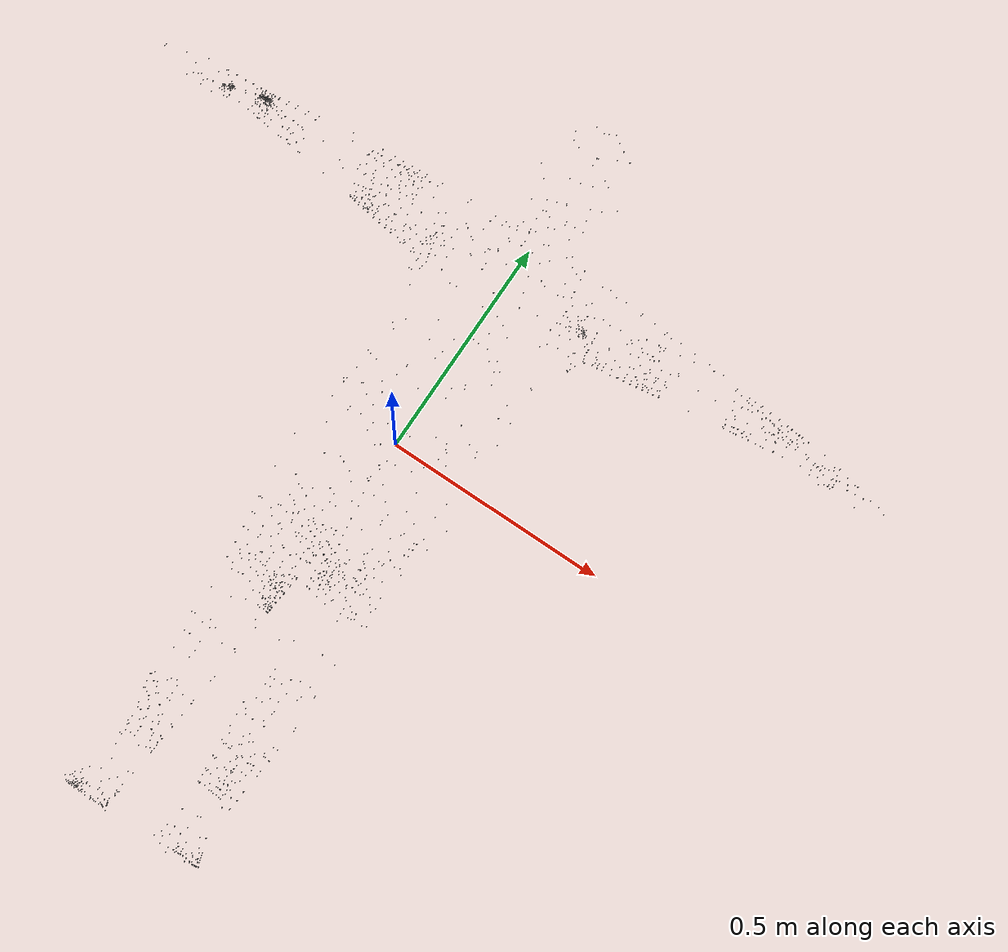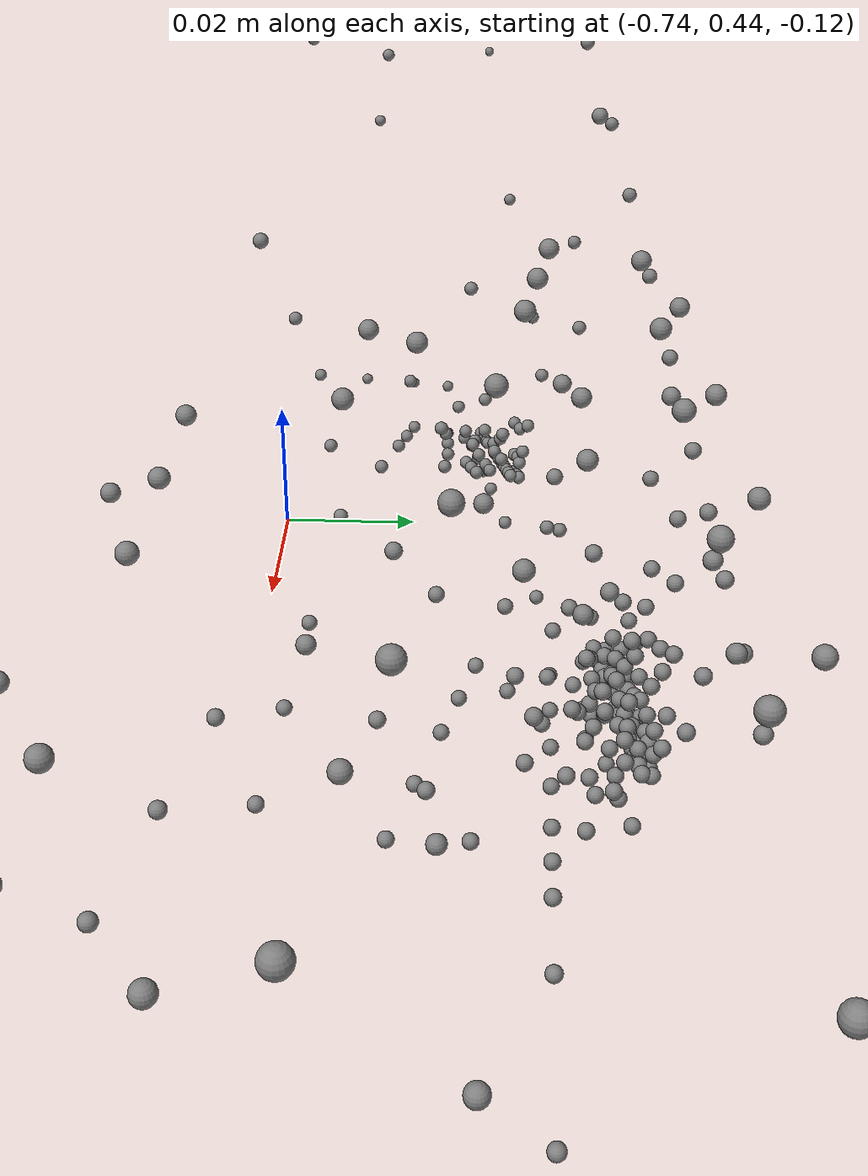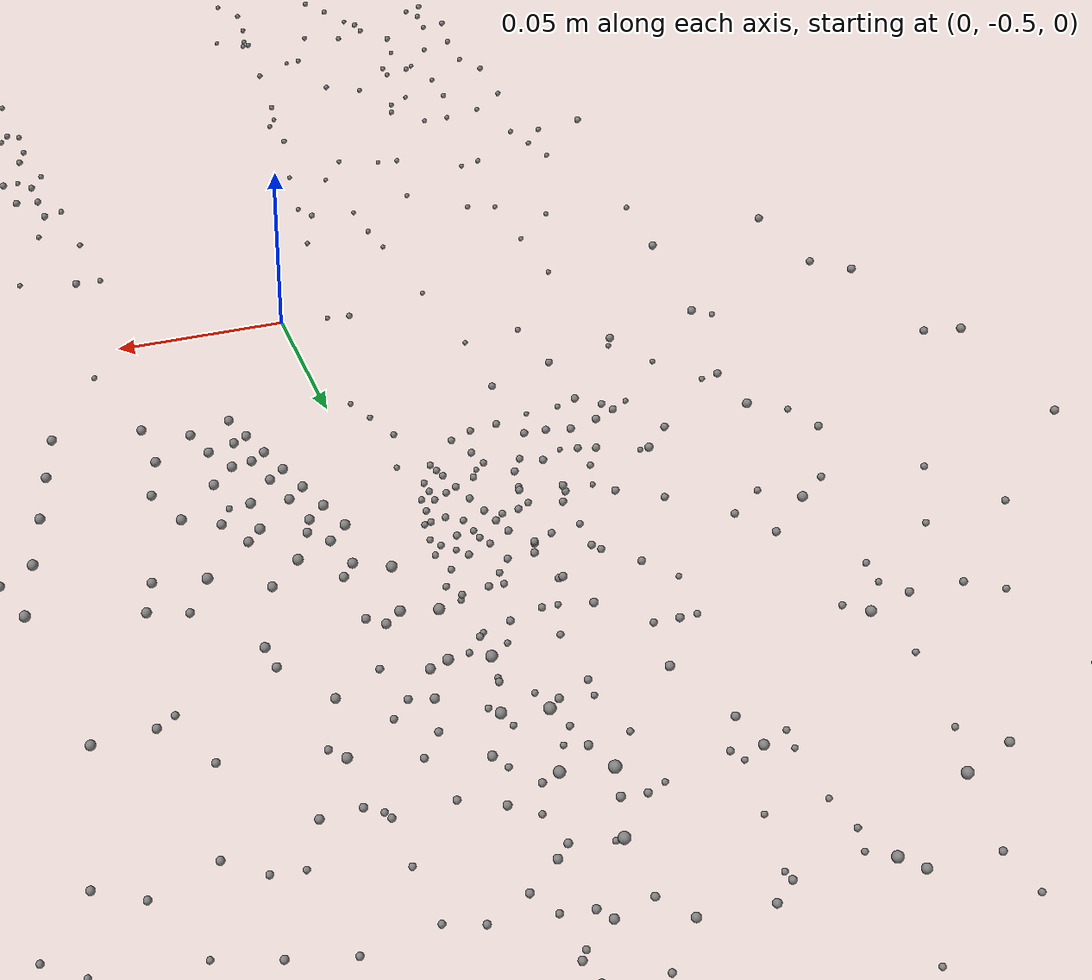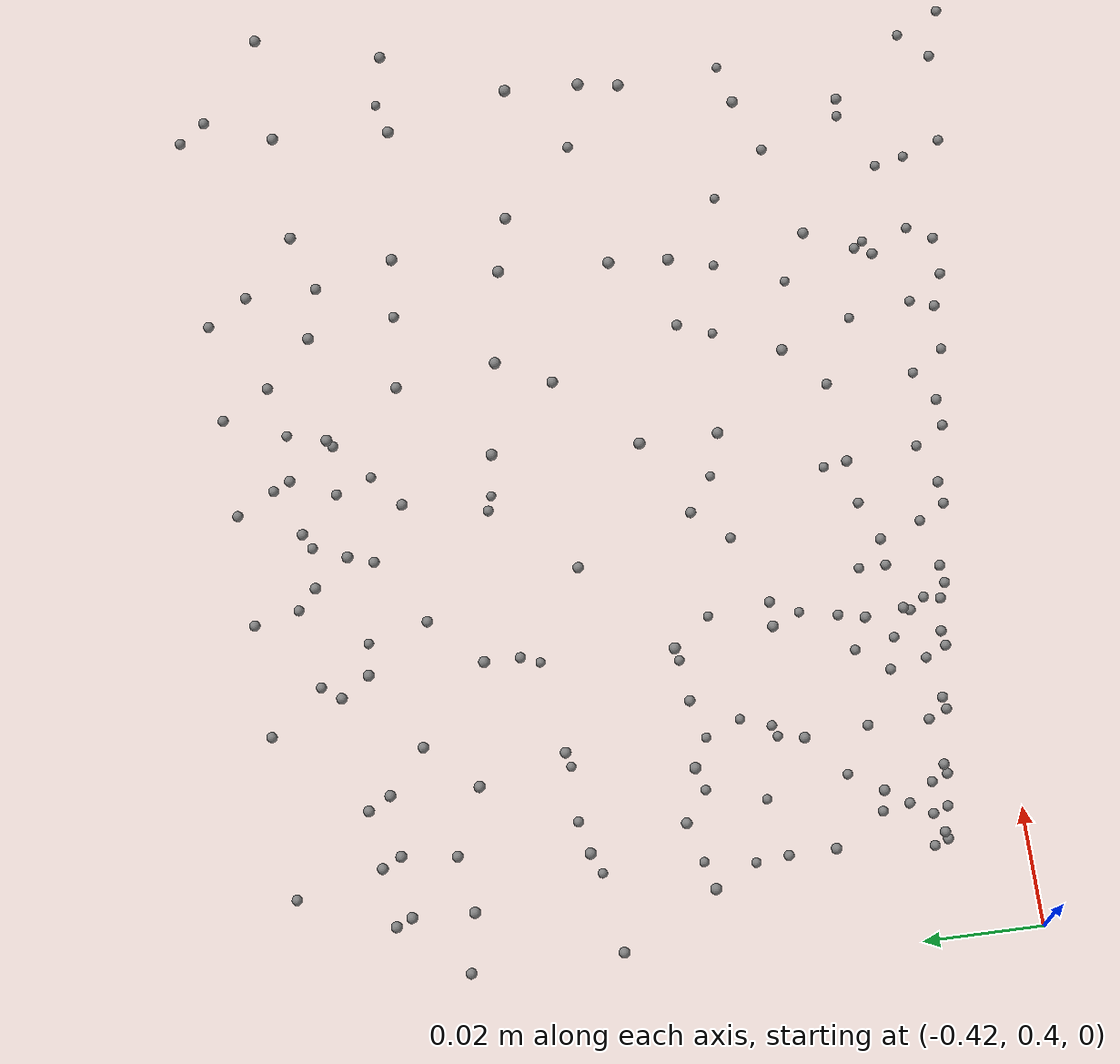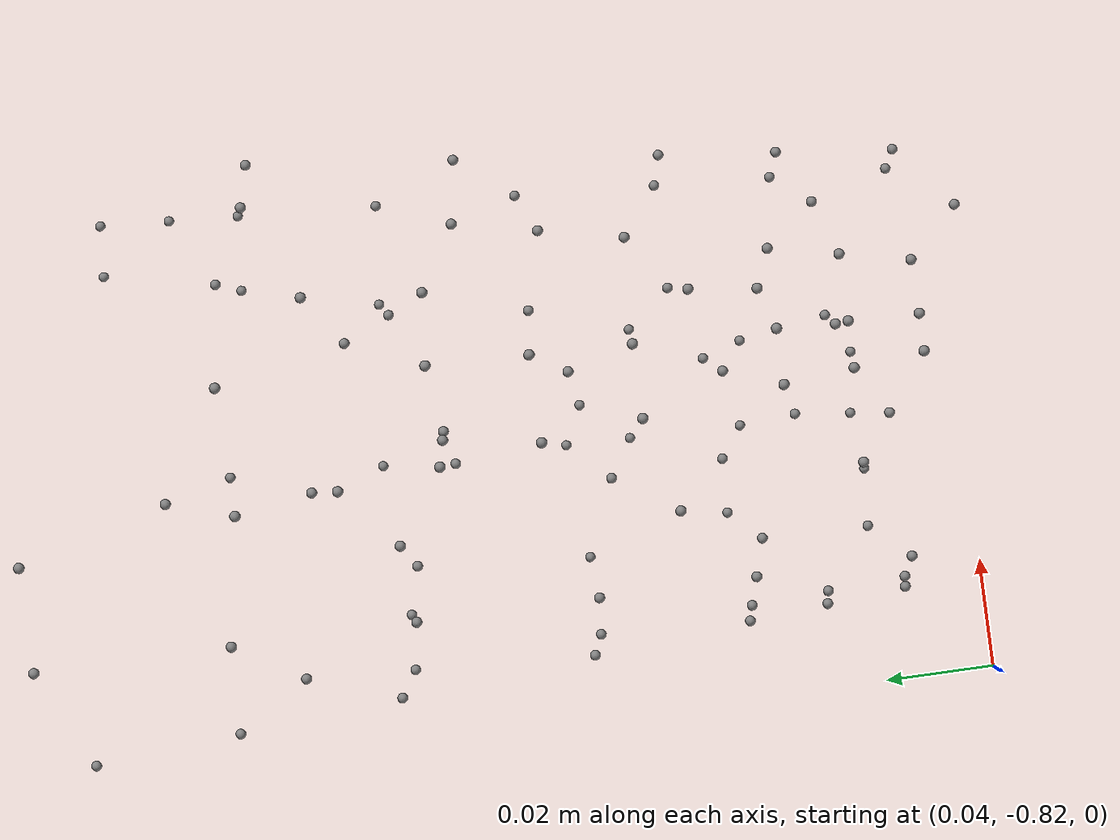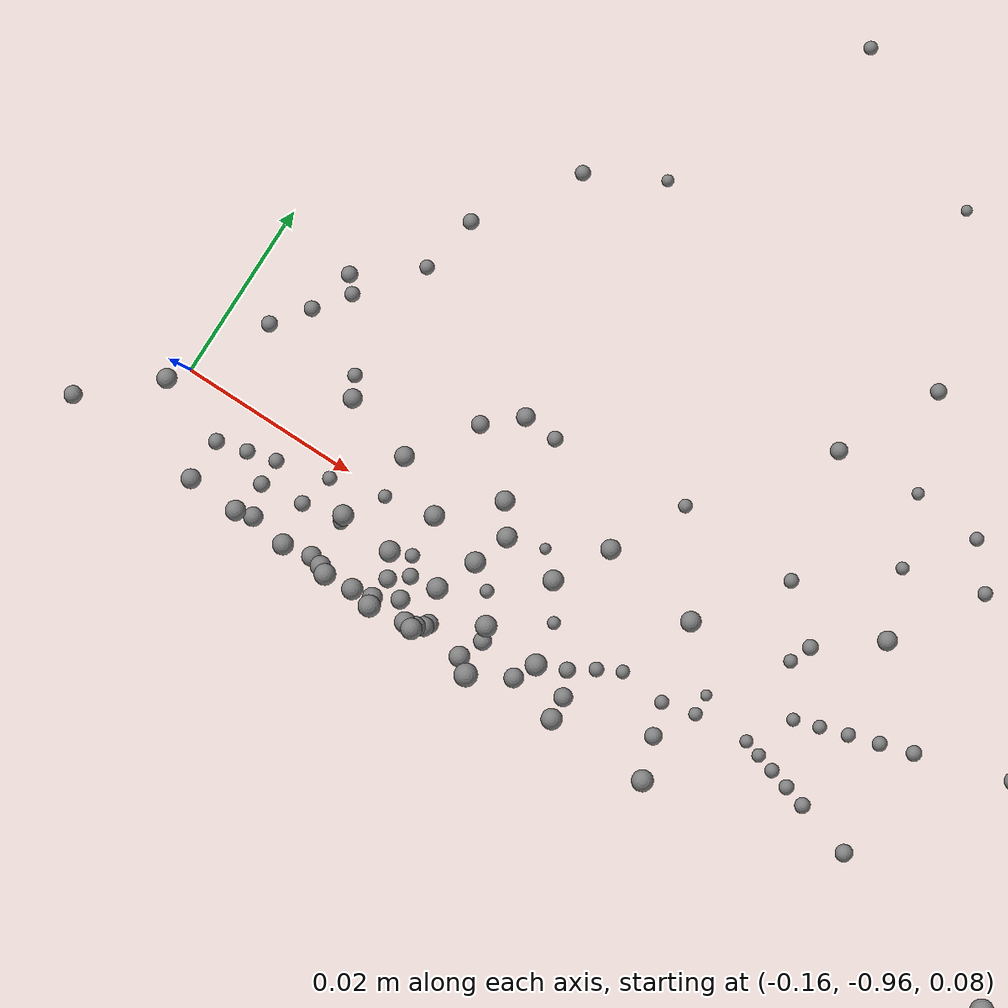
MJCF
<mujoco model="unnamed_model">
  <default>
    <default class="/"/>
  </default>
  <worldbody>
    <body name="point_mass_0">
      <freejoint name="//unnamed_joint_0"/>
      <geom name="point_mass_0" class="/" type="sphere" size="0.001" mass="0.01" pos="0.15091438591480255 0.19111129641532898 0.04627135768532753"/>
    </body>
    <body name="point_mass_1">
      <freejoint name="//unnamed_joint_1"/>
      <geom name="point_mass_1" class="/" type="sphere" size="0.001" mass="0.01" pos="0.049094084650278091 0.11424221843481064 0.14417916536331177"/>
    </body>
    <body name="point_mass_2">
      <freejoint name="//unnamed_joint_2"/>
      <geom name="point_mass_2" class="/" type="sphere" size="0.001" mass="0.01" pos="0.16448202729225159 -0.054161284118890762 0.055852863937616348"/>
    </body>
    <body name="point_mass_3">
      <freejoint name="//unnamed_joint_3"/>
      <geom name="point_mass_3" class="/" type="sphere" size="0.001" mass="0.01" pos="0.18853607773780823 -0.090344980359077454 -0.013293173164129257"/>
    </body>
    <body name="point_mass_4">
      <freejoint name="//unnamed_joint_4"/>
      <geom name="point_mass_4" class="/" type="sphere" size="0.001" mass="0.01" pos="0.16582567989826202 0.25907167792320251 -0.0055254003964364529"/>
    </body>
    <body name="point_mass_5">
      <freejoint name="//unnamed_joint_5"/>
      <geom name="point_mass_5" class="/" type="sphere" size="0.001" mass="0.01" pos="-0.071390651166439056 -0.074252456426620483 -0.15708854794502258"/>
    </body>
    <body name="point_mass_6">
      <freejoint name="//unnamed_joint_6"/>
      <geom name="point_mass_6" class="/" type="sphere" size="0.001" mass="0.01" pos="0.10506662726402283 -0.12657803297042847 -0.12468226999044418"/>
    </body>
    <body name="point_mass_7">
      <freejoint name="//unnamed_joint_7"/>
      <geom name="point_mass_7" class="/" type="sphere" size="0.001" mass="0.01" pos="-0.065166771411895752 -0.13905543088912964 -0.12319212406873703"/>
    </body>
    <body name="point_mass_8">
      <freejoint name="//unnamed_joint_8"/>
      <geom name="point_mass_8" class="/" type="sphere" size="0.001" mass="0.01" pos="-0.13196411728858948 -0.07697431743144989 -0.12487305700778961"/>
    </body>
    <body name="point_mass_9">
      <freejoint name="//unnamed_joint_9"/>
      <geom name="point_mass_9" class="/" type="sphere" size="0.001" mass="0.01" pos="0.011592231690883636 -0.11321289092302322 0.11887156963348389"/>
    </body>
    <body name="point_mass_10">
      <freejoint name="//unnamed_joint_10"/>
      <geom name="point_mass_10" class="/" type="sphere" size="0.001" mass="0.01" pos="-0.19145758450031281 -0.093377679586410522 -0.016473982483148575"/>
    </body>
    <body name="point_mass_11">
      <freejoint name="//unnamed_joint_11"/>
      <geom name="point_mass_11" class="/" type="sphere" size="0.001" mass="0.01" pos="-0.14853550493717194 0.20818208158016205 0.036103833466768265"/>
    </body>
    <body name="point_mass_12">
      <freejoint name="//unnamed_joint_12"/>
      <geom name="point_mass_12" class="/" type="sphere" size="0.001" mass="0.01" pos="-0.15312425792217255 0.21496087312698364 -0.05972907692193985"/>
    </body>
    <body name="point_mass_13">
      <freejoint name="//unnamed_joint_13"/>
      <geom name="point_mass_13" class="/" type="sphere" size="0.001" mass="0.01" pos="-0.099748097360134125 0.1467718780040741 -0.11225739866495132"/>
    </body>
    <body name="point_mass_14">
      <freejoint name="//unnamed_joint_14"/>
      <geom name="point_mass_14" class="/" type="sphere" size="0.001" mass="0.01" pos="0.14008912444114685 -0.062910899519920349 -0.11818210780620575"/>
    </body>
    <body name="point_mass_15">
      <freejoint name="//unnamed_joint_15"/>
      <geom name="point_mass_15" class="/" type="sphere" size="0.001" mass="0.01" pos="0.07319372147321701 -0.035436429083347321 -0.15373152494430542"/>
    </body>
    <body name="point_mass_16">
      <freejoint name="//unnamed_joint_16"/>
      <geom name="point_mass_16" class="/" type="sphere" size="0.001" mass="0.01" pos="-0.020156167447566986 -0.13225606083869934 0.096932709217071533"/>
    </body>
    <body name="point_mass_17">
      <freejoint name="//unnamed_joint_17"/>
      <geom name="point_mass_17" class="/" type="sphere" size="0.001" mass="0.01" pos="-0.13685253262519836 -0.051968585699796677 0.076787874102592468"/>
    </body>
    <body name="point_mass_18">
      <freejoint name="//unnamed_joint_18"/>
      <geom name="point_mass_18" class="/" type="sphere" size="0.001" mass="0.01" pos="-0.056399360299110413 0.1259477436542511 0.14204372465610504"/>
    </body>
    <body name="point_mass_19">
      <freejoint name="//unnamed_joint_19"/>
      <geom name="point_mass_19" class="/" type="sphere" size="0.001" mass="0.01" pos="0.13640055060386658 0.18203732371330261 -0.081478551030158997"/>
    </body>
    <body name="point_mass_20">
      <freejoint name="//unnamed_joint_20"/>
      <geom name="point_mass_20" class="/" type="sphere" size="0.001" mass="0.01" pos="0.076297573745250702 0.13125471770763397 -0.11183696240186691"/>
    </body>
    <body name="point_mass_21">
      <freejoint name="//unnamed_joint_21"/>
      <geom name="point_mass_21" class="/" type="sphere" size="0.001" mass="0.01" pos="0.014003892429172993 -0.13793650269508362 0.097407929599285126"/>
    </body>
    <body name="point_mass_22">
      <freejoint name="//unnamed_joint_22"/>
      <geom name="point_mass_22" class="/" type="sphere" size="0.001" mass="0.01" pos="-0.17600788176059723 -0.18527604639530182 0.051774390041828156"/>
    </body>
    <body name="point_mass_23">
      <freejoint name="//unnamed_joint_23"/>
      <geom name="point_mass_23" class="/" type="sphere" size="0.001" mass="0.01" pos="-0.85400152206420898 0.45256710052490234 -0.1572096049785614"/>
    </body>
    <body name="point_mass_24">
      <freejoint name="//unnamed_joint_24"/>
      <geom name="point_mass_24" class="/" type="sphere" size="0.001" mass="0.01" pos="-0.90244543552398682 0.45949658751487732 -0.042105335742235184"/>
    </body>
    <body name="point_mass_25">
      <freejoint name="//unnamed_joint_25"/>
      <geom name="point_mass_25" class="/" type="sphere" size="0.001" mass="0.01" pos="-0.91607338190078735 0.4670637845993042 -0.10106962919235229"/>
    </body>
    <body name="point_mass_26">
      <freejoint name="//unnamed_joint_26"/>
      <geom name="point_mass_26" class="/" type="sphere" size="0.001" mass="0.01" pos="-0.81235045194625854 0.48494482040405273 -0.056171298027038574"/>
    </body>
    <body name="point_mass_27">
      <freejoint name="//unnamed_joint_27"/>
      <geom name="point_mass_27" class="/" type="sphere" size="0.001" mass="0.01" pos="-0.8056904673576355 0.46237865090370178 -0.13134656846523285"/>
    </body>
    <body name="point_mass_28">
      <freejoint name="//unnamed_joint_28"/>
      <geom name="point_mass_28" class="/" type="sphere" size="0.001" mass="0.01" pos="-0.77873712778091431 0.44119828939437866 -0.11477868258953094"/>
    </body>
    <body name="point_mass_29">
      <freejoint name="//unnamed_joint_29"/>
      <geom name="point_mass_29" class="/" type="sphere" size="0.001" mass="0.01" pos="-0.82620388269424438 0.45857810974121094 -0.036845363676548004"/>
    </body>
    <body name="point_mass_30">
      <freejoint name="//unnamed_joint_30"/>
      <geom name="point_mass_30" class="/" type="sphere" size="0.001" mass="0.01" pos="0.9074370265007019 0.46006190776824951 -0.042022105306386948"/>
    </body>
    <body name="point_mass_31">
      <freejoint name="//unnamed_joint_31"/>
      <geom name="point_mass_31" class="/" type="sphere" size="0.001" mass="0.01" pos="0.92118912935256958 0.46507194638252258 -0.098798468708992004"/>
    </body>
    <body name="point_mass_32">
      <freejoint name="//unnamed_joint_32"/>
      <geom name="point_mass_32" class="/" type="sphere" size="0.001" mass="0.01" pos="0.82465654611587524 0.47838523983955383 -0.045227017253637314"/>
    </body>
    <body name="point_mass_33">
      <freejoint name="//unnamed_joint_33"/>
      <geom name="point_mass_33" class="/" type="sphere" size="0.001" mass="0.01" pos="0.75086712837219238 0.49440398812294006 -0.056794688105583191"/>
    </body>
    <body name="point_mass_34">
      <freejoint name="//unnamed_joint_34"/>
      <geom name="point_mass_34" class="/" type="sphere" size="0.001" mass="0.01" pos="0.85869050025939941 0.45644226670265198 -0.15775500237941742"/>
    </body>
    <body name="point_mass_35">
      <freejoint name="//unnamed_joint_35"/>
      <geom name="point_mass_35" class="/" type="sphere" size="0.001" mass="0.01" pos="0.78842359781265259 0.47067853808403015 -0.11906909197568893"/>
    </body>
    <body name="point_mass_36">
      <freejoint name="//unnamed_joint_36"/>
      <geom name="point_mass_36" class="/" type="sphere" size="0.001" mass="0.01" pos="0.77045875787734985 0.44669091701507568 -0.11678808927536011"/>
    </body>
    <body name="point_mass_37">
      <freejoint name="//unnamed_joint_37"/>
      <geom name="point_mass_37" class="/" type="sphere" size="0.001" mass="0.01" pos="0.83155417442321777 0.45559272170066833 -0.048448286950588226"/>
    </body>
    <body name="point_mass_38">
      <freejoint name="//unnamed_joint_38"/>
      <geom name="point_mass_38" class="/" type="sphere" size="0.001" mass="0.01" pos="-0.71641337871551514 0.48554885387420654 -0.043694276362657547"/>
    </body>
    <body name="point_mass_39">
      <freejoint name="//unnamed_joint_39"/>
      <geom name="point_mass_39" class="/" type="sphere" size="0.001" mass="0.01" pos="-0.82192206382751465 0.43927335739135742 0.026770174503326416"/>
    </body>
    <body name="point_mass_40">
      <freejoint name="//unnamed_joint_40"/>
      <geom name="point_mass_40" class="/" type="sphere" size="0.001" mass="0.01" pos="-0.71379339694976807 0.44278639554977417 -0.060101427137851715"/>
    </body>
    <body name="point_mass_41">
      <freejoint name="//unnamed_joint_41"/>
      <geom name="point_mass_41" class="/" type="sphere" size="0.001" mass="0.01" pos="-0.56002604961395264 0.50888502597808838 -0.089828722178936005"/>
    </body>
    <body name="point_mass_42">
      <freejoint name="//unnamed_joint_42"/>
      <geom name="point_mass_42" class="/" type="sphere" size="0.001" mass="0.01" pos="-0.71661639213562012 0.48078826069831848 -0.10494212806224823"/>
    </body>
    <body name="point_mass_43">
      <freejoint name="//unnamed_joint_43"/>
      <geom name="point_mass_43" class="/" type="sphere" size="0.001" mass="0.01" pos="-0.71249580383300781 0.45179444551467896 -0.10116637498140335"/>
    </body>
    <body name="point_mass_44">
      <freejoint name="//unnamed_joint_44"/>
      <geom name="point_mass_44" class="/" type="sphere" size="0.001" mass="0.01" pos="0.83020424842834473 0.45033833384513855 0.021875826641917229"/>
    </body>
    <body name="point_mass_45">
      <freejoint name="//unnamed_joint_45"/>
      <geom name="point_mass_45" class="/" type="sphere" size="0.001" mass="0.01" pos="0.71837413311004639 0.47074952721595764 -0.041681576520204544"/>
    </body>
    <body name="point_mass_46">
      <freejoint name="//unnamed_joint_46"/>
      <geom name="point_mass_46" class="/" type="sphere" size="0.001" mass="0.01" pos="0.72129106521606445 0.44647935032844543 -0.058189969509840012"/>
    </body>
    <body name="point_mass_47">
      <freejoint name="//unnamed_joint_47"/>
      <geom name="point_mass_47" class="/" type="sphere" size="0.001" mass="0.01" pos="0.71827536821365356 0.45664474368095398 -0.10312327742576599"/>
    </body>
    <body name="point_mass_48">
      <freejoint name="//unnamed_joint_48"/>
      <geom name="point_mass_48" class="/" type="sphere" size="0.001" mass="0.01" pos="-0.45026475191116333 0.50034517049789429 -0.027955006808042526"/>
    </body>
    <body name="point_mass_49">
      <freejoint name="//unnamed_joint_49"/>
      <geom name="point_mass_49" class="/" type="sphere" size="0.001" mass="0.01" pos="-0.44883754849433899 0.44959044456481934 -0.022625602781772614"/>
    </body>
    <body name="point_mass_50">
      <freejoint name="//unnamed_joint_50"/>
      <geom name="point_mass_50" class="/" type="sphere" size="0.001" mass="0.01" pos="-0.46300095319747925 0.52165061235427856 -0.055991146713495255"/>
    </body>
    <body name="point_mass_51">
      <freejoint name="//unnamed_joint_51"/>
      <geom name="point_mass_51" class="/" type="sphere" size="0.001" mass="0.01" pos="-0.51762479543685913 0.48271521925926208 -0.11083169281482697"/>
    </body>
    <body name="point_mass_52">
      <freejoint name="//unnamed_joint_52"/>
      <geom name="point_mass_52" class="/" type="sphere" size="0.001" mass="0.01" pos="-0.44823890924453735 0.45714259147644043 -0.10922840982675552"/>
    </body>
    <body name="point_mass_53">
      <freejoint name="//unnamed_joint_53"/>
      <geom name="point_mass_53" class="/" type="sphere" size="0.001" mass="0.01" pos="-0.46824151277542114 0.41523703932762146 -0.062149133533239365"/>
    </body>
    <body name="point_mass_54">
      <freejoint name="//unnamed_joint_54"/>
      <geom name="point_mass_54" class="/" type="sphere" size="0.001" mass="0.01" pos="-0.58259409666061401 0.44183546304702759 -0.10818442702293396"/>
    </body>
    <body name="point_mass_55">
      <freejoint name="//unnamed_joint_55"/>
      <geom name="point_mass_55" class="/" type="sphere" size="0.001" mass="0.01" pos="0.46135848760604858 0.50975668430328369 -0.031660590320825577"/>
    </body>
    <body name="point_mass_56">
      <freejoint name="//unnamed_joint_56"/>
      <geom name="point_mass_56" class="/" type="sphere" size="0.001" mass="0.01" pos="0.46130090951919556 0.41436958312988281 -0.063560180366039276"/>
    </body>
    <body name="point_mass_57">
      <freejoint name="//unnamed_joint_57"/>
      <geom name="point_mass_57" class="/" type="sphere" size="0.001" mass="0.01" pos="0.58965730667114258 0.44652512669563293 -0.10879328846931458"/>
    </body>
    <body name="point_mass_58">
      <freejoint name="//unnamed_joint_58"/>
      <geom name="point_mass_58" class="/" type="sphere" size="0.001" mass="0.01" pos="0.55982249975204468 0.49502164125442505 -0.10147258639335632"/>
    </body>
    <body name="point_mass_59">
      <freejoint name="//unnamed_joint_59"/>
      <geom name="point_mass_59" class="/" type="sphere" size="0.001" mass="0.01" pos="0.47984820604324341 0.51999491453170776 -0.062461104243993759"/>
    </body>
    <body name="point_mass_60">
      <freejoint name="//unnamed_joint_60"/>
      <geom name="point_mass_60" class="/" type="sphere" size="0.001" mass="0.01" pos="0.45746517181396484 0.45445087552070618 -0.022197360172867775"/>
    </body>
    <body name="point_mass_61">
      <freejoint name="//unnamed_joint_61"/>
      <geom name="point_mass_61" class="/" type="sphere" size="0.001" mass="0.01" pos="0.44979840517044067 0.4621201753616333 -0.10602371394634247"/>
    </body>
    <body name="point_mass_62">
      <freejoint name="//unnamed_joint_62"/>
      <geom name="point_mass_62" class="/" type="sphere" size="0.001" mass="0.01" pos="-0.1665617823600769 0.51754158735275269 0.0058743609115481377"/>
    </body>
    <body name="point_mass_63">
      <freejoint name="//unnamed_joint_63"/>
      <geom name="point_mass_63" class="/" type="sphere" size="0.001" mass="0.01" pos="-0.17082265019416809 0.5351671576499939 -0.035180605947971344"/>
    </body>
    <body name="point_mass_64">
      <freejoint name="//unnamed_joint_64"/>
      <geom name="point_mass_64" class="/" type="sphere" size="0.001" mass="0.01" pos="-0.21893937885761261 0.37640589475631714 -0.066158302128314972"/>
    </body>
    <body name="point_mass_65">
      <freejoint name="//unnamed_joint_65"/>
      <geom name="point_mass_65" class="/" type="sphere" size="0.001" mass="0.01" pos="-0.21497076749801636 0.38070473074913025 -0.04114847257733345"/>
    </body>
    <body name="point_mass_66">
      <freejoint name="//unnamed_joint_66"/>
      <geom name="point_mass_66" class="/" type="sphere" size="0.001" mass="0.01" pos="-0.20281209051609039 0.45939174294471741 0.024949287995696068"/>
    </body>
    <body name="point_mass_67">
      <freejoint name="//unnamed_joint_67"/>
      <geom name="point_mass_67" class="/" type="sphere" size="0.001" mass="0.01" pos="-0.21458053588867188 0.3820769190788269 -0.083484023809432983"/>
    </body>
    <body name="point_mass_68">
      <freejoint name="//unnamed_joint_68"/>
      <geom name="point_mass_68" class="/" type="sphere" size="0.001" mass="0.01" pos="-0.204700767993927 0.41863012313842773 -0.10811720788478851"/>
    </body>
    <body name="point_mass_69">
      <freejoint name="//unnamed_joint_69"/>
      <geom name="point_mass_69" class="/" type="sphere" size="0.001" mass="0.01" pos="-0.20813015103340149 0.49471697211265564 -0.099956706166267395"/>
    </body>
    <body name="point_mass_70">
      <freejoint name="//unnamed_joint_70"/>
      <geom name="point_mass_70" class="/" type="sphere" size="0.001" mass="0.01" pos="0.21614742279052734 0.38714820146560669 -0.041792139410972595"/>
    </body>
    <body name="point_mass_71">
      <freejoint name="//unnamed_joint_71"/>
      <geom name="point_mass_71" class="/" type="sphere" size="0.001" mass="0.01" pos="0.22117264568805695 0.3798488974571228 -0.067913800477981567"/>
    </body>
    <body name="point_mass_72">
      <freejoint name="//unnamed_joint_72"/>
      <geom name="point_mass_72" class="/" type="sphere" size="0.001" mass="0.01" pos="0.21547463536262512 0.38518360257148743 -0.087218835949897766"/>
    </body>
    <body name="point_mass_73">
      <freejoint name="//unnamed_joint_73"/>
      <geom name="point_mass_73" class="/" type="sphere" size="0.001" mass="0.01" pos="0.21291682124137878 0.46248054504394531 0.019547957926988602"/>
    </body>
    <body name="point_mass_74">
      <freejoint name="//unnamed_joint_74"/>
      <geom name="point_mass_74" class="/" type="sphere" size="0.001" mass="0.01" pos="0.16920264065265656 0.52414983510971069 -0.00092321180272847414"/>
    </body>
    <body name="point_mass_75">
      <freejoint name="//unnamed_joint_75"/>
      <geom name="point_mass_75" class="/" type="sphere" size="0.001" mass="0.01" pos="0.21603687107563019 0.486143559217453 -0.10581257939338684"/>
    </body>
    <body name="point_mass_76">
      <freejoint name="//unnamed_joint_76"/>
      <geom name="point_mass_76" class="/" type="sphere" size="0.001" mass="0.01" pos="0.20833414793014526 0.41610759496688843 -0.10526822507381439"/>
    </body>
    <body name="point_mass_77">
      <freejoint name="//unnamed_joint_77"/>
      <geom name="point_mass_77" class="/" type="sphere" size="0.001" mass="0.01" pos="0.18439239263534546 0.53442192077636719 -0.033612564206123352"/>
    </body>
    <body name="point_mass_78">
      <freejoint name="//unnamed_joint_78"/>
      <geom name="point_mass_78" class="/" type="sphere" size="0.001" mass="0.01" pos="-0.026234826073050499 0.79536014795303345 0.049276288598775864"/>
    </body>
    <body name="point_mass_79">
      <freejoint name="//unnamed_joint_79"/>
      <geom name="point_mass_79" class="/" type="sphere" size="0.001" mass="0.01" pos="0.017457446083426476 0.80289900302886963 0.052172295749187469"/>
    </body>
    <body name="point_mass_80">
      <freejoint name="//unnamed_joint_80"/>
      <geom name="point_mass_80" class="/" type="sphere" size="0.001" mass="0.01" pos="-0.018224740400910378 0.81525576114654541 -0.046793539077043533"/>
    </body>
    <body name="point_mass_81">
      <freejoint name="//unnamed_joint_81"/>
      <geom name="point_mass_81" class="/" type="sphere" size="0.001" mass="0.01" pos="0.0059890882112085819 0.68341010808944702 0.11928608268499374"/>
    </body>
    <body name="point_mass_82">
      <freejoint name="//unnamed_joint_82"/>
      <geom name="point_mass_82" class="/" type="sphere" size="0.001" mass="0.01" pos="0.071055427193641663 0.77566319704055786 0.02118607796728611"/>
    </body>
    <body name="point_mass_83">
      <freejoint name="//unnamed_joint_83"/>
      <geom name="point_mass_83" class="/" type="sphere" size="0.001" mass="0.01" pos="0.051884997636079788 0.75458407402038574 0.067725785076618195"/>
    </body>
    <body name="point_mass_84">
      <freejoint name="//unnamed_joint_84"/>
      <geom name="point_mass_84" class="/" type="sphere" size="0.001" mass="0.01" pos="0.06065141037106514 0.62472903728485107 0.065827392041683197"/>
    </body>
    <body name="point_mass_85">
      <freejoint name="//unnamed_joint_85"/>
      <geom name="point_mass_85" class="/" type="sphere" size="0.001" mass="0.01" pos="-0.067586436867713928 0.778087317943573 -0.013556276448071003"/>
    </body>
    <body name="point_mass_86">
      <freejoint name="//unnamed_joint_86"/>
      <geom name="point_mass_86" class="/" type="sphere" size="0.001" mass="0.01" pos="-0.052080065011978149 0.77153408527374268 -0.090512849390506744"/>
    </body>
    <body name="point_mass_87">
      <freejoint name="//unnamed_joint_87"/>
      <geom name="point_mass_87" class="/" type="sphere" size="0.001" mass="0.01" pos="0.03519146516919136 0.81086808443069458 -0.068998128175735474"/>
    </body>
    <body name="point_mass_88">
      <freejoint name="//unnamed_joint_88"/>
      <geom name="point_mass_88" class="/" type="sphere" size="0.001" mass="0.01" pos="-0.061680413782596588 0.60264867544174194 -0.014862948097288609"/>
    </body>
    <body name="point_mass_89">
      <freejoint name="//unnamed_joint_89"/>
      <geom name="point_mass_89" class="/" type="sphere" size="0.001" mass="0.01" pos="-0.091614201664924622 0.68373662233352661 -0.033399462699890137"/>
    </body>
    <body name="point_mass_90">
      <freejoint name="//unnamed_joint_90"/>
      <geom name="point_mass_90" class="/" type="sphere" size="0.001" mass="0.01" pos="-0.030074246227741241 0.61089450120925903 -0.070166304707527161"/>
    </body>
    <body name="point_mass_91">
      <freejoint name="//unnamed_joint_91"/>
      <geom name="point_mass_91" class="/" type="sphere" size="0.001" mass="0.01" pos="0.10063988715410233 0.68599033355712891 -0.031234925612807274"/>
    </body>
    <body name="point_mass_92">
      <freejoint name="//unnamed_joint_92"/>
      <geom name="point_mass_92" class="/" type="sphere" size="0.001" mass="0.01" pos="0.050690814852714539 0.73456805944442749 -0.10972541570663452"/>
    </body>
    <body name="point_mass_93">
      <freejoint name="//unnamed_joint_93"/>
      <geom name="point_mass_93" class="/" type="sphere" size="0.001" mass="0.01" pos="0.042068719863891602 0.67344415187835693 -0.10265807062387466"/>
    </body>
    <body name="point_mass_94">
      <freejoint name="//unnamed_joint_94"/>
      <geom name="point_mass_94" class="/" type="sphere" size="0.001" mass="0.01" pos="0.077007979154586792 0.77336210012435913 -0.053953606635332108"/>
    </body>
    <body name="point_mass_95">
      <freejoint name="//unnamed_joint_95"/>
      <geom name="point_mass_95" class="/" type="sphere" size="0.001" mass="0.01" pos="0.067972771823406219 0.60235297679901123 -0.014456707984209061"/>
    </body>
    <body name="point_mass_96">
      <freejoint name="//unnamed_joint_96"/>
      <geom name="point_mass_96" class="/" type="sphere" size="0.001" mass="0.01" pos="0.0010852320119738579 0.57413709163665771 0.062444709241390228"/>
    </body>
    <body name="point_mass_97">
      <freejoint name="//unnamed_joint_97"/>
      <geom name="point_mass_97" class="/" type="sphere" size="0.001" mass="0.01" pos="-0.055439788848161697 0.63662040233612061 0.060840800404548645"/>
    </body>
    <body name="point_mass_98">
      <freejoint name="//unnamed_joint_98"/>
      <geom name="point_mass_98" class="/" type="sphere" size="0.001" mass="0.01" pos="0.0021832496859133244 0.59866201877593994 0.10723816603422165"/>
    </body>
    <body name="point_mass_99">
      <freejoint name="//unnamed_joint_99"/>
      <geom name="point_mass_99" class="/" type="sphere" size="0.001" mass="0.01" pos="-0.049261141568422318 0.74154090881347656 0.06094004213809967"/>
    </body>
    <body name="point_mass_100">
      <freejoint name="//unnamed_joint_100"/>
      <geom name="point_mass_100" class="/" type="sphere" size="0.001" mass="0.01" pos="-0.0087749240919947624 0.76033937931060791 -0.11390804499387741"/>
    </body>
    <body name="point_mass_101">
      <freejoint name="//unnamed_joint_101"/>
      <geom name="point_mass_101" class="/" type="sphere" size="0.001" mass="0.01" pos="-0.034177444875240326 0.70874321460723877 -0.11417535692453384"/>
    </body>
    <body name="point_mass_102">
      <freejoint name="//unnamed_joint_102"/>
      <geom name="point_mass_102" class="/" type="sphere" size="0.001" mass="0.01" pos="0.035479344427585602 0.58718043565750122 0.05246378481388092"/>
    </body>
    <body name="point_mass_103">
      <freejoint name="//unnamed_joint_103"/>
      <geom name="point_mass_103" class="/" type="sphere" size="0.001" mass="0.01" pos="0.019501514732837677 0.60874444246292114 -0.078680366277694702"/>
    </body>
    <body name="point_mass_104">
      <freejoint name="//unnamed_joint_104"/>
      <geom name="point_mass_104" class="/" type="sphere" size="0.001" mass="0.01" pos="-0.17948451638221741 0.43835610151290894 0.033827804028987885"/>
    </body>
    <body name="point_mass_105">
      <freejoint name="//unnamed_joint_105"/>
      <geom name="point_mass_105" class="/" type="sphere" size="0.001" mass="0.01" pos="-0.060950759798288345 0.54590171575546265 -0.092130035161972046"/>
    </body>
    <body name="point_mass_106">
      <freejoint name="//unnamed_joint_106"/>
      <geom name="point_mass_106" class="/" type="sphere" size="0.001" mass="0.01" pos="-0.09607338160276413 0.47676137089729309 -0.13249872624874115"/>
    </body>
    <body name="point_mass_107">
      <freejoint name="//unnamed_joint_107"/>
      <geom name="point_mass_107" class="/" type="sphere" size="0.001" mass="0.01" pos="-0.10719022899866104 0.3841702938079834 -0.15149110555648804"/>
    </body>
    <body name="point_mass_108">
      <freejoint name="//unnamed_joint_108"/>
      <geom name="point_mass_108" class="/" type="sphere" size="0.001" mass="0.01" pos="-0.18787138164043427 0.39463812112808228 -0.1054803803563118"/>
    </body>
    <body name="point_mass_109">
      <freejoint name="//unnamed_joint_109"/>
      <geom name="point_mass_109" class="/" type="sphere" size="0.001" mass="0.01" pos="-0.10600725561380386 0.51150190830230713 -0.0026865685358643532"/>
    </body>
    <body name="point_mass_110">
      <freejoint name="//unnamed_joint_110"/>
      <geom name="point_mass_110" class="/" type="sphere" size="0.001" mass="0.01" pos="0.17737111449241638 0.43035575747489929 0.040615681558847427"/>
    </body>
    <body name="point_mass_111">
      <freejoint name="//unnamed_joint_111"/>
      <geom name="point_mass_111" class="/" type="sphere" size="0.001" mass="0.01" pos="0.10798139870166779 0.51916742324829102 -0.010277138091623783"/>
    </body>
    <body name="point_mass_112">
      <freejoint name="//unnamed_joint_112"/>
      <geom name="point_mass_112" class="/" type="sphere" size="0.001" mass="0.01" pos="0.096590451896190643 0.48895630240440369 -0.13451950252056122"/>
    </body>
    <body name="point_mass_113">
      <freejoint name="//unnamed_joint_113"/>
      <geom name="point_mass_113" class="/" type="sphere" size="0.001" mass="0.01" pos="0.11302793771028519 0.37346065044403076 -0.15271666646003723"/>
    </body>
    <body name="point_mass_114">
      <freejoint name="//unnamed_joint_114"/>
      <geom name="point_mass_114" class="/" type="sphere" size="0.001" mass="0.01" pos="0.1850149929523468 0.39386484026908875 -0.11284072697162628"/>
    </body>
    <body name="point_mass_115">
      <freejoint name="//unnamed_joint_115"/>
      <geom name="point_mass_115" class="/" type="sphere" size="0.001" mass="0.01" pos="0.061448819935321808 0.55277895927429199 -0.082353211939334869"/>
    </body>
    <body name="point_mass_116">
      <freejoint name="//unnamed_joint_116"/>
      <geom name="point_mass_116" class="/" type="sphere" size="0.001" mass="0.01" pos="-0.05673116073012352 0.56325256824493408 -0.068929009139537811"/>
    </body>
    <body name="point_mass_117">
      <freejoint name="//unnamed_joint_117"/>
      <geom name="point_mass_117" class="/" type="sphere" size="0.001" mass="0.01" pos="0.077385015785694122 0.54854482412338257 -0.029840875416994095"/>
    </body>
    <body name="point_mass_118">
      <freejoint name="//unnamed_joint_118"/>
      <geom name="point_mass_118" class="/" type="sphere" size="0.001" mass="0.01" pos="-0.069718964397907257 0.53782999515533447 -0.018447345122694969"/>
    </body>
    <body name="point_mass_119">
      <freejoint name="//unnamed_joint_119"/>
      <geom name="point_mass_119" class="/" type="sphere" size="0.001" mass="0.01" pos="-0.018082335591316223 0.52713483572006226 0.035468310117721558"/>
    </body>
    <body name="point_mass_120">
      <freejoint name="//unnamed_joint_120"/>
      <geom name="point_mass_120" class="/" type="sphere" size="0.001" mass="0.01" pos="0.0296812504529953 0.52782601118087769 0.035457193851470947"/>
    </body>
    <body name="point_mass_121">
      <freejoint name="//unnamed_joint_121"/>
      <geom name="point_mass_121" class="/" type="sphere" size="0.001" mass="0.01" pos="-0.069481790065765381 -0.96777743101119995 0.15212102234363556"/>
    </body>
    <body name="point_mass_122">
      <freejoint name="//unnamed_joint_122"/>
      <geom name="point_mass_122" class="/" type="sphere" size="0.001" mass="0.01" pos="-0.061718933284282684 -0.94911545515060425 0.073197729885578156"/>
    </body>
    <body name="point_mass_123">
      <freejoint name="//unnamed_joint_123"/>
      <geom name="point_mass_123" class="/" type="sphere" size="0.001" mass="0.01" pos="-0.096389114856719971 -0.92858940362930298 0.065640613436698914"/>
    </body>
    <body name="point_mass_124">
      <freejoint name="//unnamed_joint_124"/>
      <geom name="point_mass_124" class="/" type="sphere" size="0.001" mass="0.01" pos="-0.15832988917827606 -0.96162450313568115 0.10555577278137207"/>
    </body>
    <body name="point_mass_125">
      <freejoint name="//unnamed_joint_125"/>
      <geom name="point_mass_125" class="/" type="sphere" size="0.001" mass="0.01" pos="-0.16948430240154266 -0.96909403800964355 0.077797763049602509"/>
    </body>
    <body name="point_mass_126">
      <freejoint name="//unnamed_joint_126"/>
      <geom name="point_mass_126" class="/" type="sphere" size="0.001" mass="0.01" pos="-0.11893097311258316 -0.96787387132644653 0.14742377400398254"/>
    </body>
    <body name="point_mass_127">
      <freejoint name="//unnamed_joint_127"/>
      <geom name="point_mass_127" class="/" type="sphere" size="0.001" mass="0.01" pos="0.1605994701385498 -0.95645672082901001 0.10135886073112488"/>
    </body>
    <body name="point_mass_128">
      <freejoint name="//unnamed_joint_128"/>
      <geom name="point_mass_128" class="/" type="sphere" size="0.001" mass="0.01" pos="0.099623791873455048 -0.92754393815994263 0.064571380615234375"/>
    </body>
    <body name="point_mass_129">
      <freejoint name="//unnamed_joint_129"/>
      <geom name="point_mass_129" class="/" type="sphere" size="0.001" mass="0.01" pos="0.067175984382629395 -0.96580195426940918 0.15055468678474426"/>
    </body>
    <body name="point_mass_130">
      <freejoint name="//unnamed_joint_130"/>
      <geom name="point_mass_130" class="/" type="sphere" size="0.001" mass="0.01" pos="0.17056936025619507 -0.96470177173614502 0.080109164118766785"/>
    </body>
    <body name="point_mass_131">
      <freejoint name="//unnamed_joint_131"/>
      <geom name="point_mass_131" class="/" type="sphere" size="0.001" mass="0.01" pos="0.065147273242473602 -0.94527935981750488 0.071939922869205475"/>
    </body>
    <body name="point_mass_132">
      <freejoint name="//unnamed_joint_132"/>
      <geom name="point_mass_132" class="/" type="sphere" size="0.001" mass="0.01" pos="0.12286531180143356 -0.96705937385559082 0.14437593519687653"/>
    </body>
    <body name="point_mass_133">
      <freejoint name="//unnamed_joint_133"/>
      <geom name="point_mass_133" class="/" type="sphere" size="0.001" mass="0.01" pos="0.20107586681842804 0.4105963408946991 -0.075516805052757263"/>
    </body>
    <body name="point_mass_134">
      <freejoint name="//unnamed_joint_134"/>
      <geom name="point_mass_134" class="/" type="sphere" size="0.001" mass="0.01" pos="0.15929621458053589 0.27261441946029663 -0.084502339363098145"/>
    </body>
    <body name="point_mass_135">
      <freejoint name="//unnamed_joint_135"/>
      <geom name="point_mass_135" class="/" type="sphere" size="0.001" mass="0.01" pos="-0.11772763729095459 0.34692534804344177 0.094522640109062195"/>
    </body>
    <body name="point_mass_136">
      <freejoint name="//unnamed_joint_136"/>
      <geom name="point_mass_136" class="/" type="sphere" size="0.001" mass="0.01" pos="0.14941293001174927 0.34236812591552734 0.068129032850265503"/>
    </body>
    <body name="point_mass_137">
      <freejoint name="//unnamed_joint_137"/>
      <geom name="point_mass_137" class="/" type="sphere" size="0.001" mass="0.01" pos="-0.1705966591835022 0.30413958430290222 -0.013796858489513397"/>
    </body>
    <body name="point_mass_138">
      <freejoint name="//unnamed_joint_138"/>
      <geom name="point_mass_138" class="/" type="sphere" size="0.001" mass="0.01" pos="-0.1473606675863266 0.25299727916717529 -0.08843725174665451"/>
    </body>
    <body name="point_mass_139">
      <freejoint name="//unnamed_joint_139"/>
      <geom name="point_mass_139" class="/" type="sphere" size="0.001" mass="0.01" pos="0.10682143270969391 0.35243111848831177 0.10162888467311859"/>
    </body>
    <body name="point_mass_140">
      <freejoint name="//unnamed_joint_140"/>
      <geom name="point_mass_140" class="/" type="sphere" size="0.001" mass="0.01" pos="-0.095969617366790771 0.29906278848648071 -0.13847388327121735"/>
    </body>
    <body name="point_mass_141">
      <freejoint name="//unnamed_joint_141"/>
      <geom name="point_mass_141" class="/" type="sphere" size="0.001" mass="0.01" pos="-0.11535082757472992 -0.95522284507751465 -0.11528094112873077"/>
    </body>
    <body name="point_mass_142">
      <freejoint name="//unnamed_joint_142"/>
      <geom name="point_mass_142" class="/" type="sphere" size="0.001" mass="0.01" pos="-0.13151180744171143 -0.89520841836929321 -0.070853233337402344"/>
    </body>
    <body name="point_mass_143">
      <freejoint name="//unnamed_joint_143"/>
      <geom name="point_mass_143" class="/" type="sphere" size="0.001" mass="0.01" pos="-0.086145788431167603 -0.86687654256820679 -0.1056704968214035"/>
    </body>
    <body name="point_mass_144">
      <freejoint name="//unnamed_joint_144"/>
      <geom name="point_mass_144" class="/" type="sphere" size="0.001" mass="0.01" pos="-0.11653581261634827 -0.87089288234710693 -0.018668809905648232"/>
    </body>
    <body name="point_mass_145">
      <freejoint name="//unnamed_joint_145"/>
      <geom name="point_mass_145" class="/" type="sphere" size="0.001" mass="0.01" pos="-0.064171507954597473 -0.8709903359413147 -0.026059232652187347"/>
    </body>
    <body name="point_mass_146">
      <freejoint name="//unnamed_joint_146"/>
      <geom name="point_mass_146" class="/" type="sphere" size="0.001" mass="0.01" pos="-0.078911185264587402 -0.9613308310508728 -0.10158810019493103"/>
    </body>
    <body name="point_mass_147">
      <freejoint name="//unnamed_joint_147"/>
      <geom name="point_mass_147" class="/" type="sphere" size="0.001" mass="0.01" pos="0.088126696646213531 -0.86492520570755005 -0.099470272660255432"/>
    </body>
    <body name="point_mass_148">
      <freejoint name="//unnamed_joint_148"/>
      <geom name="point_mass_148" class="/" type="sphere" size="0.001" mass="0.01" pos="0.11814650148153305 -0.95796996355056763 -0.11076712608337402"/>
    </body>
    <body name="point_mass_149">
      <freejoint name="//unnamed_joint_149"/>
      <geom name="point_mass_149" class="/" type="sphere" size="0.001" mass="0.01" pos="0.076598674058914185 -0.96261364221572876 -0.093055777251720428"/>
    </body>
    <body name="point_mass_150">
      <freejoint name="//unnamed_joint_150"/>
      <geom name="point_mass_150" class="/" type="sphere" size="0.001" mass="0.01" pos="0.060728318989276886 -0.87445324659347534 -0.040918126702308655"/>
    </body>
    <body name="point_mass_151">
      <freejoint name="//unnamed_joint_151"/>
      <geom name="point_mass_151" class="/" type="sphere" size="0.001" mass="0.01" pos="0.1323036402463913 -0.89510762691497803 -0.069186247885227203"/>
    </body>
    <body name="point_mass_152">
      <freejoint name="//unnamed_joint_152"/>
      <geom name="point_mass_152" class="/" type="sphere" size="0.001" mass="0.01" pos="0.10537482053041458 -0.8700069785118103 -0.0083526019006967545"/>
    </body>
    <body name="point_mass_153">
      <freejoint name="//unnamed_joint_153"/>
      <geom name="point_mass_153" class="/" type="sphere" size="0.001" mass="0.01" pos="-0.016337588429450989 0.1726343184709549 0.14477856457233429"/>
    </body>
    <body name="point_mass_154">
      <freejoint name="//unnamed_joint_154"/>
      <geom name="point_mass_154" class="/" type="sphere" size="0.001" mass="0.01" pos="0.077219873666763306 0.24325783550739288 -0.13058018684387207"/>
    </body>
    <body name="point_mass_155">
      <freejoint name="//unnamed_joint_155"/>
      <geom name="point_mass_155" class="/" type="sphere" size="0.001" mass="0.01" pos="-0.050476305186748505 0.2462734580039978 -0.1367809921503067"/>
    </body>
    <body name="point_mass_156">
      <freejoint name="//unnamed_joint_156"/>
      <geom name="point_mass_156" class="/" type="sphere" size="0.001" mass="0.01" pos="-0.10481183975934982 -0.52540367841720581 0.040897518396377563"/>
    </body>
    <body name="point_mass_157">
      <freejoint name="//unnamed_joint_157"/>
      <geom name="point_mass_157" class="/" type="sphere" size="0.001" mass="0.01" pos="-0.028669619932770729 -0.47882050275802612 -0.033462449908256531"/>
    </body>
    <body name="point_mass_158">
      <freejoint name="//unnamed_joint_158"/>
      <geom name="point_mass_158" class="/" type="sphere" size="0.001" mass="0.01" pos="-0.049297496676445007 -0.60300290584564209 -0.1034955233335495"/>
    </body>
    <body name="point_mass_159">
      <freejoint name="//unnamed_joint_159"/>
      <geom name="point_mass_159" class="/" type="sphere" size="0.001" mass="0.01" pos="-0.16398461163043976 -0.61205041408538818 -0.042044267058372498"/>
    </body>
    <body name="point_mass_160">
      <freejoint name="//unnamed_joint_160"/>
      <geom name="point_mass_160" class="/" type="sphere" size="0.001" mass="0.01" pos="-0.042815174907445908 -0.45913082361221313 -0.067401200532913208"/>
    </body>
    <body name="point_mass_161">
      <freejoint name="//unnamed_joint_161"/>
      <geom name="point_mass_161" class="/" type="sphere" size="0.001" mass="0.01" pos="-0.11973275244235992 -0.59719192981719971 -0.11888519674539566"/>
    </body>
    <body name="point_mass_162">
      <freejoint name="//unnamed_joint_162"/>
      <geom name="point_mass_162" class="/" type="sphere" size="0.001" mass="0.01" pos="-0.15469498932361603 -0.59990137815475464 -0.095533765852451324"/>
    </body>
    <body name="point_mass_163">
      <freejoint name="//unnamed_joint_163"/>
      <geom name="point_mass_163" class="/" type="sphere" size="0.001" mass="0.01" pos="-0.11480572819709778 -0.44643205404281616 -0.086033977568149567"/>
    </body>
    <body name="point_mass_164">
      <freejoint name="//unnamed_joint_164"/>
      <geom name="point_mass_164" class="/" type="sphere" size="0.001" mass="0.01" pos="0.025860125198960304 -0.47119107842445374 -0.0441463403403759"/>
    </body>
    <body name="point_mass_165">
      <freejoint name="//unnamed_joint_165"/>
      <geom name="point_mass_165" class="/" type="sphere" size="0.001" mass="0.01" pos="0.044478472322225571 -0.62331265211105347 -0.085645228624343872"/>
    </body>
    <body name="point_mass_166">
      <freejoint name="//unnamed_joint_166"/>
      <geom name="point_mass_166" class="/" type="sphere" size="0.001" mass="0.01" pos="0.063927933573722839 -0.46594405174255371 0.043193377554416656"/>
    </body>
    <body name="point_mass_167">
      <freejoint name="//unnamed_joint_167"/>
      <geom name="point_mass_167" class="/" type="sphere" size="0.001" mass="0.01" pos="0.11489680409431458 -0.48886397480964661 0.050451289862394333"/>
    </body>
    <body name="point_mass_168">
      <freejoint name="//unnamed_joint_168"/>
      <geom name="point_mass_168" class="/" type="sphere" size="0.001" mass="0.01" pos="0.16107974946498871 -0.61246418952941895 -0.031831607222557068"/>
    </body>
    <body name="point_mass_169">
      <freejoint name="//unnamed_joint_169"/>
      <geom name="point_mass_169" class="/" type="sphere" size="0.001" mass="0.01" pos="0.1511942446231842 -0.59848380088806152 -0.098782703280448914"/>
    </body>
    <body name="point_mass_170">
      <freejoint name="//unnamed_joint_170"/>
      <geom name="point_mass_170" class="/" type="sphere" size="0.001" mass="0.01" pos="0.093087360262870789 -0.60059714317321777 -0.11582979559898376"/>
    </body>
    <body name="point_mass_171">
      <freejoint name="//unnamed_joint_171"/>
      <geom name="point_mass_171" class="/" type="sphere" size="0.001" mass="0.01" pos="-0.001423961017280817 -0.13994906842708588 -0.071251966059207916"/>
    </body>
    <body name="point_mass_172">
      <freejoint name="//unnamed_joint_172"/>
      <geom name="point_mass_172" class="/" type="sphere" size="0.001" mass="0.01" pos="-0.15387105941772461 -0.45827910304069519 -0.036684900522232056"/>
    </body>
    <body name="point_mass_173">
      <freejoint name="//unnamed_joint_173"/>
      <geom name="point_mass_173" class="/" type="sphere" size="0.001" mass="0.01" pos="-0.0026377956382930279 -0.15592554211616516 0.044529139995574951"/>
    </body>
    <body name="point_mass_174">
      <freejoint name="//unnamed_joint_174"/>
      <geom name="point_mass_174" class="/" type="sphere" size="0.001" mass="0.01" pos="-0.12248418480157852 -0.18331944942474365 0.10139203071594238"/>
    </body>
    <body name="point_mass_175">
      <freejoint name="//unnamed_joint_175"/>
      <geom name="point_mass_175" class="/" type="sphere" size="0.001" mass="0.01" pos="0.052980571985244751 -0.14001725614070892 -0.11676573008298874"/>
    </body>
    <body name="point_mass_176">
      <freejoint name="//unnamed_joint_176"/>
      <geom name="point_mass_176" class="/" type="sphere" size="0.001" mass="0.01" pos="0.11395594477653503 -0.44206038117408752 -0.080033659934997559"/>
    </body>
    <body name="point_mass_177">
      <freejoint name="//unnamed_joint_177"/>
      <geom name="point_mass_177" class="/" type="sphere" size="0.001" mass="0.01" pos="-0.0014876134227961302 -0.21933698654174805 -0.0044784210622310638"/>
    </body>
    <body name="point_mass_178">
      <freejoint name="//unnamed_joint_178"/>
      <geom name="point_mass_178" class="/" type="sphere" size="0.001" mass="0.01" pos="0.15312983095645905 -0.45138749480247498 -0.031659085303544998"/>
    </body>
    <body name="point_mass_179">
      <freejoint name="//unnamed_joint_179"/>
      <geom name="point_mass_179" class="/" type="sphere" size="0.001" mass="0.01" pos="0.11611674726009369 -0.18739858269691467 0.1086314395070076"/>
    </body>
    <body name="point_mass_180">
      <freejoint name="//unnamed_joint_180"/>
      <geom name="point_mass_180" class="/" type="sphere" size="0.001" mass="0.01" pos="0.16972239315509796 -0.23107160627841949 0.051053866744041443"/>
    </body>
    <body name="point_mass_181">
      <freejoint name="//unnamed_joint_181"/>
      <geom name="point_mass_181" class="/" type="sphere" size="0.001" mass="0.01" pos="-0.12809890024926973 -0.41415349485997205 0.044455165153542309"/>
    </body>
    <body name="point_mass_182">
      <freejoint name="//unnamed_joint_182"/>
      <geom name="point_mass_182" class="/" type="sphere" size="0.001" mass="0.01" pos="-0.02435079629868488 -0.43759236376544197 -0.028857311257240965"/>
    </body>
    <body name="point_mass_183">
      <freejoint name="//unnamed_joint_183"/>
      <geom name="point_mass_183" class="/" type="sphere" size="0.001" mass="0.01" pos="-0.081103102827310522 -0.4152984345973012 0.0565907798379921"/>
    </body>
    <body name="point_mass_184">
      <freejoint name="//unnamed_joint_184"/>
      <geom name="point_mass_184" class="/" type="sphere" size="0.001" mass="0.01" pos="-0.032688545394013634 -0.19045741223890716 0.088637291196175944"/>
    </body>
    <body name="point_mass_185">
      <freejoint name="//unnamed_joint_185"/>
      <geom name="point_mass_185" class="/" type="sphere" size="0.001" mass="0.01" pos="-0.073900924965272313 -0.15907559187773912 0.099274835634132502"/>
    </body>
    <body name="point_mass_186">
      <freejoint name="//unnamed_joint_186"/>
      <geom name="point_mass_186" class="/" type="sphere" size="0.001" mass="0.01" pos="-0.069184758609549479 -0.098524232190726799 0.088469096118669197"/>
    </body>
    <body name="point_mass_187">
      <freejoint name="//unnamed_joint_187"/>
      <geom name="point_mass_187" class="/" type="sphere" size="0.001" mass="0.01" pos="-0.022403564304113388 0.0063674263656139374 0.13045764714479446"/>
    </body>
    <body name="point_mass_188">
      <freejoint name="//unnamed_joint_188"/>
      <geom name="point_mass_188" class="/" type="sphere" size="0.001" mass="0.01" pos="-0.013277187943458557 0.055667724460363388 -0.13299446180462837"/>
    </body>
    <body name="point_mass_189">
      <freejoint name="//unnamed_joint_189"/>
      <geom name="point_mass_189" class="/" type="sphere" size="0.001" mass="0.01" pos="-0.1158561073243618 0.034898780286312103 -0.11856522783637047"/>
    </body>
    <body name="point_mass_190">
      <freejoint name="//unnamed_joint_190"/>
      <geom name="point_mass_190" class="/" type="sphere" size="0.001" mass="0.01" pos="-0.096625946462154388 0.036989578977227211 0.10941579937934875"/>
    </body>
    <body name="point_mass_191">
      <freejoint name="//unnamed_joint_191"/>
      <geom name="point_mass_191" class="/" type="sphere" size="0.001" mass="0.01" pos="-0.16999654471874237 0.057402200996875763 0.009814925491809845"/>
    </body>
    <body name="point_mass_192">
      <freejoint name="//unnamed_joint_192"/>
      <geom name="point_mass_192" class="/" type="sphere" size="0.001" mass="0.01" pos="-0.17257227679477233 0.058528480543038996 -0.037784049759559124"/>
    </body>
    <body name="point_mass_193">
      <freejoint name="//unnamed_joint_193"/>
      <geom name="point_mass_193" class="/" type="sphere" size="0.001" mass="0.01" pos="-0.13995238838014631 0.033235604313818667 -0.10028022551767918"/>
    </body>
    <body name="point_mass_194">
      <freejoint name="//unnamed_joint_194"/>
      <geom name="point_mass_194" class="/" type="sphere" size="0.001" mass="0.01" pos="-0.14794065947170312 0.14344552605908722 -0.075687394027568744"/>
    </body>
    <body name="point_mass_195">
      <freejoint name="//unnamed_joint_195"/>
      <geom name="point_mass_195" class="/" type="sphere" size="0.001" mass="0.01" pos="-0.16210030857014446 0.14276096998953836 -0.049600555524926385"/>
    </body>
    <body name="point_mass_196">
      <freejoint name="//unnamed_joint_196"/>
      <geom name="point_mass_196" class="/" type="sphere" size="0.001" mass="0.01" pos="-0.15926602482795715 0.13279214128851891 0.022959379479289055"/>
    </body>
    <body name="point_mass_197">
      <freejoint name="//unnamed_joint_197"/>
      <geom name="point_mass_197" class="/" type="sphere" size="0.001" mass="0.01" pos="-0.15929205910469632 0.054127203350185421 0.04223949445155635"/>
    </body>
    <body name="point_mass_198">
      <freejoint name="//unnamed_joint_198"/>
      <geom name="point_mass_198" class="/" type="sphere" size="0.001" mass="0.01" pos="-0.16618249944997671 -0.044557369033406902 0.046169880087710023"/>
    </body>
    <body name="point_mass_199">
      <freejoint name="//unnamed_joint_199"/>
      <geom name="point_mass_199" class="/" type="sphere" size="0.001" mass="0.01" pos="-0.085625241521508938 0.036695152805639064 -0.13458465105706213"/>
    </body>
    <body name="point_mass_200">
      <freejoint name="//unnamed_joint_200"/>
      <geom name="point_mass_200" class="/" type="sphere" size="0.001" mass="0.01" pos="0.031782691833665819 0.0092456799836998227 0.13249681645651407"/>
    </body>
    <body name="point_mass_201">
      <freejoint name="//unnamed_joint_201"/>
      <geom name="point_mass_201" class="/" type="sphere" size="0.001" mass="0.01" pos="0.10462888435838909 0.033191680828100659 0.10166880122713792"/>
    </body>
    <body name="point_mass_202">
      <freejoint name="//unnamed_joint_202"/>
      <geom name="point_mass_202" class="/" type="sphere" size="0.001" mass="0.01" pos="0.15811430528618292 0.060952873537792177 0.051355960863851913"/>
    </body>
    <body name="point_mass_203">
      <freejoint name="//unnamed_joint_203"/>
      <geom name="point_mass_203" class="/" type="sphere" size="0.001" mass="0.01" pos="0.13765639834686155 0.098639867984208915 -0.093975001140826575"/>
    </body>
    <body name="point_mass_204">
      <freejoint name="//unnamed_joint_204"/>
      <geom name="point_mass_204" class="/" type="sphere" size="0.001" mass="0.01" pos="0.17852774824318279 0.063640743348080536 -0.0098699645595193789"/>
    </body>
    <body name="point_mass_205">
      <freejoint name="//unnamed_joint_205"/>
      <geom name="point_mass_205" class="/" type="sphere" size="0.001" mass="0.01" pos="0.17145012130679441 0.17253539020341252 -0.0074491616231378279"/>
    </body>
    <body name="point_mass_206">
      <freejoint name="//unnamed_joint_206"/>
      <geom name="point_mass_206" class="/" type="sphere" size="0.001" mass="0.01" pos="0.11397607674536103 0.10488214045898557 -0.10711240969736102"/>
    </body>
    <body name="point_mass_207">
      <freejoint name="//unnamed_joint_207"/>
      <geom name="point_mass_207" class="/" type="sphere" size="0.001" mass="0.01" pos="0.074745647609233856 0.047909144312143326 -0.13278424367308617"/>
    </body>
    <body name="point_mass_208">
      <freejoint name="//unnamed_joint_208"/>
      <geom name="point_mass_208" class="/" type="sphere" size="0.001" mass="0.01" pos="0.1388727613940042 0.01786448423214429 -0.10607855447351616"/>
    </body>
    <body name="point_mass_209">
      <freejoint name="//unnamed_joint_209"/>
      <geom name="point_mass_209" class="/" type="sphere" size="0.001" mass="0.01" pos="0.096047277701625217 0.043195084411310258 -0.12760717375112149"/>
    </body>
    <body name="point_mass_210">
      <freejoint name="//unnamed_joint_210"/>
      <geom name="point_mass_210" class="/" type="sphere" size="0.001" mass="0.01" pos="-0.027710917645562584 -0.43979378313863293 -0.018778614236231839"/>
    </body>
    <body name="point_mass_211">
      <freejoint name="//unnamed_joint_211"/>
      <geom name="point_mass_211" class="/" type="sphere" size="0.001" mass="0.01" pos="-0.021537845973291427 -0.18850123845751227 0.075770414421275134"/>
    </body>
    <body name="point_mass_212">
      <freejoint name="//unnamed_joint_212"/>
      <geom name="point_mass_212" class="/" type="sphere" size="0.001" mass="0.01" pos="-0.024624381809427005 -0.31414751079807257 0.028495900092521648"/>
    </body>
    <body name="point_mass_213">
      <freejoint name="//unnamed_joint_213"/>
      <geom name="point_mass_213" class="/" type="sphere" size="0.001" mass="0.01" pos="-0.089986249804496765 -0.2927437424659729 -0.1046130508184433"/>
    </body>
    <body name="point_mass_214">
      <freejoint name="//unnamed_joint_214"/>
      <geom name="point_mass_214" class="/" type="sphere" size="0.001" mass="0.01" pos="-0.010446371437684076 -0.30485863593804419 -0.014031097044145423"/>
    </body>
    <body name="point_mass_215">
      <freejoint name="//unnamed_joint_215"/>
      <geom name="point_mass_215" class="/" type="sphere" size="0.001" mass="0.01" pos="-0.022119567962363362 -0.29953994601964951 -0.069326583296060562"/>
    </body>
    <body name="point_mass_216">
      <freejoint name="//unnamed_joint_216"/>
      <geom name="point_mass_216" class="/" type="sphere" size="0.001" mass="0.01" pos="-0.01177176448982209 -0.21974450722336769 -0.070289274677634239"/>
    </body>
    <body name="point_mass_217">
      <freejoint name="//unnamed_joint_217"/>
      <geom name="point_mass_217" class="/" type="sphere" size="0.001" mass="0.01" pos="-0.0078335034498636155 -0.21966858793922028 -0.062361980758151726"/>
    </body>
    <body name="point_mass_218">
      <freejoint name="//unnamed_joint_218"/>
      <geom name="point_mass_218" class="/" type="sphere" size="0.001" mass="0.01" pos="-0.025347436430563662 -0.43750041239076948 -0.038070292482462111"/>
    </body>
    <body name="point_mass_219">
      <freejoint name="//unnamed_joint_219"/>
      <geom name="point_mass_219" class="/" type="sphere" size="0.001" mass="0.01" pos="-0.014243045882446414 -0.29938810745135469 -0.053471995457095536"/>
    </body>
    <body name="point_mass_220">
      <freejoint name="//unnamed_joint_220"/>
      <geom name="point_mass_220" class="/" type="sphere" size="0.001" mass="0.01" pos="-0.032467371434904635 -0.37933538481593132 -0.068363891914486885"/>
    </body>
    <body name="point_mass_221">
      <freejoint name="//unnamed_joint_221"/>
      <geom name="point_mass_221" class="/" type="sphere" size="0.001" mass="0.01" pos="-0.037641273171175271 -0.41923310421407223 -0.067882546223700047"/>
    </body>
    <body name="point_mass_222">
      <freejoint name="//unnamed_joint_222"/>
      <geom name="point_mass_222" class="/" type="sphere" size="0.001" mass="0.01" pos="-0.10266190877193934 -0.37123453884833663 -0.0951244550983147"/>
    </body>
    <body name="point_mass_223">
      <freejoint name="//unnamed_joint_223"/>
      <geom name="point_mass_223" class="/" type="sphere" size="0.001" mass="0.01" pos="-0.16493947058916092 -0.3217775747179985 0.0075447447597980499"/>
    </body>
    <body name="point_mass_224">
      <freejoint name="//unnamed_joint_224"/>
      <geom name="point_mass_224" class="/" type="sphere" size="0.001" mass="0.01" pos="-0.15940526500344276 -0.39002833887934685 -0.014570077881217003"/>
    </body>
    <body name="point_mass_225">
      <freejoint name="//unnamed_joint_225"/>
      <geom name="point_mass_225" class="/" type="sphere" size="0.001" mass="0.01" pos="-0.16123282200730599 -0.38680887156363941 -0.032726354740351696"/>
    </body>
    <body name="point_mass_226">
      <freejoint name="//unnamed_joint_226"/>
      <geom name="point_mass_226" class="/" type="sphere" size="0.001" mass="0.01" pos="-0.16859458459688734 -0.31533864008658363 -0.028767808958471329"/>
    </body>
    <body name="point_mass_227">
      <freejoint name="//unnamed_joint_227"/>
      <geom name="point_mass_227" class="/" type="sphere" size="0.001" mass="0.01" pos="-0.11834510972476775 -0.37022140971925016 -0.094045587491865187"/>
    </body>
    <body name="point_mass_228">
      <freejoint name="//unnamed_joint_228"/>
      <geom name="point_mass_228" class="/" type="sphere" size="0.001" mass="0.01" pos="-0.12203949874931677 -0.29067311413662023 -0.10240806651249447"/>
    </body>
    <body name="point_mass_229">
      <freejoint name="//unnamed_joint_229"/>
      <geom name="point_mass_229" class="/" type="sphere" size="0.001" mass="0.01" pos="-0.12775595831809386 -0.16758520638203739 -0.11534762780355515"/>
    </body>
    <body name="point_mass_230">
      <freejoint name="//unnamed_joint_230"/>
      <geom name="point_mass_230" class="/" type="sphere" size="0.001" mass="0.01" pos="-0.077576510608196259 -0.21589958667755127 -0.11390258744359016"/>
    </body>
    <body name="point_mass_231">
      <freejoint name="//unnamed_joint_231"/>
      <geom name="point_mass_231" class="/" type="sphere" size="0.001" mass="0.01" pos="-0.12489772853370532 -0.22912916025932881 -0.10887784715802482"/>
    </body>
    <body name="point_mass_232">
      <freejoint name="//unnamed_joint_232"/>
      <geom name="point_mass_232" class="/" type="sphere" size="0.001" mass="0.01" pos="-0.045576593483924496 -0.41958724402212705 -0.074293866684078252"/>
    </body>
    <body name="point_mass_233">
      <freejoint name="//unnamed_joint_233"/>
      <geom name="point_mass_233" class="/" type="sphere" size="0.001" mass="0.01" pos="-0.059786501551365591 -0.216101023056227 -0.10976264826681045"/>
    </body>
    <body name="point_mass_234">
      <freejoint name="//unnamed_joint_234"/>
      <geom name="point_mass_234" class="/" type="sphere" size="0.001" mass="0.01" pos="-0.048338012060403085 -0.38004366443204091 -0.081186532835243311"/>
    </body>
    <body name="point_mass_235">
      <freejoint name="//unnamed_joint_235"/>
      <geom name="point_mass_235" class="/" type="sphere" size="0.001" mass="0.01" pos="-0.054406231690835423 -0.29314661522332436 -0.096333172464883876"/>
    </body>
    <body name="point_mass_236">
      <freejoint name="//unnamed_joint_236"/>
      <geom name="point_mass_236" class="/" type="sphere" size="0.001" mass="0.01" pos="-0.13706146913045034 -0.16569709032135937 -0.1043532574281795"/>
    </body>
    <body name="point_mass_237">
      <freejoint name="//unnamed_joint_237"/>
      <geom name="point_mass_237" class="/" type="sphere" size="0.001" mass="0.01" pos="-0.14984954117752486 -0.38828192400201678 -0.052873845459672386"/>
    </body>
    <body name="point_mass_238">
      <freejoint name="//unnamed_joint_238"/>
      <geom name="point_mass_238" class="/" type="sphere" size="0.001" mass="0.01" pos="-0.14052364890028887 -0.22595861413865312 -0.090415974464456816"/>
    </body>
    <body name="point_mass_239">
      <freejoint name="//unnamed_joint_239"/>
      <geom name="point_mass_239" class="/" type="sphere" size="0.001" mass="0.01" pos="-0.14398582867012744 -0.28622013795594692 -0.076478691500734164"/>
    </body>
    <body name="point_mass_240">
      <freejoint name="//unnamed_joint_240"/>
      <geom name="point_mass_240" class="/" type="sphere" size="0.001" mass="0.01" pos="-0.14691768492382615 -0.33725103097898185 -0.064676268480203275"/>
    </body>
    <body name="point_mass_241">
      <freejoint name="//unnamed_joint_241"/>
      <geom name="point_mass_241" class="/" type="sphere" size="0.001" mass="0.01" pos="-0.14653690328470168 -0.3260689028605423 0.047272004218996362"/>
    </body>
    <body name="point_mass_242">
      <freejoint name="//unnamed_joint_242"/>
      <geom name="point_mass_242" class="/" type="sphere" size="0.001" mass="0.01" pos="-0.060684662380359126 -0.32047358710423779 0.070106131798012478"/>
    </body>
    <body name="point_mass_243">
      <freejoint name="//unnamed_joint_243"/>
      <geom name="point_mass_243" class="/" type="sphere" size="0.001" mass="0.01" pos="-0.018926656587987582 -0.38581271151410435 -0.023073579957565486"/>
    </body>
    <body name="point_mass_244">
      <freejoint name="//unnamed_joint_244"/>
      <geom name="point_mass_244" class="/" type="sphere" size="0.001" mass="0.01" pos="-0.021175006855453447 -0.38560527565914932 -0.043857419720104089"/>
    </body>
    <body name="point_mass_245">
      <freejoint name="//unnamed_joint_245"/>
      <geom name="point_mass_245" class="/" type="sphere" size="0.001" mass="0.01" pos="-0.026506854783226525 -0.390778959288201 -0.00033674605125295909"/>
    </body>
    <body name="point_mass_246">
      <freejoint name="//unnamed_joint_246"/>
      <geom name="point_mass_246" class="/" type="sphere" size="0.001" mass="0.01" pos="-0.025411041873791479 -0.43840157467215463 -0.02369971946068488"/>
    </body>
    <body name="point_mass_247">
      <freejoint name="//unnamed_joint_247"/>
      <geom name="point_mass_247" class="/" type="sphere" size="0.001" mass="0.01" pos="-0.021318496276277753 -0.38763823458943342 -0.011438414440593299"/>
    </body>
    <body name="point_mass_248">
      <freejoint name="//unnamed_joint_248"/>
      <geom name="point_mass_248" class="/" type="sphere" size="0.001" mass="0.01" pos="-0.014920070810007076 -0.3082730961446557 0.0077313283077655101"/>
    </body>
    <body name="point_mass_249">
      <freejoint name="//unnamed_joint_249"/>
      <geom name="point_mass_249" class="/" type="sphere" size="0.001" mass="0.01" pos="-0.0081606347282423032 -0.22443003455616695 0.027982662248352747"/>
    </body>
    <body name="point_mass_250">
      <freejoint name="//unnamed_joint_250"/>
      <geom name="point_mass_250" class="/" type="sphere" size="0.001" mass="0.01" pos="-0.022635696341552991 -0.23319237884371369 0.058955335730923986"/>
    </body>
    <body name="point_mass_251">
      <freejoint name="//unnamed_joint_251"/>
      <geom name="point_mass_251" class="/" type="sphere" size="0.001" mass="0.01" pos="-0.042646488205989819 -0.23670288387243107 0.082045940487914207"/>
    </body>
    <body name="point_mass_252">
      <freejoint name="//unnamed_joint_252"/>
      <geom name="point_mass_252" class="/" type="sphere" size="0.001" mass="0.01" pos="-0.11058931879930946 -0.4135688054457885 0.060674507591852708"/>
    </body>
    <body name="point_mass_253">
      <freejoint name="//unnamed_joint_253"/>
      <geom name="point_mass_253" class="/" type="sphere" size="0.001" mass="0.01" pos="-0.11516375515301031 -0.32502127372933576 0.076333340400558558"/>
    </body>
    <body name="point_mass_254">
      <freejoint name="//unnamed_joint_254"/>
      <geom name="point_mass_254" class="/" type="sphere" size="0.001" mass="0.01" pos="0.10567530881439115 0.47767253452350139 0.038111502042764804"/>
    </body>
    <body name="point_mass_255">
      <freejoint name="//unnamed_joint_255"/>
      <geom name="point_mass_255" class="/" type="sphere" size="0.001" mass="0.01" pos="0.0085291601717472076 0.33626171946525574 -0.14559527486562729"/>
    </body>
    <body name="point_mass_256">
      <freejoint name="//unnamed_joint_256"/>
      <geom name="point_mass_256" class="/" type="sphere" size="0.001" mass="0.01" pos="-0.062980845209044706 0.51915194370446738 0.015984673558789807"/>
    </body>
    <body name="point_mass_257">
      <freejoint name="//unnamed_joint_257"/>
      <geom name="point_mass_257" class="/" type="sphere" size="0.001" mass="0.01" pos="0.017819846048951149 0.51742900907993317 -0.11332476884126663"/>
    </body>
    <body name="point_mass_258">
      <freejoint name="//unnamed_joint_258"/>
      <geom name="point_mass_258" class="/" type="sphere" size="0.001" mass="0.01" pos="-0.052036309374422697 0.53416750170667338 1.5748886643657256e-05"/>
    </body>
    <body name="point_mass_259">
      <freejoint name="//unnamed_joint_259"/>
      <geom name="point_mass_259" class="/" type="sphere" size="0.001" mass="0.01" pos="0.089244976184112937 0.5327011657818691 -0.039298692641570467"/>
    </body>
    <body name="point_mass_260">
      <freejoint name="//unnamed_joint_260"/>
      <geom name="point_mass_260" class="/" type="sphere" size="0.001" mass="0.01" pos="0.11212902790616336 0.54521175988052173 -0.062261180208812272"/>
    </body>
    <body name="point_mass_261">
      <freejoint name="//unnamed_joint_261"/>
      <geom name="point_mass_261" class="/" type="sphere" size="0.001" mass="0.01" pos="0.11150957828144432 0.53120019794742246 -0.089950136257918034"/>
    </body>
    <body name="point_mass_262">
      <freejoint name="//unnamed_joint_262"/>
      <geom name="point_mass_262" class="/" type="sphere" size="0.001" mass="0.01" pos="-0.031812345435670963 0.54753891068505645 -0.089802566989031621"/>
    </body>
    <body name="point_mass_263">
      <freejoint name="//unnamed_joint_263"/>
      <geom name="point_mass_263" class="/" type="sphere" size="0.001" mass="0.01" pos="-0.034258552107163484 0.53625345430136662 -0.09931208266866437"/>
    </body>
    <body name="point_mass_264">
      <freejoint name="//unnamed_joint_264"/>
      <geom name="point_mass_264" class="/" type="sphere" size="0.001" mass="0.01" pos="-0.038075935293877212 0.56376965489316377 -0.088305919347182321"/>
    </body>
    <body name="point_mass_265">
      <freejoint name="//unnamed_joint_265"/>
      <geom name="point_mass_265" class="/" type="sphere" size="0.001" mass="0.01" pos="-0.0092872102805197677 0.58625704867804251 -0.083493142812438512"/>
    </body>
    <body name="point_mass_266">
      <freejoint name="//unnamed_joint_266"/>
      <geom name="point_mass_266" class="/" type="sphere" size="0.001" mass="0.01" pos="0.0048593150725394496 0.54959937478226728 -0.086873371130274199"/>
    </body>
    <body name="point_mass_267">
      <freejoint name="//unnamed_joint_267"/>
      <geom name="point_mass_267" class="/" type="sphere" size="0.001" mass="0.01" pos="0.010369120744408863 0.48349880055388861 -0.1336151603980569"/>
    </body>
    <body name="point_mass_268">
      <freejoint name="//unnamed_joint_268"/>
      <geom name="point_mass_268" class="/" type="sphere" size="0.001" mass="0.01" pos="0.002010199736596302 0.37885966179054859 -0.15209882915217859"/>
    </body>
    <body name="point_mass_269">
      <freejoint name="//unnamed_joint_269"/>
      <geom name="point_mass_269" class="/" type="sphere" size="0.001" mass="0.01" pos="0.01996473094324297 0.44955461123709672 -0.1409011737989399"/>
    </body>
    <body name="point_mass_270">
      <freejoint name="//unnamed_joint_270"/>
      <geom name="point_mass_270" class="/" type="sphere" size="0.001" mass="0.01" pos="-0.061531715719491058 0.50323564829295997 0.035026686762307808"/>
    </body>
    <body name="point_mass_271">
      <freejoint name="//unnamed_joint_271"/>
      <geom name="point_mass_271" class="/" type="sphere" size="0.001" mass="0.01" pos="-0.10316941989150356 0.48033296721659891 0.034603477442084488"/>
    </body>
    <body name="point_mass_272">
      <freejoint name="//unnamed_joint_272"/>
      <geom name="point_mass_272" class="/" type="sphere" size="0.001" mass="0.01" pos="-0.18576041757211317 0.40564188509597476 -0.070416675073541796"/>
    </body>
    <body name="point_mass_273">
      <freejoint name="//unnamed_joint_273"/>
      <geom name="point_mass_273" class="/" type="sphere" size="0.001" mass="0.01" pos="-0.20670538284537537 0.35811760316109575 -0.052907295627430267"/>
    </body>
    <body name="point_mass_274">
      <freejoint name="//unnamed_joint_274"/>
      <geom name="point_mass_274" class="/" type="sphere" size="0.001" mass="0.01" pos="-0.18348577273928587 0.38268305377823419 -0.10317541086889495"/>
    </body>
    <body name="point_mass_275">
      <freejoint name="//unnamed_joint_275"/>
      <geom name="point_mass_275" class="/" type="sphere" size="0.001" mass="0.01" pos="-0.20592793172563162 0.36546166739996688 -0.084121607930801978"/>
    </body>
    <body name="point_mass_276">
      <freejoint name="//unnamed_joint_276"/>
      <geom name="point_mass_276" class="/" type="sphere" size="0.001" mass="0.01" pos="-0.20022464809045626 0.37202943306909425 -0.0901396358079809"/>
    </body>
    <body name="point_mass_277">
      <freejoint name="//unnamed_joint_277"/>
      <geom name="point_mass_277" class="/" type="sphere" size="0.001" mass="0.01" pos="-0.18638788692747882 0.3623452765641717 -0.096554572655620605"/>
    </body>
    <body name="point_mass_278">
      <freejoint name="//unnamed_joint_278"/>
      <geom name="point_mass_278" class="/" type="sphere" size="0.001" mass="0.01" pos="-0.197588216416861 0.34944724374504516 -0.084736136222795605"/>
    </body>
    <body name="point_mass_279">
      <freejoint name="//unnamed_joint_279"/>
      <geom name="point_mass_279" class="/" type="sphere" size="0.001" mass="0.01" pos="-0.20129867369285057 0.3459916142567907 -0.071648990275914731"/>
    </body>
    <body name="point_mass_280">
      <freejoint name="//unnamed_joint_280"/>
      <geom name="point_mass_280" class="/" type="sphere" size="0.001" mass="0.01" pos="-0.19874687188997736 0.38238556697308024 -0.093511011468733377"/>
    </body>
    <body name="point_mass_281">
      <freejoint name="//unnamed_joint_281"/>
      <geom name="point_mass_281" class="/" type="sphere" size="0.001" mass="0.01" pos="-0.14274588599801064 0.47492900490760803 0.015570617746561766"/>
    </body>
    <body name="point_mass_282">
      <freejoint name="//unnamed_joint_282"/>
      <geom name="point_mass_282" class="/" type="sphere" size="0.001" mass="0.01" pos="-0.13133032991337809 0.46484315206284665 0.034317247453562731"/>
    </body>
    <body name="point_mass_283">
      <freejoint name="//unnamed_joint_283"/>
      <geom name="point_mass_283" class="/" type="sphere" size="0.001" mass="0.01" pos="-0.1984494326763481 0.42352037039583251 -0.072927764196072484"/>
    </body>
    <body name="point_mass_284">
      <freejoint name="//unnamed_joint_284"/>
      <geom name="point_mass_284" class="/" type="sphere" size="0.001" mass="0.01" pos="-0.18896697452928274 0.43093823595437075 -0.0195499800835423"/>
    </body>
    <body name="point_mass_285">
      <freejoint name="//unnamed_joint_285"/>
      <geom name="point_mass_285" class="/" type="sphere" size="0.001" mass="0.01" pos="-0.18262246697716528 0.42199899330444185 -0.018294435522276949"/>
    </body>
    <body name="point_mass_286">
      <freejoint name="//unnamed_joint_286"/>
      <geom name="point_mass_286" class="/" type="sphere" size="0.001" mass="0.01" pos="-0.19870665709491875 0.40712759113898295 -0.0067852360562603159"/>
    </body>
    <body name="point_mass_287">
      <freejoint name="//unnamed_joint_287"/>
      <geom name="point_mass_287" class="/" type="sphere" size="0.001" mass="0.01" pos="-0.19373473682178957 0.41550477058926749 -0.013804931260528085"/>
    </body>
    <body name="point_mass_288">
      <freejoint name="//unnamed_joint_288"/>
      <geom name="point_mass_288" class="/" type="sphere" size="0.001" mass="0.01" pos="-0.20354895027917203 0.39976692004717196 -0.046609885659138033"/>
    </body>
    <body name="point_mass_289">
      <freejoint name="//unnamed_joint_289"/>
      <geom name="point_mass_289" class="/" type="sphere" size="0.001" mass="0.01" pos="-0.18419144227463924 0.41382043920020828 -0.044355555297909369"/>
    </body>
    <body name="point_mass_290">
      <freejoint name="//unnamed_joint_290"/>
      <geom name="point_mass_290" class="/" type="sphere" size="0.001" mass="0.01" pos="-0.19370820360281543 0.42722930317510166 -0.046238872139807388"/>
    </body>
    <body name="point_mass_291">
      <freejoint name="//unnamed_joint_291"/>
      <geom name="point_mass_291" class="/" type="sphere" size="0.001" mass="0.01" pos="-0.1885348487037628 0.37152167569705474 -0.0042657590111763316"/>
    </body>
    <body name="point_mass_292">
      <freejoint name="//unnamed_joint_292"/>
      <geom name="point_mass_292" class="/" type="sphere" size="0.001" mass="0.01" pos="-0.2042112594055368 0.4291947447882451 -0.073628951777081592"/>
    </body>
    <body name="point_mass_293">
      <freejoint name="//unnamed_joint_293"/>
      <geom name="point_mass_293" class="/" type="sphere" size="0.001" mass="0.01" pos="-0.20383999914942907 0.43720731950586328 -0.047471864651473766"/>
    </body>
    <body name="point_mass_294">
      <freejoint name="//unnamed_joint_294"/>
      <geom name="point_mass_294" class="/" type="sphere" size="0.001" mass="0.01" pos="-0.20346873889332137 0.44521989422348152 -0.021314777525865955"/>
    </body>
    <body name="point_mass_295">
      <freejoint name="//unnamed_joint_295"/>
      <geom name="point_mass_295" class="/" type="sphere" size="0.001" mass="0.01" pos="-0.32653842121362686 0.47986845672130585 -0.0015028594061732292"/>
    </body>
    <body name="point_mass_296">
      <freejoint name="//unnamed_joint_296"/>
      <geom name="point_mass_296" class="/" type="sphere" size="0.001" mass="0.01" pos="-0.33502890731401019 0.42077246360557968 -0.096754977144407533"/>
    </body>
    <body name="point_mass_297">
      <freejoint name="//unnamed_joint_297"/>
      <geom name="point_mass_297" class="/" type="sphere" size="0.001" mass="0.01" pos="-0.33556555211544037 0.5081837922334671 -0.077973926439881325"/>
    </body>
    <body name="point_mass_298">
      <freejoint name="//unnamed_joint_298"/>
      <geom name="point_mass_298" class="/" type="sphere" size="0.001" mass="0.01" pos="-0.33649029305713585 0.47463002122068793 -0.10491328170948737"/>
    </body>
    <body name="point_mass_299">
      <freejoint name="//unnamed_joint_299"/>
      <geom name="point_mass_299" class="/" type="sphere" size="0.001" mass="0.01" pos="-0.33014641315486531 0.43846776094166073 -0.1086895841203889"/>
    </body>
    <body name="point_mass_300">
      <freejoint name="//unnamed_joint_300"/>
      <geom name="point_mass_300" class="/" type="sphere" size="0.001" mass="0.01" pos="-0.31691180169582367 0.52840888500213623 -0.045585876330733299"/>
    </body>
    <body name="point_mass_301">
      <freejoint name="//unnamed_joint_301"/>
      <geom name="point_mass_301" class="/" type="sphere" size="0.001" mass="0.01" pos="-0.38995637744665146 0.5250297486782074 -0.050788511522114277"/>
    </body>
    <body name="point_mass_302">
      <freejoint name="//unnamed_joint_302"/>
      <geom name="point_mass_302" class="/" type="sphere" size="0.001" mass="0.01" pos="-0.40242072231971798 0.49242698126251144 -0.017726162907820826"/>
    </body>
    <body name="point_mass_303">
      <freejoint name="//unnamed_joint_303"/>
      <geom name="point_mass_303" class="/" type="sphere" size="0.001" mass="0.01" pos="-0.40109945308070333 0.50647178275025018 -0.029226285326064458"/>
    </body>
    <body name="point_mass_304">
      <freejoint name="//unnamed_joint_304"/>
      <geom name="point_mass_304" class="/" type="sphere" size="0.001" mass="0.01" pos="-0.31626461657870408 0.51704326631901776 -0.031419879340346686"/>
    </body>
    <body name="point_mass_305">
      <freejoint name="//unnamed_joint_305"/>
      <geom name="point_mass_305" class="/" type="sphere" size="0.001" mass="0.01" pos="-0.35868203482970373 0.51175752453463397 -0.030323082333205572"/>
    </body>
    <body name="point_mass_306">
      <freejoint name="//unnamed_joint_306"/>
      <geom name="point_mass_306" class="/" type="sphere" size="0.001" mass="0.01" pos="-0.36114323062803266 0.48559555437042645 -0.0089012160395820841"/>
    </body>
    <body name="point_mass_307">
      <freejoint name="//unnamed_joint_307"/>
      <geom name="point_mass_307" class="/" type="sphere" size="0.001" mass="0.01" pos="-0.35951796823234977 0.52643786876325682 -0.048620521122824618"/>
    </body>
    <body name="point_mass_308">
      <freejoint name="//unnamed_joint_308"/>
      <geom name="point_mass_308" class="/" type="sphere" size="0.001" mass="0.01" pos="-0.40114042705678316 0.50332280012667863 -0.022097313981967945"/>
    </body>
    <body name="point_mass_309">
      <freejoint name="//unnamed_joint_309"/>
      <geom name="point_mass_309" class="/" type="sphere" size="0.001" mass="0.01" pos="-0.31637629124499134 0.50846070691724854 -0.011989851503348831"/>
    </body>
    <body name="point_mass_310">
      <freejoint name="//unnamed_joint_310"/>
      <geom name="point_mass_310" class="/" type="sphere" size="0.001" mass="0.01" pos="-0.24146903680253412 0.51300114713500067 -0.0030577452959003465"/>
    </body>
    <body name="point_mass_311">
      <freejoint name="//unnamed_joint_311"/>
      <geom name="point_mass_311" class="/" type="sphere" size="0.001" mass="0.01" pos="-0.26467525586485863 0.46963009983301163 0.011723214294761419"/>
    </body>
    <body name="point_mass_312">
      <freejoint name="//unnamed_joint_312"/>
      <geom name="point_mass_312" class="/" type="sphere" size="0.001" mass="0.01" pos="-0.24033488664875269 0.38416301247201734 -0.043251610332727952"/>
    </body>
    <body name="point_mass_313">
      <freejoint name="//unnamed_joint_313"/>
      <geom name="point_mass_313" class="/" type="sphere" size="0.001" mass="0.01" pos="-0.34187115573868943 0.39800701870448618 -0.051670777574289437"/>
    </body>
    <body name="point_mass_314">
      <freejoint name="//unnamed_joint_314"/>
      <geom name="point_mass_314" class="/" type="sphere" size="0.001" mass="0.01" pos="-0.27480472160134106 0.40142469134220327 -0.090119500476920258"/>
    </body>
    <body name="point_mass_315">
      <freejoint name="//unnamed_joint_315"/>
      <geom name="point_mass_315" class="/" type="sphere" size="0.001" mass="0.01" pos="-0.26732489301973228 0.42853333427351736 -0.10840294567101498"/>
    </body>
    <body name="point_mass_316">
      <freejoint name="//unnamed_joint_316"/>
      <geom name="point_mass_316" class="/" type="sphere" size="0.001" mass="0.01" pos="-0.29110302119372106 0.39108501558825176 -0.047461193953508694"/>
    </body>
    <body name="point_mass_317">
      <freejoint name="//unnamed_joint_317"/>
      <geom name="point_mass_317" class="/" type="sphere" size="0.001" mass="0.01" pos="-0.27742857259843584 0.39029280029269958 -0.078198007869047917"/>
    </body>
    <body name="point_mass_318">
      <freejoint name="//unnamed_joint_318"/>
      <geom name="point_mass_318" class="/" type="sphere" size="0.001" mass="0.01" pos="-0.34179085623211747 0.39870663316117727 -0.072784631810566061"/>
    </body>
    <body name="point_mass_319">
      <freejoint name="//unnamed_joint_319"/>
      <geom name="point_mass_319" class="/" type="sphere" size="0.001" mass="0.01" pos="-0.34181283621994241 0.39554458768216938 -0.064182304575932103"/>
    </body>
    <body name="point_mass_320">
      <freejoint name="//unnamed_joint_320"/>
      <geom name="point_mass_320" class="/" type="sphere" size="0.001" mass="0.01" pos="-0.27746174020876369 0.38552130118532857 -0.065217170941222716"/>
    </body>
    <body name="point_mass_321">
      <freejoint name="//unnamed_joint_321"/>
      <geom name="point_mass_321" class="/" type="sphere" size="0.001" mass="0.01" pos="-0.24820055953318815 0.38096359797082285 -0.065687736534768837"/>
    </body>
    <body name="point_mass_322">
      <freejoint name="//unnamed_joint_322"/>
      <geom name="point_mass_322" class="/" type="sphere" size="0.001" mass="0.01" pos="-0.24264490292027757 0.39109294769951919 -0.086576144531736815"/>
    </body>
    <body name="point_mass_323">
      <freejoint name="//unnamed_joint_323"/>
      <geom name="point_mass_323" class="/" type="sphere" size="0.001" mass="0.01" pos="-0.24386761297517204 0.38590550560342129 -0.081020749466569147"/>
    </body>
    <body name="point_mass_324">
      <freejoint name="//unnamed_joint_324"/>
      <geom name="point_mass_324" class="/" type="sphere" size="0.001" mass="0.01" pos="-0.30963728821435305 0.39053294443374897 -0.064699737758577403"/>
    </body>
    <body name="point_mass_325">
      <freejoint name="//unnamed_joint_325"/>
      <geom name="point_mass_325" class="/" type="sphere" size="0.001" mass="0.01" pos="-0.30971044979683304 0.3936220534355212 -0.049004081581241525"/>
    </body>
    <body name="point_mass_326">
      <freejoint name="//unnamed_joint_326"/>
      <geom name="point_mass_326" class="/" type="sphere" size="0.001" mass="0.01" pos="-0.30960971441527674 0.39449971672693845 -0.075491319839806989"/>
    </body>
    <body name="point_mass_327">
      <freejoint name="//unnamed_joint_327"/>
      <geom name="point_mass_327" class="/" type="sphere" size="0.001" mass="0.01" pos="-0.30564232867208141 0.41133165798179805 -0.093517175676304368"/>
    </body>
    <body name="point_mass_328">
      <freejoint name="//unnamed_joint_328"/>
      <geom name="point_mass_328" class="/" type="sphere" size="0.001" mass="0.01" pos="-0.29949245710696742 0.43362022656504473 -0.1085497179979225"/>
    </body>
    <body name="point_mass_329">
      <freejoint name="//unnamed_joint_329"/>
      <geom name="point_mass_329" class="/" type="sphere" size="0.001" mass="0.01" pos="-0.29956145934293255 0.48040897766012286 -0.10348728956627509"/>
    </body>
    <body name="point_mass_330">
      <freejoint name="//unnamed_joint_330"/>
      <geom name="point_mass_330" class="/" type="sphere" size="0.001" mass="0.01" pos="-0.29890276363869306 0.50430942786256627 -0.084298307235140688"/>
    </body>
    <body name="point_mass_331">
      <freejoint name="//unnamed_joint_331"/>
      <geom name="point_mass_331" class="/" type="sphere" size="0.001" mass="0.01" pos="-0.24129488294572707 0.52638543446520403 -0.033358389105091223"/>
    </body>
    <body name="point_mass_332">
      <freejoint name="//unnamed_joint_332"/>
      <geom name="point_mass_332" class="/" type="sphere" size="0.001" mass="0.01" pos="-0.24160846905392369 0.53189251433432871 -0.040222360088713417"/>
    </body>
    <body name="point_mass_333">
      <freejoint name="//unnamed_joint_333"/>
      <geom name="point_mass_333" class="/" type="sphere" size="0.001" mass="0.01" pos="-0.27754974385497655 0.38923708816655617 -0.046337385588193607"/>
    </body>
    <body name="point_mass_334">
      <freejoint name="//unnamed_joint_334"/>
      <geom name="point_mass_334" class="/" type="sphere" size="0.001" mass="0.01" pos="-0.2629553755633523 0.44938678982680053 0.0052137773330412224"/>
    </body>
    <body name="point_mass_335">
      <freejoint name="//unnamed_joint_335"/>
      <geom name="point_mass_335" class="/" type="sphere" size="0.001" mass="0.01" pos="-0.32309866061061421 0.43938183670888364 -0.014521733329613623"/>
    </body>
    <body name="point_mass_336">
      <freejoint name="//unnamed_joint_336"/>
      <geom name="point_mass_336" class="/" type="sphere" size="0.001" mass="0.01" pos="-0.39567008669301768 0.42730943801825255 -0.038335433431426494"/>
    </body>
    <body name="point_mass_337">
      <freejoint name="//unnamed_joint_337"/>
      <geom name="point_mass_337" class="/" type="sphere" size="0.001" mass="0.01" pos="-0.3918322742148827 0.40524835454889213 -0.06857575358644688"/>
    </body>
    <body name="point_mass_338">
      <freejoint name="//unnamed_joint_338"/>
      <geom name="point_mass_338" class="/" type="sphere" size="0.001" mass="0.01" pos="-0.39188079609940013 0.40482560460529332 -0.055817468502180709"/>
    </body>
    <body name="point_mass_339">
      <freejoint name="//unnamed_joint_339"/>
      <geom name="point_mass_339" class="/" type="sphere" size="0.001" mass="0.01" pos="-0.3918455558709783 0.40333765282578915 -0.063377700117884087"/>
    </body>
    <body name="point_mass_340">
      <freejoint name="//unnamed_joint_340"/>
      <geom name="point_mass_340" class="/" type="sphere" size="0.001" mass="0.01" pos="-0.38443216794757329 0.43664387846151076 -0.10219820861947984"/>
    </body>
    <body name="point_mass_341">
      <freejoint name="//unnamed_joint_341"/>
      <geom name="point_mass_341" class="/" type="sphere" size="0.001" mass="0.01" pos="-0.38171120188662 0.46755344619804545 -0.10665946901664193"/>
    </body>
    <body name="point_mass_342">
      <freejoint name="//unnamed_joint_342"/>
      <geom name="point_mass_342" class="/" type="sphere" size="0.001" mass="0.01" pos="-0.38168032591609208 0.44661719566001284 -0.10892472011856713"/>
    </body>
    <body name="point_mass_343">
      <freejoint name="//unnamed_joint_343"/>
      <geom name="point_mass_343" class="/" type="sphere" size="0.001" mass="0.01" pos="-0.20849778972139327 0.42259574257616078 -0.0059596657762500047"/>
    </body>
    <body name="point_mass_344">
      <freejoint name="//unnamed_joint_344"/>
      <geom name="point_mass_344" class="/" type="sphere" size="0.001" mass="0.01" pos="-0.26568278948375085 0.45688706523778971 0.012791738687307002"/>
    </body>
    <body name="point_mass_345">
      <freejoint name="//unnamed_joint_345"/>
      <geom name="point_mass_345" class="/" type="sphere" size="0.001" mass="0.01" pos="-0.3285534884514113 0.45438238753086208 0.0006341893789179355"/>
    </body>
    <body name="point_mass_346">
      <freejoint name="//unnamed_joint_346"/>
      <geom name="point_mass_346" class="/" type="sphere" size="0.001" mass="0.01" pos="-0.36372188863366439 0.45298132933728114 -0.0061664596727624074"/>
    </body>
    <body name="point_mass_347">
      <freejoint name="//unnamed_joint_347"/>
      <geom name="point_mass_347" class="/" type="sphere" size="0.001" mass="0.01" pos="-0.4044159272805376 0.45136013769988415 -0.01403562272535288"/>
    </body>
    <body name="point_mass_348">
      <freejoint name="//unnamed_joint_348"/>
      <geom name="point_mass_348" class="/" type="sphere" size="0.001" mass="0.01" pos="-0.35674140916515806 0.43378529967600332 -0.02556131692232002"/>
    </body>
    <body name="point_mass_349">
      <freejoint name="//unnamed_joint_349"/>
      <geom name="point_mass_349" class="/" type="sphere" size="0.001" mass="0.01" pos="-0.35875835915088727 0.50589175352196358 -0.017043582742658388"/>
    </body>
    <body name="point_mass_350">
      <freejoint name="//unnamed_joint_350"/>
      <geom name="point_mass_350" class="/" type="sphere" size="0.001" mass="0.01" pos="0.064344755125387426 0.44901103428426137 0.065191926734826156"/>
    </body>
    <body name="point_mass_351">
      <freejoint name="//unnamed_joint_351"/>
      <geom name="point_mass_351" class="/" type="sphere" size="0.001" mass="0.01" pos="-0.04114907910255388 0.48541840795452484 0.049138709623804719"/>
    </body>
    <body name="point_mass_352">
      <freejoint name="//unnamed_joint_352"/>
      <geom name="point_mass_352" class="/" type="sphere" size="0.001" mass="0.01" pos="-0.063254026047695672 0.4454413985405693 0.062239104816287923"/>
    </body>
    <body name="point_mass_353">
      <freejoint name="//unnamed_joint_353"/>
      <geom name="point_mass_353" class="/" type="sphere" size="0.001" mass="0.01" pos="0.14209627360105515 0.39139343798160553 0.071122283115983009"/>
    </body>
    <body name="point_mass_354">
      <freejoint name="//unnamed_joint_354"/>
      <geom name="point_mass_354" class="/" type="sphere" size="0.001" mass="0.01" pos="0.19244463905488682 0.41779101741495345 -0.033231362500748561"/>
    </body>
    <body name="point_mass_355">
      <freejoint name="//unnamed_joint_355"/>
      <geom name="point_mass_355" class="/" type="sphere" size="0.001" mass="0.01" pos="0.15973449207233598 0.37485127232054832 0.057971693662326962"/>
    </body>
    <body name="point_mass_356">
      <freejoint name="//unnamed_joint_356"/>
      <geom name="point_mass_356" class="/" type="sphere" size="0.001" mass="0.01" pos="0.19675926864147186 0.40875197947025299 -0.00058822892606258392"/>
    </body>
    <body name="point_mass_357">
      <freejoint name="//unnamed_joint_357"/>
      <geom name="point_mass_357" class="/" type="sphere" size="0.001" mass="0.01" pos="0.18731406207109333 0.42206767917987387 -0.0080960371159567307"/>
    </body>
    <body name="point_mass_358">
      <freejoint name="//unnamed_joint_358"/>
      <geom name="point_mass_358" class="/" type="sphere" size="0.001" mass="0.01" pos="0.17321654385289537 0.47806039958390784 0.019488568937370086"/>
    </body>
    <body name="point_mass_359">
      <freejoint name="//unnamed_joint_359"/>
      <geom name="point_mass_359" class="/" type="sphere" size="0.001" mass="0.01" pos="0.18778816653596167 0.42556217513196309 -0.0084647888919705053"/>
    </body>
    <body name="point_mass_360">
      <freejoint name="//unnamed_joint_360"/>
      <geom name="point_mass_360" class="/" type="sphere" size="0.001" mass="0.01" pos="0.1931633821881299 0.42308867891326335 -0.033790390787804866"/>
    </body>
    <body name="point_mass_361">
      <freejoint name="//unnamed_joint_361"/>
      <geom name="point_mass_361" class="/" type="sphere" size="0.001" mass="0.01" pos="0.20220616835400704 0.41892748821223813 -0.076395937669218941"/>
    </body>
    <body name="point_mass_362">
      <freejoint name="//unnamed_joint_362"/>
      <geom name="point_mass_362" class="/" type="sphere" size="0.001" mass="0.01" pos="0.20935399617756581 0.4264276349636032 -0.077491083471541169"/>
    </body>
    <body name="point_mass_363">
      <freejoint name="//unnamed_joint_363"/>
      <geom name="point_mass_363" class="/" type="sphere" size="0.001" mass="0.01" pos="0.21085894075325912 0.44165645773530071 -0.036501594409480767"/>
    </body>
    <body name="point_mass_364">
      <freejoint name="//unnamed_joint_364"/>
      <geom name="point_mass_364" class="/" type="sphere" size="0.001" mass="0.01" pos="0.33713765442371368 0.4861186146736145 -0.0060563161969184875"/>
    </body>
    <body name="point_mass_365">
      <freejoint name="//unnamed_joint_365"/>
      <geom name="point_mass_365" class="/" type="sphere" size="0.001" mass="0.01" pos="0.23520158416100606 0.39166064002013767 -0.088801956884235395"/>
    </body>
    <body name="point_mass_366">
      <freejoint name="//unnamed_joint_366"/>
      <geom name="point_mass_366" class="/" type="sphere" size="0.001" mass="0.01" pos="0.34249999466572334 0.42689040769088549 -0.097412835415288931"/>
    </body>
    <body name="point_mass_367">
      <freejoint name="//unnamed_joint_367"/>
      <geom name="point_mass_367" class="/" type="sphere" size="0.001" mass="0.01" pos="0.34123677760362625 0.39710924029350281 -0.065736990422010422"/>
    </body>
    <body name="point_mass_368">
      <freejoint name="//unnamed_joint_368"/>
      <geom name="point_mass_368" class="/" type="sphere" size="0.001" mass="0.01" pos="0.2812047116458416 0.38847906887531281 -0.066825395449995995"/>
    </body>
    <body name="point_mass_369">
      <freejoint name="//unnamed_joint_369"/>
      <geom name="point_mass_369" class="/" type="sphere" size="0.001" mass="0.01" pos="0.25118867866694927 0.3841639831662178 -0.067369597963988781"/>
    </body>
    <body name="point_mass_370">
      <freejoint name="//unnamed_joint_370"/>
      <geom name="point_mass_370" class="/" type="sphere" size="0.001" mass="0.01" pos="0.21490529669510983 0.41611255016787069 -0.018207635274579345"/>
    </body>
    <body name="point_mass_371">
      <freejoint name="//unnamed_joint_371"/>
      <geom name="point_mass_371" class="/" type="sphere" size="0.001" mass="0.01" pos="0.34119078840058453 0.40103278138848708 -0.052895179959491119"/>
    </body>
    <body name="point_mass_372">
      <freejoint name="//unnamed_joint_372"/>
      <geom name="point_mass_372" class="/" type="sphere" size="0.001" mass="0.01" pos="0.28113572784127905 0.39436438051778921 -0.047562679756217044"/>
    </body>
    <body name="point_mass_373">
      <freejoint name="//unnamed_joint_373"/>
      <geom name="point_mass_373" class="/" type="sphere" size="0.001" mass="0.01" pos="0.25110819756162628 0.39103018008244023 -0.044896429654580003"/>
    </body>
    <body name="point_mass_374">
      <freejoint name="//unnamed_joint_374"/>
      <geom name="point_mass_374" class="/" type="sphere" size="0.001" mass="0.01" pos="0.34814532776949442 0.43628734735411256 -0.02569885920860799"/>
    </body>
    <body name="point_mass_375">
      <freejoint name="//unnamed_joint_375"/>
      <geom name="point_mass_375" class="/" type="sphere" size="0.001" mass="0.01" pos="0.28053107450543657 0.44938394619902894 -0.0030754506408096939"/>
    </body>
    <body name="point_mass_376">
      <freejoint name="//unnamed_joint_376"/>
      <geom name="point_mass_376" class="/" type="sphere" size="0.001" mass="0.01" pos="0.2843373273917153 0.46013547479412797 0.0073562104009156481"/>
    </body>
    <body name="point_mass_377">
      <freejoint name="//unnamed_joint_377"/>
      <geom name="point_mass_377" class="/" type="sphere" size="0.001" mass="0.01" pos="0.34002671274220619 0.45830693103470471 -0.0021501759672544855"/>
    </body>
    <body name="point_mass_378">
      <freejoint name="//unnamed_joint_378"/>
      <geom name="point_mass_378" class="/" type="sphere" size="0.001" mass="0.01" pos="0.35575783354205193 0.45779040454431064 -0.0048355371251573159"/>
    </body>
    <body name="point_mass_379">
      <freejoint name="//unnamed_joint_379"/>
      <geom name="point_mass_379" class="/" type="sphere" size="0.001" mass="0.01" pos="0.3525112253517958 0.48904406228771358 -0.0092251012889341261"/>
    </body>
    <body name="point_mass_380">
      <freejoint name="//unnamed_joint_380"/>
      <geom name="point_mass_380" class="/" type="sphere" size="0.001" mass="0.01" pos="0.33713006878612889 0.47369896099819209 -0.105921951357699"/>
    </body>
    <body name="point_mass_381">
      <freejoint name="//unnamed_joint_381"/>
      <geom name="point_mass_381" class="/" type="sphere" size="0.001" mass="0.01" pos="0.31433820113746547 0.44283564677657072 -0.014387154924708842"/>
    </body>
    <body name="point_mass_382">
      <freejoint name="//unnamed_joint_382"/>
      <geom name="point_mass_382" class="/" type="sphere" size="0.001" mass="0.01" pos="0.31218202006696072 0.45922120291441637 0.0026030172168305813"/>
    </body>
    <body name="point_mass_383">
      <freejoint name="//unnamed_joint_383"/>
      <geom name="point_mass_383" class="/" type="sphere" size="0.001" mass="0.01" pos="0.27396765078424246 0.40438887629336101 -0.091912999156429559"/>
    </body>
    <body name="point_mass_384">
      <freejoint name="//unnamed_joint_384"/>
      <geom name="point_mass_384" class="/" type="sphere" size="0.001" mass="0.01" pos="0.33212029933929443 0.52720841765403748 -0.048036834225058556"/>
    </body>
    <body name="point_mass_385">
      <freejoint name="//unnamed_joint_385"/>
      <geom name="point_mass_385" class="/" type="sphere" size="0.001" mass="0.01" pos="0.40598425269126892 0.52360166609287262 -0.055248969234526157"/>
    </body>
    <body name="point_mass_386">
      <freejoint name="//unnamed_joint_386"/>
      <geom name="point_mass_386" class="/" type="sphere" size="0.001" mass="0.01" pos="0.44291622936725616 0.52179829031229019 -0.058855036739259958"/>
    </body>
    <body name="point_mass_387">
      <freejoint name="//unnamed_joint_387"/>
      <geom name="point_mass_387" class="/" type="sphere" size="0.001" mass="0.01" pos="0.41697372258170867 0.5013106761799776 -0.02251204686402632"/>
    </body>
    <body name="point_mass_388">
      <freejoint name="//unnamed_joint_388"/>
      <geom name="point_mass_388" class="/" type="sphere" size="0.001" mass="0.01" pos="0.40661150267800839 0.45612064003250841 -0.013516448649012545"/>
    </body>
    <body name="point_mass_389">
      <freejoint name="//unnamed_joint_389"/>
      <geom name="point_mass_389" class="/" type="sphere" size="0.001" mass="0.01" pos="0.39628882394029208 0.42696215294756762 -0.0418074447682324"/>
    </body>
    <body name="point_mass_390">
      <freejoint name="//unnamed_joint_390"/>
      <geom name="point_mass_390" class="/" type="sphere" size="0.001" mass="0.01" pos="0.39231960520919085 0.40445287492823095 -0.064810838614262969"/>
    </body>
    <body name="point_mass_391">
      <freejoint name="//unnamed_joint_391"/>
      <geom name="point_mass_391" class="/" type="sphere" size="0.001" mass="0.01" pos="0.39229318270349012 0.40670709505149177 -0.057432741415097903"/>
    </body>
    <body name="point_mass_392">
      <freejoint name="//unnamed_joint_392"/>
      <geom name="point_mass_392" class="/" type="sphere" size="0.001" mass="0.01" pos="0.23605893951677839 0.38762749553171905 -0.085237774470251687"/>
    </body>
    <body name="point_mass_393">
      <freejoint name="//unnamed_joint_393"/>
      <geom name="point_mass_393" class="/" type="sphere" size="0.001" mass="0.01" pos="0.39239928588858874 0.40618916606655475 -0.070191366508521841"/>
    </body>
    <body name="point_mass_394">
      <freejoint name="//unnamed_joint_394"/>
      <geom name="point_mass_394" class="/" type="sphere" size="0.001" mass="0.01" pos="0.34137546433473476 0.4001313096840538 -0.075101968619124687"/>
    </body>
    <body name="point_mass_395">
      <freejoint name="//unnamed_joint_395"/>
      <geom name="point_mass_395" class="/" type="sphere" size="0.001" mass="0.01" pos="0.2814127417425043 0.39301217296113927 -0.080872862745667407"/>
    </body>
    <body name="point_mass_396">
      <freejoint name="//unnamed_joint_396"/>
      <geom name="point_mass_396" class="/" type="sphere" size="0.001" mass="0.01" pos="0.25873584062964133 0.39031983424642913 -0.083055318607959547"/>
    </body>
    <body name="point_mass_397">
      <freejoint name="//unnamed_joint_397"/>
      <geom name="point_mass_397" class="/" type="sphere" size="0.001" mass="0.01" pos="0.25693397131430873 0.39879613202547298 -0.090546017631143574"/>
    </body>
    <body name="point_mass_398">
      <freejoint name="//unnamed_joint_398"/>
      <geom name="point_mass_398" class="/" type="sphere" size="0.001" mass="0.01" pos="0.38503021013258476 0.44085454381216099 -0.10082595698495633"/>
    </body>
    <body name="point_mass_399">
      <freejoint name="//unnamed_joint_399"/>
      <geom name="point_mass_399" class="/" type="sphere" size="0.001" mass="0.01" pos="0.38263933846492676 0.4493225795959449 -0.10581358790878613"/>
    </body>
    <body name="point_mass_400">
      <freejoint name="//unnamed_joint_400"/>
      <geom name="point_mass_400" class="/" type="sphere" size="0.001" mass="0.01" pos="0.33853915046571859 0.4409190027314917 -0.10567560806162125"/>
    </body>
    <body name="point_mass_401">
      <freejoint name="//unnamed_joint_401"/>
      <geom name="point_mass_401" class="/" type="sphere" size="0.001" mass="0.01" pos="0.26747698405006548 0.42737764599987799 -0.10545327007835884"/>
    </body>
    <body name="point_mass_402">
      <freejoint name="//unnamed_joint_402"/>
      <geom name="point_mass_402" class="/" type="sphere" size="0.001" mass="0.01" pos="0.27658346993087957 0.47992126010782254 -0.10586726537554292"/>
    </body>
    <body name="point_mass_403">
      <freejoint name="//unnamed_joint_403"/>
      <geom name="point_mass_403" class="/" type="sphere" size="0.001" mass="0.01" pos="0.38178877901471081 0.46910944056027476 -0.10596228732168127"/>
    </body>
    <body name="point_mass_404">
      <freejoint name="//unnamed_joint_404"/>
      <geom name="point_mass_404" class="/" type="sphere" size="0.001" mass="0.01" pos="0.34906464351961625 0.51528887628035291 -0.019846284952884433"/>
    </body>
    <body name="point_mass_405">
      <freejoint name="//unnamed_joint_405"/>
      <geom name="point_mass_405" class="/" type="sphere" size="0.001" mass="0.01" pos="0.33320427789262219 0.51607024224203024 -0.018177634241984555"/>
    </body>
    <body name="point_mass_406">
      <freejoint name="//unnamed_joint_406"/>
      <geom name="point_mass_406" class="/" type="sphere" size="0.001" mass="0.01" pos="0.20643341939758406 0.52231564894262039 -0.00484021894374566"/>
    </body>
    <body name="point_mass_407">
      <freejoint name="//unnamed_joint_407"/>
      <geom name="point_mass_407" class="/" type="sphere" size="0.001" mass="0.01" pos="0.26981884864510314 0.51919294559232532 -0.011508926592865107"/>
    </body>
    <body name="point_mass_408">
      <freejoint name="//unnamed_joint_408"/>
      <geom name="point_mass_408" class="/" type="sphere" size="0.001" mass="0.01" pos="0.26741479164356458 0.53036796544841913 -0.041718937115841966"/>
    </body>
    <body name="point_mass_409">
      <freejoint name="//unnamed_joint_409"/>
      <geom name="point_mass_409" class="/" type="sphere" size="0.001" mass="0.01" pos="0.22590359213945502 0.5323949431123931 -0.037665750660982655"/>
    </body>
    <body name="point_mass_410">
      <freejoint name="//unnamed_joint_410"/>
      <geom name="point_mass_410" class="/" type="sphere" size="0.001" mass="0.01" pos="0.28271402329658724 0.47576230366582944 0.0051614283190272534"/>
    </body>
    <body name="point_mass_411">
      <freejoint name="//unnamed_joint_411"/>
      <geom name="point_mass_411" class="/" type="sphere" size="0.001" mass="0.01" pos="0.30992583886015046 0.48094045916972195 -0.00044744393894561446"/>
    </body>
    <body name="point_mass_412">
      <freejoint name="//unnamed_joint_412"/>
      <geom name="point_mass_412" class="/" type="sphere" size="0.001" mass="0.01" pos="0.33520539787565629 0.50143485116849529 -0.086229905173587557"/>
    </body>
    <body name="point_mass_413">
      <freejoint name="//unnamed_joint_413"/>
      <geom name="point_mass_413" class="/" type="sphere" size="0.001" mass="0.01" pos="0.21578271532553378 0.38608322335708661 -0.066417235913446948"/>
    </body>
    <body name="point_mass_414">
      <freejoint name="//unnamed_joint_414"/>
      <geom name="point_mass_414" class="/" type="sphere" size="0.001" mass="0.01" pos="0.18130972606608409 0.38127411983265458 -0.10906168193496814"/>
    </body>
    <body name="point_mass_415">
      <freejoint name="//unnamed_joint_415"/>
      <geom name="point_mass_415" class="/" type="sphere" size="0.001" mass="0.01" pos="0.19728751950642148 0.34874062773204245 -0.086339401507645561"/>
    </body>
    <body name="point_mass_416">
      <freejoint name="//unnamed_joint_416"/>
      <geom name="point_mass_416" class="/" type="sphere" size="0.001" mass="0.01" pos="0.20145095341626498 0.34567036876491786 -0.073201016519295212"/>
    </body>
    <body name="point_mass_417">
      <freejoint name="//unnamed_joint_417"/>
      <geom name="point_mass_417" class="/" type="sphere" size="0.001" mass="0.01" pos="0.20615963359039891 0.34708775450900159 -0.050990780547041328"/>
    </body>
    <body name="point_mass_418">
      <freejoint name="//unnamed_joint_418"/>
      <geom name="point_mass_418" class="/" type="sphere" size="0.001" mass="0.01" pos="0.20364887692188111 0.35533749277019033 -0.032784472445823151"/>
    </body>
    <body name="point_mass_419">
      <freejoint name="//unnamed_joint_419"/>
      <geom name="point_mass_419" class="/" type="sphere" size="0.001" mass="0.01" pos="0.19882504030593356 0.37552456331286183 -0.01325971922196954"/>
    </body>
    <body name="point_mass_420">
      <freejoint name="//unnamed_joint_420"/>
      <geom name="point_mass_420" class="/" type="sphere" size="0.001" mass="0.01" pos="0.21163389089499898 0.40387731295584289 -0.078460673714719847"/>
    </body>
    <body name="point_mass_421">
      <freejoint name="//unnamed_joint_421"/>
      <geom name="point_mass_421" class="/" type="sphere" size="0.001" mass="0.01" pos="0.14800279144816697 0.46794417617366307 0.019075936784059971"/>
    </body>
    <body name="point_mass_422">
      <freejoint name="//unnamed_joint_422"/>
      <geom name="point_mass_422" class="/" type="sphere" size="0.001" mass="0.01" pos="0.13370653558979037 0.45917288457623961 0.039090572202278143"/>
    </body>
    <body name="point_mass_423">
      <freejoint name="//unnamed_joint_423"/>
      <geom name="point_mass_423" class="/" type="sphere" size="0.001" mass="0.01" pos="0.02555385440842553 0.30541603662055095 -0.14419114762736379"/>
    </body>
    <body name="point_mass_424">
      <freejoint name="//unnamed_joint_424"/>
      <geom name="point_mass_424" class="/" type="sphere" size="0.001" mass="0.01" pos="0.16710221022367477 -0.14261644519865513 0.053453365340828896"/>
    </body>
    <body name="point_mass_425">
      <freejoint name="//unnamed_joint_425"/>
      <geom name="point_mass_425" class="/" type="sphere" size="0.001" mass="0.01" pos="0.038278858268205734 -0.13215357524926888 0.11625711571996623"/>
    </body>
    <body name="point_mass_426">
      <freejoint name="//unnamed_joint_426"/>
      <geom name="point_mass_426" class="/" type="sphere" size="0.001" mass="0.01" pos="0.040176469814467923 -0.10217261721587144 0.10708960810514603"/>
    </body>
    <body name="point_mass_427">
      <freejoint name="//unnamed_joint_427"/>
      <geom name="point_mass_427" class="/" type="sphere" size="0.001" mass="0.01" pos="0.13617411730190507 -0.1321442804541928 0.086743849488483432"/>
    </body>
    <body name="point_mass_428">
      <freejoint name="//unnamed_joint_428"/>
      <geom name="point_mass_428" class="/" type="sphere" size="0.001" mass="0.01" pos="0.016900986702144457 -0.081014389879682347 0.12245410796296743"/>
    </body>
    <body name="point_mass_429">
      <freejoint name="//unnamed_joint_429"/>
      <geom name="point_mass_429" class="/" type="sphere" size="0.001" mass="0.01" pos="0.0026535868519863663 -0.08177118012669192 0.1219179413661764"/>
    </body>
    <body name="point_mass_430">
      <freejoint name="//unnamed_joint_430"/>
      <geom name="point_mass_430" class="/" type="sphere" size="0.001" mass="0.01" pos="0.099971434062713596 -0.27357037929070144 0.088387292713342253"/>
    </body>
    <body name="point_mass_431">
      <freejoint name="//unnamed_joint_431"/>
      <geom name="point_mass_431" class="/" type="sphere" size="0.001" mass="0.01" pos="0.14230959862470627 -0.35996779054403305 0.050752578303217888"/>
    </body>
    <body name="point_mass_432">
      <freejoint name="//unnamed_joint_432"/>
      <geom name="point_mass_432" class="/" type="sphere" size="0.001" mass="0.01" pos="0.084968277982214444 -0.35364618198515768 0.069575264086286351"/>
    </body>
    <body name="point_mass_433">
      <freejoint name="//unnamed_joint_433"/>
      <geom name="point_mass_433" class="/" type="sphere" size="0.001" mass="0.01" pos="0.012343131585593026 -0.34670875107141047 -0.024539929040551394"/>
    </body>
    <body name="point_mass_434">
      <freejoint name="//unnamed_joint_434"/>
      <geom name="point_mass_434" class="/" type="sphere" size="0.001" mass="0.01" pos="0.10951128602027893 -0.284319207072258 -0.10235796496272087"/>
    </body>
    <body name="point_mass_435">
      <freejoint name="//unnamed_joint_435"/>
      <geom name="point_mass_435" class="/" type="sphere" size="0.001" mass="0.01" pos="0.035965929333058942 -0.34778685102681095 -0.071206268034773576"/>
    </body>
    <body name="point_mass_436">
      <freejoint name="//unnamed_joint_436"/>
      <geom name="point_mass_436" class="/" type="sphere" size="0.001" mass="0.01" pos="0.041891373572363971 -0.27542993032695512 -0.087072604898730685"/>
    </body>
    <body name="point_mass_437">
      <freejoint name="//unnamed_joint_437"/>
      <geom name="point_mass_437" class="/" type="sphere" size="0.001" mass="0.01" pos="0.082639837411995265 -0.28693521343394879 -0.098898742669524239"/>
    </body>
    <body name="point_mass_438">
      <freejoint name="//unnamed_joint_438"/>
      <geom name="point_mass_438" class="/" type="sphere" size="0.001" mass="0.01" pos="0.094909360520409242 -0.34771262130678704 -0.09150748021602044"/>
    </body>
    <body name="point_mass_439">
      <freejoint name="//unnamed_joint_439"/>
      <geom name="point_mass_439" class="/" type="sphere" size="0.001" mass="0.01" pos="0.1112526851885756 -0.34612155556536206 -0.093611393326966136"/>
    </body>
    <body name="point_mass_440">
      <freejoint name="//unnamed_joint_440"/>
      <geom name="point_mass_440" class="/" type="sphere" size="0.001" mass="0.01" pos="0.16045398340902528 -0.35413746578615246 0.0048513862767885982"/>
    </body>
    <body name="point_mass_441">
      <freejoint name="//unnamed_joint_441"/>
      <geom name="point_mass_441" class="/" type="sphere" size="0.001" mass="0.01" pos="0.18040697494981234 -0.15115078381968697 0.014510189819722762"/>
    </body>
    <body name="point_mass_442">
      <freejoint name="//unnamed_joint_442"/>
      <geom name="point_mass_442" class="/" type="sphere" size="0.001" mass="0.01" pos="0.16328031237564367 -0.34788159774919369 -0.026393832223523032"/>
    </body>
    <body name="point_mass_443">
      <freejoint name="//unnamed_joint_443"/>
      <geom name="point_mass_443" class="/" type="sphere" size="0.001" mass="0.01" pos="0.14971955600802225 -0.34979698669691028 -0.054285719509091557"/>
    </body>
    <body name="point_mass_444">
      <freejoint name="//unnamed_joint_444"/>
      <geom name="point_mass_444" class="/" type="sphere" size="0.001" mass="0.01" pos="0.1472424865101126 -0.27600623588932865 -0.07072068333997264"/>
    </body>
    <body name="point_mass_445">
      <freejoint name="//unnamed_joint_445"/>
      <geom name="point_mass_445" class="/" type="sphere" size="0.001" mass="0.01" pos="0.14247826152447149 -0.13408218450386322 -0.10233056162044379"/>
    </body>
    <body name="point_mass_446">
      <freejoint name="//unnamed_joint_446"/>
      <geom name="point_mass_446" class="/" type="sphere" size="0.001" mass="0.01" pos="0.12058795716461754 -0.34584078250540606 -0.089714876767963844"/>
    </body>
    <body name="point_mass_447">
      <freejoint name="//unnamed_joint_447"/>
      <geom name="point_mass_447" class="/" type="sphere" size="0.001" mass="0.01" pos="0.13509767577178017 -0.13532861523541351 -0.11089573768940751"/>
    </body>
    <body name="point_mass_448">
      <freejoint name="//unnamed_joint_448"/>
      <geom name="point_mass_448" class="/" type="sphere" size="0.001" mass="0.01" pos="0.12486019979650546 -0.28385756423003428 -0.095951371041809452"/>
    </body>
    <body name="point_mass_449">
      <freejoint name="//unnamed_joint_449"/>
      <geom name="point_mass_449" class="/" type="sphere" size="0.001" mass="0.01" pos="0.10728895664215088 -0.20544862002134323 -0.11352011747658253"/>
    </body>
    <body name="point_mass_450">
      <freejoint name="//unnamed_joint_450"/>
      <geom name="point_mass_450" class="/" type="sphere" size="0.001" mass="0.01" pos="0.047435972778804361 -0.20772359323383202 -0.10191916749085972"/>
    </body>
    <body name="point_mass_451">
      <freejoint name="//unnamed_joint_451"/>
      <geom name="point_mass_451" class="/" type="sphere" size="0.001" mass="0.01" pos="0.0666439989752447 -0.20769940383090701 -0.10853476837363575"/>
    </body>
    <body name="point_mass_452">
      <freejoint name="//unnamed_joint_452"/>
      <geom name="point_mass_452" class="/" type="sphere" size="0.001" mass="0.01" pos="0.14464091864436449 -0.19850673647987216 -0.087981674124944315"/>
    </body>
    <body name="point_mass_453">
      <freejoint name="//unnamed_joint_453"/>
      <geom name="point_mass_453" class="/" type="sphere" size="0.001" mass="0.01" pos="0.13057939505916205 -0.20088144164776808 -0.10430008425400848"/>
    </body>
    <body name="point_mass_454">
      <freejoint name="//unnamed_joint_454"/>
      <geom name="point_mass_454" class="/" type="sphere" size="0.001" mass="0.01" pos="0.015490354433045358 -0.34529704318024051 -0.054448284226026773"/>
    </body>
    <body name="point_mass_455">
      <freejoint name="//unnamed_joint_455"/>
      <geom name="point_mass_455" class="/" type="sphere" size="0.001" mass="0.01" pos="0.0094101358148675832 -0.2714802468123359 -0.060488733183958046"/>
    </body>
    <body name="point_mass_456">
      <freejoint name="//unnamed_joint_456"/>
      <geom name="point_mass_456" class="/" type="sphere" size="0.001" mass="0.01" pos="0.0044175681295589679 -0.27371969649231509 -0.013043892174173677"/>
    </body>
    <body name="point_mass_457">
      <freejoint name="//unnamed_joint_457"/>
      <geom name="point_mass_457" class="/" type="sphere" size="0.001" mass="0.01" pos="0.046514893374194968 -0.35153807605691478 0.062102907963289627"/>
    </body>
    <body name="point_mass_458">
      <freejoint name="//unnamed_joint_458"/>
      <geom name="point_mass_458" class="/" type="sphere" size="0.001" mass="0.01" pos="0.022658765337389426 -0.19480016166295022 0.088009250186181442"/>
    </body>
    <body name="point_mass_459">
      <freejoint name="//unnamed_joint_459"/>
      <geom name="point_mass_459" class="/" type="sphere" size="0.001" mass="0.01" pos="0.01487315650332582 -0.34964492781182432 -0.0099587681281658735"/>
    </body>
    <body name="point_mass_460">
      <freejoint name="//unnamed_joint_460"/>
      <geom name="point_mass_460" class="/" type="sphere" size="0.001" mass="0.01" pos="0.0084310496208754651 -0.27837747314909411 0.010086796790031806"/>
    </body>
    <body name="point_mass_461">
      <freejoint name="//unnamed_joint_461"/>
      <geom name="point_mass_461" class="/" type="sphere" size="0.001" mass="0.01" pos="0.0043103716852742084 -0.23279141981067544 0.022908893438273251"/>
    </body>
    <body name="point_mass_462">
      <freejoint name="//unnamed_joint_462"/>
      <geom name="point_mass_462" class="/" type="sphere" size="0.001" mass="0.01" pos="0.034098244916478386 -0.26995905451481983 0.075586652840524987"/>
    </body>
    <body name="point_mass_463">
      <freejoint name="//unnamed_joint_463"/>
      <geom name="point_mass_463" class="/" type="sphere" size="0.001" mass="0.01" pos="0.047093329239751333 -0.35248250799651748 0.067536462189327046"/>
    </body>
    <body name="point_mass_464">
      <freejoint name="//unnamed_joint_464"/>
      <geom name="point_mass_464" class="/" type="sphere" size="0.001" mass="0.01" pos="0.035089143781927387 -0.27157692884311035 0.084894690323224054"/>
    </body>
    <body name="point_mass_465">
      <freejoint name="//unnamed_joint_465"/>
      <geom name="point_mass_465" class="/" type="sphere" size="0.001" mass="0.01" pos="0.024029667074021377 -0.19703847962217069 0.10088685575684211"/>
    </body>
    <body name="point_mass_466">
      <freejoint name="//unnamed_joint_466"/>
      <geom name="point_mass_466" class="/" type="sphere" size="0.001" mass="0.01" pos="0.11575923151240668 -0.27574583368881589 0.091581202836799977"/>
    </body>
    <body name="point_mass_467">
      <freejoint name="//unnamed_joint_467"/>
      <geom name="point_mass_467" class="/" type="sphere" size="0.001" mass="0.01" pos="0.11542700726266868 -0.35784319406269927 0.075737139680807114"/>
    </body>
    <body name="point_mass_468">
      <freejoint name="//unnamed_joint_468"/>
      <geom name="point_mass_468" class="/" type="sphere" size="0.001" mass="0.01" pos="0.012910634279251099 0.18876408785581589 -0.12430897727608681"/>
    </body>
    <body name="point_mass_469">
      <freejoint name="//unnamed_joint_469"/>
      <geom name="point_mass_469" class="/" type="sphere" size="0.001" mass="0.01" pos="0.13723745232779191 -0.65744704688766853 -0.098934861772897925"/>
    </body>
    <body name="point_mass_470">
      <freejoint name="//unnamed_joint_470"/>
      <geom name="point_mass_470" class="/" type="sphere" size="0.001" mass="0.01" pos="0.052603395655751228 -0.7488829493522644 -0.063281677663326263"/>
    </body>
    <body name="point_mass_471">
      <freejoint name="//unnamed_joint_471"/>
      <geom name="point_mass_471" class="/" type="sphere" size="0.001" mass="0.01" pos="0.11190453054000672 -0.60863777222631943 0.031972227277139144"/>
    </body>
    <body name="point_mass_472">
      <freejoint name="//unnamed_joint_472"/>
      <geom name="point_mass_472" class="/" type="sphere" size="0.001" mass="0.01" pos="0.108089849912059 -0.76133062481773373 0.0084143136080755861"/>
    </body>
    <body name="point_mass_473">
      <freejoint name="//unnamed_joint_473"/>
      <geom name="point_mass_473" class="/" type="sphere" size="0.001" mass="0.01" pos="0.11227302501309525 -0.76291423718767237 -0.099207026719159333"/>
    </body>
    <body name="point_mass_474">
      <freejoint name="//unnamed_joint_474"/>
      <geom name="point_mass_474" class="/" type="sphere" size="0.001" mass="0.01" pos="0.14480288421598259 -0.77233810121402591 -0.052960817147100249"/>
    </body>
    <body name="point_mass_475">
      <freejoint name="//unnamed_joint_475"/>
      <geom name="point_mass_475" class="/" type="sphere" size="0.001" mass="0.01" pos="0.15294131684048565 -0.69240114537172248 -0.042396212184828655"/>
    </body>
    <body name="point_mass_476">
      <freejoint name="//unnamed_joint_476"/>
      <geom name="point_mass_476" class="/" type="sphere" size="0.001" mass="0.01" pos="0.10999719022603285 -0.68498419852202663 0.020193270442607367"/>
    </body>
    <body name="point_mass_477">
      <freejoint name="//unnamed_joint_477"/>
      <geom name="point_mass_477" class="/" type="sphere" size="0.001" mass="0.01" pos="0.061708742876328 -0.74927811623282459 -0.015144732509778238"/>
    </body>
    <body name="point_mass_478">
      <freejoint name="//unnamed_joint_478"/>
      <geom name="point_mass_478" class="/" type="sphere" size="0.001" mass="0.01" pos="0.062841278419798544 -0.60468220607156509 0.014627374621059373"/>
    </body>
    <body name="point_mass_479">
      <freejoint name="//unnamed_joint_479"/>
      <geom name="point_mass_479" class="/" type="sphere" size="0.001" mass="0.01" pos="0.062249320517435071 -0.6802601357558733 -0.00093402138785065973"/>
    </body>
    <body name="point_mass_480">
      <freejoint name="//unnamed_joint_480"/>
      <geom name="point_mass_480" class="/" type="sphere" size="0.001" mass="0.01" pos="0.13798827677965164 -0.55066408216953278 0.0093098413199186325"/>
    </body>
    <body name="point_mass_481">
      <freejoint name="//unnamed_joint_481"/>
      <geom name="point_mass_481" class="/" type="sphere" size="0.001" mass="0.01" pos="0.15216203778982162 -0.52493564784526825 -0.065220894291996956"/>
    </body>
    <body name="point_mass_482">
      <freejoint name="//unnamed_joint_482"/>
      <geom name="point_mass_482" class="/" type="sphere" size="0.001" mass="0.01" pos="0.1047761827474904 -0.51179820872316673 -0.095779816879165564"/>
    </body>
    <body name="point_mass_483">
      <freejoint name="//unnamed_joint_483"/>
      <geom name="point_mass_483" class="/" type="sphere" size="0.001" mass="0.01" pos="0.13053661464055633 -0.51170923979436156 -0.088381831018461435"/>
    </body>
    <body name="point_mass_484">
      <freejoint name="//unnamed_joint_484"/>
      <geom name="point_mass_484" class="/" type="sphere" size="0.001" mass="0.01" pos="0.1571153000212536 -0.53213878592637864 -0.031745574337424261"/>
    </body>
    <body name="point_mass_485">
      <freejoint name="//unnamed_joint_485"/>
      <geom name="point_mass_485" class="/" type="sphere" size="0.001" mass="0.01" pos="0.11297769260530487 -0.56568157404743669 0.038599639045764446"/>
    </body>
    <body name="point_mass_486">
      <freejoint name="//unnamed_joint_486"/>
      <geom name="point_mass_486" class="/" type="sphere" size="0.001" mass="0.01" pos="0.063384605996760685 -0.5353131289070594 0.028910376087738013"/>
    </body>
    <body name="point_mass_487">
      <freejoint name="//unnamed_joint_487"/>
      <geom name="point_mass_487" class="/" type="sphere" size="0.001" mass="0.01" pos="0.071097544954374176 -0.53584011320770619 0.034276793751286568"/>
    </body>
    <body name="point_mass_488">
      <freejoint name="//unnamed_joint_488"/>
      <geom name="point_mass_488" class="/" type="sphere" size="0.001" mass="0.01" pos="0.094240170767920253 -0.76145602325465866 0.0054951553143900711"/>
    </body>
    <body name="point_mass_489">
      <freejoint name="//unnamed_joint_489"/>
      <geom name="point_mass_489" class="/" type="sphere" size="0.001" mass="0.01" pos="0.078267156335025526 -0.60573617467285867 0.025360209948156479"/>
    </body>
    <body name="point_mass_490">
      <freejoint name="//unnamed_joint_490"/>
      <geom name="point_mass_490" class="/" type="sphere" size="0.001" mass="0.01" pos="0.086417947363058994 -0.68519769084687532 0.015223368855291165"/>
    </body>
    <body name="point_mass_491">
      <freejoint name="//unnamed_joint_491"/>
      <geom name="point_mass_491" class="/" type="sphere" size="0.001" mass="0.01" pos="0.049719072691592828 -0.74712767995790741 -0.041937399431396648"/>
    </body>
    <body name="point_mass_492">
      <freejoint name="//unnamed_joint_492"/>
      <geom name="point_mass_492" class="/" type="sphere" size="0.001" mass="0.01" pos="0.038709826393908763 -0.61980211332233959 -0.042956672160484641"/>
    </body>
    <body name="point_mass_493">
      <freejoint name="//unnamed_joint_493"/>
      <geom name="point_mass_493" class="/" type="sphere" size="0.001" mass="0.01" pos="0.043648889709955091 -0.67692401053130979 -0.042499397210941189"/>
    </body>
    <body name="point_mass_494">
      <freejoint name="//unnamed_joint_494"/>
      <geom name="point_mass_494" class="/" type="sphere" size="0.001" mass="0.01" pos="0.14401470929239618 -0.69136166097773477 -0.024638883406310038"/>
    </body>
    <body name="point_mass_495">
      <freejoint name="//unnamed_joint_495"/>
      <geom name="point_mass_495" class="/" type="sphere" size="0.001" mass="0.01" pos="0.12853672489333584 -0.76292163504469424 -0.018115085871193641"/>
    </body>
    <body name="point_mass_496">
      <freejoint name="//unnamed_joint_496"/>
      <geom name="point_mass_496" class="/" type="sphere" size="0.001" mass="0.01" pos="0.14736212590874476 -0.65865645032763209 -0.092778812227580637"/>
    </body>
    <body name="point_mass_497">
      <freejoint name="//unnamed_joint_497"/>
      <geom name="point_mass_497" class="/" type="sphere" size="0.001" mass="0.01" pos="0.14017536803766534 -0.77150427530603782 -0.081519111133582539"/>
    </body>
    <body name="point_mass_498">
      <freejoint name="//unnamed_joint_498"/>
      <geom name="point_mass_498" class="/" type="sphere" size="0.001" mass="0.01" pos="0.14376874697320505 -0.71508036281683496 -0.087148961680581588"/>
    </body>
    <body name="point_mass_499">
      <freejoint name="//unnamed_joint_499"/>
      <geom name="point_mass_499" class="/" type="sphere" size="0.001" mass="0.01" pos="0.12415016375998413 -0.71273690138713353 -0.09907754083959007"/>
    </body>
    <body name="point_mass_500">
      <freejoint name="//unnamed_joint_500"/>
      <geom name="point_mass_500" class="/" type="sphere" size="0.001" mass="0.01" pos="0.067163166569754018 -0.7488826378226815 -0.092830329548161172"/>
    </body>
    <body name="point_mass_501">
      <freejoint name="//unnamed_joint_501"/>
      <geom name="point_mass_501" class="/" type="sphere" size="0.001" mass="0.01" pos="0.077644931607983775 -0.80690392176511572 -0.096150301104208302"/>
    </body>
    <body name="point_mass_502">
      <freejoint name="//unnamed_joint_502"/>
      <geom name="point_mass_502" class="/" type="sphere" size="0.001" mass="0.01" pos="0.055018937881062616 -0.80842236990260574 -0.041446720241431964"/>
    </body>
    <body name="point_mass_503">
      <freejoint name="//unnamed_joint_503"/>
      <geom name="point_mass_503" class="/" type="sphere" size="0.001" mass="0.01" pos="0.056514744096699626 -0.80933265037494617 -0.052515835747684515"/>
    </body>
    <body name="point_mass_504">
      <freejoint name="//unnamed_joint_504"/>
      <geom name="point_mass_504" class="/" type="sphere" size="0.001" mass="0.01" pos="0.061236765568399125 -0.8095375834159062 -0.027552077299966948"/>
    </body>
    <body name="point_mass_505">
      <freejoint name="//unnamed_joint_505"/>
      <geom name="point_mass_505" class="/" type="sphere" size="0.001" mass="0.01" pos="0.10675035813077456 -0.81494738623377716 0.00014215800146173511"/>
    </body>
    <body name="point_mass_506">
      <freejoint name="//unnamed_joint_506"/>
      <geom name="point_mass_506" class="/" type="sphere" size="0.001" mass="0.01" pos="0.099733581610976563 -0.8150109178722128 -0.001336799103575214"/>
    </body>
    <body name="point_mass_507">
      <freejoint name="//unnamed_joint_507"/>
      <geom name="point_mass_507" class="/" type="sphere" size="0.001" mass="0.01" pos="0.11710952607818409 -0.815753452792223 -0.013298649212419269"/>
    </body>
    <body name="point_mass_508">
      <freejoint name="//unnamed_joint_508"/>
      <geom name="point_mass_508" class="/" type="sphere" size="0.001" mass="0.01" pos="0.14011005370695673 -0.8184318151370209 -0.059052641306642423"/>
    </body>
    <body name="point_mass_509">
      <freejoint name="//unnamed_joint_509"/>
      <geom name="point_mass_509" class="/" type="sphere" size="0.001" mass="0.01" pos="0.13721993453884668 -0.81791104845643425 -0.076888748124721448"/>
    </body>
    <body name="point_mass_510">
      <freejoint name="//unnamed_joint_510"/>
      <geom name="point_mass_510" class="/" type="sphere" size="0.001" mass="0.01" pos="0.10172902910524838 -0.80745944581261375 -0.099321978528125923"/>
    </body>
    <body name="point_mass_511">
      <freejoint name="//unnamed_joint_511"/>
      <geom name="point_mass_511" class="/" type="sphere" size="0.001" mass="0.01" pos="0.089232654221430591 -0.80599445657941571 -0.1031175544997799"/>
    </body>
    <body name="point_mass_512">
      <freejoint name="//unnamed_joint_512"/>
      <geom name="point_mass_512" class="/" type="sphere" size="0.001" mass="0.01" pos="0.09008994926126733 -0.76031364562109516 -0.10594478467567275"/>
    </body>
    <body name="point_mass_513">
      <freejoint name="//unnamed_joint_513"/>
      <geom name="point_mass_513" class="/" type="sphere" size="0.001" mass="0.01" pos="0.090338611796647636 -0.74706370745128159 -0.10676483633930436"/>
    </body>
    <body name="point_mass_514">
      <freejoint name="//unnamed_joint_514"/>
      <geom name="point_mass_514" class="/" type="sphere" size="0.001" mass="0.01" pos="0.091055637433394079 -0.70885712623657959 -0.10912947910859458"/>
    </body>
    <body name="point_mass_515">
      <freejoint name="//unnamed_joint_515"/>
      <geom name="point_mass_515" class="/" type="sphere" size="0.001" mass="0.01" pos="0.060367522307099311 -0.71126569030504716 -0.090677891902903776"/>
    </body>
    <body name="point_mass_516">
      <freejoint name="//unnamed_joint_516"/>
      <geom name="point_mass_516" class="/" type="sphere" size="0.001" mass="0.01" pos="0.050169415808656803 -0.71126590850984461 -0.069981117167448467"/>
    </body>
    <body name="point_mass_517">
      <freejoint name="//unnamed_joint_517"/>
      <geom name="point_mass_517" class="/" type="sphere" size="0.001" mass="0.01" pos="0.04642103743387007 -0.70898481380530187 -0.042242742531811678"/>
    </body>
    <body name="point_mass_518">
      <freejoint name="//unnamed_joint_518"/>
      <geom name="point_mass_518" class="/" type="sphere" size="0.001" mass="0.01" pos="0.072404049088868896 -0.77789327979389866 -0.094490315326184737"/>
    </body>
    <body name="point_mass_519">
      <freejoint name="//unnamed_joint_519"/>
      <geom name="point_mass_519" class="/" type="sphere" size="0.001" mass="0.01" pos="0.089661301741348953 -0.78315405110025549 -0.10453116958772632"/>
    </body>
    <body name="point_mass_520">
      <freejoint name="//unnamed_joint_520"/>
      <geom name="point_mass_520" class="/" type="sphere" size="0.001" mass="0.01" pos="0.1070010270591718 -0.78518684150014306 -0.099264502623642628"/>
    </body>
    <body name="point_mass_521">
      <freejoint name="//unnamed_joint_521"/>
      <geom name="point_mass_521" class="/" type="sphere" size="0.001" mass="0.01" pos="-0.15035593878285872 -0.65517214206712671 -0.090914465598451705"/>
    </body>
    <body name="point_mass_522">
      <freejoint name="//unnamed_joint_522"/>
      <geom name="point_mass_522" class="/" type="sphere" size="0.001" mass="0.01" pos="-0.13615147759798019 -0.83610836608143646 -0.075792569565457948"/>
    </body>
    <body name="point_mass_523">
      <freejoint name="//unnamed_joint_523"/>
      <geom name="point_mass_523" class="/" type="sphere" size="0.001" mass="0.01" pos="-0.067721642553806305 -0.73493972420692444 -0.1045830100774765"/>
    </body>
    <body name="point_mass_524">
      <freejoint name="//unnamed_joint_524"/>
      <geom name="point_mass_524" class="/" type="sphere" size="0.001" mass="0.01" pos="-0.14026021212339401 -0.74147164821624756 -0.030356538482010365"/>
    </body>
    <body name="point_mass_525">
      <freejoint name="//unnamed_joint_525"/>
      <geom name="point_mass_525" class="/" type="sphere" size="0.001" mass="0.01" pos="-0.15212241187691689 -0.67676103115081787 -0.036200402770191431"/>
    </body>
    <body name="point_mass_526">
      <freejoint name="//unnamed_joint_526"/>
      <geom name="point_mass_526" class="/" type="sphere" size="0.001" mass="0.01" pos="-0.14325370819041944 -0.74564025407428158 -0.083353517581954834"/>
    </body>
    <body name="point_mass_527">
      <freejoint name="//unnamed_joint_527"/>
      <geom name="point_mass_527" class="/" type="sphere" size="0.001" mass="0.01" pos="-0.10259078179300296 -0.73483240589060861 -0.11214073487138862"/>
    </body>
    <body name="point_mass_528">
      <freejoint name="//unnamed_joint_528"/>
      <geom name="point_mass_528" class="/" type="sphere" size="0.001" mass="0.01" pos="-0.094368285112085282 -0.8008544742294077 -0.10890561584639606"/>
    </body>
    <body name="point_mass_529">
      <freejoint name="//unnamed_joint_529"/>
      <geom name="point_mass_529" class="/" type="sphere" size="0.001" mass="0.01" pos="-0.076933715492486954 -0.80090813338756561 -0.10512675344944"/>
    </body>
    <body name="point_mass_530">
      <freejoint name="//unnamed_joint_530"/>
      <geom name="point_mass_530" class="/" type="sphere" size="0.001" mass="0.01" pos="-0.11293780078907034 -0.65175160674032284 -0.11621174144094082"/>
    </body>
    <body name="point_mass_531">
      <freejoint name="//unnamed_joint_531"/>
      <geom name="point_mass_531" class="/" type="sphere" size="0.001" mass="0.01" pos="-0.058509569615125656 -0.66897131502628326 -0.104039266705513"/>
    </body>
    <body name="point_mass_532">
      <freejoint name="//unnamed_joint_532"/>
      <geom name="point_mass_532" class="/" type="sphere" size="0.001" mass="0.01" pos="-0.041654921440250736 -0.62226198741631478 -0.030754621858764229"/>
    </body>
    <body name="point_mass_533">
      <freejoint name="//unnamed_joint_533"/>
      <geom name="point_mass_533" class="/" type="sphere" size="0.001" mass="0.01" pos="-0.052913214697424105 -0.74662616167881479 -0.028406927255475788"/>
    </body>
    <body name="point_mass_534">
      <freejoint name="//unnamed_joint_534"/>
      <geom name="point_mass_534" class="/" type="sphere" size="0.001" mass="0.01" pos="-0.12839801236987114 -0.80618226528167725 -0.024512674193829298"/>
    </body>
    <body name="point_mass_535">
      <freejoint name="//unnamed_joint_535"/>
      <geom name="point_mass_535" class="/" type="sphere" size="0.001" mass="0.01" pos="-0.1143283369670563 -0.80584163955842503 -0.0074532244681605481"/>
    </body>
    <body name="point_mass_536">
      <freejoint name="//unnamed_joint_536"/>
      <geom name="point_mass_536" class="/" type="sphere" size="0.001" mass="0.01" pos="-0.11212086131776434 -0.74079039676974323 0.0037623609693271352"/>
    </body>
    <body name="point_mass_537">
      <freejoint name="//unnamed_joint_537"/>
      <geom name="point_mass_537" class="/" type="sphere" size="0.001" mass="0.01" pos="-0.10991338566847238 -0.67573915398106132 0.014977946406814824"/>
    </body>
    <body name="point_mass_538">
      <freejoint name="//unnamed_joint_538"/>
      <geom name="point_mass_538" class="/" type="sphere" size="0.001" mass="0.01" pos="-0.058762892035088415 -0.81124433027529819 -0.027187092631976096"/>
    </body>
    <body name="point_mass_539">
      <freejoint name="//unnamed_joint_539"/>
      <geom name="point_mass_539" class="/" type="sphere" size="0.001" mass="0.01" pos="-0.071052972651692844 -0.81247353064148076 -0.014721714031854058"/>
    </body>
    <body name="point_mass_540">
      <freejoint name="//unnamed_joint_540"/>
      <geom name="point_mass_540" class="/" type="sphere" size="0.001" mass="0.01" pos="-0.087305798867136825 -0.67426698463934664 0.012055538771377664"/>
    </body>
    <body name="point_mass_541">
      <freejoint name="//unnamed_joint_541"/>
      <geom name="point_mass_541" class="/" type="sphere" size="0.001" mass="0.01" pos="-0.07973080891831244 -0.7386812091533016 -0.00042459349317994222"/>
    </body>
    <body name="point_mass_542">
      <freejoint name="//unnamed_joint_542"/>
      <geom name="point_mass_542" class="/" type="sphere" size="0.001" mass="0.01" pos="-0.04728406806883742 -0.68444407454756484 -0.029580774557120007"/>
    </body>
    <body name="point_mass_543">
      <freejoint name="//unnamed_joint_543"/>
      <geom name="point_mass_543" class="/" type="sphere" size="0.001" mass="0.01" pos="-0.060976722950496151 -0.81342938570760936 -0.042691753336464786"/>
    </body>
    <body name="point_mass_544">
      <freejoint name="//unnamed_joint_544"/>
      <geom name="point_mass_544" class="/" type="sphere" size="0.001" mass="0.01" pos="-0.13825507962758091 -0.83640809168987607 -0.064870790309569659"/>
    </body>
    <body name="point_mass_545">
      <freejoint name="//unnamed_joint_545"/>
      <geom name="point_mass_545" class="/" type="sphere" size="0.001" mass="0.01" pos="-0.15649765253558584 -0.6773355795774999 -0.048686488372015349"/>
    </body>
    <body name="point_mass_546">
      <freejoint name="//unnamed_joint_546"/>
      <geom name="point_mass_546" class="/" type="sphere" size="0.001" mass="0.01" pos="-0.14901069344073192 -0.74262074506961151 -0.055328709685658201"/>
    </body>
    <body name="point_mass_547">
      <freejoint name="//unnamed_joint_547"/>
      <geom name="point_mass_547" class="/" type="sphere" size="0.001" mass="0.01" pos="-0.1436328865341564 -0.78951441837974379 -0.06009974999761393"/>
    </body>
    <body name="point_mass_548">
      <freejoint name="//unnamed_joint_548"/>
      <geom name="point_mass_548" class="/" type="sphere" size="0.001" mass="0.01" pos="-0.13985164711848386 -0.78897565949447424 -0.079731724881892951"/>
    </body>
    <body name="point_mass_549">
      <freejoint name="//unnamed_joint_549"/>
      <geom name="point_mass_549" class="/" type="sphere" size="0.001" mass="0.01" pos="-0.077068570040629295 -0.53662742125118668 -0.096093005249236682"/>
    </body>
    <body name="point_mass_550">
      <freejoint name="//unnamed_joint_550"/>
      <geom name="point_mass_550" class="/" type="sphere" size="0.001" mass="0.01" pos="-0.1347503587603569 -0.5231667160987854 -0.090783871710300446"/>
    </body>
    <body name="point_mass_551">
      <freejoint name="//unnamed_joint_551"/>
      <geom name="point_mass_551" class="/" type="sphere" size="0.001" mass="0.01" pos="-0.15815628048414937 -0.52343366472595787 -0.038955721881564848"/>
    </body>
    <body name="point_mass_552">
      <freejoint name="//unnamed_joint_552"/>
      <geom name="point_mass_552" class="/" type="sphere" size="0.001" mass="0.01" pos="-0.15422206126491073 -0.51861151701461561 -0.061755067642049855"/>
    </body>
    <body name="point_mass_553">
      <freejoint name="//unnamed_joint_553"/>
      <geom name="point_mass_553" class="/" type="sphere" size="0.001" mass="0.01" pos="-0.15445852529426338 -0.55925644758468507 -0.07864441674725059"/>
    </body>
    <body name="point_mass_554">
      <freejoint name="//unnamed_joint_554"/>
      <geom name="point_mass_554" class="/" type="sphere" size="0.001" mass="0.01" pos="-0.14364247160806015 -0.557378093048981 -0.092901564218701979"/>
    </body>
    <body name="point_mass_555">
      <freejoint name="//unnamed_joint_555"/>
      <geom name="point_mass_555" class="/" type="sphere" size="0.001" mass="0.01" pos="-0.11734067787533721 -0.52399787867889058 -0.10293590119136127"/>
    </body>
    <body name="point_mass_556">
      <freejoint name="//unnamed_joint_556"/>
      <geom name="point_mass_556" class="/" type="sphere" size="0.001" mass="0.01" pos="-0.11847085968194725 -0.55857982110201587 -0.11047145376648504"/>
    </body>
    <body name="point_mass_557">
      <freejoint name="//unnamed_joint_557"/>
      <geom name="point_mass_557" class="/" type="sphere" size="0.001" mass="0.01" pos="-0.038940029123871456 -0.54064965317871305 -0.068331202030732285"/>
    </body>
    <body name="point_mass_558">
      <freejoint name="//unnamed_joint_558"/>
      <geom name="point_mass_558" class="/" type="sphere" size="0.001" mass="0.01" pos="-0.046139524679984396 -0.53291320296503364 -0.085911567353342266"/>
    </body>
    <body name="point_mass_559">
      <freejoint name="//unnamed_joint_559"/>
      <geom name="point_mass_559" class="/" type="sphere" size="0.001" mass="0.01" pos="-0.035134868955190558 -0.5502385532304962 -0.032114249973139386"/>
    </body>
    <body name="point_mass_560">
      <freejoint name="//unnamed_joint_560"/>
      <geom name="point_mass_560" class="/" type="sphere" size="0.001" mass="0.01" pos="0.077957758679986 0.2333366684615612 0.12290402501821518"/>
    </body>
    <body name="point_mass_561">
      <freejoint name="//unnamed_joint_561"/>
      <geom name="point_mass_561" class="/" type="sphere" size="0.001" mass="0.01" pos="0.037872661346619693 0.2517745174407664 0.12578560000134109"/>
    </body>
    <body name="point_mass_562">
      <freejoint name="//unnamed_joint_562"/>
      <geom name="point_mass_562" class="/" type="sphere" size="0.001" mass="0.01" pos="0.09698106275533451 0.22313761388481468 0.10787680345497214"/>
    </body>
    <body name="point_mass_563">
      <freejoint name="//unnamed_joint_563"/>
      <geom name="point_mass_563" class="/" type="sphere" size="0.001" mass="0.01" pos="0.1316606846372449 -0.96383717919725831 0.0084100119149195379"/>
    </body>
    <body name="point_mass_564">
      <freejoint name="//unnamed_joint_564"/>
      <geom name="point_mass_564" class="/" type="sphere" size="0.001" mass="0.01" pos="0.063839141467620958 -0.92431288587615545 0.038530841843849022"/>
    </body>
    <body name="point_mass_565">
      <freejoint name="//unnamed_joint_565"/>
      <geom name="point_mass_565" class="/" type="sphere" size="0.001" mass="0.01" pos="0.067864840143280883 -0.94939301131305198 0.032784289369729089"/>
    </body>
    <body name="point_mass_566">
      <freejoint name="//unnamed_joint_566"/>
      <geom name="point_mass_566" class="/" type="sphere" size="0.001" mass="0.01" pos="0.071696916312194131 -0.96427222738036833 0.033672314227105371"/>
    </body>
    <body name="point_mass_567">
      <freejoint name="//unnamed_joint_567"/>
      <geom name="point_mass_567" class="/" type="sphere" size="0.001" mass="0.01" pos="0.070171715038968852 -0.96478830270182903 0.073104260166549279"/>
    </body>
    <body name="point_mass_568">
      <freejoint name="//unnamed_joint_568"/>
      <geom name="point_mass_568" class="/" type="sphere" size="0.001" mass="0.01" pos="0.1489342736459921 -0.95337036702695077 0.075370865455544153"/>
    </body>
    <body name="point_mass_569">
      <freejoint name="//unnamed_joint_569"/>
      <geom name="point_mass_569" class="/" type="sphere" size="0.001" mass="0.01" pos="0.15574767776436002 -0.96543428042646384 0.1000768965555326"/>
    </body>
    <body name="point_mass_570">
      <freejoint name="//unnamed_joint_570"/>
      <geom name="point_mass_570" class="/" type="sphere" size="0.001" mass="0.01" pos="0.15001041098225773 -0.9649205342700341 0.094116695208929332"/>
    </body>
    <body name="point_mass_571">
      <freejoint name="//unnamed_joint_571"/>
      <geom name="point_mass_571" class="/" type="sphere" size="0.001" mass="0.01" pos="0.11349064661989852 -0.96530913176509536 0.11899888777115591"/>
    </body>
    <body name="point_mass_572">
      <freejoint name="//unnamed_joint_572"/>
      <geom name="point_mass_572" class="/" type="sphere" size="0.001" mass="0.01" pos="0.15870403045345191 -0.96443811137105451 0.058244269620497516"/>
    </body>
    <body name="point_mass_573">
      <freejoint name="//unnamed_joint_573"/>
      <geom name="point_mass_573" class="/" type="sphere" size="0.001" mass="0.01" pos="0.15938840929684284 -0.94846148775529804 0.064937852659224596"/>
    </body>
    <body name="point_mass_574">
      <freejoint name="//unnamed_joint_574"/>
      <geom name="point_mass_574" class="/" type="sphere" size="0.001" mass="0.01" pos="0.13238161491362871 -0.90923423313355412 0.028292625379263921"/>
    </body>
    <body name="point_mass_575">
      <freejoint name="//unnamed_joint_575"/>
      <geom name="point_mass_575" class="/" type="sphere" size="0.001" mass="0.01" pos="0.10166148519500459 -0.90715755419098343 0.038733096541708513"/>
    </body>
    <body name="point_mass_576">
      <freejoint name="//unnamed_joint_576"/>
      <geom name="point_mass_576" class="/" type="sphere" size="0.001" mass="0.01" pos="0.078695461916690621 -0.91992846241907311 0.044898297215881733"/>
    </body>
    <body name="point_mass_577">
      <freejoint name="//unnamed_joint_577"/>
      <geom name="point_mass_577" class="/" type="sphere" size="0.001" mass="0.01" pos="0.16493982973273213 -0.95446330340405339 0.058145299890571697"/>
    </body>
    <body name="point_mass_578">
      <freejoint name="//unnamed_joint_578"/>
      <geom name="point_mass_578" class="/" type="sphere" size="0.001" mass="0.01" pos="0.15134209785161498 -0.92973300899089673 0.0050931429471999107"/>
    </body>
    <body name="point_mass_579">
      <freejoint name="//unnamed_joint_579"/>
      <geom name="point_mass_579" class="/" type="sphere" size="0.001" mass="0.01" pos="0.16398448805983851 -0.96385618457076438 0.056133058929645166"/>
    </body>
    <body name="point_mass_580">
      <freejoint name="//unnamed_joint_580"/>
      <geom name="point_mass_580" class="/" type="sphere" size="0.001" mass="0.01" pos="0.14897631054416363 -0.96192893041843175 0.0014869500785226614"/>
    </body>
    <body name="point_mass_581">
      <freejoint name="//unnamed_joint_581"/>
      <geom name="point_mass_581" class="/" type="sphere" size="0.001" mass="0.01" pos="0.14460832060008477 -0.94887421179607867 0.091711176401662181"/>
    </body>
    <body name="point_mass_582">
      <freejoint name="//unnamed_joint_582"/>
      <geom name="point_mass_582" class="/" type="sphere" size="0.001" mass="0.01" pos="0.086760093555468279 -0.94271105161178381 0.098658839721998237"/>
    </body>
    <body name="point_mass_583">
      <freejoint name="//unnamed_joint_583"/>
      <geom name="point_mass_583" class="/" type="sphere" size="0.001" mass="0.01" pos="-0.13145112562052716 -0.96583413670577123 0.0024706189205342122"/>
    </body>
    <body name="point_mass_584">
      <freejoint name="//unnamed_joint_584"/>
      <geom name="point_mass_584" class="/" type="sphere" size="0.001" mass="0.01" pos="-0.062514722967144054 -0.92376610917897373 0.040991710759737149"/>
    </body>
    <body name="point_mass_585">
      <freejoint name="//unnamed_joint_585"/>
      <geom name="point_mass_585" class="/" type="sphere" size="0.001" mass="0.01" pos="-0.080280311405658722 -0.89978986978530884 0.019790690392255783"/>
    </body>
    <body name="point_mass_586">
      <freejoint name="//unnamed_joint_586"/>
      <geom name="point_mass_586" class="/" type="sphere" size="0.001" mass="0.01" pos="-0.088334713131189346 -0.91418963670730591 0.042715651914477348"/>
    </body>
    <body name="point_mass_587">
      <freejoint name="//unnamed_joint_587"/>
      <geom name="point_mass_587" class="/" type="sphere" size="0.001" mass="0.01" pos="-0.13916765924231714 -0.91286713888329385 0.022564031531626311"/>
    </body>
    <body name="point_mass_588">
      <freejoint name="//unnamed_joint_588"/>
      <geom name="point_mass_588" class="/" type="sphere" size="0.001" mass="0.01" pos="-0.15065347218769462 -0.93245363394443281 0.0040806771155823124"/>
    </body>
    <body name="point_mass_589">
      <freejoint name="//unnamed_joint_589"/>
      <geom name="point_mass_589" class="/" type="sphere" size="0.001" mass="0.01" pos="-0.14674126571251919 -0.96326634912055575 -0.0033201786130292593"/>
    </body>
    <body name="point_mass_590">
      <freejoint name="//unnamed_joint_590"/>
      <geom name="point_mass_590" class="/" type="sphere" size="0.001" mass="0.01" pos="-0.063074885377096573 -0.90592251176120919 0.01832164896195073"/>
    </body>
    <body name="point_mass_591">
      <freejoint name="//unnamed_joint_591"/>
      <geom name="point_mass_591" class="/" type="sphere" size="0.001" mass="0.01" pos="-0.065722072151933791 -0.95195975071498717 0.0324996322360376"/>
    </body>
    <body name="point_mass_592">
      <freejoint name="//unnamed_joint_592"/>
      <geom name="point_mass_592" class="/" type="sphere" size="0.001" mass="0.01" pos="-0.14473828392760565 -0.96876823838376014 0.096189348466555594"/>
    </body>
    <body name="point_mass_593">
      <freejoint name="//unnamed_joint_593"/>
      <geom name="point_mass_593" class="/" type="sphere" size="0.001" mass="0.01" pos="-0.10042241624306769 -0.96818478722665668 0.12912551824695828"/>
    </body>
    <body name="point_mass_594">
      <freejoint name="//unnamed_joint_594"/>
      <geom name="point_mass_594" class="/" type="sphere" size="0.001" mass="0.01" pos="-0.12735950201749802 -0.94510695338249207 0.085598193109035492"/>
    </body>
    <body name="point_mass_595">
      <freejoint name="//unnamed_joint_595"/>
      <geom name="point_mass_595" class="/" type="sphere" size="0.001" mass="0.01" pos="-0.14284469559788704 -0.95336572825908661 0.095576982945203781"/>
    </body>
    <body name="point_mass_596">
      <freejoint name="//unnamed_joint_596"/>
      <geom name="point_mass_596" class="/" type="sphere" size="0.001" mass="0.01" pos="-0.13133831557487569 -0.9479559945708198 0.071453344428345583"/>
    </body>
    <body name="point_mass_597">
      <freejoint name="//unnamed_joint_597"/>
      <geom name="point_mass_597" class="/" type="sphere" size="0.001" mass="0.01" pos="-0.16006888729461866 -0.95077383597703813 0.04093922008259241"/>
    </body>
    <body name="point_mass_598">
      <freejoint name="//unnamed_joint_598"/>
      <geom name="point_mass_598" class="/" type="sphere" size="0.001" mass="0.01" pos="-0.1504677140110349 -0.96746408735770739 0.040134190985068312"/>
    </body>
    <body name="point_mass_599">
      <freejoint name="//unnamed_joint_599"/>
      <geom name="point_mass_599" class="/" type="sphere" size="0.001" mass="0.01" pos="-0.15811278405703091 -0.96618019356509965 0.037238792218286583"/>
    </body>
    <body name="point_mass_600">
      <freejoint name="//unnamed_joint_600"/>
      <geom name="point_mass_600" class="/" type="sphere" size="0.001" mass="0.01" pos="-0.15432598082192989 -0.9409805884464687 0.050180897290614382"/>
    </body>
    <body name="point_mass_601">
      <freejoint name="//unnamed_joint_601"/>
      <geom name="point_mass_601" class="/" type="sphere" size="0.001" mass="0.01" pos="-0.085211842499166968 -0.94486806598632611 0.10156447771734006"/>
    </body>
    <body name="point_mass_602">
      <freejoint name="//unnamed_joint_602"/>
      <geom name="point_mass_602" class="/" type="sphere" size="0.001" mass="0.01" pos="-0.11390583962202072 -0.96470096707344055 0.12883839756250381"/>
    </body>
    <body name="point_mass_603">
      <freejoint name="//unnamed_joint_603"/>
      <geom name="point_mass_603" class="/" type="sphere" size="0.001" mass="0.01" pos="-0.13611786440014839 -0.96316273510456085 0.11719708517193794"/>
    </body>
    <body name="point_mass_604">
      <freejoint name="//unnamed_joint_604"/>
      <geom name="point_mass_604" class="/" type="sphere" size="0.001" mass="0.01" pos="-0.10981035953663318 -0.96830838643984241 0.12214826810245646"/>
    </body>
    <body name="point_mass_605">
      <freejoint name="//unnamed_joint_605"/>
      <geom name="point_mass_605" class="/" type="sphere" size="0.001" mass="0.01" pos="-0.12997464427206706 -0.96857386415416358 0.10716189098186693"/>
    </body>
    <body name="point_mass_606">
      <freejoint name="//unnamed_joint_606"/>
      <geom name="point_mass_606" class="/" type="sphere" size="0.001" mass="0.01" pos="-0.15137020662325792 -0.96865683206345221 0.10274591678797523"/>
    </body>
    <body name="point_mass_607">
      <freejoint name="//unnamed_joint_607"/>
      <geom name="point_mass_607" class="/" type="sphere" size="0.001" mass="0.01" pos="-0.13919126138575608 -0.96836287826408241 0.1195197155950162"/>
    </body>
    <body name="point_mass_608">
      <freejoint name="//unnamed_joint_608"/>
      <geom name="point_mass_608" class="/" type="sphere" size="0.001" mass="0.01" pos="-0.12906111724916963 -0.96811837479526441 0.13347174479949936"/>
    </body>
    <body name="point_mass_609">
      <freejoint name="//unnamed_joint_609"/>
      <geom name="point_mass_609" class="/" type="sphere" size="0.001" mass="0.01" pos="-0.12501185201108456 -0.9639318510890007 0.12301774136722088"/>
    </body>
    <body name="point_mass_610">
      <freejoint name="//unnamed_joint_610"/>
      <geom name="point_mass_610" class="/" type="sphere" size="0.001" mass="0.01" pos="-0.11989250190435013 -0.96844112529700299 0.1146550795421617"/>
    </body>
    <body name="point_mass_611">
      <freejoint name="//unnamed_joint_611"/>
      <geom name="point_mass_611" class="/" type="sphere" size="0.001" mass="0.01" pos="-0.073896590730577763 -0.96475916173830034 0.033335545731927013"/>
    </body>
    <body name="point_mass_612">
      <freejoint name="//unnamed_joint_612"/>
      <geom name="point_mass_612" class="/" type="sphere" size="0.001" mass="0.01" pos="-0.076403887997582576 -0.96304499639458663 -0.034126277231502009"/>
    </body>
    <body name="point_mass_613">
      <freejoint name="//unnamed_joint_613"/>
      <geom name="point_mass_613" class="/" type="sphere" size="0.001" mass="0.01" pos="-0.071541346609592438 -0.91616058349609375 -0.063823666423559189"/>
    </body>
    <body name="point_mass_614">
      <freejoint name="//unnamed_joint_614"/>
      <geom name="point_mass_614" class="/" type="sphere" size="0.001" mass="0.01" pos="-0.072316628708260597 -0.95664529088292993 -0.034544233979446712"/>
    </body>
    <body name="point_mass_615">
      <freejoint name="//unnamed_joint_615"/>
      <geom name="point_mass_615" class="/" type="sphere" size="0.001" mass="0.01" pos="-0.10932529918347225 -0.96393768690704162 -0.041350998363634296"/>
    </body>
    <body name="point_mass_616">
      <freejoint name="//unnamed_joint_616"/>
      <geom name="point_mass_616" class="/" type="sphere" size="0.001" mass="0.01" pos="-0.1335104886640954 -0.95987608714923722 -0.050510596297371146"/>
    </body>
    <body name="point_mass_617">
      <freejoint name="//unnamed_joint_617"/>
      <geom name="point_mass_617" class="/" type="sphere" size="0.001" mass="0.01" pos="-0.07250666633693939 -0.96570941213633288 0.070733119051262852"/>
    </body>
    <body name="point_mass_618">
      <freejoint name="//unnamed_joint_618"/>
      <geom name="point_mass_618" class="/" type="sphere" size="0.001" mass="0.01" pos="-0.081974384682578533 0.53674167078638313 -0.034994242854526625"/>
    </body>
    <body name="point_mass_619">
      <freejoint name="//unnamed_joint_619"/>
      <geom name="point_mass_619" class="/" type="sphere" size="0.001" mass="0.01" pos="-0.085786987003942758 0.52693971220251146 -0.042826639081569133"/>
    </body>
    <body name="point_mass_620">
      <freejoint name="//unnamed_joint_620"/>
      <geom name="point_mass_620" class="/" type="sphere" size="0.001" mass="0.01" pos="-0.11258045159808852 0.54085745989897849 -0.065369036803800046"/>
    </body>
    <body name="point_mass_621">
      <freejoint name="//unnamed_joint_621"/>
      <geom name="point_mass_621" class="/" type="sphere" size="0.001" mass="0.01" pos="-0.11601389068711226 0.52675234834020734 -0.095058169368240339"/>
    </body>
    <body name="point_mass_622">
      <freejoint name="//unnamed_joint_622"/>
      <geom name="point_mass_622" class="/" type="sphere" size="0.001" mass="0.01" pos="0.11657266090382076 -0.96086076127564246 0.12454291591042282"/>
    </body>
    <body name="point_mass_623">
      <freejoint name="//unnamed_joint_623"/>
      <geom name="point_mass_623" class="/" type="sphere" size="0.001" mass="0.01" pos="0.1385860655211853 -0.95865874105232618 0.11295088832077385"/>
    </body>
    <body name="point_mass_624">
      <freejoint name="//unnamed_joint_624"/>
      <geom name="point_mass_624" class="/" type="sphere" size="0.001" mass="0.01" pos="0.13413056556481359 -0.96508950765359569 0.10493618921263355"/>
    </body>
    <body name="point_mass_625">
      <freejoint name="//unnamed_joint_625"/>
      <geom name="point_mass_625" class="/" type="sphere" size="0.001" mass="0.01" pos="0.056432180106639862 0.56786262989044189 0.011311454698443413"/>
    </body>
    <body name="point_mass_626">
      <freejoint name="//unnamed_joint_626"/>
      <geom name="point_mass_626" class="/" type="sphere" size="0.001" mass="0.01" pos="0.051726058125495911 0.59476670622825623 0.01900353841483593"/>
    </body>
    <body name="point_mass_627">
      <freejoint name="//unnamed_joint_627"/>
      <geom name="point_mass_627" class="/" type="sphere" size="0.001" mass="0.01" pos="-0.022659010944811292 0.56196147827445775 0.035317495185102118"/>
    </body>
    <body name="point_mass_628">
      <freejoint name="//unnamed_joint_628"/>
      <geom name="point_mass_628" class="/" type="sphere" size="0.001" mass="0.01" pos="-0.021972496888089152 0.58461117123173978 0.034044794252091698"/>
    </body>
    <body name="point_mass_629">
      <freejoint name="//unnamed_joint_629"/>
      <geom name="point_mass_629" class="/" type="sphere" size="0.001" mass="0.01" pos="-0.024437573165917503 0.60235025001475129 0.061720494510588128"/>
    </body>
    <body name="point_mass_630">
      <freejoint name="//unnamed_joint_630"/>
      <geom name="point_mass_630" class="/" type="sphere" size="0.001" mass="0.01" pos="0.19364283533702026 0.41952950955126561 -0.11088605003942073"/>
    </body>
    <body name="point_mass_631">
      <freejoint name="//unnamed_joint_631"/>
      <geom name="point_mass_631" class="/" type="sphere" size="0.001" mass="0.01" pos="0.17059258047463394 0.43643141596184942 -0.1265051823880354"/>
    </body>
    <body name="point_mass_632">
      <freejoint name="//unnamed_joint_632"/>
      <geom name="point_mass_632" class="/" type="sphere" size="0.001" mass="0.01" pos="-0.17911669124606616 0.40958881409232478 -0.1194973226736166"/>
    </body>
    <body name="point_mass_633">
      <freejoint name="//unnamed_joint_633"/>
      <geom name="point_mass_633" class="/" type="sphere" size="0.001" mass="0.01" pos="-0.17925111336710706 0.43224934226574696 -0.11382940664289599"/>
    </body>
    <body name="point_mass_634">
      <freejoint name="//unnamed_joint_634"/>
      <geom name="point_mass_634" class="/" type="sphere" size="0.001" mass="0.01" pos="-0.0032254003169630806 0.6510825133980046 -0.09370844511927473"/>
    </body>
    <body name="point_mass_635">
      <freejoint name="//unnamed_joint_635"/>
      <geom name="point_mass_635" class="/" type="sphere" size="0.001" mass="0.01" pos="0.055020745843648911 0.63789856433868408 -0.058557389304041862"/>
    </body>
    <body name="point_mass_636">
      <freejoint name="//unnamed_joint_636"/>
      <geom name="point_mass_636" class="/" type="sphere" size="0.001" mass="0.01" pos="0.026324455626308918 0.8068835437297821 -0.0084129162132740021"/>
    </body>
    <body name="point_mass_637">
      <freejoint name="//unnamed_joint_637"/>
      <geom name="point_mass_637" class="/" type="sphere" size="0.001" mass="0.01" pos="-0.0032124678093000403 0.81005700402182235 -0.005156458055682038"/>
    </body>
    <body name="point_mass_638">
      <freejoint name="//unnamed_joint_638"/>
      <geom name="point_mass_638" class="/" type="sphere" size="0.001" mass="0.01" pos="0.065853418782353401 0.70019611716270447 0.043506735004484653"/>
    </body>
    <body name="point_mass_639">
      <freejoint name="//unnamed_joint_639"/>
      <geom name="point_mass_639" class="/" type="sphere" size="0.001" mass="0.01" pos="0.055339582292338568 0.70341203466907543 0.066977684382720629"/>
    </body>
    <body name="point_mass_640">
      <freejoint name="//unnamed_joint_640"/>
      <geom name="point_mass_640" class="/" type="sphere" size="0.001" mass="0.01" pos="0.080645648762583733 0.65535968542098999 0.017296233214437962"/>
    </body>
    <body name="point_mass_641">
      <freejoint name="//unnamed_joint_641"/>
      <geom name="point_mass_641" class="/" type="sphere" size="0.001" mass="0.01" pos="0.53261445328121026 0.452885723447918 -0.10766368976825802"/>
    </body>
    <body name="point_mass_642">
      <freejoint name="//unnamed_joint_642"/>
      <geom name="point_mass_642" class="/" type="sphere" size="0.001" mass="0.01" pos="0.53696429774586141 0.43332459768653681 -0.090224143324312042"/>
    </body>
    <body name="point_mass_643">
      <freejoint name="//unnamed_joint_643"/>
      <geom name="point_mass_643" class="/" type="sphere" size="0.001" mass="0.01" pos="0.53994286415996684 0.45960315228995863 -0.028356647280200716"/>
    </body>
    <body name="point_mass_644">
      <freejoint name="//unnamed_joint_644"/>
      <geom name="point_mass_644" class="/" type="sphere" size="0.001" mass="0.01" pos="0.62915849863500661 0.46517633975295813 -0.035019111900202626"/>
    </body>
    <body name="point_mass_645">
      <freejoint name="//unnamed_joint_645"/>
      <geom name="point_mass_645" class="/" type="sphere" size="0.001" mass="0.01" pos="0.70814888260188036 0.49666934451069161 -0.053086043819378204"/>
    </body>
    <body name="point_mass_646">
      <freejoint name="//unnamed_joint_646"/>
      <geom name="point_mass_646" class="/" type="sphere" size="0.001" mass="0.01" pos="0.58475368510396453 0.50321301440698762 -0.04237331707010189"/>
    </body>
    <body name="point_mass_647">
      <freejoint name="//unnamed_joint_647"/>
      <geom name="point_mass_647" class="/" type="sphere" size="0.001" mass="0.01" pos="0.52305608635500656 0.50648484935513571 -0.037016953695463733"/>
    </body>
    <body name="point_mass_648">
      <freejoint name="//unnamed_joint_648"/>
      <geom name="point_mass_648" class="/" type="sphere" size="0.001" mass="0.01" pos="0.52262689062627199 0.50045800438668586 -0.034049432525041112"/>
    </body>
    <body name="point_mass_649">
      <freejoint name="//unnamed_joint_649"/>
      <geom name="point_mass_649" class="/" type="sphere" size="0.001" mass="0.01" pos="0.58389529364649551 0.49115932447008798 -0.036438274729256641"/>
    </body>
    <body name="point_mass_650">
      <freejoint name="//unnamed_joint_650"/>
      <geom name="point_mass_650" class="/" type="sphere" size="0.001" mass="0.01" pos="0.62981727902297613 0.48418976394458135 -0.038228763323067315"/>
    </body>
    <body name="point_mass_651">
      <freejoint name="//unnamed_joint_651"/>
      <geom name="point_mass_651" class="/" type="sphere" size="0.001" mass="0.01" pos="0.67409570606651126 0.4774696455802695 -0.039955169921635933"/>
    </body>
    <body name="point_mass_652">
      <freejoint name="//unnamed_joint_652"/>
      <geom name="point_mass_652" class="/" type="sphere" size="0.001" mass="0.01" pos="0.67376631587252644 0.46796293348445789 -0.038350344210203585"/>
    </body>
    <body name="point_mass_653">
      <freejoint name="//unnamed_joint_653"/>
      <geom name="point_mass_653" class="/" type="sphere" size="0.001" mass="0.01" pos="0.6747463615378636 0.46118131436406401 -0.045394583723255492"/>
    </body>
    <body name="point_mass_654">
      <freejoint name="//unnamed_joint_654"/>
      <geom name="point_mass_654" class="/" type="sphere" size="0.001" mass="0.01" pos="0.63111858996568093 0.45161310151217038 -0.049107590926306441"/>
    </body>
    <body name="point_mass_655">
      <freejoint name="//unnamed_joint_655"/>
      <geom name="point_mass_655" class="/" type="sphere" size="0.001" mass="0.01" pos="0.54154346414709298 0.43196795716530945 -0.056731016909188296"/>
    </body>
    <body name="point_mass_656">
      <freejoint name="//unnamed_joint_656"/>
      <geom name="point_mass_656" class="/" type="sphere" size="0.001" mass="0.01" pos="0.5430951939404205 0.42447148650348882 -0.061870683496449905"/>
    </body>
    <body name="point_mass_657">
      <freejoint name="//unnamed_joint_657"/>
      <geom name="point_mass_657" class="/" type="sphere" size="0.001" mass="0.01" pos="0.63440252272934416 0.43574828682339517 -0.059984690517221356"/>
    </body>
    <body name="point_mass_658">
      <freejoint name="//unnamed_joint_658"/>
      <geom name="point_mass_658" class="/" type="sphere" size="0.001" mass="0.01" pos="0.67887396775234077 0.44124067842124093 -0.059066113287967278"/>
    </body>
    <body name="point_mass_659">
      <freejoint name="//unnamed_joint_659"/>
      <geom name="point_mass_659" class="/" type="sphere" size="0.001" mass="0.01" pos="0.65396633744239807 0.45158493518829346 -0.10595828294754028"/>
    </body>
    <body name="point_mass_660">
      <freejoint name="//unnamed_joint_660"/>
      <geom name="point_mass_660" class="/" type="sphere" size="0.001" mass="0.01" pos="0.65528445480521735 0.446282036853477 -0.093425365681074193"/>
    </body>
    <body name="point_mass_661">
      <freejoint name="//unnamed_joint_661"/>
      <geom name="point_mass_661" class="/" type="sphere" size="0.001" mass="0.01" pos="0.5417179723679364 0.42759908562693161 -0.075940975247003425"/>
    </body>
    <body name="point_mass_662">
      <freejoint name="//unnamed_joint_662"/>
      <geom name="point_mass_662" class="/" type="sphere" size="0.001" mass="0.01" pos="0.59772150472019514 0.43681229044754716 -0.084563128582383684"/>
    </body>
    <body name="point_mass_663">
      <freejoint name="//unnamed_joint_663"/>
      <geom name="point_mass_663" class="/" type="sphere" size="0.001" mass="0.01" pos="0.59742546660948093 0.44422370333069677 -0.051975094931361356"/>
    </body>
    <body name="point_mass_664">
      <freejoint name="//unnamed_joint_664"/>
      <geom name="point_mass_664" class="/" type="sphere" size="0.001" mass="0.01" pos="0.60005784205939061 0.43150658891039045 -0.06069409498098699"/>
    </body>
    <body name="point_mass_665">
      <freejoint name="//unnamed_joint_665"/>
      <geom name="point_mass_665" class="/" type="sphere" size="0.001" mass="0.01" pos="0.59470849959373329 0.46302429203299394 -0.03244644735410452"/>
    </body>
    <body name="point_mass_666">
      <freejoint name="//unnamed_joint_666"/>
      <geom name="point_mass_666" class="/" type="sphere" size="0.001" mass="0.01" pos="0.65552292636337373 0.47184323176611526 -0.10246955058554054"/>
    </body>
    <body name="point_mass_667">
      <freejoint name="//unnamed_joint_667"/>
      <geom name="point_mass_667" class="/" type="sphere" size="0.001" mass="0.01" pos="0.6076727130577092 0.48343243651027012 -0.10197106848944842"/>
    </body>
    <body name="point_mass_668">
      <freejoint name="//unnamed_joint_668"/>
      <geom name="point_mass_668" class="/" type="sphere" size="0.001" mass="0.01" pos="0.63099736190713518 0.50076070376664794 -0.046388026584891419"/>
    </body>
    <body name="point_mass_669">
      <freejoint name="//unnamed_joint_669"/>
      <geom name="point_mass_669" class="/" type="sphere" size="0.001" mass="0.01" pos="0.67558596696781059 0.49839616188357916 -0.050259048730258812"/>
    </body>
    <body name="point_mass_670">
      <freejoint name="//unnamed_joint_670"/>
      <geom name="point_mass_670" class="/" type="sphere" size="0.001" mass="0.01" pos="0.65745565830232178 0.48462495431108066 -0.10898787146427594"/>
    </body>
    <body name="point_mass_671">
      <freejoint name="//unnamed_joint_671"/>
      <geom name="point_mass_671" class="/" type="sphere" size="0.001" mass="0.01" pos="0.72147542625453831 0.47780766502670297 -0.11391577519574508"/>
    </body>
    <body name="point_mass_672">
      <freejoint name="//unnamed_joint_672"/>
      <geom name="point_mass_672" class="/" type="sphere" size="0.001" mass="0.01" pos="0.7228139763799375 0.48116423744784498 -0.10703304262046456"/>
    </body>
    <body name="point_mass_673">
      <freejoint name="//unnamed_joint_673"/>
      <geom name="point_mass_673" class="/" type="sphere" size="0.001" mass="0.01" pos="0.66007420855955545 0.49119127813416774 -0.095523466349004812"/>
    </body>
    <body name="point_mass_674">
      <freejoint name="//unnamed_joint_674"/>
      <geom name="point_mass_674" class="/" type="sphere" size="0.001" mass="0.01" pos="0.56964846341791153 0.50564307891580462 -0.078934912601229812"/>
    </body>
    <body name="point_mass_675">
      <freejoint name="//unnamed_joint_675"/>
      <geom name="point_mass_675" class="/" type="sphere" size="0.001" mass="0.01" pos="0.61288872777422965 0.49873243985782423 -0.086867315571414971"/>
    </body>
    <body name="point_mass_676">
      <freejoint name="//unnamed_joint_676"/>
      <geom name="point_mass_676" class="/" type="sphere" size="0.001" mass="0.01" pos="0.70812780924956187 0.498439642759263 -0.057688274300746377"/>
    </body>
    <body name="point_mass_677">
      <freejoint name="//unnamed_joint_677"/>
      <geom name="point_mass_677" class="/" type="sphere" size="0.001" mass="0.01" pos="0.6309382289119595 0.50572825881960459 -0.059302140520800378"/>
    </body>
    <body name="point_mass_678">
      <freejoint name="//unnamed_joint_678"/>
      <geom name="point_mass_678" class="/" type="sphere" size="0.001" mass="0.01" pos="0.58467173962489116 0.51009696603887511 -0.060269472171708652"/>
    </body>
    <body name="point_mass_679">
      <freejoint name="//unnamed_joint_679"/>
      <geom name="point_mass_679" class="/" type="sphere" size="0.001" mass="0.01" pos="0.67554882999252963 0.50151590862835815 -0.058369429890358406"/>
    </body>
    <body name="point_mass_680">
      <freejoint name="//unnamed_joint_680"/>
      <geom name="point_mass_680" class="/" type="sphere" size="0.001" mass="0.01" pos="-0.57167123135324571 0.48219185423226935 -0.1092320776086757"/>
    </body>
    <body name="point_mass_681">
      <freejoint name="//unnamed_joint_681"/>
      <geom name="point_mass_681" class="/" type="sphere" size="0.001" mass="0.01" pos="-0.63821971416473389 0.49721693992614746 -0.066761499270796776"/>
    </body>
    <body name="point_mass_682">
      <freejoint name="//unnamed_joint_682"/>
      <geom name="point_mass_682" class="/" type="sphere" size="0.001" mass="0.01" pos="-0.59355897822303227 0.42929686015971197 -0.061104086062666332"/>
    </body>
    <body name="point_mass_683">
      <freejoint name="//unnamed_joint_683"/>
      <geom name="point_mass_683" class="/" type="sphere" size="0.001" mass="0.01" pos="-0.63432744723608669 0.49011235452834595 -0.038839948847580331"/>
    </body>
    <body name="point_mass_684">
      <freejoint name="//unnamed_joint_684"/>
      <geom name="point_mass_684" class="/" type="sphere" size="0.001" mass="0.01" pos="-0.54229609957362501 0.49522876251312009 -0.033397477827811425"/>
    </body>
    <body name="point_mass_685">
      <freejoint name="//unnamed_joint_685"/>
      <geom name="point_mass_685" class="/" type="sphere" size="0.001" mass="0.01" pos="-0.59403159510287318 0.44586187085876128 -0.043162105825467915"/>
    </body>
    <body name="point_mass_686">
      <freejoint name="//unnamed_joint_686"/>
      <geom name="point_mass_686" class="/" type="sphere" size="0.001" mass="0.01" pos="-0.65391249602632062 0.44432413320426772 -0.051631766481659819"/>
    </body>
    <body name="point_mass_687">
      <freejoint name="//unnamed_joint_687"/>
      <geom name="point_mass_687" class="/" type="sphere" size="0.001" mass="0.01" pos="-0.65650841792191628 0.44750214322831849 -0.10419114191130864"/>
    </body>
    <body name="point_mass_688">
      <freejoint name="//unnamed_joint_688"/>
      <geom name="point_mass_688" class="/" type="sphere" size="0.001" mass="0.01" pos="-0.65367618758640023 0.43604162785474304 -0.060602756600259024"/>
    </body>
    <body name="point_mass_689">
      <freejoint name="//unnamed_joint_689"/>
      <geom name="point_mass_689" class="/" type="sphere" size="0.001" mass="0.01" pos="-0.6569108748385466 0.48136642610630465 -0.1067092353976381"/>
    </body>
    <body name="point_mass_690">
      <freejoint name="//unnamed_joint_690"/>
      <geom name="point_mass_690" class="/" type="sphere" size="0.001" mass="0.01" pos="-0.65386358140825329 0.46254952266111832 -0.10646025884996775"/>
    </body>
    <body name="point_mass_691">
      <freejoint name="//unnamed_joint_691"/>
      <geom name="point_mass_691" class="/" type="sphere" size="0.001" mass="0.01" pos="-0.68523998677193676 0.47166889167971837 -0.10570119345610798"/>
    </body>
    <body name="point_mass_692">
      <freejoint name="//unnamed_joint_692"/>
      <geom name="point_mass_692" class="/" type="sphere" size="0.001" mass="0.01" pos="-0.68904921310639333 0.4499969003472189 -0.10243309731706499"/>
    </body>
    <body name="point_mass_693">
      <freejoint name="//unnamed_joint_693"/>
      <geom name="point_mass_693" class="/" type="sphere" size="0.001" mass="0.01" pos="-0.68394862551599978 0.48110460286350992 -0.10590899766890625"/>
    </body>
    <body name="point_mass_694">
      <freejoint name="//unnamed_joint_694"/>
      <geom name="point_mass_694" class="/" type="sphere" size="0.001" mass="0.01" pos="-0.68459072127895237 0.48653457776038411 -0.10185115224248968"/>
    </body>
    <body name="point_mass_695">
      <freejoint name="//unnamed_joint_695"/>
      <geom name="point_mass_695" class="/" type="sphere" size="0.001" mass="0.01" pos="-0.65808440653808797 0.49129056520962749 -0.099292880214353119"/>
    </body>
    <body name="point_mass_696">
      <freejoint name="//unnamed_joint_696"/>
      <geom name="point_mass_696" class="/" type="sphere" size="0.001" mass="0.01" pos="-0.6413002627245189 0.50117383612982125 -0.078987596080987446"/>
    </body>
    <body name="point_mass_697">
      <freejoint name="//unnamed_joint_697"/>
      <geom name="point_mass_697" class="/" type="sphere" size="0.001" mass="0.01" pos="-0.72257447583508527 0.49346264628155417 -0.068146469983038888"/>
    </body>
    <body name="point_mass_698">
      <freejoint name="//unnamed_joint_698"/>
      <geom name="point_mass_698" class="/" type="sphere" size="0.001" mass="0.01" pos="-0.68548012119875812 0.49698210958919065 -0.073094467148970999"/>
    </body>
    <body name="point_mass_699">
      <freejoint name="//unnamed_joint_699"/>
      <geom name="point_mass_699" class="/" type="sphere" size="0.001" mass="0.01" pos="-0.76988332076525312 0.46977918349392361 -0.12073217066381943"/>
    </body>
    <body name="point_mass_700">
      <freejoint name="//unnamed_joint_700"/>
      <geom name="point_mass_700" class="/" type="sphere" size="0.001" mass="0.01" pos="-0.74626526236534119 0.44199234247207642 -0.08744005486369133"/>
    </body>
    <body name="point_mass_701">
      <freejoint name="//unnamed_joint_701"/>
      <geom name="point_mass_701" class="/" type="sphere" size="0.001" mass="0.01" pos="-0.76438191533088684 0.48524683713912964 -0.049932787194848061"/>
    </body>
    <body name="point_mass_702">
      <freejoint name="//unnamed_joint_702"/>
      <geom name="point_mass_702" class="/" type="sphere" size="0.001" mass="0.01" pos="-0.76785773038864136 0.4410298764705658 -0.01666562631726265"/>
    </body>
    <body name="point_mass_703">
      <freejoint name="//unnamed_joint_703"/>
      <geom name="point_mass_703" class="/" type="sphere" size="0.001" mass="0.01" pos="-0.8058413794359276 0.43999014029876865 -0.025938077615974497"/>
    </body>
    <body name="point_mass_704">
      <freejoint name="//unnamed_joint_704"/>
      <geom name="point_mass_704" class="/" type="sphere" size="0.001" mass="0.01" pos="-0.80806099717360513 0.4519351426477663 -0.066633270725669741"/>
    </body>
    <body name="point_mass_705">
      <freejoint name="//unnamed_joint_705"/>
      <geom name="point_mass_705" class="/" type="sphere" size="0.001" mass="0.01" pos="-0.86421191692352295 0.47600430250167847 -0.078620463609695435"/>
    </body>
    <body name="point_mass_706">
      <freejoint name="//unnamed_joint_706"/>
      <geom name="point_mass_706" class="/" type="sphere" size="0.001" mass="0.01" pos="-0.80902045965194702 0.47366173565387726 -0.093758933246135712"/>
    </body>
    <body name="point_mass_707">
      <freejoint name="//unnamed_joint_707"/>
      <geom name="point_mass_707" class="/" type="sphere" size="0.001" mass="0.01" pos="-0.76461233812490159 0.48947414950593987 -0.062539060836522706"/>
    </body>
    <body name="point_mass_708">
      <freejoint name="//unnamed_joint_708"/>
      <geom name="point_mass_708" class="/" type="sphere" size="0.001" mass="0.01" pos="-0.79548151102281628 0.44045192267200101 -0.059895000278216988"/>
    </body>
    <body name="point_mass_709">
      <freejoint name="//unnamed_joint_709"/>
      <geom name="point_mass_709" class="/" type="sphere" size="0.001" mass="0.01" pos="-0.82781931450694768 0.44845827460882548 -0.085944994334956115"/>
    </body>
    <body name="point_mass_710">
      <freejoint name="//unnamed_joint_710"/>
      <geom name="point_mass_710" class="/" type="sphere" size="0.001" mass="0.01" pos="-0.81161969939751455 0.44616525617534991 -0.1333165032616011"/>
    </body>
    <body name="point_mass_711">
      <freejoint name="//unnamed_joint_711"/>
      <geom name="point_mass_711" class="/" type="sphere" size="0.001" mass="0.01" pos="-0.76772379209388897 0.46304440458357243 -0.0094263855385442047"/>
    </body>
    <body name="point_mass_712">
      <freejoint name="//unnamed_joint_712"/>
      <geom name="point_mass_712" class="/" type="sphere" size="0.001" mass="0.01" pos="-0.76967861616168598 0.45828875117037499 -0.11968447757182647"/>
    </body>
    <body name="point_mass_713">
      <freejoint name="//unnamed_joint_713"/>
      <geom name="point_mass_713" class="/" type="sphere" size="0.001" mass="0.01" pos="-0.7410872099973469 0.455041598342527 -0.11042542627661492"/>
    </body>
    <body name="point_mass_714">
      <freejoint name="//unnamed_joint_714"/>
      <geom name="point_mass_714" class="/" type="sphere" size="0.001" mass="0.01" pos="-0.74174834391758737 0.44711512355705457 -0.10717764634825477"/>
    </body>
    <body name="point_mass_715">
      <freejoint name="//unnamed_joint_715"/>
      <geom name="point_mass_715" class="/" type="sphere" size="0.001" mass="0.01" pos="-0.65702431504334202 0.49052242485312308 -0.10622165002384922"/>
    </body>
    <body name="point_mass_716">
      <freejoint name="//unnamed_joint_716"/>
      <geom name="point_mass_716" class="/" type="sphere" size="0.001" mass="0.01" pos="-0.76878680031564572 0.46936483065589418 -0.12510976465895834"/>
    </body>
    <body name="point_mass_717">
      <freejoint name="//unnamed_joint_717"/>
      <geom name="point_mass_717" class="/" type="sphere" size="0.001" mass="0.01" pos="-0.71492352173197871 0.47956160990278457 -0.11600674786372213"/>
    </body>
    <body name="point_mass_718">
      <freejoint name="//unnamed_joint_718"/>
      <geom name="point_mass_718" class="/" type="sphere" size="0.001" mass="0.01" pos="-0.68324407471949544 0.48555880012855379 -0.11065284914456996"/>
    </body>
    <body name="point_mass_719">
      <freejoint name="//unnamed_joint_719"/>
      <geom name="point_mass_719" class="/" type="sphere" size="0.001" mass="0.01" pos="-0.65756343546143159 0.4435727479769136 -0.092391464740141899"/>
    </body>
    <body name="point_mass_720">
      <freejoint name="//unnamed_joint_720"/>
      <geom name="point_mass_720" class="/" type="sphere" size="0.001" mass="0.01" pos="-0.59143256055396065 0.4336749760891398 -0.08182770226837105"/>
    </body>
    <body name="point_mass_721">
      <freejoint name="//unnamed_joint_721"/>
      <geom name="point_mass_721" class="/" type="sphere" size="0.001" mass="0.01" pos="-0.54074834551934092 0.447230181254477 -0.035625628657086073"/>
    </body>
    <body name="point_mass_722">
      <freejoint name="//unnamed_joint_722"/>
      <geom name="point_mass_722" class="/" type="sphere" size="0.001" mass="0.01" pos="-0.53795914812253764 0.4256716396891963 -0.073285846013316808"/>
    </body>
    <body name="point_mass_723">
      <freejoint name="//unnamed_joint_723"/>
      <geom name="point_mass_723" class="/" type="sphere" size="0.001" mass="0.01" pos="-0.53916255384333733 0.42319392807476169 -0.061557708752074954"/>
    </body>
    <body name="point_mass_724">
      <freejoint name="//unnamed_joint_724"/>
      <geom name="point_mass_724" class="/" type="sphere" size="0.001" mass="0.01" pos="-0.63503863999950116 0.47461323924946197 -0.037286904641824846"/>
    </body>
    <body name="point_mass_725">
      <freejoint name="//unnamed_joint_725"/>
      <geom name="point_mass_725" class="/" type="sphere" size="0.001" mass="0.01" pos="-0.54058694438696686 0.46192026646491047 -0.029849865420544307"/>
    </body>
    <body name="point_mass_726">
      <freejoint name="//unnamed_joint_726"/>
      <geom name="point_mass_726" class="/" type="sphere" size="0.001" mass="0.01" pos="-0.59377662523757846 0.4690682077176051 -0.034037971733385318"/>
    </body>
    <body name="point_mass_727">
      <freejoint name="//unnamed_joint_727"/>
      <geom name="point_mass_727" class="/" type="sphere" size="0.001" mass="0.01" pos="-0.59270481385018292 0.49242633100714339 -0.03637850520122541"/>
    </body>
    <body name="point_mass_728">
      <freejoint name="//unnamed_joint_728"/>
      <geom name="point_mass_728" class="/" type="sphere" size="0.001" mass="0.01" pos="-0.63497464275682247 0.49715081684225298 -0.047646101438215543"/>
    </body>
    <body name="point_mass_729">
      <freejoint name="//unnamed_joint_729"/>
      <geom name="point_mass_729" class="/" type="sphere" size="0.001" mass="0.01" pos="-0.59368017744312163 0.50303372810941516 -0.049649920647678911"/>
    </body>
    <body name="point_mass_730">
      <freejoint name="//unnamed_joint_730"/>
      <geom name="point_mass_730" class="/" type="sphere" size="0.001" mass="0.01" pos="-0.54366890391551859 0.51015845735062526 -0.0520767240902964"/>
    </body>
    <body name="point_mass_731">
      <freejoint name="//unnamed_joint_731"/>
      <geom name="point_mass_731" class="/" type="sphere" size="0.001" mass="0.01" pos="0.74587491154670715 0.44658513367176056 -0.08748902939260006"/>
    </body>
    <body name="point_mass_732">
      <freejoint name="//unnamed_joint_732"/>
      <geom name="point_mass_732" class="/" type="sphere" size="0.001" mass="0.01" pos="0.79039670908876281 0.44959594258899294 -0.094485996555753973"/>
    </body>
    <body name="point_mass_733">
      <freejoint name="//unnamed_joint_733"/>
      <geom name="point_mass_733" class="/" type="sphere" size="0.001" mass="0.01" pos="0.78234827798092255 0.44741676318902462 -0.089193581292679749"/>
    </body>
    <body name="point_mass_734">
      <freejoint name="//unnamed_joint_734"/>
      <geom name="point_mass_734" class="/" type="sphere" size="0.001" mass="0.01" pos="0.80230256935466504 0.44863495752498783 -0.042881463746740331"/>
    </body>
    <body name="point_mass_735">
      <freejoint name="//unnamed_joint_735"/>
      <geom name="point_mass_735" class="/" type="sphere" size="0.001" mass="0.01" pos="0.78361260301283331 0.47621640123226738 -0.024324347062107482"/>
    </body>
    <body name="point_mass_736">
      <freejoint name="//unnamed_joint_736"/>
      <geom name="point_mass_736" class="/" type="sphere" size="0.001" mass="0.01" pos="0.74504754413576313 0.44732108369682105 -0.040725771491122609"/>
    </body>
    <body name="point_mass_737">
      <freejoint name="//unnamed_joint_737"/>
      <geom name="point_mass_737" class="/" type="sphere" size="0.001" mass="0.01" pos="0.77339802497367438 0.44832559054362386 -0.019884365954859068"/>
    </body>
    <body name="point_mass_738">
      <freejoint name="//unnamed_joint_738"/>
      <geom name="point_mass_738" class="/" type="sphere" size="0.001" mass="0.01" pos="0.76964071435030357 0.46139236881388207 -0.012544784848690087"/>
    </body>
    <body name="point_mass_739">
      <freejoint name="//unnamed_joint_739"/>
      <geom name="point_mass_739" class="/" type="sphere" size="0.001" mass="0.01" pos="0.81097544175599023 0.45259433214483064 -0.071467141753171093"/>
    </body>
    <body name="point_mass_740">
      <freejoint name="//unnamed_joint_740"/>
      <geom name="point_mass_740" class="/" type="sphere" size="0.001" mass="0.01" pos="0.84551696772481699 0.47550827430931131 -0.056803658280859488"/>
    </body>
    <body name="point_mass_741">
      <freejoint name="//unnamed_joint_741"/>
      <geom name="point_mass_741" class="/" type="sphere" size="0.001" mass="0.01" pos="0.86949560046195984 0.45782731473445892 -0.045235196128487587"/>
    </body>
    <body name="point_mass_742">
      <freejoint name="//unnamed_joint_742"/>
      <geom name="point_mass_742" class="/" type="sphere" size="0.001" mass="0.01" pos="0.88335304853869334 0.47029011034591695 -0.077801063494925743"/>
    </body>
    <body name="point_mass_743">
      <freejoint name="//unnamed_joint_743"/>
      <geom name="point_mass_743" class="/" type="sphere" size="0.001" mass="0.01" pos="0.80494773688322085 0.47536365430103977 -0.10743301573185401"/>
    </body>
    <body name="point_mass_744">
      <freejoint name="//unnamed_joint_744"/>
      <geom name="point_mass_744" class="/" type="sphere" size="0.001" mass="0.01" pos="0.84810214998562994 0.47319559146688606 -0.044319302106257605"/>
    </body>
    <body name="point_mass_745">
      <freejoint name="//unnamed_joint_745"/>
      <geom name="point_mass_745" class="/" type="sphere" size="0.001" mass="0.01" pos="0.85052488744258881 0.45671001821756363 -0.046841741539537907"/>
    </body>
    <body name="point_mass_746">
      <freejoint name="//unnamed_joint_746"/>
      <geom name="point_mass_746" class="/" type="sphere" size="0.001" mass="0.01" pos="0.83771284283694092 0.47944783385635259 -0.078212052366961576"/>
    </body>
    <body name="point_mass_747">
      <freejoint name="//unnamed_joint_747"/>
      <geom name="point_mass_747" class="/" type="sphere" size="0.001" mass="0.01" pos="0.79428998560456665 0.48692591098964633 -0.067503370236272384"/>
    </body>
    <body name="point_mass_748">
      <freejoint name="//unnamed_joint_748"/>
      <geom name="point_mass_748" class="/" type="sphere" size="0.001" mass="0.01" pos="0.79232542366779379 0.4480258603570062 -0.06603752251971004"/>
    </body>
    <body name="point_mass_749">
      <freejoint name="//unnamed_joint_749"/>
      <geom name="point_mass_749" class="/" type="sphere" size="0.001" mass="0.01" pos="0.78292502417344068 0.48311726161432489 -0.086812069109375306"/>
    </body>
    <body name="point_mass_750">
      <freejoint name="//unnamed_joint_750"/>
      <geom name="point_mass_750" class="/" type="sphere" size="0.001" mass="0.01" pos="0.77312984724932032 0.4803400190566528 -0.093709700811950708"/>
    </body>
    <body name="point_mass_751">
      <freejoint name="//unnamed_joint_751"/>
      <geom name="point_mass_751" class="/" type="sphere" size="0.001" mass="0.01" pos="0.75753875595515641 0.47396738008048911 -0.11669173991235456"/>
    </body>
    <body name="point_mass_752">
      <freejoint name="//unnamed_joint_752"/>
      <geom name="point_mass_752" class="/" type="sphere" size="0.001" mass="0.01" pos="0.75815626212416953 0.47551584968014377 -0.11351656571136158"/>
    </body>
    <body name="point_mass_753">
      <freejoint name="//unnamed_joint_753"/>
      <geom name="point_mass_753" class="/" type="sphere" size="0.001" mass="0.01" pos="0.79466867414978093 0.48489522714217631 -0.049928095579787564"/>
    </body>
    <body name="point_mass_754">
      <freejoint name="//unnamed_joint_754"/>
      <geom name="point_mass_754" class="/" type="sphere" size="0.001" mass="0.01" pos="0.79674411045787052 0.44925673427813706 -0.1024409211485834"/>
    </body>
    <body name="point_mass_755">
      <freejoint name="//unnamed_joint_755"/>
      <geom name="point_mass_755" class="/" type="sphere" size="0.001" mass="0.01" pos="0.050842827122644631 -0.13055241130212189 -0.12420761945025281"/>
    </body>
    <body name="point_mass_756">
      <freejoint name="//unnamed_joint_756"/>
      <geom name="point_mass_756" class="/" type="sphere" size="0.001" mass="0.01" pos="0.053728569690002989 -0.11135455516835861 -0.13411047481253915"/>
    </body>
    <body name="point_mass_757">
      <freejoint name="//unnamed_joint_757"/>
      <geom name="point_mass_757" class="/" type="sphere" size="0.001" mass="0.01" pos="-0.71686072710483717 0.48257782658831744 -0.10550096761267924"/>
    </body>
    <body name="point_mass_758">
      <freejoint name="//unnamed_joint_758"/>
      <geom name="point_mass_758" class="/" type="sphere" size="0.001" mass="0.01" pos="-0.68478508515048286 0.48795814376018232 -0.10229569859184851"/>
    </body>
    <body name="point_mass_759">
      <freejoint name="//unnamed_joint_759"/>
      <geom name="point_mass_759" class="/" type="sphere" size="0.001" mass="0.01" pos="-0.65823741141204573 0.49241120833457941 -0.099642830838491417"/>
    </body>
    <body name="point_mass_760">
      <freejoint name="//unnamed_joint_760"/>
      <geom name="point_mass_760" class="/" type="sphere" size="0.001" mass="0.01" pos="0.14895428829479571 -0.96467643038470097 0.075223668715041381"/>
    </body>
    <body name="point_mass_761">
      <freejoint name="//unnamed_joint_761"/>
      <geom name="point_mass_761" class="/" type="sphere" size="0.001" mass="0.01" pos="0.11008080010735921 -0.96448068737459447 0.054903095869966362"/>
    </body>
    <body name="point_mass_762">
      <freejoint name="//unnamed_joint_762"/>
      <geom name="point_mass_762" class="/" type="sphere" size="0.001" mass="0.01" pos="-0.13068976500247437 -0.96763239964053316 0.070929274381257776"/>
    </body>
    <body name="point_mass_763">
      <freejoint name="//unnamed_joint_763"/>
      <geom name="point_mass_763" class="/" type="sphere" size="0.001" mass="0.01" pos="-0.13056485820561647 -0.96354729309678078 0.12010741326957941"/>
    </body>
    <body name="point_mass_764">
      <freejoint name="//unnamed_joint_764"/>
      <geom name="point_mass_764" class="/" type="sphere" size="0.001" mass="0.01" pos="-0.12431029946261093 -0.95376870431443617 0.10358328533265333"/>
    </body>
    <body name="point_mass_765">
      <freejoint name="//unnamed_joint_765"/>
      <geom name="point_mass_765" class="/" type="sphere" size="0.001" mass="0.01" pos="-0.1032383244446128 -0.95387061289967889 0.11199494125692637"/>
    </body>
    <body name="point_mass_766">
      <freejoint name="//unnamed_joint_766"/>
      <geom name="point_mass_766" class="/" type="sphere" size="0.001" mass="0.01" pos="-0.11636145502769235 -0.95765793761345064 0.11422364427524959"/>
    </body>
    <body name="point_mass_767">
      <freejoint name="//unnamed_joint_767"/>
      <geom name="point_mass_767" class="/" type="sphere" size="0.001" mass="0.01" pos="-0.10839209349378973 -0.96736894228459158 0.088631629281376384"/>
    </body>
    <body name="point_mass_768">
      <freejoint name="//unnamed_joint_768"/>
      <geom name="point_mass_768" class="/" type="sphere" size="0.001" mass="0.01" pos="-0.12501051303248176 -0.9682966991710148 0.12309326131025077"/>
    </body>
    <body name="point_mass_769">
      <freejoint name="//unnamed_joint_769"/>
      <geom name="point_mass_769" class="/" type="sphere" size="0.001" mass="0.01" pos="-0.13412618931746284 -0.96824062652967346 0.12649573019725779"/>
    </body>
    <body name="point_mass_770">
      <freejoint name="//unnamed_joint_770"/>
      <geom name="point_mass_770" class="/" type="sphere" size="0.001" mass="0.01" pos="0.04109123651083936 -0.31202971841981392 0.07621557625627555"/>
    </body>
    <body name="point_mass_771">
      <freejoint name="//unnamed_joint_771"/>
      <geom name="point_mass_771" class="/" type="sphere" size="0.001" mass="0.01" pos="0.040306569145336674 -0.31074856528586736 0.068844780401907307"/>
    </body>
    <body name="point_mass_772">
      <freejoint name="//unnamed_joint_772"/>
      <geom name="point_mass_772" class="/" type="sphere" size="0.001" mass="0.01" pos="-0.74324985645043662 0.47528372209612102 -0.11283714936303382"/>
    </body>
    <body name="point_mass_773">
      <freejoint name="//unnamed_joint_773"/>
      <geom name="point_mass_773" class="/" type="sphere" size="0.001" mass="0.01" pos="-0.74133774076232739 0.47456117235954992 -0.12047081105833099"/>
    </body>
    <body name="point_mass_774">
      <freejoint name="//unnamed_joint_774"/>
      <geom name="point_mass_774" class="/" type="sphere" size="0.001" mass="0.01" pos="-0.7434211343975371 0.47653820143987746 -0.11322889390644945"/>
    </body>
    <body name="point_mass_775">
      <freejoint name="//unnamed_joint_775"/>
      <geom name="point_mass_775" class="/" type="sphere" size="0.001" mass="0.01" pos="-0.011038274666155014 -0.25952834769528749 -0.057916988107623635"/>
    </body>
    <body name="point_mass_776">
      <freejoint name="//unnamed_joint_776"/>
      <geom name="point_mass_776" class="/" type="sphere" size="0.001" mass="0.01" pos="-0.016945666226092733 -0.25964222662150865 -0.069807928986847401"/>
    </body>
    <body name="point_mass_777">
      <freejoint name="//unnamed_joint_777"/>
      <geom name="point_mass_777" class="/" type="sphere" size="0.001" mass="0.01" pos="-0.023364769075034618 -0.41301990463079402 -0.01756906695063909"/>
    </body>
    <body name="point_mass_778">
      <freejoint name="//unnamed_joint_778"/>
      <geom name="point_mass_778" class="/" type="sphere" size="0.001" mass="0.01" pos="-0.023261221643008555 -0.4115528440249594 -0.0409638561012831"/>
    </body>
    <body name="point_mass_779">
      <freejoint name="//unnamed_joint_779"/>
      <geom name="point_mass_779" class="/" type="sphere" size="0.001" mass="0.01" pos="-0.021638726443336229 -0.41170253763977316 -0.025965445607403222"/>
    </body>
    <body name="point_mass_780">
      <freejoint name="//unnamed_joint_780"/>
      <geom name="point_mass_780" class="/" type="sphere" size="0.001" mass="0.01" pos="-0.027108886214394556 -0.41528637121341694 -0.0095576801437423919"/>
    </body>
    <body name="point_mass_781">
      <freejoint name="//unnamed_joint_781"/>
      <geom name="point_mass_781" class="/" type="sphere" size="0.001" mass="0.01" pos="0.55390488572948549 0.50484893188106161 -0.039695135382782812"/>
    </body>
    <body name="point_mass_782">
      <freejoint name="//unnamed_joint_782"/>
      <geom name="point_mass_782" class="/" type="sphere" size="0.001" mass="0.01" pos="0.55326109213638375 0.49580866442838689 -0.035243853627148873"/>
    </body>
    <body name="point_mass_783">
      <freejoint name="//unnamed_joint_783"/>
      <geom name="point_mass_783" class="/" type="sphere" size="0.001" mass="0.01" pos="-0.27926013537487371 0.53015069966823247 -0.042904118209723355"/>
    </body>
    <body name="point_mass_784">
      <freejoint name="//unnamed_joint_784"/>
      <geom name="point_mass_784" class="/" type="sphere" size="0.001" mass="0.01" pos="-0.27877974976221559 0.52171435039211089 -0.032389134222718954"/>
    </body>
    <body name="point_mass_785">
      <freejoint name="//unnamed_joint_785"/>
      <geom name="point_mass_785" class="/" type="sphere" size="0.001" mass="0.01" pos="-0.27892266402376276 0.51073092702612466 -0.0075237983996245886"/>
    </body>
    <body name="point_mass_786">
      <freejoint name="//unnamed_joint_786"/>
      <geom name="point_mass_786" class="/" type="sphere" size="0.001" mass="0.01" pos="-0.069019350430097187 -0.95430252079895861 -0.0010223008717045595"/>
    </body>
    <body name="point_mass_787">
      <freejoint name="//unnamed_joint_787"/>
      <geom name="point_mass_787" class="/" type="sphere" size="0.001" mass="0.01" pos="-0.075150239364080176 -0.96390207906644343 -0.00039536574978750461"/>
    </body>
    <body name="point_mass_788">
      <freejoint name="//unnamed_joint_788"/>
      <geom name="point_mass_788" class="/" type="sphere" size="0.001" mass="0.01" pos="0.028378505126933906 -0.23237960808888503 0.081797951513353215"/>
    </body>
    <body name="point_mass_789">
      <freejoint name="//unnamed_joint_789"/>
      <geom name="point_mass_789" class="/" type="sphere" size="0.001" mass="0.01" pos="0.029559405427974382 -0.23430770423264052 0.092890773040033084"/>
    </body>
    <body name="point_mass_790">
      <freejoint name="//unnamed_joint_790"/>
      <geom name="point_mass_790" class="/" type="sphere" size="0.001" mass="0.01" pos="0.36677819140640855 0.40078105761086691 -0.065273914518136689"/>
    </body>
    <body name="point_mass_791">
      <freejoint name="//unnamed_joint_791"/>
      <geom name="point_mass_791" class="/" type="sphere" size="0.001" mass="0.01" pos="0.3667419855520373 0.4038699382199894 -0.055163960687294511"/>
    </body>
    <body name="point_mass_792">
      <freejoint name="//unnamed_joint_792"/>
      <geom name="point_mass_792" class="/" type="sphere" size="0.001" mass="0.01" pos="0.36688737511166175 0.40316023787530425 -0.072646667563823264"/>
    </body>
    <body name="point_mass_793">
      <freejoint name="//unnamed_joint_793"/>
      <geom name="point_mass_793" class="/" type="sphere" size="0.001" mass="0.01" pos="0.69183831962104581 0.49997777569381058 -0.058028852095552391"/>
    </body>
    <body name="point_mass_794">
      <freejoint name="//unnamed_joint_794"/>
      <geom name="point_mass_794" class="/" type="sphere" size="0.001" mass="0.01" pos="0.69186742478484553 0.49753275319713536 -0.051672546274818508"/>
    </body>
    <body name="point_mass_795">
      <freejoint name="//unnamed_joint_795"/>
      <geom name="point_mass_795" class="/" type="sphere" size="0.001" mass="0.01" pos="-0.61429105309589616 0.48177914016928702 -0.1079706565031569"/>
    </body>
    <body name="point_mass_796">
      <freejoint name="//unnamed_joint_796"/>
      <geom name="point_mass_796" class="/" type="sphere" size="0.001" mass="0.01" pos="-0.018119283543142413 -0.34795566536704459 -0.0018535430664138944"/>
    </body>
    <body name="point_mass_797">
      <freejoint name="//unnamed_joint_797"/>
      <geom name="point_mass_797" class="/" type="sphere" size="0.001" mass="0.01" pos="-0.025565618296326767 -0.35246323504313681 0.014079577020634344"/>
    </body>
    <body name="point_mass_798">
      <freejoint name="//unnamed_joint_798"/>
      <geom name="point_mass_798" class="/" type="sphere" size="0.001" mass="0.01" pos="-0.014686514012835831 -0.34533567372607432 -0.018552338500855456"/>
    </body>
    <body name="point_mass_799">
      <freejoint name="//unnamed_joint_799"/>
      <geom name="point_mass_799" class="/" type="sphere" size="0.001" mass="0.01" pos="-0.017913347453805621 -0.34503796168213219 -0.048381315839474436"/>
    </body>
    <body name="point_mass_800">
      <freejoint name="//unnamed_joint_800"/>
      <geom name="point_mass_800" class="/" type="sphere" size="0.001" mass="0.01" pos="-0.028045039202294012 -0.3452332739727455 -0.068775316535962056"/>
    </body>
    <body name="point_mass_801">
      <freejoint name="//unnamed_joint_801"/>
      <geom name="point_mass_801" class="/" type="sphere" size="0.001" mass="0.01" pos="-0.050698302417848763 -0.34624425046402618 -0.087077958927709587"/>
    </body>
    <body name="point_mass_802">
      <freejoint name="//unnamed_joint_802"/>
      <geom name="point_mass_802" class="/" type="sphere" size="0.001" mass="0.01" pos="-0.36687597591904475 0.40141631165488978 -0.053744123038235073"/>
    </body>
    <body name="point_mass_803">
      <freejoint name="//unnamed_joint_803"/>
      <geom name="point_mass_803" class="/" type="sphere" size="0.001" mass="0.01" pos="-0.36681156522350006 0.40197749385503473 -0.070680192698506478"/>
    </body>
    <body name="point_mass_804">
      <freejoint name="//unnamed_joint_804"/>
      <geom name="point_mass_804" class="/" type="sphere" size="0.001" mass="0.01" pos="-0.36682919604546033 0.39944112025397926 -0.063780002346908102"/>
    </body>
    <body name="point_mass_805">
      <freejoint name="//unnamed_joint_805"/>
      <geom name="point_mass_805" class="/" type="sphere" size="0.001" mass="0.01" pos="-0.63560096396722132 0.48157278313779583 -0.1073399459503975"/>
    </body>
    <body name="point_mass_806">
      <freejoint name="//unnamed_joint_806"/>
      <geom name="point_mass_806" class="/" type="sphere" size="0.001" mass="0.01" pos="-0.29302701808698328 0.44438431326784211 -0.0046539779982862003"/>
    </body>
    <body name="point_mass_807">
      <freejoint name="//unnamed_joint_807"/>
      <geom name="point_mass_807" class="/" type="sphere" size="0.001" mass="0.01" pos="-0.2971181389675811 0.45563472638432589 0.006712964033112459"/>
    </body>
    <body name="point_mass_808">
      <freejoint name="//unnamed_joint_808"/>
      <geom name="point_mass_808" class="/" type="sphere" size="0.001" mass="0.01" pos="-0.29560683853924274 0.47474927827715874 0.005110177444294095"/>
    </body>
    <body name="point_mass_809">
      <freejoint name="//unnamed_joint_809"/>
      <geom name="point_mass_809" class="/" type="sphere" size="0.001" mass="0.01" pos="0.15814096379217357 -0.94209815619747506 0.031619221418885804"/>
    </body>
    <body name="point_mass_810">
      <freejoint name="//unnamed_joint_810"/>
      <geom name="point_mass_810" class="/" type="sphere" size="0.001" mass="0.01" pos="0.14437409897281722 -0.96411968491104716 0.031837718331963819"/>
    </body>
    <body name="point_mass_811">
      <freejoint name="//unnamed_joint_811"/>
      <geom name="point_mass_811" class="/" type="sphere" size="0.001" mass="0.01" pos="0.15603184207770066 -0.96283495664518193 0.027176767765014376"/>
    </body>
    <body name="point_mass_812">
      <freejoint name="//unnamed_joint_812"/>
      <geom name="point_mass_812" class="/" type="sphere" size="0.001" mass="0.01" pos="0.14588501210523577 -0.92884786044442613 0.046615239019244241"/>
    </body>
    <body name="point_mass_813">
      <freejoint name="//unnamed_joint_813"/>
      <geom name="point_mass_813" class="/" type="sphere" size="0.001" mass="0.01" pos="0.13283853541547111 -0.16810502844159081 -0.107597910971708"/>
    </body>
    <body name="point_mass_814">
      <freejoint name="//unnamed_joint_814"/>
      <geom name="point_mass_814" class="/" type="sphere" size="0.001" mass="0.01" pos="0.14355959008441799 -0.16629446049186772 -0.09515611787269404"/>
    </body>
    <body name="point_mass_815">
      <freejoint name="//unnamed_joint_815"/>
      <geom name="point_mass_815" class="/" type="sphere" size="0.001" mass="0.01" pos="-0.3798907439552035 0.50911465364244202 -0.029774683829635017"/>
    </body>
    <body name="point_mass_816">
      <freejoint name="//unnamed_joint_816"/>
      <geom name="point_mass_816" class="/" type="sphere" size="0.001" mass="0.01" pos="-0.37994939310383524 0.50460727682432105 -0.019570448362313166"/>
    </body>
    <body name="point_mass_817">
      <freejoint name="//unnamed_joint_817"/>
      <geom name="point_mass_817" class="/" type="sphere" size="0.001" mass="0.01" pos="-0.38178197647387535 0.48901126781646892 -0.01331368947370146"/>
    </body>
    <body name="point_mass_818">
      <freejoint name="//unnamed_joint_818"/>
      <geom name="point_mass_818" class="/" type="sphere" size="0.001" mass="0.01" pos="0.044092282875295347 -0.33225611320816573 0.071876019222801291"/>
    </body>
    <body name="point_mass_819">
      <freejoint name="//unnamed_joint_819"/>
      <geom name="point_mass_819" class="/" type="sphere" size="0.001" mass="0.01" pos="0.043410731259765828 -0.33114332067139107 0.065473844182598467"/>
    </body>
    <body name="point_mass_820">
      <freejoint name="//unnamed_joint_820"/>
      <geom name="point_mass_820" class="/" type="sphere" size="0.001" mass="0.01" pos="0.16000816506876958 -0.96334557060797321 0.041654913347329771"/>
    </body>
    <body name="point_mass_821">
      <freejoint name="//unnamed_joint_821"/>
      <geom name="point_mass_821" class="/" type="sphere" size="0.001" mass="0.01" pos="0.15153906471313455 -0.96427889814105083 0.045040993976230667"/>
    </body>
    <body name="point_mass_822">
      <freejoint name="//unnamed_joint_822"/>
      <geom name="point_mass_822" class="/" type="sphere" size="0.001" mass="0.01" pos="0.65324352945224451 0.50362208372398132 -0.058835785205579388"/>
    </body>
    <body name="point_mass_823">
      <freejoint name="//unnamed_joint_823"/>
      <geom name="point_mass_823" class="/" type="sphere" size="0.001" mass="0.01" pos="0.65329166443747289 0.49957843282511355 -0.048323537657575105"/>
    </body>
    <body name="point_mass_824">
      <freejoint name="//unnamed_joint_824"/>
      <geom name="point_mass_824" class="/" type="sphere" size="0.001" mass="0.01" pos="0.65195649254474364 0.48082970476242543 -0.03909196662235162"/>
    </body>
    <body name="point_mass_825">
      <freejoint name="//unnamed_joint_825"/>
      <geom name="point_mass_825" class="/" type="sphere" size="0.001" mass="0.01" pos="0.65146240725376647 0.46656963661870804 -0.036684728055203106"/>
    </body>
    <body name="point_mass_826">
      <freejoint name="//unnamed_joint_826"/>
      <geom name="point_mass_826" class="/" type="sphere" size="0.001" mass="0.01" pos="0.65293247575177227 0.45639720793811717 -0.04725108732478097"/>
    </body>
    <body name="point_mass_827">
      <freejoint name="//unnamed_joint_827"/>
      <geom name="point_mass_827" class="/" type="sphere" size="0.001" mass="0.01" pos="0.65663824524084247 0.43849448262231805 -0.059525401902594317"/>
    </body>
    <body name="point_mass_828">
      <freejoint name="//unnamed_joint_828"/>
      <geom name="point_mass_828" class="/" type="sphere" size="0.001" mass="0.01" pos="-0.62397204556459696 0.44509300203151447 -0.047396936153563871"/>
    </body>
    <body name="point_mass_829">
      <freejoint name="//unnamed_joint_829"/>
      <geom name="point_mass_829" class="/" type="sphere" size="0.001" mass="0.01" pos="-0.62361758290471625 0.4326692440072275 -0.060853421331462675"/>
    </body>
    <body name="point_mass_830">
      <freejoint name="//unnamed_joint_830"/>
      <geom name="point_mass_830" class="/" type="sphere" size="0.001" mass="0.01" pos="-0.62098112341605882 0.43809749333588427 -0.086547797078762423"/>
    </body>
    <body name="point_mass_831">
      <freejoint name="//unnamed_joint_831"/>
      <geom name="point_mass_831" class="/" type="sphere" size="0.001" mass="0.01" pos="-0.12019230423704226 -0.33044726192793517 -0.098226827002179828"/>
    </body>
    <body name="point_mass_832">
      <freejoint name="//unnamed_joint_832"/>
      <geom name="point_mass_832" class="/" type="sphere" size="0.001" mass="0.01" pos="-0.096324079288218054 -0.33198914065715474 -0.099868752958378992"/>
    </body>
    <body name="point_mass_833">
      <freejoint name="//unnamed_joint_833"/>
      <geom name="point_mass_833" class="/" type="sphere" size="0.001" mass="0.01" pos="-0.15275417298815888 -0.70997816232355571 -0.052007599028836775"/>
    </body>
    <body name="point_mass_834">
      <freejoint name="//unnamed_joint_834"/>
      <geom name="point_mass_834" class="/" type="sphere" size="0.001" mass="0.01" pos="-0.14619131200015545 -0.70911633968353271 -0.033278470626100898"/>
    </body>
    <body name="point_mass_835">
      <freejoint name="//unnamed_joint_835"/>
      <geom name="point_mass_835" class="/" type="sphere" size="0.001" mass="0.01" pos="-0.14612749649560003 -0.70903397962373105 -0.086412917541316636"/>
    </body>
    <body name="point_mass_836">
      <freejoint name="//unnamed_joint_836"/>
      <geom name="point_mass_836" class="/" type="sphere" size="0.001" mass="0.01" pos="-0.15242702488477505 -0.96472327134282776 0.016959306802628662"/>
    </body>
    <body name="point_mass_837">
      <freejoint name="//unnamed_joint_837"/>
      <geom name="point_mass_837" class="/" type="sphere" size="0.001" mass="0.01" pos="-0.14095941981578103 -0.96664911203173931 0.021302404952801259"/>
    </body>
    <body name="point_mass_838">
      <freejoint name="//unnamed_joint_838"/>
      <geom name="point_mass_838" class="/" type="sphere" size="0.001" mass="0.01" pos="-0.28249622546488018 0.41704360211926933 -0.024767068367035842"/>
    </body>
    <body name="point_mass_839">
      <freejoint name="//unnamed_joint_839"/>
      <geom name="point_mass_839" class="/" type="sphere" size="0.001" mass="0.01" pos="0.12771979742783376 -0.24236950293890119 -0.10012572764790897"/>
    </body>
    <body name="point_mass_840">
      <freejoint name="//unnamed_joint_840"/>
      <geom name="point_mass_840" class="/" type="sphere" size="0.001" mass="0.01" pos="0.14600965369443575 -0.2392807184317885 -0.078900333831115887"/>
    </body>
    <body name="point_mass_841">
      <freejoint name="//unnamed_joint_841"/>
      <geom name="point_mass_841" class="/" type="sphere" size="0.001" mass="0.01" pos="0.10834569188953133 -0.24295220978556395 -0.10821242541521506"/>
    </body>
    <body name="point_mass_842">
      <freejoint name="//unnamed_joint_842"/>
      <geom name="point_mass_842" class="/" type="sphere" size="0.001" mass="0.01" pos="0.074427312459299913 -0.24625425344019505 -0.10384603579534213"/>
    </body>
    <body name="point_mass_843">
      <freejoint name="//unnamed_joint_843"/>
      <geom name="point_mass_843" class="/" type="sphere" size="0.001" mass="0.01" pos="0.044663673175584166 -0.24157676178039356 -0.094495886194795209"/>
    </body>
    <body name="point_mass_844">
      <freejoint name="//unnamed_joint_844"/>
      <geom name="point_mass_844" class="/" type="sphere" size="0.001" mass="0.01" pos="0.0083803498575759968 -0.31021422378186281 -0.018791910607362537"/>
    </body>
    <body name="point_mass_845">
      <freejoint name="//unnamed_joint_845"/>
      <geom name="point_mass_845" class="/" type="sphere" size="0.001" mass="0.01" pos="0.011652103062100645 -0.31401120048045922 6.4014330932962715e-05"/>
    </body>
    <body name="point_mass_846">
      <freejoint name="//unnamed_joint_846"/>
      <geom name="point_mass_846" class="/" type="sphere" size="0.001" mass="0.01" pos="0.19047577436204577 0.42432542702261322 -0.021127589839887686"/>
    </body>
    <body name="point_mass_847">
      <freejoint name="//unnamed_joint_847"/>
      <geom name="point_mass_847" class="/" type="sphere" size="0.001" mass="0.01" pos="0.18987935056299007 0.41992934829741363 -0.020663699808352656"/>
    </body>
    <body name="point_mass_848">
      <freejoint name="//unnamed_joint_848"/>
      <geom name="point_mass_848" class="/" type="sphere" size="0.001" mass="0.01" pos="-0.5646958543382492 0.42967330788916802 -0.077556774140843929"/>
    </body>
    <body name="point_mass_849">
      <freejoint name="//unnamed_joint_849"/>
      <geom name="point_mass_849" class="/" type="sphere" size="0.001" mass="0.01" pos="-0.56636076603318486 0.42624539411723683 -0.061330897407370639"/>
    </body>
    <body name="point_mass_850">
      <freejoint name="//unnamed_joint_850"/>
      <geom name="point_mass_850" class="/" type="sphere" size="0.001" mass="0.01" pos="0.53794399138132787 0.49813333440753638 -0.034646643076094996"/>
    </body>
    <body name="point_mass_851">
      <freejoint name="//unnamed_joint_851"/>
      <geom name="point_mass_851" class="/" type="sphere" size="0.001" mass="0.01" pos="0.53848048604224596 0.50566689061809866 -0.038356044539123273"/>
    </body>
    <body name="point_mass_852">
      <freejoint name="//unnamed_joint_852"/>
      <geom name="point_mass_852" class="/" type="sphere" size="0.001" mass="0.01" pos="0.73950709110484736 0.47588752255359601 -0.11530375755404981"/>
    </body>
    <body name="point_mass_853">
      <freejoint name="//unnamed_joint_853"/>
      <geom name="point_mass_853" class="/" type="sphere" size="0.001" mass="0.01" pos="0.74048511925205351 0.47834004356399434 -0.11027480416591308"/>
    </body>
    <body name="point_mass_854">
      <freejoint name="//unnamed_joint_854"/>
      <geom name="point_mass_854" class="/" type="sphere" size="0.001" mass="0.01" pos="-0.25872481226080934 0.39625881952086123 -0.088347822504328544"/>
    </body>
    <body name="point_mass_855">
      <freejoint name="//unnamed_joint_855"/>
      <geom name="point_mass_855" class="/" type="sphere" size="0.001" mass="0.01" pos="-0.26064809278680395 0.38809915294806041 -0.079609378667808539"/>
    </body>
    <body name="point_mass_856">
      <freejoint name="//unnamed_joint_856"/>
      <geom name="point_mass_856" class="/" type="sphere" size="0.001" mass="0.01" pos="0.31122074462473392 0.39279415458440781 -0.066281192936003208"/>
    </body>
    <body name="point_mass_857">
      <freejoint name="//unnamed_joint_857"/>
      <geom name="point_mass_857" class="/" type="sphere" size="0.001" mass="0.01" pos="0.31116325812093182 0.39769858095313815 -0.050228929857854085"/>
    </body>
    <body name="point_mass_858">
      <freejoint name="//unnamed_joint_858"/>
      <geom name="point_mass_858" class="/" type="sphere" size="0.001" mass="0.01" pos="0.31139410303861953 0.39657174132259654 -0.077987415682396047"/>
    </body>
    <body name="point_mass_859">
      <freejoint name="//unnamed_joint_859"/>
      <geom name="point_mass_859" class="/" type="sphere" size="0.001" mass="0.01" pos="0.30739896826413404 0.41536553048798963 -0.09459591880638818"/>
    </body>
    <body name="point_mass_860">
      <freejoint name="//unnamed_joint_860"/>
      <geom name="point_mass_860" class="/" type="sphere" size="0.001" mass="0.01" pos="0.30214239474080595 0.43398336485265721 -0.10556173056993548"/>
    </body>
    <body name="point_mass_861">
      <freejoint name="//unnamed_joint_861"/>
      <geom name="point_mass_861" class="/" type="sphere" size="0.001" mass="0.01" pos="-0.014358715357957411 -0.23969336692243817 -0.07004860183224082"/>
    </body>
    <body name="point_mass_862">
      <freejoint name="//unnamed_joint_862"/>
      <geom name="point_mass_862" class="/" type="sphere" size="0.001" mass="0.01" pos="-0.0094358890580093172 -0.23959846781725391 -0.060139484432887677"/>
    </body>
    <body name="point_mass_863">
      <freejoint name="//unnamed_joint_863"/>
      <geom name="point_mass_863" class="/" type="sphere" size="0.001" mass="0.01" pos="0.37964333050012522 0.40467470197092947 -0.071419017036172552"/>
    </body>
    <body name="point_mass_864">
      <freejoint name="//unnamed_joint_864"/>
      <geom name="point_mass_864" class="/" type="sphere" size="0.001" mass="0.01" pos="0.37954889830779964 0.4026169662695489 -0.065042376566199836"/>
    </body>
    <body name="point_mass_865">
      <freejoint name="//unnamed_joint_865"/>
      <geom name="point_mass_865" class="/" type="sphere" size="0.001" mass="0.01" pos="0.37951758412776365 0.40528851663574056 -0.056298351051196203"/>
    </body>
    <body name="point_mass_866">
      <freejoint name="//unnamed_joint_866"/>
      <geom name="point_mass_866" class="/" type="sphere" size="0.001" mass="0.01" pos="-0.35973053763079177 0.42870817103354519 -0.099476592881943687"/>
    </body>
    <body name="point_mass_867">
      <freejoint name="//unnamed_joint_867"/>
      <geom name="point_mass_867" class="/" type="sphere" size="0.001" mass="0.01" pos="-0.3559133695354787 0.44254247830083682 -0.10880715211947802"/>
    </body>
    <body name="point_mass_868">
      <freejoint name="//unnamed_joint_868"/>
      <geom name="point_mass_868" class="/" type="sphere" size="0.001" mass="0.01" pos="-0.083781380206346512 -0.25432166457176208 -0.10925781913101673"/>
    </body>
    <body name="point_mass_869">
      <freejoint name="//unnamed_joint_869"/>
      <geom name="point_mass_869" class="/" type="sphere" size="0.001" mass="0.01" pos="-0.057096366621100507 -0.25462381913977572 -0.10304791036584716"/>
    </body>
    <body name="point_mass_870">
      <freejoint name="//unnamed_joint_870"/>
      <geom name="point_mass_870" class="/" type="sphere" size="0.001" mass="0.01" pos="0.21010646846541248 0.43404204634945198 -0.056996338940510968"/>
    </body>
    <body name="point_mass_871">
      <freejoint name="//unnamed_joint_871"/>
      <geom name="point_mass_871" class="/" type="sphere" size="0.001" mass="0.01" pos="0.19768477527106845 0.42100808356275077 -0.05509316422851189"/>
    </body>
    <body name="point_mass_872">
      <freejoint name="//unnamed_joint_872"/>
      <geom name="point_mass_872" class="/" type="sphere" size="0.001" mass="0.01" pos="0.24606777773765739 0.3952283860228053 -0.089673987257689491"/>
    </body>
    <body name="point_mass_873">
      <freejoint name="//unnamed_joint_873"/>
      <geom name="point_mass_873" class="/" type="sphere" size="0.001" mass="0.01" pos="0.24739739007320988 0.38897366488907409 -0.08414654653910561"/>
    </body>
    <body name="point_mass_874">
      <freejoint name="//unnamed_joint_874"/>
      <geom name="point_mass_874" class="/" type="sphere" size="0.001" mass="0.01" pos="0.038090190146383374 -0.29180332363146211 0.080555133289749808"/>
    </body>
    <body name="point_mass_875">
      <freejoint name="//unnamed_joint_875"/>
      <geom name="point_mass_875" class="/" type="sphere" size="0.001" mass="0.01" pos="0.037202407030907533 -0.2903538099003436 0.072215716621216147"/>
    </body>
    <body name="point_mass_876">
      <freejoint name="//unnamed_joint_876"/>
      <geom name="point_mass_876" class="/" type="sphere" size="0.001" mass="0.01" pos="0.23790556599010537 0.42174262048338318 -0.10536074757608661"/>
    </body>
    <body name="point_mass_877">
      <freejoint name="//unnamed_joint_877"/>
      <geom name="point_mass_877" class="/" type="sphere" size="0.001" mass="0.01" pos="0.052369005286327722 -0.77777502493025663 -0.041692059836414302"/>
    </body>
    <body name="point_mass_878">
      <freejoint name="//unnamed_joint_878"/>
      <geom name="point_mass_878" class="/" type="sphere" size="0.001" mass="0.01" pos="0.061472754222363563 -0.7794078498243654 -0.021348404904872595"/>
    </body>
    <body name="point_mass_879">
      <freejoint name="//unnamed_joint_879"/>
      <geom name="point_mass_879" class="/" type="sphere" size="0.001" mass="0.01" pos="0.054559069876225427 -0.77910779986360534 -0.057898756705505386"/>
    </body>
    <body name="point_mass_880">
      <freejoint name="//unnamed_joint_880"/>
      <geom name="point_mass_880" class="/" type="sphere" size="0.001" mass="0.01" pos="-0.05583805336625626 -0.77893524597705643 -0.027797009943725942"/>
    </body>
    <body name="point_mass_881">
      <freejoint name="//unnamed_joint_881"/>
      <geom name="point_mass_881" class="/" type="sphere" size="0.001" mass="0.01" pos="-0.074774289591886089 -0.78082916589742013 -0.0085906791492060333"/>
    </body>
    <body name="point_mass_882">
      <freejoint name="//unnamed_joint_882"/>
      <geom name="point_mass_882" class="/" type="sphere" size="0.001" mass="0.01" pos="0.68946554227843004 0.48121630966889184 -0.11145182333001051"/>
    </body>
    <body name="point_mass_883">
      <freejoint name="//unnamed_joint_883"/>
      <geom name="point_mass_883" class="/" type="sphere" size="0.001" mass="0.01" pos="0.69144409246974647 0.48617775779100636 -0.10127825448473469"/>
    </body>
    <body name="point_mass_884">
      <freejoint name="//unnamed_joint_884"/>
      <geom name="point_mass_884" class="/" type="sphere" size="0.001" mass="0.01" pos="-0.035054322303039953 -0.39928424451500177 -0.068123219069093466"/>
    </body>
    <body name="point_mass_885">
      <freejoint name="//unnamed_joint_885"/>
      <geom name="point_mass_885" class="/" type="sphere" size="0.001" mass="0.01" pos="-0.046957302772163791 -0.39981545422708398 -0.077740199759660789"/>
    </body>
    <body name="point_mass_886">
      <freejoint name="//unnamed_joint_886"/>
      <geom name="point_mass_886" class="/" type="sphere" size="0.001" mass="0.01" pos="0.5715765179999055 0.42798903770693963 -0.061282389238718447"/>
    </body>
    <body name="point_mass_887">
      <freejoint name="//unnamed_joint_887"/>
      <geom name="point_mass_887" class="/" type="sphere" size="0.001" mass="0.01" pos="0.56971973854406577 0.43220568803723941 -0.080252051914693548"/>
    </body>
    <body name="point_mass_888">
      <freejoint name="//unnamed_joint_888"/>
      <geom name="point_mass_888" class="/" type="sphere" size="0.001" mass="0.01" pos="0.5694844653782869 0.43809583024800314 -0.054353055920274826"/>
    </body>
    <body name="point_mass_889">
      <freejoint name="//unnamed_joint_889"/>
      <geom name="point_mass_889" class="/" type="sphere" size="0.001" mass="0.01" pos="-0.67042975017727313 0.48123551448490731 -0.10630911653327219"/>
    </body>
    <body name="point_mass_890">
      <freejoint name="//unnamed_joint_890"/>
      <geom name="point_mass_890" class="/" type="sphere" size="0.001" mass="0.01" pos="-0.67225551441335718 0.46789503060235121 -0.10601531687179838"/>
    </body>
    <body name="point_mass_891">
      <freejoint name="//unnamed_joint_891"/>
      <geom name="point_mass_891" class="/" type="sphere" size="0.001" mass="0.01" pos="-0.67133756390852006 0.48891257148500583 -0.10057201622842139"/>
    </body>
    <body name="point_mass_892">
      <freejoint name="//unnamed_joint_892"/>
      <geom name="point_mass_892" class="/" type="sphere" size="0.001" mass="0.01" pos="-0.67013419488141857 0.48804061249083847 -0.10843724958420957"/>
    </body>
    <body name="point_mass_893">
      <freejoint name="//unnamed_joint_893"/>
      <geom name="point_mass_893" class="/" type="sphere" size="0.001" mass="0.01" pos="-0.67151124828126418 0.49018467604738086 -0.10096926471516994"/>
    </body>
    <body name="point_mass_894">
      <freejoint name="//unnamed_joint_894"/>
      <geom name="point_mass_894" class="/" type="sphere" size="0.001" mass="0.01" pos="0.19542407872959916 0.42204838123800703 -0.044441777508158378"/>
    </body>
    <body name="point_mass_895">
      <freejoint name="//unnamed_joint_895"/>
      <geom name="point_mass_895" class="/" type="sphere" size="0.001" mass="0.01" pos="-0.072327679023146629 -0.76792392879724503 -0.10485488176345825"/>
    </body>
    <body name="point_mass_896">
      <freejoint name="//unnamed_joint_896"/>
      <geom name="point_mass_896" class="/" type="sphere" size="0.001" mass="0.01" pos="-0.098479533452544121 -0.76784344006000815 -0.11052317535889233"/>
    </body>
    <body name="point_mass_897">
      <freejoint name="//unnamed_joint_897"/>
      <geom name="point_mass_897" class="/" type="sphere" size="0.001" mass="0.01" pos="-0.11287653697615987 -0.36929503958756216 0.06850392399620564"/>
    </body>
    <body name="point_mass_898">
      <freejoint name="//unnamed_joint_898"/>
      <geom name="point_mass_898" class="/" type="sphere" size="0.001" mass="0.01" pos="-0.13731790176698569 -0.37011119886025723 0.045863584686269332"/>
    </body>
    <body name="point_mass_899">
      <freejoint name="//unnamed_joint_899"/>
      <geom name="point_mass_899" class="/" type="sphere" size="0.001" mass="0.01" pos="-0.07171716586655888 -0.3717094032413012 0.062803509053462742"/>
    </body>
    <body name="point_mass_900">
      <freejoint name="//unnamed_joint_900"/>
      <geom name="point_mass_900" class="/" type="sphere" size="0.001" mass="0.01" pos="0.11038198560442727 -0.31522038131881003 -0.097984679144843503"/>
    </body>
    <body name="point_mass_901">
      <freejoint name="//unnamed_joint_901"/>
      <geom name="point_mass_901" class="/" type="sphere" size="0.001" mass="0.01" pos="0.12272407848056149 -0.31484917336772023 -0.092833123904886641"/>
    </body>
    <body name="point_mass_902">
      <freejoint name="//unnamed_joint_902"/>
      <geom name="point_mass_902" class="/" type="sphere" size="0.001" mass="0.01" pos="0.088774598966202253 -0.31732391737036791 -0.09520311144277234"/>
    </body>
    <body name="point_mass_903">
      <freejoint name="//unnamed_joint_903"/>
      <geom name="point_mass_903" class="/" type="sphere" size="0.001" mass="0.01" pos="0.14887210052823413 -0.73236962329287425 -0.047678514665964455"/>
    </body>
    <body name="point_mass_904">
      <freejoint name="//unnamed_joint_904"/>
      <geom name="point_mass_904" class="/" type="sphere" size="0.001" mass="0.01" pos="0.13548218920609995 -0.73081039670189274 -0.021042521498186521"/>
    </body>
    <body name="point_mass_905">
      <freejoint name="//unnamed_joint_905"/>
      <geom name="point_mass_905" class="/" type="sphere" size="0.001" mass="0.01" pos="0.10742010402141677 -0.78813900552575544 0.0042782358047686606"/>
    </body>
    <body name="point_mass_906">
      <freejoint name="//unnamed_joint_906"/>
      <geom name="point_mass_906" class="/" type="sphere" size="0.001" mass="0.01" pos="0.096986876189448415 -0.78823347056343573 0.0020791781054074268"/>
    </body>
    <body name="point_mass_907">
      <freejoint name="//unnamed_joint_907"/>
      <geom name="point_mass_907" class="/" type="sphere" size="0.001" mass="0.01" pos="0.12282312548575997 -0.78933754391845867 -0.015706867541806453"/>
    </body>
    <body name="point_mass_908">
      <freejoint name="//unnamed_joint_908"/>
      <geom name="point_mass_908" class="/" type="sphere" size="0.001" mass="0.01" pos="-0.023630039075489998 -0.27366994482089313 0.043725617911722817"/>
    </body>
    <body name="point_mass_909">
      <freejoint name="//unnamed_joint_909"/>
      <geom name="point_mass_909" class="/" type="sphere" size="0.001" mass="0.01" pos="-0.011540352769124688 -0.26635156535041127 0.017856995278059132"/>
    </body>
    <body name="point_mass_910">
      <freejoint name="//unnamed_joint_910"/>
      <geom name="point_mass_910" class="/" type="sphere" size="0.001" mass="0.01" pos="-0.0059669924302400944 -0.26209781123989606 -0.0092547590531882329"/>
    </body>
    <body name="point_mass_911">
      <freejoint name="//unnamed_joint_911"/>
      <geom name="point_mass_911" class="/" type="sphere" size="0.001" mass="0.01" pos="-0.051665575293174469 -0.27858823548833445 0.076076036142963349"/>
    </body>
    <body name="point_mass_912">
      <freejoint name="//unnamed_joint_912"/>
      <geom name="point_mass_912" class="/" type="sphere" size="0.001" mass="0.01" pos="0.074682350644699858 -0.57078814394028243 0.029818501849721523"/>
    </body>
    <body name="point_mass_913">
      <freejoint name="//unnamed_joint_913"/>
      <geom name="point_mass_913" class="/" type="sphere" size="0.001" mass="0.01" pos="0.063112942208279621 -0.56999766748931224 0.021768875354398677"/>
    </body>
    <body name="point_mass_914">
      <freejoint name="//unnamed_joint_914"/>
      <geom name="point_mass_914" class="/" type="sphere" size="0.001" mass="0.01" pos="0.1885967063170417 0.42099851373864372 -0.014379868462154693"/>
    </body>
    <body name="point_mass_915">
      <freejoint name="//unnamed_joint_915"/>
      <geom name="point_mass_915" class="/" type="sphere" size="0.001" mass="0.01" pos="0.18913197044900373 0.42494380107728819 -0.014796189365929108"/>
    </body>
    <body name="point_mass_916">
      <freejoint name="//unnamed_joint_916"/>
      <geom name="point_mass_916" class="/" type="sphere" size="0.001" mass="0.01" pos="-0.75656658860784487 0.47253145279502229 -0.11678466001342663"/>
    </body>
    <body name="point_mass_917">
      <freejoint name="//unnamed_joint_917"/>
      <geom name="point_mass_917" class="/" type="sphere" size="0.001" mass="0.01" pos="-0.75506227053898656 0.47196300150772208 -0.12279028785864467"/>
    </body>
    <body name="point_mass_918">
      <freejoint name="//unnamed_joint_918"/>
      <geom name="point_mass_918" class="/" type="sphere" size="0.001" mass="0.01" pos="-0.74990822252914069 0.47390758744557165 -0.11481090468823023"/>
    </body>
    <body name="point_mass_919">
      <freejoint name="//unnamed_joint_919"/>
      <geom name="point_mass_919" class="/" type="sphere" size="0.001" mass="0.01" pos="0.38537944666710439 0.42278374860431311 -0.085541586836836297"/>
    </body>
    <body name="point_mass_920">
      <freejoint name="//unnamed_joint_920"/>
      <geom name="point_mass_920" class="/" type="sphere" size="0.001" mass="0.01" pos="0.37221707585489328 0.43162475015084012 -0.033753151988420195"/>
    </body>
    <body name="point_mass_921">
      <freejoint name="//unnamed_joint_921"/>
      <geom name="point_mass_921" class="/" type="sphere" size="0.001" mass="0.01" pos="-0.76786833250092446 0.4781992807295567 -0.097220871162661537"/>
    </body>
    <body name="point_mass_922">
      <freejoint name="//unnamed_joint_922"/>
      <geom name="point_mass_922" class="/" type="sphere" size="0.001" mass="0.01" pos="-0.11882396997729441 -0.25417036157703971 0.08886268555825047"/>
    </body>
    <body name="point_mass_923">
      <freejoint name="//unnamed_joint_923"/>
      <geom name="point_mass_923" class="/" type="sphere" size="0.001" mass="0.01" pos="-0.16128998909075612 -0.25558840985587017 0.049525885420481718"/>
    </body>
    <body name="point_mass_924">
      <freejoint name="//unnamed_joint_924"/>
      <geom name="point_mass_924" class="/" type="sphere" size="0.001" mass="0.01" pos="-0.17048028491544634 -0.25344530805608817 0.029685976091864043"/>
    </body>
    <body name="point_mass_925">
      <freejoint name="//unnamed_joint_925"/>
      <geom name="point_mass_925" class="/" type="sphere" size="0.001" mass="0.01" pos="-0.17596513832700711 -0.2437830615419499 -0.024804536029814271"/>
    </body>
    <body name="point_mass_926">
      <freejoint name="//unnamed_joint_926"/>
      <geom name="point_mass_926" class="/" type="sphere" size="0.001" mass="0.01" pos="0.60787552350554985 0.50198685908681773 -0.044380671827496651"/>
    </body>
    <body name="point_mass_927">
      <freejoint name="//unnamed_joint_927"/>
      <geom name="point_mass_927" class="/" type="sphere" size="0.001" mass="0.01" pos="0.60685628633473576 0.48767454420733469 -0.037333519026161978"/>
    </body>
    <body name="point_mass_928">
      <freejoint name="//unnamed_joint_928"/>
      <geom name="point_mass_928" class="/" type="sphere" size="0.001" mass="0.01" pos="0.60780498426842533 0.50791261242923991 -0.059785806346254515"/>
    </body>
    <body name="point_mass_929">
      <freejoint name="//unnamed_joint_929"/>
      <geom name="point_mass_929" class="/" type="sphere" size="0.001" mass="0.01" pos="-0.66339019196163851 0.49907797285950595 -0.076041031614979215"/>
    </body>
    <body name="point_mass_930">
      <freejoint name="//unnamed_joint_930"/>
      <geom name="point_mass_930" class="/" type="sphere" size="0.001" mass="0.01" pos="-0.56718178481227266 0.46549423709125781 -0.031943918576964811"/>
    </body>
    <body name="point_mass_931">
      <freejoint name="//unnamed_joint_931"/>
      <geom name="point_mass_931" class="/" type="sphere" size="0.001" mass="0.01" pos="-0.56738997031110705 0.44654602605661914 -0.039393867241276997"/>
    </body>
    <body name="point_mass_932">
      <freejoint name="//unnamed_joint_932"/>
      <geom name="point_mass_932" class="/" type="sphere" size="0.001" mass="0.01" pos="0.025518635232161666 -0.21358988487591762 0.084903600849767336"/>
    </body>
    <body name="point_mass_933">
      <freejoint name="//unnamed_joint_933"/>
      <geom name="point_mass_933" class="/" type="sphere" size="0.001" mass="0.01" pos="0.026794536250997883 -0.21567309192740564 0.096888814398437592"/>
    </body>
    <body name="point_mass_934">
      <freejoint name="//unnamed_joint_934"/>
      <geom name="point_mass_934" class="/" type="sphere" size="0.001" mass="0.01" pos="0.09246985602246402 -0.31360828063792956 0.078981278399814309"/>
    </body>
    <body name="point_mass_935">
      <freejoint name="//unnamed_joint_935"/>
      <geom name="point_mass_935" class="/" type="sphere" size="0.001" mass="0.01" pos="0.11559311938753768 -0.31679451387575752 0.083659171258803552"/>
    </body>
    <body name="point_mass_936">
      <freejoint name="//unnamed_joint_936"/>
      <geom name="point_mass_936" class="/" type="sphere" size="0.001" mass="0.01" pos="0.1513515609841353 -0.31745207967363709 0.050851956669704289"/>
    </body>
    <body name="point_mass_937">
      <freejoint name="//unnamed_joint_937"/>
      <geom name="point_mass_937" class="/" type="sphere" size="0.001" mass="0.01" pos="0.16351111835244897 -0.31354485607735305 0.020091025155415013"/>
    </body>
    <body name="point_mass_938">
      <freejoint name="//unnamed_joint_938"/>
      <geom name="point_mass_938" class="/" type="sphere" size="0.001" mass="0.01" pos="0.027088325699772067 -0.31775420325512638 0.034247318283301201"/>
    </body>
    <body name="point_mass_939">
      <freejoint name="//unnamed_joint_939"/>
      <geom name="point_mass_939" class="/" type="sphere" size="0.001" mass="0.01" pos="-0.75538291307951644 0.45666517475645096 -0.11505495192422069"/>
    </body>
    <body name="point_mass_940">
      <freejoint name="//unnamed_joint_940"/>
      <geom name="point_mass_940" class="/" type="sphere" size="0.001" mass="0.01" pos="-0.16770987775230362 -0.28761144138704331 0.018615360425831048"/>
    </body>
    <body name="point_mass_941">
      <freejoint name="//unnamed_joint_941"/>
      <geom name="point_mass_941" class="/" type="sphere" size="0.001" mass="0.01" pos="-0.1539134461877289 -0.29082865635820621 0.04839894481973904"/>
    </body>
    <body name="point_mass_942">
      <freejoint name="//unnamed_joint_942"/>
      <geom name="point_mass_942" class="/" type="sphere" size="0.001" mass="0.01" pos="0.031238375021706146 -0.25116933130185243 0.078692302176939094"/>
    </body>
    <body name="point_mass_943">
      <freejoint name="//unnamed_joint_943"/>
      <geom name="point_mass_943" class="/" type="sphere" size="0.001" mass="0.01" pos="0.032324274604950888 -0.25294231653787547 0.088892731681628562"/>
    </body>
    <body name="point_mass_944">
      <freejoint name="//unnamed_joint_944"/>
      <geom name="point_mass_944" class="/" type="sphere" size="0.001" mass="0.01" pos="-0.37932191971919138 0.40361292420196343 -0.069627973142476679"/>
    </body>
    <body name="point_mass_945">
      <freejoint name="//unnamed_joint_945"/>
      <geom name="point_mass_945" class="/" type="sphere" size="0.001" mass="0.01" pos="-0.37933737595821931 0.40138938653988421 -0.063578851232396094"/>
    </body>
    <body name="point_mass_946">
      <freejoint name="//unnamed_joint_946"/>
      <geom name="point_mass_946" class="/" type="sphere" size="0.001" mass="0.01" pos="-0.37937838600922247 0.40312095813009152 -0.054780795770207891"/>
    </body>
    <body name="point_mass_947">
      <freejoint name="//unnamed_joint_947"/>
      <geom name="point_mass_947" class="/" type="sphere" size="0.001" mass="0.01" pos="-0.37241665542157426 0.41751805373132256 -0.085308113733777002"/>
    </body>
    <body name="point_mass_948">
      <freejoint name="//unnamed_joint_948"/>
      <geom name="point_mass_948" class="/" type="sphere" size="0.001" mass="0.01" pos="-0.042852130429177633 0.48013008572559085 -0.13305694332339901"/>
    </body>
    <body name="point_mass_949">
      <freejoint name="//unnamed_joint_949"/>
      <geom name="point_mass_949" class="/" type="sphere" size="0.001" mass="0.01" pos="-0.19864184355048081 0.40763584531821973 -0.030207408459833059"/>
    </body>
    <body name="point_mass_950">
      <freejoint name="//unnamed_joint_950"/>
      <geom name="point_mass_950" class="/" type="sphere" size="0.001" mass="0.01" pos="-0.20532585968417907 0.39637395865780733 -0.020770459872272509"/>
    </body>
    <body name="point_mass_951">
      <freejoint name="//unnamed_joint_951"/>
      <geom name="point_mass_951" class="/" type="sphere" size="0.001" mass="0.01" pos="0.63159781971054141 0.47763783413819272 -0.10222030953749447"/>
    </body>
    <body name="point_mass_952">
      <freejoint name="//unnamed_joint_952"/>
      <geom name="point_mass_952" class="/" type="sphere" size="0.001" mass="0.01" pos="0.63648146816689255 0.49496185899599598 -0.091195390960209899"/>
    </body>
    <body name="point_mass_953">
      <freejoint name="//unnamed_joint_953"/>
      <geom name="point_mass_953" class="/" type="sphere" size="0.001" mass="0.01" pos="0.80068607542237658 0.45109513736691176 -0.082976569154462526"/>
    </body>
    <body name="point_mass_954">
      <freejoint name="//unnamed_joint_954"/>
      <geom name="point_mass_954" class="/" type="sphere" size="0.001" mass="0.01" pos="-0.23601283050682964 0.42358172870597255 -0.10826007677790175"/>
    </body>
    <body name="point_mass_955">
      <freejoint name="//unnamed_joint_955"/>
      <geom name="point_mass_955" class="/" type="sphere" size="0.001" mass="0.01" pos="0.090329059065489631 -0.72332685705076694 0.010359262084840618"/>
    </body>
    <body name="point_mass_956">
      <freejoint name="//unnamed_joint_956"/>
      <geom name="point_mass_956" class="/" type="sphere" size="0.001" mass="0.01" pos="0.10904352006904593 -0.72315741166988012 0.014303792025341492"/>
    </body>
    <body name="point_mass_957">
      <freejoint name="//unnamed_joint_957"/>
      <geom name="point_mass_957" class="/" type="sphere" size="0.001" mass="0.01" pos="0.061979031696881536 -0.71476912599434894 -0.008039376948814448"/>
    </body>
    <body name="point_mass_958">
      <freejoint name="//unnamed_joint_958"/>
      <geom name="point_mass_958" class="/" type="sphere" size="0.001" mass="0.01" pos="-0.11322459914241031 -0.77331601816408413 -0.0018454317494167065"/>
    </body>
    <body name="point_mass_959">
      <freejoint name="//unnamed_joint_959"/>
      <geom name="point_mass_959" class="/" type="sphere" size="0.001" mass="0.01" pos="0.56857819289143963 0.49348399444923741 -0.035841064178202757"/>
    </body>
    <body name="point_mass_960">
      <freejoint name="//unnamed_joint_960"/>
      <geom name="point_mass_960" class="/" type="sphere" size="0.001" mass="0.01" pos="0.56932928541672501 0.50403097314402467 -0.041034226226442358"/>
    </body>
    <body name="point_mass_961">
      <freejoint name="//unnamed_joint_961"/>
      <geom name="point_mass_961" class="/" type="sphere" size="0.001" mass="0.01" pos="0.04559280605752334 -0.3423693106023416 0.069706240706064168"/>
    </body>
    <body name="point_mass_962">
      <freejoint name="//unnamed_joint_962"/>
      <geom name="point_mass_962" class="/" type="sphere" size="0.001" mass="0.01" pos="0.044962812316980391 -0.34134069836415293 0.063788376072944047"/>
    </body>
    <body name="point_mass_963">
      <freejoint name="//unnamed_joint_963"/>
      <geom name="point_mass_963" class="/" type="sphere" size="0.001" mass="0.01" pos="0.088719067002339225 -0.33362723131154359 0.074278271243050337"/>
    </body>
    <body name="point_mass_964">
      <freejoint name="//unnamed_joint_964"/>
      <geom name="point_mass_964" class="/" type="sphere" size="0.001" mass="0.01" pos="0.066376056704071845 -0.33453154590555373 0.072719922942234116"/>
    </body>
    <body name="point_mass_965">
      <freejoint name="//unnamed_joint_965"/>
      <geom name="point_mass_965" class="/" type="sphere" size="0.001" mass="0.01" pos="0.74852292353000194 0.47492745131704256 -0.11599774873320218"/>
    </body>
    <body name="point_mass_966">
      <freejoint name="//unnamed_joint_966"/>
      <geom name="point_mass_966" class="/" type="sphere" size="0.001" mass="0.01" pos="0.74932069068811158 0.47692794662206905 -0.11189568493863733"/>
    </body>
    <body name="point_mass_967">
      <freejoint name="//unnamed_joint_967"/>
      <geom name="point_mass_967" class="/" type="sphere" size="0.001" mass="0.01" pos="0.75716555102039795 0.48062570953731598 -0.097861385116718103"/>
    </body>
    <body name="point_mass_968">
      <freejoint name="//unnamed_joint_968"/>
      <geom name="point_mass_968" class="/" type="sphere" size="0.001" mass="0.01" pos="0.55551396476268988 0.43503189370665629 -0.055542036414731558"/>
    </body>
    <body name="point_mass_969">
      <freejoint name="//unnamed_joint_969"/>
      <geom name="point_mass_969" class="/" type="sphere" size="0.001" mass="0.01" pos="0.557335855970163 0.4262302621052142 -0.06157653636758418"/>
    </body>
    <body name="point_mass_970">
      <freejoint name="//unnamed_joint_970"/>
      <geom name="point_mass_970" class="/" type="sphere" size="0.001" mass="0.01" pos="0.12165601782258952 -0.33034497793656314 -0.091274000336425243"/>
    </body>
    <body name="point_mass_971">
      <freejoint name="//unnamed_joint_971"/>
      <geom name="point_mass_971" class="/" type="sphere" size="0.001" mass="0.01" pos="0.11081733539650143 -0.33067096844208604 -0.095798036235904827"/>
    </body>
    <body name="point_mass_972">
      <freejoint name="//unnamed_joint_972"/>
      <geom name="point_mass_972" class="/" type="sphere" size="0.001" mass="0.01" pos="-0.14674682003212353 -0.92692386366488133 0.036372464411120346"/>
    </body>
    <body name="point_mass_973">
      <freejoint name="//unnamed_joint_973"/>
      <geom name="point_mass_973" class="/" type="sphere" size="0.001" mass="0.01" pos="-0.12911418567029068 -0.95866548304640387 0.11120630666739639"/>
    </body>
    <body name="point_mass_974">
      <freejoint name="//unnamed_joint_974"/>
      <geom name="point_mass_974" class="/" type="sphere" size="0.001" mass="0.01" pos="-0.019532617094228048 -0.27959108632057905 -0.069567256141453981"/>
    </body>
    <body name="point_mass_975">
      <freejoint name="//unnamed_joint_975"/>
      <geom name="point_mass_975" class="/" type="sphere" size="0.001" mass="0.01" pos="-0.012640660274300712 -0.27945822757332106 -0.055694491782359586"/>
    </body>
    <body name="point_mass_976">
      <freejoint name="//unnamed_joint_976"/>
      <geom name="point_mass_976" class="/" type="sphere" size="0.001" mass="0.01" pos="-0.022341632675656184 -0.40032906961011372 -0.014503740695616194"/>
    </body>
    <body name="point_mass_977">
      <freejoint name="//unnamed_joint_977"/>
      <geom name="point_mass_977" class="/" type="sphere" size="0.001" mass="0.01" pos="-0.020282691515661908 -0.39875762457693875 -0.024519512782484355"/>
    </body>
    <body name="point_mass_978">
      <freejoint name="//unnamed_joint_978"/>
      <geom name="point_mass_978" class="/" type="sphere" size="0.001" mass="0.01" pos="-0.026807870498810539 -0.40303266525080894 -0.004947213097497672"/>
    </body>
    <body name="point_mass_979">
      <freejoint name="//unnamed_joint_979"/>
      <geom name="point_mass_979" class="/" type="sphere" size="0.001" mass="0.01" pos="-0.054997544376001739 -0.41977347045560726 0.022787997846798358"/>
    </body>
    <body name="point_mass_980">
      <freejoint name="//unnamed_joint_980"/>
      <geom name="point_mass_980" class="/" type="sphere" size="0.001" mass="0.01" pos="-0.041678052188124551 -0.40259174747551724 0.013450802567931748"/>
    </body>
    <body name="point_mass_981">
      <freejoint name="//unnamed_joint_981"/>
      <geom name="point_mass_981" class="/" type="sphere" size="0.001" mass="0.01" pos="-0.036706093726329617 -0.22688915810315233 -0.089726041230361209"/>
    </body>
    <body name="point_mass_982">
      <freejoint name="//unnamed_joint_982"/>
      <geom name="point_mass_982" class="/" type="sphere" size="0.001" mass="0.01" pos="0.14848102125906742 -0.31290161129311944 -0.062503201424532098"/>
    </body>
    <body name="point_mass_983">
      <freejoint name="//unnamed_joint_983"/>
      <geom name="point_mass_983" class="/" type="sphere" size="0.001" mass="0.01" pos="-0.33756732519793931 0.50717623021960612 -0.014516717123003609"/>
    </body>
    <body name="point_mass_984">
      <freejoint name="//unnamed_joint_984"/>
      <geom name="point_mass_984" class="/" type="sphere" size="0.001" mass="0.01" pos="-0.33747332570420385 0.51440039542682581 -0.030871480836776131"/>
    </body>
    <body name="point_mass_985">
      <freejoint name="//unnamed_joint_985"/>
      <geom name="point_mass_985" class="/" type="sphere" size="0.001" mass="0.01" pos="-0.33821488496408669 0.52742337688269658 -0.047103198726778955"/>
    </body>
    <body name="point_mass_986">
      <freejoint name="//unnamed_joint_986"/>
      <geom name="point_mass_986" class="/" type="sphere" size="0.001" mass="0.01" pos="-0.024387905474413048 -0.42571073965147432 -0.020634393205661985"/>
    </body>
    <body name="point_mass_987">
      <freejoint name="//unnamed_joint_987"/>
      <geom name="point_mass_987" class="/" type="sphere" size="0.001" mass="0.01" pos="-0.022994761371010555 -0.42464745070260757 -0.027411378432322095"/>
    </body>
    <body name="point_mass_988">
      <freejoint name="//unnamed_joint_988"/>
      <geom name="point_mass_988" class="/" type="sphere" size="0.001" mass="0.01" pos="-0.024304329036786108 -0.42452662820786446 -0.039517074291872602"/>
    </body>
    <body name="point_mass_989">
      <freejoint name="//unnamed_joint_989"/>
      <geom name="point_mass_989" class="/" type="sphere" size="0.001" mass="0.01" pos="-0.02740990192997857 -0.42754007717602494 -0.014168147189987112"/>
    </body>
    <body name="point_mass_990">
      <freejoint name="//unnamed_joint_990"/>
      <geom name="point_mass_990" class="/" type="sphere" size="0.001" mass="0.01" pos="-0.046585525484502344 -0.44086870174040149 0.0039096410635891012"/>
    </body>
    <body name="point_mass_991">
      <freejoint name="//unnamed_joint_991"/>
      <geom name="point_mass_991" class="/" type="sphere" size="0.001" mass="0.01" pos="-0.07452341504732897 -0.96433062040237183 0.016470089991069754"/>
    </body>
    <body name="point_mass_992">
      <freejoint name="//unnamed_joint_992"/>
      <geom name="point_mass_992" class="/" type="sphere" size="0.001" mass="0.01" pos="-0.067370711291015489 -0.95313113575697284 0.015738665682166531"/>
    </body>
    <body name="point_mass_993">
      <freejoint name="//unnamed_joint_993"/>
      <geom name="point_mass_993" class="/" type="sphere" size="0.001" mass="0.01" pos="-0.10288566765219902 -0.96506798421079654 0.009055649488773479"/>
    </body>
    <body name="point_mass_994">
      <freejoint name="//unnamed_joint_994"/>
      <geom name="point_mass_994" class="/" type="sphere" size="0.001" mass="0.01" pos="0.067434670714590625 -0.27770633229115571 0.085487750770120621"/>
    </body>
    <body name="point_mass_995">
      <freejoint name="//unnamed_joint_995"/>
      <geom name="point_mass_995" class="/" type="sphere" size="0.001" mass="0.01" pos="0.03892865145271146 -0.31160839067688306 -0.079139436466752131"/>
    </body>
    <body name="point_mass_996">
      <freejoint name="//unnamed_joint_996"/>
      <geom name="point_mass_996" class="/" type="sphere" size="0.001" mass="0.01" pos="0.012450245123956472 -0.30838864499628826 -0.057468508704992413"/>
    </body>
    <body name="point_mass_997">
      <freejoint name="//unnamed_joint_997"/>
      <geom name="point_mass_997" class="/" type="sphere" size="0.001" mass="0.01" pos="-0.070667989569178885 -0.95547390584094427 -0.017783267425575636"/>
    </body>
    <body name="point_mass_998">
      <freejoint name="//unnamed_joint_998"/>
      <geom name="point_mass_998" class="/" type="sphere" size="0.001" mass="0.01" pos="-0.075777063680831383 -0.96347353773051503 -0.01726082149064477"/>
    </body>
    <body name="point_mass_999">
      <freejoint name="//unnamed_joint_999"/>
      <geom name="point_mass_999" class="/" type="sphere" size="0.001" mass="0.01" pos="-0.067230857371621988 -0.92171948591570185 -0.011977870505739466"/>
    </body>
    <body name="point_mass_1000">
      <freejoint name="//unnamed_joint_1000"/>
      <geom name="point_mass_1000" class="/" type="sphere" size="0.001" mass="0.01" pos="0.19181957827508783 0.42370705296793831 -0.027458990313846278"/>
    </body>
    <body name="point_mass_1001">
      <freejoint name="//unnamed_joint_1001"/>
      <geom name="point_mass_1001" class="/" type="sphere" size="0.001" mass="0.01" pos="0.19116199480893845 0.41886018285618354 -0.026947531154550605"/>
    </body>
    <body name="point_mass_1002">
      <freejoint name="//unnamed_joint_1002"/>
      <geom name="point_mass_1002" class="/" type="sphere" size="0.001" mass="0.01" pos="-0.29354951421155839 0.38802712280953877 -0.064958454349900052"/>
    </body>
    <body name="point_mass_1003">
      <freejoint name="//unnamed_joint_1003"/>
      <geom name="point_mass_1003" class="/" type="sphere" size="0.001" mass="0.01" pos="-0.29351914350685632 0.39239625850981902 -0.076844663854427453"/>
    </body>
    <body name="point_mass_1004">
      <freejoint name="//unnamed_joint_1004"/>
      <geom name="point_mass_1004" class="/" type="sphere" size="0.001" mass="0.01" pos="0.23563623543325499 0.40672469781903642 -0.097189243660701391"/>
    </body>
    <body name="point_mass_1005">
      <freejoint name="//unnamed_joint_1005"/>
      <geom name="point_mass_1005" class="/" type="sphere" size="0.001" mass="0.01" pos="0.055536906986462527 -0.79422022511927581 -0.055207296226594954"/>
    </body>
    <body name="point_mass_1006">
      <freejoint name="//unnamed_joint_1006"/>
      <geom name="point_mass_1006" class="/" type="sphere" size="0.001" mass="0.01" pos="0.053693971583695169 -0.79309869741643124 -0.041569390038923133"/>
    </body>
    <body name="point_mass_1007">
      <freejoint name="//unnamed_joint_1007"/>
      <geom name="point_mass_1007" class="/" type="sphere" size="0.001" mass="0.01" pos="0.066590303036869081 -0.80474756737475217 -0.074382511028157683"/>
    </body>
    <body name="point_mass_1008">
      <freejoint name="//unnamed_joint_1008"/>
      <geom name="point_mass_1008" class="/" type="sphere" size="0.001" mass="0.01" pos="-0.34028017079660117 0.46674572897745137 -0.029098971112697176"/>
    </body>
    <body name="point_mass_1009">
      <freejoint name="//unnamed_joint_1009"/>
      <geom name="point_mass_1009" class="/" type="sphere" size="0.001" mass="0.01" pos="-0.064257833131440262 -0.010613366393773176 0.022796804640571593"/>
    </body>
    <body name="point_mass_1010">
      <freejoint name="//unnamed_joint_1010"/>
      <geom name="point_mass_1010" class="/" type="sphere" size="0.001" mass="0.01" pos="0.08879647962318353 -0.24710381661702185 0.013529224614954781"/>
    </body>
    <body name="point_mass_1011">
      <freejoint name="//unnamed_joint_1011"/>
      <geom name="point_mass_1011" class="/" type="sphere" size="0.001" mass="0.01" pos="0.050104377702709979 -0.25044984799903103 0.061595844218338192"/>
    </body>
    <body name="point_mass_1012">
      <freejoint name="//unnamed_joint_1012"/>
      <geom name="point_mass_1012" class="/" type="sphere" size="0.001" mass="0.01" pos="-0.55145190873909256 0.4355112342471758 -0.049572004457698257"/>
    </body>
    <body name="point_mass_1013">
      <freejoint name="//unnamed_joint_1013"/>
      <geom name="point_mass_1013" class="/" type="sphere" size="0.001" mass="0.01" pos="0.063193388500969172 -0.1699741693375007 -0.03142488673099967"/>
    </body>
    <body name="point_mass_1014">
      <freejoint name="//unnamed_joint_1014"/>
      <geom name="point_mass_1014" class="/" type="sphere" size="0.001" mass="0.01" pos="0.16154039676245285 -0.94828072980076428 0.044882260654728751"/>
    </body>
    <body name="point_mass_1015">
      <freejoint name="//unnamed_joint_1015"/>
      <geom name="point_mass_1015" class="/" type="sphere" size="0.001" mass="0.01" pos="0.085983579113557945 0.40455105236115918 -0.039131963739116857"/>
    </body>
    <body name="point_mass_1016">
      <freejoint name="//unnamed_joint_1016"/>
      <geom name="point_mass_1016" class="/" type="sphere" size="0.001" mass="0.01" pos="-0.0071689260110057882 0.46024026444915472 -0.032079676075693585"/>
    </body>
    <body name="point_mass_1017">
      <freejoint name="//unnamed_joint_1017"/>
      <geom name="point_mass_1017" class="/" type="sphere" size="0.001" mass="0.01" pos="-0.12038821240199971 -0.96488591180640637 -0.019440189721550042"/>
    </body>
    <body name="point_mass_1018">
      <freejoint name="//unnamed_joint_1018"/>
      <geom name="point_mass_1018" class="/" type="sphere" size="0.001" mass="0.01" pos="-0.1401258771883073 -0.96157121813489654 -0.026915387455200182"/>
    </body>
    <body name="point_mass_1019">
      <freejoint name="//unnamed_joint_1019"/>
      <geom name="point_mass_1019" class="/" type="sphere" size="0.001" mass="0.01" pos="-0.065128548031985173 -0.78602602368729513 -0.070647118910008314"/>
    </body>
    <body name="point_mass_1020">
      <freejoint name="//unnamed_joint_1020"/>
      <geom name="point_mass_1020" class="/" type="sphere" size="0.001" mass="0.01" pos="-0.090477982577221325 -0.17327514459855303 0.0086524633256525717"/>
    </body>
    <body name="point_mass_1021">
      <freejoint name="//unnamed_joint_1021"/>
      <geom name="point_mass_1021" class="/" type="sphere" size="0.001" mass="0.01" pos="0.13030122074223305 0.44721196620241072 -0.04649119156135794"/>
    </body>
    <body name="point_mass_1022">
      <freejoint name="//unnamed_joint_1022"/>
      <geom name="point_mass_1022" class="/" type="sphere" size="0.001" mass="0.01" pos="0.10243013784093681 -0.21452006187377357 -0.062350236392780228"/>
    </body>
    <body name="point_mass_1023">
      <freejoint name="//unnamed_joint_1023"/>
      <geom name="point_mass_1023" class="/" type="sphere" size="0.001" mass="0.01" pos="0.29255442416393396 0.44773374081909634 -0.055730064889356785"/>
    </body>
    <body name="point_mass_1024">
      <freejoint name="//unnamed_joint_1024"/>
      <geom name="point_mass_1024" class="/" type="sphere" size="0.001" mass="0.01" pos="0.17191267492909609 0.46596668876299496 -0.060561292250657081"/>
    </body>
    <body name="point_mass_1025">
      <freejoint name="//unnamed_joint_1025"/>
      <geom name="point_mass_1025" class="/" type="sphere" size="0.001" mass="0.01" pos="0.15865632567322949 0.37182004360726695 -0.052967243304618904"/>
    </body>
    <body name="point_mass_1026">
      <freejoint name="//unnamed_joint_1026"/>
      <geom name="point_mass_1026" class="/" type="sphere" size="0.001" mass="0.01" pos="-0.55740579094367093 0.46815532512794372 -0.059102058096526904"/>
    </body>
    <body name="point_mass_1027">
      <freejoint name="//unnamed_joint_1027"/>
      <geom name="point_mass_1027" class="/" type="sphere" size="0.001" mass="0.01" pos="0.13169050536133675 0.3827238131263892 0.012390416013658131"/>
    </body>
    <body name="point_mass_1028">
      <freejoint name="//unnamed_joint_1028"/>
      <geom name="point_mass_1028" class="/" type="sphere" size="0.001" mass="0.01" pos="-0.065464055526007037 -0.31703535320598936 -0.031309522333393777"/>
    </body>
    <body name="point_mass_1029">
      <freejoint name="//unnamed_joint_1029"/>
      <geom name="point_mass_1029" class="/" type="sphere" size="0.001" mass="0.01" pos="-0.58637674195428269 0.47485496322909032 -0.065304443397023848"/>
    </body>
    <body name="point_mass_1030">
      <freejoint name="//unnamed_joint_1030"/>
      <geom name="point_mass_1030" class="/" type="sphere" size="0.001" mass="0.01" pos="-0.082025260814383855 -0.23985131159484097 0.036278813463596557"/>
    </body>
    <body name="point_mass_1031">
      <freejoint name="//unnamed_joint_1031"/>
      <geom name="point_mass_1031" class="/" type="sphere" size="0.001" mass="0.01" pos="0.36747136793900514 0.43078659973370298 -0.066736384665409584"/>
    </body>
    <body name="point_mass_1032">
      <freejoint name="//unnamed_joint_1032"/>
      <geom name="point_mass_1032" class="/" type="sphere" size="0.001" mass="0.01" pos="-0.13800156235823202 -0.81254201278795535 -0.077762147223675443"/>
    </body>
    <body name="point_mass_1033">
      <freejoint name="//unnamed_joint_1033"/>
      <geom name="point_mass_1033" class="/" type="sphere" size="0.001" mass="0.01" pos="-0.14094398308086867 -0.81296125503480998 -0.062485270153591788"/>
    </body>
    <body name="point_mass_1034">
      <freejoint name="//unnamed_joint_1034"/>
      <geom name="point_mass_1034" class="/" type="sphere" size="0.001" mass="0.01" pos="-0.062764416645553794 -0.35919451314510847 -0.022853942005570067"/>
    </body>
    <body name="point_mass_1035">
      <freejoint name="//unnamed_joint_1035"/>
      <geom name="point_mass_1035" class="/" type="sphere" size="0.001" mass="0.01" pos="0.097540273381537507 0.11978596730434278 -0.01522156611553847"/>
    </body>
    <body name="point_mass_1036">
      <freejoint name="//unnamed_joint_1036"/>
      <geom name="point_mass_1036" class="/" type="sphere" size="0.001" mass="0.01" pos="-0.62273839532359088 0.47010933647715214 -0.077152705083475825"/>
    </body>
    <body name="point_mass_1037">
      <freejoint name="//unnamed_joint_1037"/>
      <geom name="point_mass_1037" class="/" type="sphere" size="0.001" mass="0.01" pos="-0.65101243012062915 0.47881673844805439 -0.085565010078248696"/>
    </body>
    <body name="point_mass_1038">
      <freejoint name="//unnamed_joint_1038"/>
      <geom name="point_mass_1038" class="/" type="sphere" size="0.001" mass="0.01" pos="-0.023738658607472186 0.25315371058727931 0.014757536055418539"/>
    </body>
    <body name="point_mass_1039">
      <freejoint name="//unnamed_joint_1039"/>
      <geom name="point_mass_1039" class="/" type="sphere" size="0.001" mass="0.01" pos="0.057278247568804022 -0.28058135628891268 -0.022690002608652123"/>
    </body>
    <body name="point_mass_1040">
      <freejoint name="//unnamed_joint_1040"/>
      <geom name="point_mass_1040" class="/" type="sphere" size="0.001" mass="0.01" pos="-0.097915872448969918 -0.96408161384533686 -0.021827739908718894"/>
    </body>
    <body name="point_mass_1041">
      <freejoint name="//unnamed_joint_1041"/>
      <geom name="point_mass_1041" class="/" type="sphere" size="0.001" mass="0.01" pos="0.10636645103193515 -0.3277438769467117 -0.05926718921195772"/>
    </body>
    <body name="point_mass_1042">
      <freejoint name="//unnamed_joint_1042"/>
      <geom name="point_mass_1042" class="/" type="sphere" size="0.001" mass="0.01" pos="0.37039612459015647 0.41256866553800037 -0.063503159244945637"/>
    </body>
    <body name="point_mass_1043">
      <freejoint name="//unnamed_joint_1043"/>
      <geom name="point_mass_1043" class="/" type="sphere" size="0.001" mass="0.01" pos="-0.12785049447600108 0.4721943861016944 -0.052471187494176841"/>
    </body>
    <body name="point_mass_1044">
      <freejoint name="//unnamed_joint_1044"/>
      <geom name="point_mass_1044" class="/" type="sphere" size="0.001" mass="0.01" pos="-0.30739859206003917 0.46717220822129024 -0.020469600714877523"/>
    </body>
    <body name="point_mass_1045">
      <freejoint name="//unnamed_joint_1045"/>
      <geom name="point_mass_1045" class="/" type="sphere" size="0.001" mass="0.01" pos="0.14420847456376973 0.42485996972911488 -0.078585190467925448"/>
    </body>
    <body name="point_mass_1046">
      <freejoint name="//unnamed_joint_1046"/>
      <geom name="point_mass_1046" class="/" type="sphere" size="0.001" mass="0.01" pos="0.62053960022609689 0.46771130130487737 -0.06951906128974672"/>
    </body>
    <body name="point_mass_1047">
      <freejoint name="//unnamed_joint_1047"/>
      <geom name="point_mass_1047" class="/" type="sphere" size="0.001" mass="0.01" pos="-0.57450716358030218 0.44768144073579219 -0.066915365664157372"/>
    </body>
    <body name="point_mass_1048">
      <freejoint name="//unnamed_joint_1048"/>
      <geom name="point_mass_1048" class="/" type="sphere" size="0.001" mass="0.01" pos="-0.29640001542324773 0.51877871221419503 -0.06109514057397375"/>
    </body>
    <body name="point_mass_1049">
      <freejoint name="//unnamed_joint_1049"/>
      <geom name="point_mass_1049" class="/" type="sphere" size="0.001" mass="0.01" pos="0.083316907969182244 -0.75478003019979467 -0.043492469880290624"/>
    </body>
    <body name="point_mass_1050">
      <freejoint name="//unnamed_joint_1050"/>
      <geom name="point_mass_1050" class="/" type="sphere" size="0.001" mass="0.01" pos="-0.055421804624546663 -0.22521902261701485 -0.036298371214960726"/>
    </body>
    <body name="point_mass_1051">
      <freejoint name="//unnamed_joint_1051"/>
      <geom name="point_mass_1051" class="/" type="sphere" size="0.001" mass="0.01" pos="-0.10861115296494707 0.36122770039483654 -0.047692168921270574"/>
    </body>
    <body name="point_mass_1052">
      <freejoint name="//unnamed_joint_1052"/>
      <geom name="point_mass_1052" class="/" type="sphere" size="0.001" mass="0.01" pos="-0.021206662152877212 0.11640585414550993 0.054150965277578851"/>
    </body>
    <body name="point_mass_1053">
      <freejoint name="//unnamed_joint_1053"/>
      <geom name="point_mass_1053" class="/" type="sphere" size="0.001" mass="0.01" pos="-0.11568483214734068 -0.76265135479774859 -0.057084531846874204"/>
    </body>
    <body name="point_mass_1054">
      <freejoint name="//unnamed_joint_1054"/>
      <geom name="point_mass_1054" class="/" type="sphere" size="0.001" mass="0.01" pos="-0.11478322790260367 -0.35275188496159204 -0.025221877432996715"/>
    </body>
    <body name="point_mass_1055">
      <freejoint name="//unnamed_joint_1055"/>
      <geom name="point_mass_1055" class="/" type="sphere" size="0.001" mass="0.01" pos="-0.34712469085143005 0.44784909669011763 -0.077273667902310536"/>
    </body>
    <body name="point_mass_1056">
      <freejoint name="//unnamed_joint_1056"/>
      <geom name="point_mass_1056" class="/" type="sphere" size="0.001" mass="0.01" pos="0.010123555788862456 0.74828257146711918 0.012661862058585939"/>
    </body>
    <body name="point_mass_1057">
      <freejoint name="//unnamed_joint_1057"/>
      <geom name="point_mass_1057" class="/" type="sphere" size="0.001" mass="0.01" pos="-0.10476576122065555 -0.71961901589288757 -0.062959708701843212"/>
    </body>
    <body name="point_mass_1058">
      <freejoint name="//unnamed_joint_1058"/>
      <geom name="point_mass_1058" class="/" type="sphere" size="0.001" mass="0.01" pos="0.11698724888085274 -0.77318263008685584 -0.0052093214727807324"/>
    </body>
    <body name="point_mass_1059">
      <freejoint name="//unnamed_joint_1059"/>
      <geom name="point_mass_1059" class="/" type="sphere" size="0.001" mass="0.01" pos="0.15389983044472211 0.42198608428284806 -0.0392181660531521"/>
    </body>
    <body name="point_mass_1060">
      <freejoint name="//unnamed_joint_1060"/>
      <geom name="point_mass_1060" class="/" type="sphere" size="0.001" mass="0.01" pos="-0.059065676584714122 -0.40195554924413035 -0.020208602260318717"/>
    </body>
    <body name="point_mass_1061">
      <freejoint name="//unnamed_joint_1061"/>
      <geom name="point_mass_1061" class="/" type="sphere" size="0.001" mass="0.01" pos="-0.11197965018782133 -0.80052913921727731 -0.065515659219458053"/>
    </body>
    <body name="point_mass_1062">
      <freejoint name="//unnamed_joint_1062"/>
      <geom name="point_mass_1062" class="/" type="sphere" size="0.001" mass="0.01" pos="-0.041221519840859359 -0.39082957162650339 -0.014828871019709271"/>
    </body>
    <body name="point_mass_1063">
      <freejoint name="//unnamed_joint_1063"/>
      <geom name="point_mass_1063" class="/" type="sphere" size="0.001" mass="0.01" pos="-0.63927227943874521 0.44083512065639896 -0.089469630909452161"/>
    </body>
    <body name="point_mass_1064">
      <freejoint name="//unnamed_joint_1064"/>
      <geom name="point_mass_1064" class="/" type="sphere" size="0.001" mass="0.01" pos="0.40046475130279124 0.4684093491420861 -0.05544484517208173"/>
    </body>
    <body name="point_mass_1065">
      <freejoint name="//unnamed_joint_1065"/>
      <geom name="point_mass_1065" class="/" type="sphere" size="0.001" mass="0.01" pos="0.093110822744155081 -0.68018786663005282 -0.062007218338185649"/>
    </body>
    <body name="point_mass_1066">
      <freejoint name="//unnamed_joint_1066"/>
      <geom name="point_mass_1066" class="/" type="sphere" size="0.001" mass="0.01" pos="0.10423824953401352 -0.18250203339080279 -0.08822861121105241"/>
    </body>
    <body name="point_mass_1067">
      <freejoint name="//unnamed_joint_1067"/>
      <geom name="point_mass_1067" class="/" type="sphere" size="0.001" mass="0.01" pos="0.34790393187140717 0.48964681498560497 -0.043445398299825404"/>
    </body>
    <body name="point_mass_1068">
      <freejoint name="//unnamed_joint_1068"/>
      <geom name="point_mass_1068" class="/" type="sphere" size="0.001" mass="0.01" pos="-0.10547027322214915 -0.22882183099930192 -0.066830874345808228"/>
    </body>
    <body name="point_mass_1069">
      <freejoint name="//unnamed_joint_1069"/>
      <geom name="point_mass_1069" class="/" type="sphere" size="0.001" mass="0.01" pos="0.0069102569303563849 0.6322216768103871 -0.002114767532946584"/>
    </body>
    <body name="point_mass_1070">
      <freejoint name="//unnamed_joint_1070"/>
      <geom name="point_mass_1070" class="/" type="sphere" size="0.001" mass="0.01" pos="-0.039556322403244318 -0.41134639442603649 -0.018823128818124424"/>
    </body>
    <body name="point_mass_1071">
      <freejoint name="//unnamed_joint_1071"/>
      <geom name="point_mass_1071" class="/" type="sphere" size="0.001" mass="0.01" pos="-0.085654913649298198 -0.96358376706406501 -0.025346321238617422"/>
    </body>
    <body name="point_mass_1072">
      <freejoint name="//unnamed_joint_1072"/>
      <geom name="point_mass_1072" class="/" type="sphere" size="0.001" mass="0.01" pos="-0.10031945182751069 0.42874585963427159 0.0013530935600670909"/>
    </body>
    <body name="point_mass_1073">
      <freejoint name="//unnamed_joint_1073"/>
      <geom name="point_mass_1073" class="/" type="sphere" size="0.001" mass="0.01" pos="0.058653352010774061 0.47415118256407113 -0.075909695443996186"/>
    </body>
    <body name="point_mass_1074">
      <freejoint name="//unnamed_joint_1074"/>
      <geom name="point_mass_1074" class="/" type="sphere" size="0.001" mass="0.01" pos="-0.14233291994647507 0.42528993587583352 -0.035950233915480224"/>
    </body>
    <body name="point_mass_1075">
      <freejoint name="//unnamed_joint_1075"/>
      <geom name="point_mass_1075" class="/" type="sphere" size="0.001" mass="0.01" pos="0.12486256166899248 -0.70149138105456732 -0.0019545798430287593"/>
    </body>
    <body name="point_mass_1076">
      <freejoint name="//unnamed_joint_1076"/>
      <geom name="point_mass_1076" class="/" type="sphere" size="0.001" mass="0.01" pos="-0.057555801287899042 -0.4108508466645443 -0.055730116769844705"/>
    </body>
    <body name="point_mass_1077">
      <freejoint name="//unnamed_joint_1077"/>
      <geom name="point_mass_1077" class="/" type="sphere" size="0.001" mass="0.01" pos="0.64255585766112655 0.48674611002412538 -0.058877206072390054"/>
    </body>
    <body name="point_mass_1078">
      <freejoint name="//unnamed_joint_1078"/>
      <geom name="point_mass_1078" class="/" type="sphere" size="0.001" mass="0.01" pos="-0.055024714804386088 -0.26582636379604452 -0.020760667527596133"/>
    </body>
    <body name="point_mass_1079">
      <freejoint name="//unnamed_joint_1079"/>
      <geom name="point_mass_1079" class="/" type="sphere" size="0.001" mass="0.01" pos="-0.019718889909710081 -0.36779694997823897 -0.0066459787535035966"/>
    </body>
    <body name="point_mass_1080">
      <freejoint name="//unnamed_joint_1080"/>
      <geom name="point_mass_1080" class="/" type="sphere" size="0.001" mass="0.01" pos="-0.026036236539776644 -0.37162109716566888 0.006871415484690703"/>
    </body>
    <body name="point_mass_1081">
      <freejoint name="//unnamed_joint_1081"/>
      <geom name="point_mass_1081" class="/" type="sphere" size="0.001" mass="0.01" pos="-0.016806585300411705 -0.36557419262008928 -0.020812959229210469"/>
    </body>
    <body name="point_mass_1082">
      <freejoint name="//unnamed_joint_1082"/>
      <geom name="point_mass_1082" class="/" type="sphere" size="0.001" mass="0.01" pos="0.35366154241161046 0.41434823940889054 -0.08466215534515302"/>
    </body>
    <body name="point_mass_1083">
      <freejoint name="//unnamed_joint_1083"/>
      <geom name="point_mass_1083" class="/" type="sphere" size="0.001" mass="0.01" pos="0.35334985242383149 0.41834069401128204 -0.041103095396550778"/>
    </body>
    <body name="point_mass_1084">
      <freejoint name="//unnamed_joint_1084"/>
      <geom name="point_mass_1084" class="/" type="sphere" size="0.001" mass="0.01" pos="-0.37965761675820131 0.471985079226096 -0.062919801868518643"/>
    </body>
    <body name="point_mass_1085">
      <freejoint name="//unnamed_joint_1085"/>
      <geom name="point_mass_1085" class="/" type="sphere" size="0.001" mass="0.01" pos="-0.66531823634831688 0.47674012326971216 -0.091475337205816618"/>
    </body>
    <body name="point_mass_1086">
      <freejoint name="//unnamed_joint_1086"/>
      <geom name="point_mass_1086" class="/" type="sphere" size="0.001" mass="0.01" pos="-0.070342512132538712 -0.92899528707808265 -0.038899375395087685"/>
    </body>
    <body name="point_mass_1087">
      <freejoint name="//unnamed_joint_1087"/>
      <geom name="point_mass_1087" class="/" type="sphere" size="0.001" mass="0.01" pos="0.089893975502148546 -0.7246345723926837 -0.069905721935327014"/>
    </body>
    <body name="point_mass_1088">
      <freejoint name="//unnamed_joint_1088"/>
      <geom name="point_mass_1088" class="/" type="sphere" size="0.001" mass="0.01" pos="-0.29878031271282207 0.4121106672278057 -0.062827825770079601"/>
    </body>
    <body name="point_mass_1089">
      <freejoint name="//unnamed_joint_1089"/>
      <geom name="point_mass_1089" class="/" type="sphere" size="0.001" mass="0.01" pos="0.049014949681363315 -0.27763407842868526 0.019623249004877469"/>
    </body>
    <body name="point_mass_1090">
      <freejoint name="//unnamed_joint_1090"/>
      <geom name="point_mass_1090" class="/" type="sphere" size="0.001" mass="0.01" pos="-0.065725506736768954 -0.92916482766377706 0.011250100639174983"/>
    </body>
    <body name="point_mass_1091">
      <freejoint name="//unnamed_joint_1091"/>
      <geom name="point_mass_1091" class="/" type="sphere" size="0.001" mass="0.01" pos="-0.2772135576625111 0.4718428342885963 -0.013977864863034137"/>
    </body>
    <body name="point_mass_1092">
      <freejoint name="//unnamed_joint_1092"/>
      <geom name="point_mass_1092" class="/" type="sphere" size="0.001" mass="0.01" pos="0.1463674318355212 0.42690646633623103 0.0099755212365118997"/>
    </body>
    <body name="point_mass_1093">
      <freejoint name="//unnamed_joint_1093"/>
      <geom name="point_mass_1093" class="/" type="sphere" size="0.001" mass="0.01" pos="0.29451656652208597 0.47338468093476244 -0.015648647679666457"/>
    </body>
    <body name="point_mass_1094">
      <freejoint name="//unnamed_joint_1094"/>
      <geom name="point_mass_1094" class="/" type="sphere" size="0.001" mass="0.01" pos="-0.071939631773141791 -0.42090376982185107 0.0051724760282206893"/>
    </body>
    <body name="point_mass_1095">
      <freejoint name="//unnamed_joint_1095"/>
      <geom name="point_mass_1095" class="/" type="sphere" size="0.001" mass="0.01" pos="0.23519720274823855 0.4051154198648429 -0.071659011780115897"/>
    </body>
    <body name="point_mass_1096">
      <freejoint name="//unnamed_joint_1096"/>
      <geom name="point_mass_1096" class="/" type="sphere" size="0.001" mass="0.01" pos="-0.66658820012827102 0.49465833172388707 -0.088795772738603035"/>
    </body>
    <body name="point_mass_1097">
      <freejoint name="//unnamed_joint_1097"/>
      <geom name="point_mass_1097" class="/" type="sphere" size="0.001" mass="0.01" pos="-0.035299423409240874 -0.36952795737760524 -0.01887754044755487"/>
    </body>
    <body name="point_mass_1098">
      <freejoint name="//unnamed_joint_1098"/>
      <geom name="point_mass_1098" class="/" type="sphere" size="0.001" mass="0.01" pos="-0.24800911679827256 0.4176851805248184 -0.060496849784803339"/>
    </body>
    <body name="point_mass_1099">
      <freejoint name="//unnamed_joint_1099"/>
      <geom name="point_mass_1099" class="/" type="sphere" size="0.001" mass="0.01" pos="-0.10735000336951513 -0.78165666289178637 -0.02871501286522167"/>
    </body>
    <body name="point_mass_1100">
      <freejoint name="//unnamed_joint_1100"/>
      <geom name="point_mass_1100" class="/" type="sphere" size="0.001" mass="0.01" pos="-0.39126662895744391 0.43363781064418272 -0.062612386130864145"/>
    </body>
    <body name="point_mass_1101">
      <freejoint name="//unnamed_joint_1101"/>
      <geom name="point_mass_1101" class="/" type="sphere" size="0.001" mass="0.01" pos="-0.039869061274160539 -0.27059236534995434 -0.087162204794333509"/>
    </body>
    <body name="point_mass_1102">
      <freejoint name="//unnamed_joint_1102"/>
      <geom name="point_mass_1102" class="/" type="sphere" size="0.001" mass="0.01" pos="0.11279958906445978 -0.3264664672419782 0.0057140430419782545"/>
    </body>
    <body name="point_mass_1103">
      <freejoint name="//unnamed_joint_1103"/>
      <geom name="point_mass_1103" class="/" type="sphere" size="0.001" mass="0.01" pos="-0.66471098522330396 0.49010156834731666 -0.099932448221387249"/>
    </body>
    <body name="point_mass_1104">
      <freejoint name="//unnamed_joint_1104"/>
      <geom name="point_mass_1104" class="/" type="sphere" size="0.001" mass="0.01" pos="-0.66487432984665495 0.49129794219098016 -0.10030604777683066"/>
    </body>
    <body name="point_mass_1105">
      <freejoint name="//unnamed_joint_1105"/>
      <geom name="point_mass_1105" class="/" type="sphere" size="0.001" mass="0.01" pos="-0.037449573293041459 -0.4289595583175001 -0.036964471244292987"/>
    </body>
    <body name="point_mass_1106">
      <freejoint name="//unnamed_joint_1106"/>
      <geom name="point_mass_1106" class="/" type="sphere" size="0.001" mass="0.01" pos="0.3826851941443361 0.41410680635982161 -0.061668826841794797"/>
    </body>
    <body name="point_mass_1107">
      <freejoint name="//unnamed_joint_1107"/>
      <geom name="point_mass_1107" class="/" type="sphere" size="0.001" mass="0.01" pos="-0.16465142027264365 0.45093383063524489 -0.070034487501683521"/>
    </body>
    <body name="point_mass_1108">
      <freejoint name="//unnamed_joint_1108"/>
      <geom name="point_mass_1108" class="/" type="sphere" size="0.001" mass="0.01" pos="0.10048164609885522 0.45870761977935698 -0.0073287846201435594"/>
    </body>
    <body name="point_mass_1109">
      <freejoint name="//unnamed_joint_1109"/>
      <geom name="point_mass_1109" class="/" type="sphere" size="0.001" mass="0.01" pos="-0.1034528026198161 -0.35287535059776443 -0.067103190488748424"/>
    </body>
    <body name="point_mass_1110">
      <freejoint name="//unnamed_joint_1110"/>
      <geom name="point_mass_1110" class="/" type="sphere" size="0.001" mass="0.01" pos="-0.0013688993159446541 0.29321035913073823 -0.073694261759559704"/>
    </body>
    <body name="point_mass_1111">
      <freejoint name="//unnamed_joint_1111"/>
      <geom name="point_mass_1111" class="/" type="sphere" size="0.001" mass="0.01" pos="-0.031054415246102085 -0.41995040917005289 -0.0253271849636982"/>
    </body>
    <body name="point_mass_1112">
      <freejoint name="//unnamed_joint_1112"/>
      <geom name="point_mass_1112" class="/" type="sphere" size="0.001" mass="0.01" pos="0.055860412301236215 -0.024021012177891429 -0.025633902398137606"/>
    </body>
    <body name="point_mass_1113">
      <freejoint name="//unnamed_joint_1113"/>
      <geom name="point_mass_1113" class="/" type="sphere" size="0.001" mass="0.01" pos="-0.027581941039627758 0.5411855395265428 -0.020078084276230482"/>
    </body>
    <body name="point_mass_1114">
      <freejoint name="//unnamed_joint_1114"/>
      <geom name="point_mass_1114" class="/" type="sphere" size="0.001" mass="0.01" pos="0.66398912487941519 0.48296324618545433 -0.066224007186538203"/>
    </body>
    <body name="point_mass_1115">
      <freejoint name="//unnamed_joint_1115"/>
      <geom name="point_mass_1115" class="/" type="sphere" size="0.001" mass="0.01" pos="-0.15587391919480292 0.46006326139596526 -0.013856223418455797"/>
    </body>
    <body name="point_mass_1116">
      <freejoint name="//unnamed_joint_1116"/>
      <geom name="point_mass_1116" class="/" type="sphere" size="0.001" mass="0.01" pos="0.13258966530716837 -0.96484067378299054 0.085613940130217669"/>
    </body>
    <body name="point_mass_1117">
      <freejoint name="//unnamed_joint_1117"/>
      <geom name="point_mass_1117" class="/" type="sphere" size="0.001" mass="0.01" pos="-0.032611307409309925 -0.27468900094343529 -0.053555389727234788"/>
    </body>
    <body name="point_mass_1118">
      <freejoint name="//unnamed_joint_1118"/>
      <geom name="point_mass_1118" class="/" type="sphere" size="0.001" mass="0.01" pos="0.30151156326886264 0.51763159391717783 -0.014843280417424831"/>
    </body>
    <body name="point_mass_1119">
      <freejoint name="//unnamed_joint_1119"/>
      <geom name="point_mass_1119" class="/" type="sphere" size="0.001" mass="0.01" pos="0.29976754549142948 0.52878819155122825 -0.044877885670450257"/>
    </body>
    <body name="point_mass_1120">
      <freejoint name="//unnamed_joint_1120"/>
      <geom name="point_mass_1120" class="/" type="sphere" size="0.001" mass="0.01" pos="-0.11474145713970002 0.45706016100000307 -0.0067812614032147535"/>
    </body>
    <body name="point_mass_1121">
      <freejoint name="//unnamed_joint_1121"/>
      <geom name="point_mass_1121" class="/" type="sphere" size="0.001" mass="0.01" pos="0.23992481862034815 0.3945968066257094 -0.078010683195054428"/>
    </body>
    <body name="point_mass_1122">
      <freejoint name="//unnamed_joint_1122"/>
      <geom name="point_mass_1122" class="/" type="sphere" size="0.001" mass="0.01" pos="-0.13432911224663258 -0.7738269567489624 -0.027434606337919831"/>
    </body>
    <body name="point_mass_1123">
      <freejoint name="//unnamed_joint_1123"/>
      <geom name="point_mass_1123" class="/" type="sphere" size="0.001" mass="0.01" pos="-0.16951429399844395 0.43132068251390765 -0.044103565372601121"/>
    </body>
    <body name="point_mass_1124">
      <freejoint name="//unnamed_joint_1124"/>
      <geom name="point_mass_1124" class="/" type="sphere" size="0.001" mass="0.01" pos="-0.11613090998073421 -0.66035371289468259 -0.057742662959713219"/>
    </body>
    <body name="point_mass_1125">
      <freejoint name="//unnamed_joint_1125"/>
      <geom name="point_mass_1125" class="/" type="sphere" size="0.001" mass="0.01" pos="-0.072998034981150664 -0.26540793280982666 -0.069696106094809376"/>
    </body>
    <body name="point_mass_1126">
      <freejoint name="//unnamed_joint_1126"/>
      <geom name="point_mass_1126" class="/" type="sphere" size="0.001" mass="0.01" pos="0.65724330165953093 0.47526541981108894 -0.049093483317639464"/>
    </body>
    <body name="point_mass_1127">
      <freejoint name="//unnamed_joint_1127"/>
      <geom name="point_mass_1127" class="/" type="sphere" size="0.001" mass="0.01" pos="0.096640418225831304 -0.72405911747854645 -0.02446871624923826"/>
    </body>
    <body name="point_mass_1128">
      <freejoint name="//unnamed_joint_1128"/>
      <geom name="point_mass_1128" class="/" type="sphere" size="0.001" mass="0.01" pos="-0.63087428809863311 0.4772738465916212 -0.052892938395399422"/>
    </body>
    <body name="point_mass_1129">
      <freejoint name="//unnamed_joint_1129"/>
      <geom name="point_mass_1129" class="/" type="sphere" size="0.001" mass="0.01" pos="0.090523737468597709 -0.094084016002727588 -0.065086404796552338"/>
    </body>
    <body name="point_mass_1130">
      <freejoint name="//unnamed_joint_1130"/>
      <geom name="point_mass_1130" class="/" type="sphere" size="0.001" mass="0.01" pos="-0.18015879216874908 0.36269191051219513 -0.061780121679433662"/>
    </body>
    <body name="point_mass_1131">
      <freejoint name="//unnamed_joint_1131"/>
      <geom name="point_mass_1131" class="/" type="sphere" size="0.001" mass="0.01" pos="-0.61440763261853981 0.47184072348353356 -0.035662438187605082"/>
    </body>
    <body name="point_mass_1132">
      <freejoint name="//unnamed_joint_1132"/>
      <geom name="point_mass_1132" class="/" type="sphere" size="0.001" mass="0.01" pos="-0.61351613054313481 0.49126934276774464 -0.037609227024402871"/>
    </body>
    <body name="point_mass_1133">
      <freejoint name="//unnamed_joint_1133"/>
      <geom name="point_mass_1133" class="/" type="sphere" size="0.001" mass="0.01" pos="-0.61432741009997205 0.5000922724758341 -0.048648011042947227"/>
    </body>
    <body name="point_mass_1134">
      <freejoint name="//unnamed_joint_1134"/>
      <geom name="point_mass_1134" class="/" type="sphere" size="0.001" mass="0.01" pos="0.074662293274085967 -0.29591681969969308 -0.060512445543398997"/>
    </body>
    <body name="point_mass_1135">
      <freejoint name="//unnamed_joint_1135"/>
      <geom name="point_mass_1135" class="/" type="sphere" size="0.001" mass="0.01" pos="0.57401048321243631 0.48710810315874442 -0.056168297306044446"/>
    </body>
    <body name="point_mass_1136">
      <freejoint name="//unnamed_joint_1136"/>
      <geom name="point_mass_1136" class="/" type="sphere" size="0.001" mass="0.01" pos="0.051385885498342519 -0.31978027974439055 -0.038999391499953996"/>
    </body>
    <body name="point_mass_1137">
      <freejoint name="//unnamed_joint_1137"/>
      <geom name="point_mass_1137" class="/" type="sphere" size="0.001" mass="0.01" pos="-0.015477813829837723 0.50891653766453226 -0.074353045649362556"/>
    </body>
    <body name="point_mass_1138">
      <freejoint name="//unnamed_joint_1138"/>
      <geom name="point_mass_1138" class="/" type="sphere" size="0.001" mass="0.01" pos="0.088827520498815024 -0.8099533906208668 -0.042927044263348091"/>
    </body>
    <body name="point_mass_1139">
      <freejoint name="//unnamed_joint_1139"/>
      <geom name="point_mass_1139" class="/" type="sphere" size="0.001" mass="0.01" pos="-0.057746728972510909 0.46828833223650901 0.005050153371793418"/>
    </body>
    <body name="point_mass_1140">
      <freejoint name="//unnamed_joint_1140"/>
      <geom name="point_mass_1140" class="/" type="sphere" size="0.001" mass="0.01" pos="-0.080607958501668797 -0.20716801428726453 0.091951348487519985"/>
    </body>
    <body name="point_mass_1141">
      <freejoint name="//unnamed_joint_1141"/>
      <geom name="point_mass_1141" class="/" type="sphere" size="0.001" mass="0.01" pos="0.032753611223985665 -0.30306998121755441 -0.0066859469363640496"/>
    </body>
    <body name="point_mass_1142">
      <freejoint name="//unnamed_joint_1142"/>
      <geom name="point_mass_1142" class="/" type="sphere" size="0.001" mass="0.01" pos="-0.084381487755615575 0.074903857930936846 0.018335421613695422"/>
    </body>
    <body name="point_mass_1143">
      <freejoint name="//unnamed_joint_1143"/>
      <geom name="point_mass_1143" class="/" type="sphere" size="0.001" mass="0.01" pos="0.09739519138325281 -0.26046145815224431 -0.075051651299420152"/>
    </body>
    <body name="point_mass_1144">
      <freejoint name="//unnamed_joint_1144"/>
      <geom name="point_mass_1144" class="/" type="sphere" size="0.001" mass="0.01" pos="0.3605892444653227 0.44512079116371828 -0.10574459798520369"/>
    </body>
    <body name="point_mass_1145">
      <freejoint name="//unnamed_joint_1145"/>
      <geom name="point_mass_1145" class="/" type="sphere" size="0.001" mass="0.01" pos="0.36376510239915405 0.43387247575152327 -0.099119396200122639"/>
    </body>
    <body name="point_mass_1146">
      <freejoint name="//unnamed_joint_1146"/>
      <geom name="point_mass_1146" class="/" type="sphere" size="0.001" mass="0.01" pos="0.013262629782713233 -0.33182806414614174 -0.0049473768986164554"/>
    </body>
    <body name="point_mass_1147">
      <freejoint name="//unnamed_joint_1147"/>
      <geom name="point_mass_1147" class="/" type="sphere" size="0.001" mass="0.01" pos="0.010361740721584509 -0.32846148742663661 -0.02166591982395696"/>
    </body>
    <body name="point_mass_1148">
      <freejoint name="//unnamed_joint_1148"/>
      <geom name="point_mass_1148" class="/" type="sphere" size="0.001" mass="0.01" pos="0.013404100934107373 0.57556462685517329 -0.020908063027244579"/>
    </body>
    <body name="point_mass_1149">
      <freejoint name="//unnamed_joint_1149"/>
      <geom name="point_mass_1149" class="/" type="sphere" size="0.001" mass="0.01" pos="0.0068891663251123211 -0.099494174387592199 0.088761384801764126"/>
    </body>
    <body name="point_mass_1150">
      <freejoint name="//unnamed_joint_1150"/>
      <geom name="point_mass_1150" class="/" type="sphere" size="0.001" mass="0.01" pos="-0.057936920772998356 -0.35775379405882507 -0.05877820538611761"/>
    </body>
    <body name="point_mass_1151">
      <freejoint name="//unnamed_joint_1151"/>
      <geom name="point_mass_1151" class="/" type="sphere" size="0.001" mass="0.01" pos="-0.17897455505570745 0.38838318376992798 -0.040072549450549659"/>
    </body>
    <body name="point_mass_1152">
      <freejoint name="//unnamed_joint_1152"/>
      <geom name="point_mass_1152" class="/" type="sphere" size="0.001" mass="0.01" pos="0.064778065888270064 -0.33675068445722656 -0.083231707746049099"/>
    </body>
    <body name="point_mass_1153">
      <freejoint name="//unnamed_joint_1153"/>
      <geom name="point_mass_1153" class="/" type="sphere" size="0.001" mass="0.01" pos="0.68349418184643673 0.49384679756448174 -0.07982467382735467"/>
    </body>
    <body name="point_mass_1154">
      <freejoint name="//unnamed_joint_1154"/>
      <geom name="point_mass_1154" class="/" type="sphere" size="0.001" mass="0.01" pos="-0.35331885647019245 0.41520392972520653 -0.039952773912728848"/>
    </body>
    <body name="point_mass_1155">
      <freejoint name="//unnamed_joint_1155"/>
      <geom name="point_mass_1155" class="/" type="sphere" size="0.001" mass="0.01" pos="-0.3762057479290879 0.43054736884712796 -0.031948375176873253"/>
    </body>
    <body name="point_mass_1156">
      <freejoint name="//unnamed_joint_1156"/>
      <geom name="point_mass_1156" class="/" type="sphere" size="0.001" mass="0.01" pos="0.053857317481167316 0.33787473276497337 -0.085801656236554988"/>
    </body>
    <body name="point_mass_1157">
      <freejoint name="//unnamed_joint_1157"/>
      <geom name="point_mass_1157" class="/" type="sphere" size="0.001" mass="0.01" pos="0.01847202120459079 -0.26175813807016496 0.042336040426491542"/>
    </body>
    <body name="point_mass_1158">
      <freejoint name="//unnamed_joint_1158"/>
      <geom name="point_mass_1158" class="/" type="sphere" size="0.001" mass="0.01" pos="0.02434183926790514 -0.035884354947991262 0.12747546220974076"/>
    </body>
    <body name="point_mass_1159">
      <freejoint name="//unnamed_joint_1159"/>
      <geom name="point_mass_1159" class="/" type="sphere" size="0.001" mass="0.01" pos="-0.0098749887260635091 -0.037701876880538998 0.12618779425548543"/>
    </body>
    <body name="point_mass_1160">
      <freejoint name="//unnamed_joint_1160"/>
      <geom name="point_mass_1160" class="/" type="sphere" size="0.001" mass="0.01" pos="-0.057480923483049985 0.52940121676919527 -0.066860106335179123"/>
    </body>
    <body name="point_mass_1161">
      <freejoint name="//unnamed_joint_1161"/>
      <geom name="point_mass_1161" class="/" type="sphere" size="0.001" mass="0.01" pos="-0.041803984991534329 -0.20622083410650763 0.048290832832091249"/>
    </body>
    <body name="point_mass_1162">
      <freejoint name="//unnamed_joint_1162"/>
      <geom name="point_mass_1162" class="/" type="sphere" size="0.001" mass="0.01" pos="0.17180766313318294 0.42279913577737499 -0.022380706838526731"/>
    </body>
    <body name="point_mass_1163">
      <freejoint name="//unnamed_joint_1163"/>
      <geom name="point_mass_1163" class="/" type="sphere" size="0.001" mass="0.01" pos="-0.3847994031972215 0.41616762647208616 -0.045259610465193528"/>
    </body>
    <body name="point_mass_1164">
      <freejoint name="//unnamed_joint_1164"/>
      <geom name="point_mass_1164" class="/" type="sphere" size="0.001" mass="0.01" pos="-0.64114976159134374 0.45664499552836435 -0.069335598007723667"/>
    </body>
    <body name="point_mass_1165">
      <freejoint name="//unnamed_joint_1165"/>
      <geom name="point_mass_1165" class="/" type="sphere" size="0.001" mass="0.01" pos="-0.030435066712009184 -0.41897352490432893 -0.053410266198173274"/>
    </body>
    <body name="point_mass_1166">
      <freejoint name="//unnamed_joint_1166"/>
      <geom name="point_mass_1166" class="/" type="sphere" size="0.001" mass="0.01" pos="-0.32451563080104967 0.41454510035943959 -0.034916682954307221"/>
    </body>
    <body name="point_mass_1167">
      <freejoint name="//unnamed_joint_1167"/>
      <geom name="point_mass_1167" class="/" type="sphere" size="0.001" mass="0.01" pos="-0.0059058608537195705 -0.23800136357696655 -0.029139160274799559"/>
    </body>
    <body name="point_mass_1168">
      <freejoint name="//unnamed_joint_1168"/>
      <geom name="point_mass_1168" class="/" type="sphere" size="0.001" mass="0.01" pos="0.042160434303727637 0.51555479891693856 -0.030999611791079146"/>
    </body>
    <body name="point_mass_1169">
      <freejoint name="//unnamed_joint_1169"/>
      <geom name="point_mass_1169" class="/" type="sphere" size="0.001" mass="0.01" pos="-0.0082066819339620851 -0.28347822358897012 -0.011642928048666828"/>
    </body>
    <body name="point_mass_1170">
      <freejoint name="//unnamed_joint_1170"/>
      <geom name="point_mass_1170" class="/" type="sphere" size="0.001" mass="0.01" pos="0.26026677849242419 0.40429042996898884 -0.066923108941396511"/>
    </body>
    <body name="point_mass_1171">
      <freejoint name="//unnamed_joint_1171"/>
      <geom name="point_mass_1171" class="/" type="sphere" size="0.001" mass="0.01" pos="0.053484384212551611 -0.69206906376269783 -0.023037937583973822"/>
    </body>
    <body name="point_mass_1172">
      <freejoint name="//unnamed_joint_1172"/>
      <geom name="point_mass_1172" class="/" type="sphere" size="0.001" mass="0.01" pos="0.021273953985190913 -0.31969583861406431 -0.029773602365335126"/>
    </body>
    <body name="point_mass_1173">
      <freejoint name="//unnamed_joint_1173"/>
      <geom name="point_mass_1173" class="/" type="sphere" size="0.001" mass="0.01" pos="0.34935808316565903 0.41019132456930979 -0.064671253819341093"/>
    </body>
    <body name="point_mass_1174">
      <freejoint name="//unnamed_joint_1174"/>
      <geom name="point_mass_1174" class="/" type="sphere" size="0.001" mass="0.01" pos="0.050284129842483531 -0.27992141456029629 0.083951547923389533"/>
    </body>
    <body name="point_mass_1175">
      <freejoint name="//unnamed_joint_1175"/>
      <geom name="point_mass_1175" class="/" type="sphere" size="0.001" mass="0.01" pos="0.36384201277657846 0.46086825409361021 -0.080716546615041143"/>
    </body>
    <body name="point_mass_1176">
      <freejoint name="//unnamed_joint_1176"/>
      <geom name="point_mass_1176" class="/" type="sphere" size="0.001" mass="0.01" pos="-0.046271745983586646 -0.38178325449167255 -0.040815699846677191"/>
    </body>
    <body name="point_mass_1177">
      <freejoint name="//unnamed_joint_1177"/>
      <geom name="point_mass_1177" class="/" type="sphere" size="0.001" mass="0.01" pos="0.19033826307242743 0.43303233066681462 -0.079206096834474687"/>
    </body>
    <body name="point_mass_1178">
      <freejoint name="//unnamed_joint_1178"/>
      <geom name="point_mass_1178" class="/" type="sphere" size="0.001" mass="0.01" pos="-0.057300472700672338 -0.79508978812617737 -0.027492051287851017"/>
    </body>
    <body name="point_mass_1179">
      <freejoint name="//unnamed_joint_1179"/>
      <geom name="point_mass_1179" class="/" type="sphere" size="0.001" mass="0.01" pos="-0.32326833116109688 0.4341338773491209 -0.077639739547259556"/>
    </body>
    <body name="point_mass_1180">
      <freejoint name="//unnamed_joint_1180"/>
      <geom name="point_mass_1180" class="/" type="sphere" size="0.001" mass="0.01" pos="-0.36907424145734086 0.41538642727256936 -0.059454168714980174"/>
    </body>
    <body name="point_mass_1181">
      <freejoint name="//unnamed_joint_1181"/>
      <geom name="point_mass_1181" class="/" type="sphere" size="0.001" mass="0.01" pos="0.25489934229426459 0.42281167317113461 -0.019937310528429463"/>
    </body>
    <body name="point_mass_1182">
      <freejoint name="//unnamed_joint_1182"/>
      <geom name="point_mass_1182" class="/" type="sphere" size="0.001" mass="0.01" pos="0.6477301616792579 0.46204311956064115 -0.068268839185699648"/>
    </body>
    <body name="point_mass_1183">
      <freejoint name="//unnamed_joint_1183"/>
      <geom name="point_mass_1183" class="/" type="sphere" size="0.001" mass="0.01" pos="0.032877727813618245 -0.33235906776009078 -0.015814870284072288"/>
    </body>
    <body name="point_mass_1184">
      <freejoint name="//unnamed_joint_1184"/>
      <geom name="point_mass_1184" class="/" type="sphere" size="0.001" mass="0.01" pos="-0.049362936861483367 -0.37411813359066071 0.0344364706412199"/>
    </body>
    <body name="point_mass_1185">
      <freejoint name="//unnamed_joint_1185"/>
      <geom name="point_mass_1185" class="/" type="sphere" size="0.001" mass="0.01" pos="-0.017315242970741065 0.4391948843719149 -0.096898923399471523"/>
    </body>
    <body name="point_mass_1186">
      <freejoint name="//unnamed_joint_1186"/>
      <geom name="point_mass_1186" class="/" type="sphere" size="0.001" mass="0.01" pos="0.048371620028463999 -0.19434155605488551 0.044224660677499729"/>
    </body>
    <body name="point_mass_1187">
      <freejoint name="//unnamed_joint_1187"/>
      <geom name="point_mass_1187" class="/" type="sphere" size="0.001" mass="0.01" pos="0.10923838567627484 -0.29683852929723559 0.051129472208760504"/>
    </body>
    <body name="point_mass_1188">
      <freejoint name="//unnamed_joint_1188"/>
      <geom name="point_mass_1188" class="/" type="sphere" size="0.001" mass="0.01" pos="-0.31877106348452788 0.51637644709076813 -0.064881940946467681"/>
    </body>
    <body name="point_mass_1189">
      <freejoint name="//unnamed_joint_1189"/>
      <geom name="point_mass_1189" class="/" type="sphere" size="0.001" mass="0.01" pos="0.16149520301561243 0.47640457101903777 -0.016382131314689199"/>
    </body>
    <body name="point_mass_1190">
      <freejoint name="//unnamed_joint_1190"/>
      <geom name="point_mass_1190" class="/" type="sphere" size="0.001" mass="0.01" pos="-0.0082193530291061676 0.52684123169064989 -0.1063184257549655"/>
    </body>
    <body name="point_mass_1191">
      <freejoint name="//unnamed_joint_1191"/>
      <geom name="point_mass_1191" class="/" type="sphere" size="0.001" mass="0.01" pos="0.066940368549431167 -0.30423991851441012 0.07952602640505714"/>
    </body>
    <body name="point_mass_1192">
      <freejoint name="//unnamed_joint_1192"/>
      <geom name="point_mass_1192" class="/" type="sphere" size="0.001" mass="0.01" pos="-0.073617137796521182 -0.38067693694135402 0.00043641416282567079"/>
    </body>
    <body name="point_mass_1193">
      <freejoint name="//unnamed_joint_1193"/>
      <geom name="point_mass_1193" class="/" type="sphere" size="0.001" mass="0.01" pos="0.32190972945462515 0.44079589795866908 -0.069596320420257096"/>
    </body>
    <body name="point_mass_1194">
      <freejoint name="//unnamed_joint_1194"/>
      <geom name="point_mass_1194" class="/" type="sphere" size="0.001" mass="0.01" pos="0.3540074845050174 0.39894514895218486 -0.065505452470073555"/>
    </body>
    <body name="point_mass_1195">
      <freejoint name="//unnamed_joint_1195"/>
      <geom name="point_mass_1195" class="/" type="sphere" size="0.001" mass="0.01" pos="0.35413141972319823 0.40164577377967903 -0.073874318091473989"/>
    </body>
    <body name="point_mass_1196">
      <freejoint name="//unnamed_joint_1196"/>
      <geom name="point_mass_1196" class="/" type="sphere" size="0.001" mass="0.01" pos="0.35396638697631089 0.40245135980423824 -0.054029570323392818"/>
    </body>
    <body name="point_mass_1197">
      <freejoint name="//unnamed_joint_1197"/>
      <geom name="point_mass_1197" class="/" type="sphere" size="0.001" mass="0.01" pos="-0.13136356230825186 -0.79000461101531982 -0.025973640265874565"/>
    </body>
    <body name="point_mass_1198">
      <freejoint name="//unnamed_joint_1198"/>
      <geom name="point_mass_1198" class="/" type="sphere" size="0.001" mass="0.01" pos="0.11889008761343681 -0.15530304925202823 0.017172413314551278"/>
    </body>
    <body name="point_mass_1199">
      <freejoint name="//unnamed_joint_1199"/>
      <geom name="point_mass_1199" class="/" type="sphere" size="0.001" mass="0.01" pos="0.34669394355563032 0.44242883262841493 -0.084178317570868647"/>
    </body>
    <body name="point_mass_1200">
      <freejoint name="//unnamed_joint_1200"/>
      <geom name="point_mass_1200" class="/" type="sphere" size="0.001" mass="0.01" pos="0.17767567847711263 0.42182188155325007 -0.014040018146931945"/>
    </body>
    <body name="point_mass_1201">
      <freejoint name="//unnamed_joint_1201"/>
      <geom name="point_mass_1201" class="/" type="sphere" size="0.001" mass="0.01" pos="0.17386071727965766 0.39429331278725627 -0.01647374620531878"/>
    </body>
    <body name="point_mass_1202">
      <freejoint name="//unnamed_joint_1202"/>
      <geom name="point_mass_1202" class="/" type="sphere" size="0.001" mass="0.01" pos="-0.68204939668400955 0.4928749378595142 -0.087746795163666597"/>
    </body>
    <body name="point_mass_1203">
      <freejoint name="//unnamed_joint_1203"/>
      <geom name="point_mass_1203" class="/" type="sphere" size="0.001" mass="0.01" pos="-0.7040272985169217 0.49522237793537238 -0.070620468566004943"/>
    </body>
    <body name="point_mass_1204">
      <freejoint name="//unnamed_joint_1204"/>
      <geom name="point_mass_1204" class="/" type="sphere" size="0.001" mass="0.01" pos="-0.15012234707938596 0.41041385298625466 -0.077432815289840057"/>
    </body>
    <body name="point_mass_1205">
      <freejoint name="//unnamed_joint_1205"/>
      <geom name="point_mass_1205" class="/" type="sphere" size="0.001" mass="0.01" pos="-0.1381986628821775 -0.78434211358555928 -0.04270705085657029"/>
    </body>
    <body name="point_mass_1206">
      <freejoint name="//unnamed_joint_1206"/>
      <geom name="point_mass_1206" class="/" type="sphere" size="0.001" mass="0.01" pos="0.046834458240815037 0.3326299286674021 0.026183355519956011"/>
    </body>
    <body name="point_mass_1207">
      <freejoint name="//unnamed_joint_1207"/>
      <geom name="point_mass_1207" class="/" type="sphere" size="0.001" mass="0.01" pos="-0.34559322081956634 0.41703387357652821 -0.064183942795806415"/>
    </body>
    <body name="point_mass_1208">
      <freejoint name="//unnamed_joint_1208"/>
      <geom name="point_mass_1208" class="/" type="sphere" size="0.001" mass="0.01" pos="0.096057687651359913 -0.52863731499427202 -0.022974569729706407"/>
    </body>
    <body name="point_mass_1209">
      <freejoint name="//unnamed_joint_1209"/>
      <geom name="point_mass_1209" class="/" type="sphere" size="0.001" mass="0.01" pos="0.62468509797056115 0.49684714942691011 -0.089031353265812435"/>
    </body>
    <body name="point_mass_1210">
      <freejoint name="//unnamed_joint_1210"/>
      <geom name="point_mass_1210" class="/" type="sphere" size="0.001" mass="0.01" pos="-0.056403986439711479 0.50775404395772594 -0.028580779479762491"/>
    </body>
    <body name="point_mass_1211">
      <freejoint name="//unnamed_joint_1211"/>
      <geom name="point_mass_1211" class="/" type="sphere" size="0.001" mass="0.01" pos="-0.087792961447313717 -0.94142983872867991 0.0099535795170156982"/>
    </body>
    <body name="point_mass_1212">
      <freejoint name="//unnamed_joint_1212"/>
      <geom name="point_mass_1212" class="/" type="sphere" size="0.001" mass="0.01" pos="0.054990481779097017 -0.33600205259851174 0.071700097810079688"/>
    </body>
    <body name="point_mass_1213">
      <freejoint name="//unnamed_joint_1213"/>
      <geom name="point_mass_1213" class="/" type="sphere" size="0.001" mass="0.01" pos="0.041014326814981759 -0.24134693292242351 -0.0020431246949734944"/>
    </body>
    <body name="point_mass_1214">
      <freejoint name="//unnamed_joint_1214"/>
      <geom name="point_mass_1214" class="/" type="sphere" size="0.001" mass="0.01" pos="0.11544882362246819 -0.78601000940394383 -0.0056257461738476186"/>
    </body>
    <body name="point_mass_1215">
      <freejoint name="//unnamed_joint_1215"/>
      <geom name="point_mass_1215" class="/" type="sphere" size="0.001" mass="0.01" pos="0.14556543644097492 -0.68686840657223347 -0.089963886954081113"/>
    </body>
    <body name="point_mass_1216">
      <freejoint name="//unnamed_joint_1216"/>
      <geom name="point_mass_1216" class="/" type="sphere" size="0.001" mass="0.01" pos="0.13069380804388803 -0.68509197413740097 -0.099006201306243991"/>
    </body>
    <body name="point_mass_1217">
      <freejoint name="//unnamed_joint_1217"/>
      <geom name="point_mass_1217" class="/" type="sphere" size="0.001" mass="0.01" pos="0.28822485124645253 0.41410365720932196 -0.068097642756988583"/>
    </body>
    <body name="point_mass_1218">
      <freejoint name="//unnamed_joint_1218"/>
      <geom name="point_mass_1218" class="/" type="sphere" size="0.001" mass="0.01" pos="-0.051953749580526398 -0.16266548141848278 0.068535981354051576"/>
    </body>
    <body name="point_mass_1219">
      <freejoint name="//unnamed_joint_1219"/>
      <geom name="point_mass_1219" class="/" type="sphere" size="0.001" mass="0.01" pos="-0.02149719230626505 0.5026112458724441 0.0025104958224105665"/>
    </body>
    <body name="point_mass_1220">
      <freejoint name="//unnamed_joint_1220"/>
      <geom name="point_mass_1220" class="/" type="sphere" size="0.001" mass="0.01" pos="0.18795950632819858 0.43579005117665731 -0.046025035954509602"/>
    </body>
    <body name="point_mass_1221">
      <freejoint name="//unnamed_joint_1221"/>
      <geom name="point_mass_1221" class="/" type="sphere" size="0.001" mass="0.01" pos="-0.31788723732760016 0.48151613545838601 -0.057897209358225496"/>
    </body>
    <body name="point_mass_1222">
      <freejoint name="//unnamed_joint_1222"/>
      <geom name="point_mass_1222" class="/" type="sphere" size="0.001" mass="0.01" pos="0.117932902408052 -0.2820169711757976 -0.031951642700965115"/>
    </body>
    <body name="point_mass_1223">
      <freejoint name="//unnamed_joint_1223"/>
      <geom name="point_mass_1223" class="/" type="sphere" size="0.001" mass="0.01" pos="-0.74268592975375936 0.48506864621607054 -0.086233387267103487"/>
    </body>
    <body name="point_mass_1224">
      <freejoint name="//unnamed_joint_1224"/>
      <geom name="point_mass_1224" class="/" type="sphere" size="0.001" mass="0.01" pos="-0.119268706980905 -0.35033433582359264 -0.096136207247022515"/>
    </body>
    <body name="point_mass_1225">
      <freejoint name="//unnamed_joint_1225"/>
      <geom name="point_mass_1225" class="/" type="sphere" size="0.001" mass="0.01" pos="-0.099492994030078691 -0.35161183975274568 -0.097496604028346853"/>
    </body>
    <body name="point_mass_1226">
      <freejoint name="//unnamed_joint_1226"/>
      <geom name="point_mass_1226" class="/" type="sphere" size="0.001" mass="0.01" pos="0.31394762022209333 0.41134598938825351 -0.067448544098096141"/>
    </body>
    <body name="point_mass_1227">
      <freejoint name="//unnamed_joint_1227"/>
      <geom name="point_mass_1227" class="/" type="sphere" size="0.001" mass="0.01" pos="0.33219585252615913 0.46434924079132639 -0.071432793988382343"/>
    </body>
    <body name="point_mass_1228">
      <freejoint name="//unnamed_joint_1228"/>
      <geom name="point_mass_1228" class="/" type="sphere" size="0.001" mass="0.01" pos="0.54815181428551929 0.46105813548431523 -0.063475333038949089"/>
    </body>
    <body name="point_mass_1229">
      <freejoint name="//unnamed_joint_1229"/>
      <geom name="point_mass_1229" class="/" type="sphere" size="0.001" mass="0.01" pos="-0.0068001001046726619 0.07983190022269461 -0.036703816261642049"/>
    </body>
    <body name="point_mass_1230">
      <freejoint name="//unnamed_joint_1230"/>
      <geom name="point_mass_1230" class="/" type="sphere" size="0.001" mass="0.01" pos="0.32525502849015336 0.46276334287683885 -0.029719524992224362"/>
    </body>
    <body name="point_mass_1231">
      <freejoint name="//unnamed_joint_1231"/>
      <geom name="point_mass_1231" class="/" type="sphere" size="0.001" mass="0.01" pos="-0.092224752035815205 -0.96434055279526631 -0.0050628682708221111"/>
    </body>
    <body name="point_mass_1232">
      <freejoint name="//unnamed_joint_1232"/>
      <geom name="point_mass_1232" class="/" type="sphere" size="0.001" mass="0.01" pos="-0.75152577599850334 0.47981615693852514 -0.099188433278081065"/>
    </body>
    <body name="point_mass_1233">
      <freejoint name="//unnamed_joint_1233"/>
      <geom name="point_mass_1233" class="/" type="sphere" size="0.001" mass="0.01" pos="-0.38432344721079004 0.40953345817762377 -0.062469568795454532"/>
    </body>
    <body name="point_mass_1234">
      <freejoint name="//unnamed_joint_1234"/>
      <geom name="point_mass_1234" class="/" type="sphere" size="0.001" mass="0.01" pos="-0.74359340697999343 0.49146839789374702 -0.06534276540978079"/>
    </body>
    <body name="point_mass_1235">
      <freejoint name="//unnamed_joint_1235"/>
      <geom name="point_mass_1235" class="/" type="sphere" size="0.001" mass="0.01" pos="-0.1374332800824459 -0.25805715007591068 0.021082252155405361"/>
    </body>
    <body name="point_mass_1236">
      <freejoint name="//unnamed_joint_1236"/>
      <geom name="point_mass_1236" class="/" type="sphere" size="0.001" mass="0.01" pos="0.34438454280823988 0.47981964045141934 -0.022407518737364386"/>
    </body>
    <body name="point_mass_1237">
      <freejoint name="//unnamed_joint_1237"/>
      <geom name="point_mass_1237" class="/" type="sphere" size="0.001" mass="0.01" pos="0.67575915051465096 0.48868451796258705 -0.098400860416869754"/>
    </body>
    <body name="point_mass_1238">
      <freejoint name="//unnamed_joint_1238"/>
      <geom name="point_mass_1238" class="/" type="sphere" size="0.001" mass="0.01" pos="0.67346060029037591 0.48292063198998619 -0.11021984739714322"/>
    </body>
    <body name="point_mass_1239">
      <freejoint name="//unnamed_joint_1239"/>
      <geom name="point_mass_1239" class="/" type="sphere" size="0.001" mass="0.01" pos="-0.29752218317045986 0.51937880835556438 -0.031904506781532824"/>
    </body>
    <body name="point_mass_1240">
      <freejoint name="//unnamed_joint_1240"/>
      <geom name="point_mass_1240" class="/" type="sphere" size="0.001" mass="0.01" pos="-0.29808596853534863 0.52927979233518441 -0.044244997270228327"/>
    </body>
    <body name="point_mass_1241">
      <freejoint name="//unnamed_joint_1241"/>
      <geom name="point_mass_1241" class="/" type="sphere" size="0.001" mass="0.01" pos="-0.27053513259084006 0.40203493393157702 -0.063385784891599947"/>
    </body>
    <body name="point_mass_1242">
      <freejoint name="//unnamed_joint_1242"/>
      <geom name="point_mass_1242" class="/" type="sphere" size="0.001" mass="0.01" pos="-0.20921726992144213 0.40797452685786939 -0.052749206675697047"/>
    </body>
    <body name="point_mass_1243">
      <freejoint name="//unnamed_joint_1243"/>
      <geom name="point_mass_1243" class="/" type="sphere" size="0.001" mass="0.01" pos="0.19029299851328574 0.46199054243589555 -0.021075476961951712"/>
    </body>
    <body name="point_mass_1244">
      <freejoint name="//unnamed_joint_1244"/>
      <geom name="point_mass_1244" class="/" type="sphere" size="0.001" mass="0.01" pos="0.16199632656430404 -0.96360087758936874 0.048893986138487472"/>
    </body>
    <body name="point_mass_1245">
      <freejoint name="//unnamed_joint_1245"/>
      <geom name="point_mass_1245" class="/" type="sphere" size="0.001" mass="0.01" pos="0.15512154758329325 -0.96435850475605267 0.051642631798364091"/>
    </body>
    <body name="point_mass_1246">
      <freejoint name="//unnamed_joint_1246"/>
      <geom name="point_mass_1246" class="/" type="sphere" size="0.001" mass="0.01" pos="-0.12379232062783571 -0.94323244584393351 0.026728986896684084"/>
    </body>
    <body name="point_mass_1247">
      <freejoint name="//unnamed_joint_1247"/>
      <geom name="point_mass_1247" class="/" type="sphere" size="0.001" mass="0.01" pos="0.072302646227449668 -0.31510232892258572 0.057297940523911753"/>
    </body>
    <body name="point_mass_1248">
      <freejoint name="//unnamed_joint_1248"/>
      <geom name="point_mass_1248" class="/" type="sphere" size="0.001" mass="0.01" pos="-0.040703486952504656 -0.42117863368179514 0.0047040266131995259"/>
    </body>
    <body name="point_mass_1249">
      <freejoint name="//unnamed_joint_1249"/>
      <geom name="point_mass_1249" class="/" type="sphere" size="0.001" mass="0.01" pos="-0.066102824044703246 0.48161820385313664 -0.070570709438025597"/>
    </body>
    <body name="point_mass_1250">
      <freejoint name="//unnamed_joint_1250"/>
      <geom name="point_mass_1250" class="/" type="sphere" size="0.001" mass="0.01" pos="0.055900174415278822 -0.28700975438353654 0.058793411306786558"/>
    </body>
    <body name="point_mass_1251">
      <freejoint name="//unnamed_joint_1251"/>
      <geom name="point_mass_1251" class="/" type="sphere" size="0.001" mass="0.01" pos="-0.38996412695029498 0.49451756054083085 -0.029863283701775517"/>
    </body>
    <body name="point_mass_1252">
      <freejoint name="//unnamed_joint_1252"/>
      <geom name="point_mass_1252" class="/" type="sphere" size="0.001" mass="0.01" pos="0.003595763393104209 0.0025530646391177369 0.064526228329026269"/>
    </body>
    <body name="point_mass_1253">
      <freejoint name="//unnamed_joint_1253"/>
      <geom name="point_mass_1253" class="/" type="sphere" size="0.001" mass="0.01" pos="0.18277258273494687 0.43198528681893 -0.02802007838122798"/>
    </body>
    <body name="point_mass_1254">
      <freejoint name="//unnamed_joint_1254"/>
      <geom name="point_mass_1254" class="/" type="sphere" size="0.001" mass="0.01" pos="0.55571885545600108 0.42990238683208548 -0.078096513580848487"/>
    </body>
    <body name="point_mass_1255">
      <freejoint name="//unnamed_joint_1255"/>
      <geom name="point_mass_1255" class="/" type="sphere" size="0.001" mass="0.01" pos="-0.1034688699779934 -0.93961622531954148 -0.017062608116687493"/>
    </body>
    <body name="point_mass_1256">
      <freejoint name="//unnamed_joint_1256"/>
      <geom name="point_mass_1256" class="/" type="sphere" size="0.001" mass="0.01" pos="0.098205887657374646 -0.75071738526382559 -0.079260346002087922"/>
    </body>
    <body name="point_mass_1257">
      <freejoint name="//unnamed_joint_1257"/>
      <geom name="point_mass_1257" class="/" type="sphere" size="0.001" mass="0.01" pos="0.10105476857854723 -0.77834277660397522 -0.027155537740886016"/>
    </body>
    <body name="point_mass_1258">
      <freejoint name="//unnamed_joint_1258"/>
      <geom name="point_mass_1258" class="/" type="sphere" size="0.001" mass="0.01" pos="0.35641494895799736 0.45503237809690567 -0.045719215344887751"/>
    </body>
    <body name="point_mass_1259">
      <freejoint name="//unnamed_joint_1259"/>
      <geom name="point_mass_1259" class="/" type="sphere" size="0.001" mass="0.01" pos="0.56732568187685006 0.46131372216147626 -0.030401547317152618"/>
    </body>
    <body name="point_mass_1260">
      <freejoint name="//unnamed_joint_1260"/>
      <geom name="point_mass_1260" class="/" type="sphere" size="0.001" mass="0.01" pos="-0.346612463607261 0.49496943822729295 -0.029851025702981798"/>
    </body>
    <body name="point_mass_1261">
      <freejoint name="//unnamed_joint_1261"/>
      <geom name="point_mass_1261" class="/" type="sphere" size="0.001" mass="0.01" pos="-0.3242367785374009 0.40988088359349772 -0.062084040247682423"/>
    </body>
    <body name="point_mass_1262">
      <freejoint name="//unnamed_joint_1262"/>
      <geom name="point_mass_1262" class="/" type="sphere" size="0.001" mass="0.01" pos="0.066994268537860516 -0.21819316515668849 -0.067095083490841659"/>
    </body>
    <body name="point_mass_1263">
      <freejoint name="//unnamed_joint_1263"/>
      <geom name="point_mass_1263" class="/" type="sphere" size="0.001" mass="0.01" pos="-0.13019388830578563 -0.68732499533592251 -0.011069693323162971"/>
    </body>
    <body name="point_mass_1264">
      <freejoint name="//unnamed_joint_1264"/>
      <geom name="point_mass_1264" class="/" type="sphere" size="0.001" mass="0.01" pos="-0.66242178726963863 0.4866092697312876 -0.091066733738499286"/>
    </body>
    <body name="point_mass_1265">
      <freejoint name="//unnamed_joint_1265"/>
      <geom name="point_mass_1265" class="/" type="sphere" size="0.001" mass="0.01" pos="-0.033175188518567787 -0.39188862704331062 -0.027445087775403207"/>
    </body>
    <body name="point_mass_1266">
      <freejoint name="//unnamed_joint_1266"/>
      <geom name="point_mass_1266" class="/" type="sphere" size="0.001" mass="0.01" pos="0.01230831644735397 0.67573768016296532 0.043497173920726065"/>
    </body>
    <body name="point_mass_1267">
      <freejoint name="//unnamed_joint_1267"/>
      <geom name="point_mass_1267" class="/" type="sphere" size="0.001" mass="0.01" pos="0.15263671070103929 -0.93865467409986203 0.055776545839234415"/>
    </body>
    <body name="point_mass_1268">
      <freejoint name="//unnamed_joint_1268"/>
      <geom name="point_mass_1268" class="/" type="sphere" size="0.001" mass="0.01" pos="0.080525649812204642 -0.80183210244660874 -0.012323722052274269"/>
    </body>
    <body name="point_mass_1269">
      <freejoint name="//unnamed_joint_1269"/>
      <geom name="point_mass_1269" class="/" type="sphere" size="0.001" mass="0.01" pos="0.12103119629347352 0.49224610535780777 -0.047294119555111674"/>
    </body>
    <body name="point_mass_1270">
      <freejoint name="//unnamed_joint_1270"/>
      <geom name="point_mass_1270" class="/" type="sphere" size="0.001" mass="0.01" pos="-0.56867454067932011 0.50659609273002015 -0.050863322368987655"/>
    </body>
    <body name="point_mass_1271">
      <freejoint name="//unnamed_joint_1271"/>
      <geom name="point_mass_1271" class="/" type="sphere" size="0.001" mass="0.01" pos="-0.56750045671190397 0.49382754676013174 -0.034887991514518421"/>
    </body>
    <body name="point_mass_1272">
      <freejoint name="//unnamed_joint_1272"/>
      <geom name="point_mass_1272" class="/" type="sphere" size="0.001" mass="0.01" pos="0.12313356128320148 -0.20375611452311918 -0.036331445048676553"/>
    </body>
    <body name="point_mass_1273">
      <freejoint name="//unnamed_joint_1273"/>
      <geom name="point_mass_1273" class="/" type="sphere" size="0.001" mass="0.01" pos="0.18031996055812977 0.41582034447709154 -0.042209443249543746"/>
    </body>
    <body name="point_mass_1274">
      <freejoint name="//unnamed_joint_1274"/>
      <geom name="point_mass_1274" class="/" type="sphere" size="0.001" mass="0.01" pos="-0.67445685789498411 0.49237180483170268 -0.092677570793046865"/>
    </body>
    <body name="point_mass_1275">
      <freejoint name="//unnamed_joint_1275"/>
      <geom name="point_mass_1275" class="/" type="sphere" size="0.001" mass="0.01" pos="-0.27960379851659101 0.49500478830325256 -0.048105176548005293"/>
    </body>
    <body name="point_mass_1276">
      <freejoint name="//unnamed_joint_1276"/>
      <geom name="point_mass_1276" class="/" type="sphere" size="0.001" mass="0.01" pos="0.36905227601528168 0.52540504187345505 -0.051642901729792356"/>
    </body>
    <body name="point_mass_1277">
      <freejoint name="//unnamed_joint_1277"/>
      <geom name="point_mass_1277" class="/" type="sphere" size="0.001" mass="0.01" pos="-0.36859549757594101 0.49842758766683287 -0.0341935764972746"/>
    </body>
    <body name="point_mass_1278">
      <freejoint name="//unnamed_joint_1278"/>
      <geom name="point_mass_1278" class="/" type="sphere" size="0.001" mass="0.01" pos="-0.145280734004507 -0.96850985516376731 0.11113281619149572"/>
    </body>
    <body name="point_mass_1279">
      <freejoint name="//unnamed_joint_1279"/>
      <geom name="point_mass_1279" class="/" type="sphere" size="0.001" mass="0.01" pos="0.81600141422075378 0.48318687242299946 -0.072857711301616973"/>
    </body>
    <body name="point_mass_1280">
      <freejoint name="//unnamed_joint_1280"/>
      <geom name="point_mass_1280" class="/" type="sphere" size="0.001" mass="0.01" pos="0.10811758925099572 -0.37522154108845979 -0.0038355208983055348"/>
    </body>
    <body name="point_mass_1281">
      <freejoint name="//unnamed_joint_1281"/>
      <geom name="point_mass_1281" class="/" type="sphere" size="0.001" mass="0.01" pos="-0.68174475629247333 0.49053426089039431 -0.095375514285001656"/>
    </body>
    <body name="point_mass_1282">
      <freejoint name="//unnamed_joint_1282"/>
      <geom name="point_mass_1282" class="/" type="sphere" size="0.001" mass="0.01" pos="0.090679952374296699 -0.79376387659712944 -0.084828330855191841"/>
    </body>
    <body name="point_mass_1283">
      <freejoint name="//unnamed_joint_1283"/>
      <geom name="point_mass_1283" class="/" type="sphere" size="0.001" mass="0.01" pos="0.15474153082189429 -0.93591558259418584 0.018356182183042857"/>
    </body>
    <body name="point_mass_1284">
      <freejoint name="//unnamed_joint_1284"/>
      <geom name="point_mass_1284" class="/" type="sphere" size="0.001" mass="0.01" pos="0.38474247396675221 0.49517736923384559 -0.015868574076480221"/>
    </body>
    <body name="point_mass_1285">
      <freejoint name="//unnamed_joint_1285"/>
      <geom name="point_mass_1285" class="/" type="sphere" size="0.001" mass="0.01" pos="0.053741587762289468 -0.29523457040508638 0.080738074411345104"/>
    </body>
    <body name="point_mass_1286">
      <freejoint name="//unnamed_joint_1286"/>
      <geom name="point_mass_1286" class="/" type="sphere" size="0.001" mass="0.01" pos="-0.2455901782915812 0.45674838069937701 -0.053775777306946555"/>
    </body>
    <body name="point_mass_1287">
      <freejoint name="//unnamed_joint_1287"/>
      <geom name="point_mass_1287" class="/" type="sphere" size="0.001" mass="0.01" pos="0.16157476106681068 0.41494600676728532 -0.002559184175959856"/>
    </body>
    <body name="point_mass_1288">
      <freejoint name="//unnamed_joint_1288"/>
      <geom name="point_mass_1288" class="/" type="sphere" size="0.001" mass="0.01" pos="0.62650297976270619 0.44154716365051205 -0.088994247131728932"/>
    </body>
    <body name="point_mass_1289">
      <freejoint name="//unnamed_joint_1289"/>
      <geom name="point_mass_1289" class="/" type="sphere" size="0.001" mass="0.01" pos="-0.36403700305959003 0.44925069354596014 -0.04307239100005978"/>
    </body>
    <body name="point_mass_1290">
      <freejoint name="//unnamed_joint_1290"/>
      <geom name="point_mass_1290" class="/" type="sphere" size="0.001" mass="0.01" pos="-0.083518303892724632 -0.70647409689632412 0.005815472639098861"/>
    </body>
    <body name="point_mass_1291">
      <freejoint name="//unnamed_joint_1291"/>
      <geom name="point_mass_1291" class="/" type="sphere" size="0.001" mass="0.01" pos="-0.11101712349311836 -0.70826477537540233 0.0093701536880709743"/>
    </body>
    <body name="point_mass_1292">
      <freejoint name="//unnamed_joint_1292"/>
      <geom name="point_mass_1292" class="/" type="sphere" size="0.001" mass="0.01" pos="0.58581718002964811 0.42974781330866507 -0.060988242109852722"/>
    </body>
    <body name="point_mass_1293">
      <freejoint name="//unnamed_joint_1293"/>
      <geom name="point_mass_1293" class="/" type="sphere" size="0.001" mass="0.01" pos="0.58345496599388402 0.44115976678934998 -0.053164075425818087"/>
    </body>
    <body name="point_mass_1294">
      <freejoint name="//unnamed_joint_1294"/>
      <geom name="point_mass_1294" class="/" type="sphere" size="0.001" mass="0.01" pos="-0.11285576664413859 -0.40071192209892925 -0.019921427720148079"/>
    </body>
    <body name="point_mass_1295">
      <freejoint name="//unnamed_joint_1295"/>
      <geom name="point_mass_1295" class="/" type="sphere" size="0.001" mass="0.01" pos="-0.0056885733114958046 -0.094965257043391302 0.025272656741503877"/>
    </body>
    <body name="point_mass_1296">
      <freejoint name="//unnamed_joint_1296"/>
      <geom name="point_mass_1296" class="/" type="sphere" size="0.001" mass="0.01" pos="0.10699227609883755 -0.80002713460699826 -0.012837194872877968"/>
    </body>
    <body name="point_mass_1297">
      <freejoint name="//unnamed_joint_1297"/>
      <geom name="point_mass_1297" class="/" type="sphere" size="0.001" mass="0.01" pos="0.067992397943241453 -0.78213961357200346 -0.039890407257372237"/>
    </body>
    <body name="point_mass_1298">
      <freejoint name="//unnamed_joint_1298"/>
      <geom name="point_mass_1298" class="/" type="sphere" size="0.001" mass="0.01" pos="-0.60807812642919834 0.46368941124884222 -0.055960477419387346"/>
    </body>
    <body name="point_mass_1299">
      <freejoint name="//unnamed_joint_1299"/>
      <geom name="point_mass_1299" class="/" type="sphere" size="0.001" mass="0.01" pos="-0.058284456739169571 -0.38306302123622588 -0.067474879602841334"/>
    </body>
    <body name="point_mass_1300">
      <freejoint name="//unnamed_joint_1300"/>
      <geom name="point_mass_1300" class="/" type="sphere" size="0.001" mass="0.01" pos="-0.3257002853236971 0.39660317494405783 -0.074137975825186525"/>
    </body>
    <body name="point_mass_1301">
      <freejoint name="//unnamed_joint_1301"/>
      <geom name="point_mass_1301" class="/" type="sphere" size="0.001" mass="0.01" pos="-0.32572506221714775 0.39303876605795918 -0.064441021167254753"/>
    </body>
    <body name="point_mass_1302">
      <freejoint name="//unnamed_joint_1302"/>
      <geom name="point_mass_1302" class="/" type="sphere" size="0.001" mass="0.01" pos="-0.32579080276776123 0.39581453607000366 -0.050337429577765484"/>
    </body>
    <body name="point_mass_1303">
      <freejoint name="//unnamed_joint_1303"/>
      <geom name="point_mass_1303" class="/" type="sphere" size="0.001" mass="0.01" pos="-0.030742619699427414 -0.40531670985653545 -0.020766865809736981"/>
    </body>
    <body name="point_mass_1304">
      <freejoint name="//unnamed_joint_1304"/>
      <geom name="point_mass_1304" class="/" type="sphere" size="0.001" mass="0.01" pos="0.056763417775539136 -0.12052998260464125 0.051373543710938302"/>
    </body>
    <body name="point_mass_1305">
      <freejoint name="//unnamed_joint_1305"/>
      <geom name="point_mass_1305" class="/" type="sphere" size="0.001" mass="0.01" pos="-0.68615597426134589 0.47529301688315256 -0.096924704924006802"/>
    </body>
    <body name="point_mass_1306">
      <freejoint name="//unnamed_joint_1306"/>
      <geom name="point_mass_1306" class="/" type="sphere" size="0.001" mass="0.01" pos="0.10881606961672845 -0.29436170892018643 -0.074920334325827898"/>
    </body>
    <body name="point_mass_1307">
      <freejoint name="//unnamed_joint_1307"/>
      <geom name="point_mass_1307" class="/" type="sphere" size="0.001" mass="0.01" pos="0.17199958470350377 0.43206365892104509 -0.05398232103978251"/>
    </body>
    <body name="point_mass_1308">
      <freejoint name="//unnamed_joint_1308"/>
      <geom name="point_mass_1308" class="/" type="sphere" size="0.001" mass="0.01" pos="0.10856668499055247 -0.74224401824380692 0.011359052816708539"/>
    </body>
    <body name="point_mass_1309">
      <freejoint name="//unnamed_joint_1309"/>
      <geom name="point_mass_1309" class="/" type="sphere" size="0.001" mass="0.01" pos="0.092284614916704935 -0.74239144015271286 0.0079272086996153464"/>
    </body>
    <body name="point_mass_1310">
      <freejoint name="//unnamed_joint_1310"/>
      <geom name="point_mass_1310" class="/" type="sphere" size="0.001" mass="0.01" pos="-0.079098362872788847 -0.78388400380597556 -0.040057106102508074"/>
    </body>
    <body name="point_mass_1311">
      <freejoint name="//unnamed_joint_1311"/>
      <geom name="point_mass_1311" class="/" type="sphere" size="0.001" mass="0.01" pos="0.055235358753342852 -0.32617392467373924 0.060062657476724068"/>
    </body>
    <body name="point_mass_1312">
      <freejoint name="//unnamed_joint_1312"/>
      <geom name="point_mass_1312" class="/" type="sphere" size="0.001" mass="0.01" pos="0.13869765128825601 -0.79470766188123609 -0.079203929629151987"/>
    </body>
    <body name="point_mass_1313">
      <freejoint name="//unnamed_joint_1313"/>
      <geom name="point_mass_1313" class="/" type="sphere" size="0.001" mass="0.01" pos="0.078980414246616962 0.073159806631686766 -0.063199592561222512"/>
    </body>
    <body name="point_mass_1314">
      <freejoint name="//unnamed_joint_1314"/>
      <geom name="point_mass_1314" class="/" type="sphere" size="0.001" mass="0.01" pos="0.057301996504410445 0.17527968568785665 0.066116479390044586"/>
    </body>
    <body name="point_mass_1315">
      <freejoint name="//unnamed_joint_1315"/>
      <geom name="point_mass_1315" class="/" type="sphere" size="0.001" mass="0.01" pos="0.59882561322984074 0.48551753059163971 -0.05744213718137807"/>
    </body>
    <body name="point_mass_1316">
      <freejoint name="//unnamed_joint_1316"/>
      <geom name="point_mass_1316" class="/" type="sphere" size="0.001" mass="0.01" pos="0.057522597493926228 -0.31884450999541547 0.075689450857868226"/>
    </body>
    <body name="point_mass_1317">
      <freejoint name="//unnamed_joint_1317"/>
      <geom name="point_mass_1317" class="/" type="sphere" size="0.001" mass="0.01" pos="0.17757267709237579 0.4127348829891061 -0.0053927324479539915"/>
    </body>
    <body name="point_mass_1318">
      <freejoint name="//unnamed_joint_1318"/>
      <geom name="point_mass_1318" class="/" type="sphere" size="0.001" mass="0.01" pos="0.052681584737440015 -0.3074539428755837 0.077942029774614729"/>
    </body>
    <body name="point_mass_1319">
      <freejoint name="//unnamed_joint_1319"/>
      <geom name="point_mass_1319" class="/" type="sphere" size="0.001" mass="0.01" pos="-0.045747119634664296 -0.28328535931737076 0.015396861521993007"/>
    </body>
    <body name="point_mass_1320">
      <freejoint name="//unnamed_joint_1320"/>
      <geom name="point_mass_1320" class="/" type="sphere" size="0.001" mass="0.01" pos="0.18355616463740362 0.4225606225049921 -0.019215089486313779"/>
    </body>
    <body name="point_mass_1321">
      <freejoint name="//unnamed_joint_1321"/>
      <geom name="point_mass_1321" class="/" type="sphere" size="0.001" mass="0.01" pos="0.10708523107609566 -0.8015431958797663 0.0022101969031151979"/>
    </body>
    <body name="point_mass_1322">
      <freejoint name="//unnamed_joint_1322"/>
      <geom name="point_mass_1322" class="/" type="sphere" size="0.001" mass="0.01" pos="0.098360228900212482 -0.80162219421782421 0.0003711895009161064"/>
    </body>
    <body name="point_mass_1323">
      <freejoint name="//unnamed_joint_1323"/>
      <geom name="point_mass_1323" class="/" type="sphere" size="0.001" mass="0.01" pos="-0.073929412741034151 -0.36498149507300615 -0.089478641289438637"/>
    </body>
    <body name="point_mass_1324">
      <freejoint name="//unnamed_joint_1324"/>
      <geom name="point_mass_1324" class="/" type="sphere" size="0.001" mass="0.01" pos="0.2063810774345233 0.36696211515176491 -0.08677911872877167"/>
    </body>
    <body name="point_mass_1325">
      <freejoint name="//unnamed_joint_1325"/>
      <geom name="point_mass_1325" class="/" type="sphere" size="0.001" mass="0.01" pos="0.099807328456723382 -0.58078543377769298 -0.031649166596829439"/>
    </body>
    <body name="point_mass_1326">
      <freejoint name="//unnamed_joint_1326"/>
      <geom name="point_mass_1326" class="/" type="sphere" size="0.001" mass="0.01" pos="-0.080357729154738669 0.1615400484726352 -0.03203121779302813"/>
    </body>
    <body name="point_mass_1327">
      <freejoint name="//unnamed_joint_1327"/>
      <geom name="point_mass_1327" class="/" type="sphere" size="0.001" mass="0.01" pos="0.55251073953807706 0.47552910325717279 -0.031817399975344482"/>
    </body>
    <body name="point_mass_1328">
      <freejoint name="//unnamed_joint_1328"/>
      <geom name="point_mass_1328" class="/" type="sphere" size="0.001" mass="0.01" pos="-0.029471295801646723 -0.39370511591269852 -0.014097293809131066"/>
    </body>
    <body name="point_mass_1329">
      <freejoint name="//unnamed_joint_1329"/>
      <geom name="point_mass_1329" class="/" type="sphere" size="0.001" mass="0.01" pos="-0.32910078721964092 0.50397653854129465 -0.046014538724069132"/>
    </body>
    <body name="point_mass_1330">
      <freejoint name="//unnamed_joint_1330"/>
      <geom name="point_mass_1330" class="/" type="sphere" size="0.001" mass="0.01" pos="0.13200945704971789 -0.74686601587329349 -0.019578803684690081"/>
    </body>
    <body name="point_mass_1331">
      <freejoint name="//unnamed_joint_1331"/>
      <geom name="point_mass_1331" class="/" type="sphere" size="0.001" mass="0.01" pos="0.18524286762007966 0.41103279581912916 -0.023042947830700797"/>
    </body>
    <body name="point_mass_1332">
      <freejoint name="//unnamed_joint_1332"/>
      <geom name="point_mass_1332" class="/" type="sphere" size="0.001" mass="0.01" pos="0.066031242485384778 -0.35304078670482403 0.06856115635397976"/>
    </body>
    <body name="point_mass_1333">
      <freejoint name="//unnamed_joint_1333"/>
      <geom name="point_mass_1333" class="/" type="sphere" size="0.001" mass="0.01" pos="-0.36315565782573189 0.43195379299096653 -0.074833274871396266"/>
    </body>
    <body name="point_mass_1334">
      <freejoint name="//unnamed_joint_1334"/>
      <geom name="point_mass_1334" class="/" type="sphere" size="0.001" mass="0.01" pos="0.013970299778500915 -0.32684284408826436 -0.055958396465509597"/>
    </body>
    <body name="point_mass_1335">
      <freejoint name="//unnamed_joint_1335"/>
      <geom name="point_mass_1335" class="/" type="sphere" size="0.001" mass="0.01" pos="0.11603265731589635 -0.70699815398346966 -0.038343540153259477"/>
    </body>
    <body name="point_mass_1336">
      <freejoint name="//unnamed_joint_1336"/>
      <geom name="point_mass_1336" class="/" type="sphere" size="0.001" mass="0.01" pos="0.55348595424457447 0.44944702962886024 -0.040576303818463839"/>
    </body>
    <body name="point_mass_1337">
      <freejoint name="//unnamed_joint_1337"/>
      <geom name="point_mass_1337" class="/" type="sphere" size="0.001" mass="0.01" pos="-0.78290252697764973 0.44070183057937778 -0.037491957849865358"/>
    </body>
    <body name="point_mass_1338">
      <freejoint name="//unnamed_joint_1338"/>
      <geom name="point_mass_1338" class="/" type="sphere" size="0.001" mass="0.01" pos="0.056664297180646396 -0.34687401483372909 0.069371212025025913"/>
    </body>
    <body name="point_mass_1339">
      <freejoint name="//unnamed_joint_1339"/>
      <geom name="point_mass_1339" class="/" type="sphere" size="0.001" mass="0.01" pos="-0.021608625673315906 0.55823983721525727 -0.06098443833683205"/>
    </body>
    <body name="point_mass_1340">
      <freejoint name="//unnamed_joint_1340"/>
      <geom name="point_mass_1340" class="/" type="sphere" size="0.001" mass="0.01" pos="0.11567617544997218 -0.29627017378228671 0.087620187047801765"/>
    </body>
    <body name="point_mass_1341">
      <freejoint name="//unnamed_joint_1341"/>
      <geom name="point_mass_1341" class="/" type="sphere" size="0.001" mass="0.01" pos="0.096220645042588815 -0.29358932996431547 0.083684285556578281"/>
    </body>
    <body name="point_mass_1342">
      <freejoint name="//unnamed_joint_1342"/>
      <geom name="point_mass_1342" class="/" type="sphere" size="0.001" mass="0.01" pos="0.06232494249434363 -0.31644638874689174 0.0034012157496145236"/>
    </body>
    <body name="point_mass_1343">
      <freejoint name="//unnamed_joint_1343"/>
      <geom name="point_mass_1343" class="/" type="sphere" size="0.001" mass="0.01" pos="-0.19801001123030892 0.37312567810438829 -0.073926187409187952"/>
    </body>
    <body name="point_mass_1344">
      <freejoint name="//unnamed_joint_1344"/>
      <geom name="point_mass_1344" class="/" type="sphere" size="0.001" mass="0.01" pos="-0.1875262836017669 0.45648815641987095 -0.04159923683645584"/>
    </body>
    <body name="point_mass_1345">
      <freejoint name="//unnamed_joint_1345"/>
      <geom name="point_mass_1345" class="/" type="sphere" size="0.001" mass="0.01" pos="0.17498893477498861 0.11808806677574653 -0.008659563091328603"/>
    </body>
    <body name="point_mass_1346">
      <freejoint name="//unnamed_joint_1346"/>
      <geom name="point_mass_1346" class="/" type="sphere" size="0.001" mass="0.01" pos="-0.34733422366393618 0.51738718673390272 -0.063175357570592727"/>
    </body>
    <body name="point_mass_1347">
      <freejoint name="//unnamed_joint_1347"/>
      <geom name="point_mass_1347" class="/" type="sphere" size="0.001" mass="0.01" pos="-0.090429383915250613 -0.3900388834360497 0.030201209641161342"/>
    </body>
    <body name="point_mass_1348">
      <freejoint name="//unnamed_joint_1348"/>
      <geom name="point_mass_1348" class="/" type="sphere" size="0.001" mass="0.01" pos="0.11777323546966041 -0.74308838937376054 -0.045394560108341406"/>
    </body>
    <body name="point_mass_1349">
      <freejoint name="//unnamed_joint_1349"/>
      <geom name="point_mass_1349" class="/" type="sphere" size="0.001" mass="0.01" pos="0.15601255999894106 -0.94355808092758009 0.060357199249229505"/>
    </body>
    <body name="point_mass_1350">
      <freejoint name="//unnamed_joint_1350"/>
      <geom name="point_mass_1350" class="/" type="sphere" size="0.001" mass="0.01" pos="0.1047495668360308 -0.74901714493200222 -0.013919476410022861"/>
    </body>
    <body name="point_mass_1351">
      <freejoint name="//unnamed_joint_1351"/>
      <geom name="point_mass_1351" class="/" type="sphere" size="0.001" mass="0.01" pos="-0.30565497163917915 0.42461064583307101 -0.023115117513547133"/>
    </body>
    <body name="point_mass_1352">
      <freejoint name="//unnamed_joint_1352"/>
      <geom name="point_mass_1352" class="/" type="sphere" size="0.001" mass="0.01" pos="0.11285000594822908 -0.93125240204496906 0.015311041964891473"/>
    </body>
    <body name="point_mass_1353">
      <freejoint name="//unnamed_joint_1353"/>
      <geom name="point_mass_1353" class="/" type="sphere" size="0.001" mass="0.01" pos="0.05088920296836634 -0.30043577073262223 0.062155642683260119"/>
    </body>
    <body name="point_mass_1354">
      <freejoint name="//unnamed_joint_1354"/>
      <geom name="point_mass_1354" class="/" type="sphere" size="0.001" mass="0.01" pos="-0.66823899174334889 0.49255749485941297 -0.094801503492757566"/>
    </body>
    <body name="point_mass_1355">
      <freejoint name="//unnamed_joint_1355"/>
      <geom name="point_mass_1355" class="/" type="sphere" size="0.001" mass="0.01" pos="0.13168123311004964 -0.68176713051703497 -0.070499550065251437"/>
    </body>
    <body name="point_mass_1356">
      <freejoint name="//unnamed_joint_1356"/>
      <geom name="point_mass_1356" class="/" type="sphere" size="0.001" mass="0.01" pos="0.041858650202551251 -0.32094594297862922 0.067159312292252887"/>
    </body>
    <body name="point_mass_1357">
      <freejoint name="//unnamed_joint_1357"/>
      <geom name="point_mass_1357" class="/" type="sphere" size="0.001" mass="0.01" pos="0.04259175969306736 -0.32214291581398985 0.074045797739538413"/>
    </body>
    <body name="point_mass_1358">
      <freejoint name="//unnamed_joint_1358"/>
      <geom name="point_mass_1358" class="/" type="sphere" size="0.001" mass="0.01" pos="-0.13186406029264497 -0.69254433233781321 -0.054561039651347579"/>
    </body>
    <body name="point_mass_1359">
      <freejoint name="//unnamed_joint_1359"/>
      <geom name="point_mass_1359" class="/" type="sphere" size="0.001" mass="0.01" pos="0.57814483045412979 0.46232871004599713 -0.067160376480340317"/>
    </body>
    <body name="point_mass_1360">
      <freejoint name="//unnamed_joint_1360"/>
      <geom name="point_mass_1360" class="/" type="sphere" size="0.001" mass="0.01" pos="-0.088570271012994292 -0.38350259270456116 -0.045594921865895491"/>
    </body>
    <body name="point_mass_1361">
      <freejoint name="//unnamed_joint_1361"/>
      <geom name="point_mass_1361" class="/" type="sphere" size="0.001" mass="0.01" pos="-0.037715777172274173 -0.24726920193098045 -0.049380101428999838"/>
    </body>
    <body name="point_mass_1362">
      <freejoint name="//unnamed_joint_1362"/>
      <geom name="point_mass_1362" class="/" type="sphere" size="0.001" mass="0.01" pos="-0.14225473878520817 -0.25608937604730003 -0.08344733298259549"/>
    </body>
    <body name="point_mass_1363">
      <freejoint name="//unnamed_joint_1363"/>
      <geom name="point_mass_1363" class="/" type="sphere" size="0.001" mass="0.01" pos="-0.12346861364151104 -0.25990113719797447 -0.10564295683525965"/>
    </body>
    <body name="point_mass_1364">
      <freejoint name="//unnamed_joint_1364"/>
      <geom name="point_mass_1364" class="/" type="sphere" size="0.001" mass="0.01" pos="-0.28344674661626379 0.40308172246756063 -0.0362617892504664"/>
    </body>
    <body name="point_mass_1365">
      <freejoint name="//unnamed_joint_1365"/>
      <geom name="point_mass_1365" class="/" type="sphere" size="0.001" mass="0.01" pos="-0.25449869109374973 0.40618052683351868 -0.028153526397814068"/>
    </body>
    <body name="point_mass_1366">
      <freejoint name="//unnamed_joint_1366"/>
      <geom name="point_mass_1366" class="/" type="sphere" size="0.001" mass="0.01" pos="-0.075840466279793933 -0.083061416145298925 -0.04017650019095266"/>
    </body>
    <body name="point_mass_1367">
      <freejoint name="//unnamed_joint_1367"/>
      <geom name="point_mass_1367" class="/" type="sphere" size="0.001" mass="0.01" pos="0.087456617457721639 0.32806179776347794 -0.019807945177700556"/>
    </body>
    <body name="point_mass_1368">
      <freejoint name="//unnamed_joint_1368"/>
      <geom name="point_mass_1368" class="/" type="sphere" size="0.001" mass="0.01" pos="0.18567470888211432 0.42138497203399722 -0.027628021045311809"/>
    </body>
    <body name="point_mass_1369">
      <freejoint name="//unnamed_joint_1369"/>
      <geom name="point_mass_1369" class="/" type="sphere" size="0.001" mass="0.01" pos="0.79150862840264413 0.46606867782798417 -0.079410324517213998"/>
    </body>
    <body name="point_mass_1370">
      <freejoint name="//unnamed_joint_1370"/>
      <geom name="point_mass_1370" class="/" type="sphere" size="0.001" mass="0.01" pos="-0.10758978189866814 -0.96615732059240145 0.044133723529828847"/>
    </body>
    <body name="point_mass_1371">
      <freejoint name="//unnamed_joint_1371"/>
      <geom name="point_mass_1371" class="/" type="sphere" size="0.001" mass="0.01" pos="0.183252402265702 0.42314214317243992 -0.012145380289654853"/>
    </body>
    <body name="point_mass_1372">
      <freejoint name="//unnamed_joint_1372"/>
      <geom name="point_mass_1372" class="/" type="sphere" size="0.001" mass="0.01" pos="-0.30325127594676088 0.49549023337123499 -0.024502158553462536"/>
    </body>
    <body name="point_mass_1373">
      <freejoint name="//unnamed_joint_1373"/>
      <geom name="point_mass_1373" class="/" type="sphere" size="0.001" mass="0.01" pos="0.076079023307145582 -0.76648451430287801 -0.0083968064339245696"/>
    </body>
    <body name="point_mass_1374">
      <freejoint name="//unnamed_joint_1374"/>
      <geom name="point_mass_1374" class="/" type="sphere" size="0.001" mass="0.01" pos="0.29621272813528776 0.39063661172986031 -0.066553294192999601"/>
    </body>
    <body name="point_mass_1375">
      <freejoint name="//unnamed_joint_1375"/>
      <geom name="point_mass_1375" class="/" type="sphere" size="0.001" mass="0.01" pos="0.29640342239056194 0.39479195714186788 -0.07943013921403172"/>
    </body>
    <body name="point_mass_1376">
      <freejoint name="//unnamed_joint_1376"/>
      <geom name="point_mass_1376" class="/" type="sphere" size="0.001" mass="0.01" pos="0.30685676935850426 0.47681011055300732 -0.10589460836662096"/>
    </body>
    <body name="point_mass_1377">
      <freejoint name="//unnamed_joint_1377"/>
      <geom name="point_mass_1377" class="/" type="sphere" size="0.001" mass="0.01" pos="0.6403104529443866 0.46587298818583311 -0.035851919977702866"/>
    </body>
    <body name="point_mass_1378">
      <freejoint name="//unnamed_joint_1378"/>
      <geom name="point_mass_1378" class="/" type="sphere" size="0.001" mass="0.01" pos="-0.67796414259373616 0.487723574622695 -0.10121158423545554"/>
    </body>
    <body name="point_mass_1379">
      <freejoint name="//unnamed_joint_1379"/>
      <geom name="point_mass_1379" class="/" type="sphere" size="0.001" mass="0.01" pos="-0.093036537697595137 -0.68853328986148876 -0.02539454336008273"/>
    </body>
    <body name="point_mass_1380">
      <freejoint name="//unnamed_joint_1380"/>
      <geom name="point_mass_1380" class="/" type="sphere" size="0.001" mass="0.01" pos="-0.38406890795710102 0.45217073351858261 -0.010101041199057643"/>
    </body>
    <body name="point_mass_1381">
      <freejoint name="//unnamed_joint_1381"/>
      <geom name="point_mass_1381" class="/" type="sphere" size="0.001" mass="0.01" pos="0.1509033186169203 -0.94619373206192403 0.0060406070803571965"/>
    </body>
    <body name="point_mass_1382">
      <freejoint name="//unnamed_joint_1382"/>
      <geom name="point_mass_1382" class="/" type="sphere" size="0.001" mass="0.01" pos="0.59126859559607059 0.50218775938681448 -0.082901114086322392"/>
    </body>
    <body name="point_mass_1383">
      <freejoint name="//unnamed_joint_1383"/>
      <geom name="point_mass_1383" class="/" type="sphere" size="0.001" mass="0.01" pos="0.55939388657431466 0.43851371181452464 -0.064262168612118656"/>
    </body>
    <body name="point_mass_1384">
      <freejoint name="//unnamed_joint_1384"/>
      <geom name="point_mass_1384" class="/" type="sphere" size="0.001" mass="0.01" pos="-0.11102845367738401 -0.26678564809388261 -0.031030523981703303"/>
    </body>
    <body name="point_mass_1385">
      <freejoint name="//unnamed_joint_1385"/>
      <geom name="point_mass_1385" class="/" type="sphere" size="0.001" mass="0.01" pos="-0.58384966722193965 0.45367711598815758 -0.053564641347731569"/>
    </body>
    <body name="point_mass_1386">
      <freejoint name="//unnamed_joint_1386"/>
      <geom name="point_mass_1386" class="/" type="sphere" size="0.001" mass="0.01" pos="-0.67230182871682787 0.49143422148699584 -0.096622202412131347"/>
    </body>
    <body name="point_mass_1387">
      <freejoint name="//unnamed_joint_1387"/>
      <geom name="point_mass_1387" class="/" type="sphere" size="0.001" mass="0.01" pos="0.2465433741461279 0.43555902654757794 -0.066195540008412393"/>
    </body>
    <body name="point_mass_1388">
      <freejoint name="//unnamed_joint_1388"/>
      <geom name="point_mass_1388" class="/" type="sphere" size="0.001" mass="0.01" pos="0.66439617972238707 0.50256899617616968 -0.058602607547968893"/>
    </body>
    <body name="point_mass_1389">
      <freejoint name="//unnamed_joint_1389"/>
      <geom name="point_mass_1389" class="/" type="sphere" size="0.001" mass="0.01" pos="0.66443881570264174 0.49898729735434638 -0.049291293193916952"/>
    </body>
    <body name="point_mass_1390">
      <freejoint name="//unnamed_joint_1390"/>
      <geom name="point_mass_1390" class="/" type="sphere" size="0.001" mass="0.01" pos="0.65865330195988603 0.49733194350753435 -0.076782970076696447"/>
    </body>
    <body name="point_mass_1391">
      <freejoint name="//unnamed_joint_1391"/>
      <geom name="point_mass_1391" class="/" type="sphere" size="0.001" mass="0.01" pos="-0.66143430928394542 0.4938811975590543 -0.09353775736028902"/>
    </body>
    <body name="point_mass_1392">
      <freejoint name="//unnamed_joint_1392"/>
      <geom name="point_mass_1392" class="/" type="sphere" size="0.001" mass="0.01" pos="0.092195247707093128 -0.27077810068242009 0.058643279172290411"/>
    </body>
    <body name="point_mass_1393">
      <freejoint name="//unnamed_joint_1393"/>
      <geom name="point_mass_1393" class="/" type="sphere" size="0.001" mass="0.01" pos="-0.15536117974115665 -0.94161373496073542 0.022509948599087361"/>
    </body>
    <body name="point_mass_1394">
      <freejoint name="//unnamed_joint_1394"/>
      <geom name="point_mass_1394" class="/" type="sphere" size="0.001" mass="0.01" pos="0.64062395722767362 0.50006115507401316 -0.073951212800324448"/>
    </body>
    <body name="point_mass_1395">
      <freejoint name="//unnamed_joint_1395"/>
      <geom name="point_mass_1395" class="/" type="sphere" size="0.001" mass="0.01" pos="-0.1387925590153696 -0.19582785223000626 -0.097384615946318157"/>
    </body>
    <body name="point_mass_1396">
      <freejoint name="//unnamed_joint_1396"/>
      <geom name="point_mass_1396" class="/" type="sphere" size="0.001" mass="0.01" pos="-0.12632684342589959 -0.19835718332068308 -0.11211273748078998"/>
    </body>
    <body name="point_mass_1397">
      <freejoint name="//unnamed_joint_1397"/>
      <geom name="point_mass_1397" class="/" type="sphere" size="0.001" mass="0.01" pos="0.57987793913245078 0.4390851645480367 -0.068166395406133659"/>
    </body>
    <body name="point_mass_1398">
      <freejoint name="//unnamed_joint_1398"/>
      <geom name="point_mass_1398" class="/" type="sphere" size="0.001" mass="0.01" pos="-0.33617311204546324 0.40599567351769056 -0.066310331356843846"/>
    </body>
    <body name="point_mass_1399">
      <freejoint name="//unnamed_joint_1399"/>
      <geom name="point_mass_1399" class="/" type="sphere" size="0.001" mass="0.01" pos="-0.12914973652029807 -0.72519121876141113 -0.048845973562900817"/>
    </body>
    <body name="point_mass_1400">
      <freejoint name="//unnamed_joint_1400"/>
      <geom name="point_mass_1400" class="/" type="sphere" size="0.001" mass="0.01" pos="-0.38844682440546002 0.45352768957872042 -0.034095537922545029"/>
    </body>
    <body name="point_mass_1401">
      <freejoint name="//unnamed_joint_1401"/>
      <geom name="point_mass_1401" class="/" type="sphere" size="0.001" mass="0.01" pos="-0.019544177154629534 -0.36532161867064072 -0.046119367779789262"/>
    </body>
    <body name="point_mass_1402">
      <freejoint name="//unnamed_joint_1402"/>
      <geom name="point_mass_1402" class="/" type="sphere" size="0.001" mass="0.01" pos="0.082342551849042267 -0.645466932759867 0.020291789401723822"/>
    </body>
    <body name="point_mass_1403">
      <freejoint name="//unnamed_joint_1403"/>
      <geom name="point_mass_1403" class="/" type="sphere" size="0.001" mass="0.01" pos="0.062532436747323963 -0.64411341243383025 0.0065085412542906645"/>
    </body>
    <body name="point_mass_1404">
      <freejoint name="//unnamed_joint_1404"/>
      <geom name="point_mass_1404" class="/" type="sphere" size="0.001" mass="0.01" pos="0.11099091870410746 -0.64520754332660357 0.026330132733374305"/>
    </body>
    <body name="point_mass_1405">
      <freejoint name="//unnamed_joint_1405"/>
      <geom name="point_mass_1405" class="/" type="sphere" size="0.001" mass="0.01" pos="-0.28683542831372411 0.44060945734660245 -0.051983702760225216"/>
    </body>
    <body name="point_mass_1406">
      <freejoint name="//unnamed_joint_1406"/>
      <geom name="point_mass_1406" class="/" type="sphere" size="0.001" mass="0.01" pos="-0.67036608851412138 0.48500598939885581 -0.092586218918387225"/>
    </body>
    <body name="point_mass_1407">
      <freejoint name="//unnamed_joint_1407"/>
      <geom name="point_mass_1407" class="/" type="sphere" size="0.001" mass="0.01" pos="0.61723018239436733 0.43362743786689284 -0.060339392749104173"/>
    </body>
    <body name="point_mass_1408">
      <freejoint name="//unnamed_joint_1408"/>
      <geom name="point_mass_1408" class="/" type="sphere" size="0.001" mass="0.01" pos="-0.34877974701493725 0.47899868392036477 -0.05424055623759793"/>
    </body>
    <body name="point_mass_1409">
      <freejoint name="//unnamed_joint_1409"/>
      <geom name="point_mass_1409" class="/" type="sphere" size="0.001" mass="0.01" pos="-0.29764947763437705 0.50959581697168654 -0.0097568249514867096"/>
    </body>
    <body name="point_mass_1410">
      <freejoint name="//unnamed_joint_1410"/>
      <geom name="point_mass_1410" class="/" type="sphere" size="0.001" mass="0.01" pos="0.052095167113206317 -0.32678366157806893 0.073585176158540808"/>
    </body>
    <body name="point_mass_1411">
      <freejoint name="//unnamed_joint_1411"/>
      <geom name="point_mass_1411" class="/" type="sphere" size="0.001" mass="0.01" pos="0.68910216555072579 0.48312751907612123 -0.062147874577401216"/>
    </body>
    <body name="point_mass_1412">
      <freejoint name="//unnamed_joint_1412"/>
      <geom name="point_mass_1412" class="/" type="sphere" size="0.001" mass="0.01" pos="-0.34577218135298687 0.43137241170338686 -0.048413684652919155"/>
    </body>
    <body name="point_mass_1413">
      <freejoint name="//unnamed_joint_1413"/>
      <geom name="point_mass_1413" class="/" type="sphere" size="0.001" mass="0.01" pos="-0.10098775461810341 -0.52135134771778102 -0.064255859763651946"/>
    </body>
    <body name="point_mass_1414">
      <freejoint name="//unnamed_joint_1414"/>
      <geom name="point_mass_1414" class="/" type="sphere" size="0.001" mass="0.01" pos="-0.034631190265021247 -0.34570895124187545 -0.039420523454341536"/>
    </body>
    <body name="point_mass_1415">
      <freejoint name="//unnamed_joint_1415"/>
      <geom name="point_mass_1415" class="/" type="sphere" size="0.001" mass="0.01" pos="0.089486437138311295 -0.55119937151170095 0.01648067456281032"/>
    </body>
    <body name="point_mass_1416">
      <freejoint name="//unnamed_joint_1416"/>
      <geom name="point_mass_1416" class="/" type="sphere" size="0.001" mass="0.01" pos="-0.15062157736095411 -0.94982558837837383 0.0075466469089997875"/>
    </body>
    <body name="point_mass_1417">
      <freejoint name="//unnamed_joint_1417"/>
      <geom name="point_mass_1417" class="/" type="sphere" size="0.001" mass="0.01" pos="0.6372950500090786 0.47058201690322032 -0.047997392263009836"/>
    </body>
    <body name="point_mass_1418">
      <freejoint name="//unnamed_joint_1418"/>
      <geom name="point_mass_1418" class="/" type="sphere" size="0.001" mass="0.01" pos="-0.032310052626064401 -0.29454201022628346 -0.014134362913451581"/>
    </body>
    <body name="point_mass_1419">
      <freejoint name="//unnamed_joint_1419"/>
      <geom name="point_mass_1419" class="/" type="sphere" size="0.001" mass="0.01" pos="0.067294321429897941 -0.33866483952042548 0.061559372440830443"/>
    </body>
    <body name="point_mass_1420">
      <freejoint name="//unnamed_joint_1420"/>
      <geom name="point_mass_1420" class="/" type="sphere" size="0.001" mass="0.01" pos="-0.155269904470903 -0.96545173245396376 0.027099049510457621"/>
    </body>
    <body name="point_mass_1421">
      <freejoint name="//unnamed_joint_1421"/>
      <geom name="point_mass_1421" class="/" type="sphere" size="0.001" mass="0.01" pos="-0.14571356691340798 -0.96705659969472335 0.030718297968934792"/>
    </body>
    <body name="point_mass_1422">
      <freejoint name="//unnamed_joint_1422"/>
      <geom name="point_mass_1422" class="/" type="sphere" size="0.001" mass="0.01" pos="-0.12928757083475856 -0.96689386315830261 0.044935899585774104"/>
    </body>
    <body name="point_mass_1423">
      <freejoint name="//unnamed_joint_1423"/>
      <geom name="point_mass_1423" class="/" type="sphere" size="0.001" mass="0.01" pos="-0.12794469475526657 -0.96802323781913435 0.089000536518068926"/>
    </body>
    <body name="point_mass_1424">
      <freejoint name="//unnamed_joint_1424"/>
      <geom name="point_mass_1424" class="/" type="sphere" size="0.001" mass="0.01" pos="0.046443115233971058 -0.26025567504112801 -0.049197662468138621"/>
    </body>
    <body name="point_mass_1425">
      <freejoint name="//unnamed_joint_1425"/>
      <geom name="point_mass_1425" class="/" type="sphere" size="0.001" mass="0.01" pos="-0.030132741587952972 -0.38199435519362768 -0.010779908505777525"/>
    </body>
    <body name="point_mass_1426">
      <freejoint name="//unnamed_joint_1426"/>
      <geom name="point_mass_1426" class="/" type="sphere" size="0.001" mass="0.01" pos="-0.75595327901732201 0.47567339577669981 -0.11051896678616971"/>
    </body>
    <body name="point_mass_1427">
      <freejoint name="//unnamed_joint_1427"/>
      <geom name="point_mass_1427" class="/" type="sphere" size="0.001" mass="0.01" pos="0.063704896543384723 0.0087836151830426382 -0.09633853274594939"/>
    </body>
    <body name="point_mass_1428">
      <freejoint name="//unnamed_joint_1428"/>
      <geom name="point_mass_1428" class="/" type="sphere" size="0.001" mass="0.01" pos="-0.1035865748183008 -0.3128607233318802 -0.066244996810300549"/>
    </body>
    <body name="point_mass_1429">
      <freejoint name="//unnamed_joint_1429"/>
      <geom name="point_mass_1429" class="/" type="sphere" size="0.001" mass="0.01" pos="-0.0019275006003175409 0.7622021174135003 -0.050095458051469047"/>
    </body>
    <body name="point_mass_1430">
      <freejoint name="//unnamed_joint_1430"/>
      <geom name="point_mass_1430" class="/" type="sphere" size="0.001" mass="0.01" pos="-0.37404148046558378 0.47335940139147303 -0.02911407546528829"/>
    </body>
    <body name="point_mass_1431">
      <freejoint name="//unnamed_joint_1431"/>
      <geom name="point_mass_1431" class="/" type="sphere" size="0.001" mass="0.01" pos="0.066520643513895583 0.052295777557259907 0.045126282044227133"/>
    </body>
    <body name="point_mass_1432">
      <freejoint name="//unnamed_joint_1432"/>
      <geom name="point_mass_1432" class="/" type="sphere" size="0.001" mass="0.01" pos="-0.66802427456591196 0.48950706991616122 -0.10025223222490431"/>
    </body>
    <body name="point_mass_1433">
      <freejoint name="//unnamed_joint_1433"/>
      <geom name="point_mass_1433" class="/" type="sphere" size="0.001" mass="0.01" pos="-0.66819278906395951 0.49074130911918051 -0.10063765624600031"/>
    </body>
    <body name="point_mass_1434">
      <freejoint name="//unnamed_joint_1434"/>
      <geom name="point_mass_1434" class="/" type="sphere" size="0.001" mass="0.01" pos="-0.668690381223908 0.48527958290369694 -0.10336855365473581"/>
    </body>
    <body name="point_mass_1435">
      <freejoint name="//unnamed_joint_1435"/>
      <geom name="point_mass_1435" class="/" type="sphere" size="0.001" mass="0.01" pos="0.02692450935193547 0.70388751723733534 -0.038885013560478077"/>
    </body>
    <body name="point_mass_1436">
      <freejoint name="//unnamed_joint_1436"/>
      <geom name="point_mass_1436" class="/" type="sphere" size="0.001" mass="0.01" pos="-0.080017681813186622 -0.33339690480948336 0.02140265552262962"/>
    </body>
    <body name="point_mass_1437">
      <freejoint name="//unnamed_joint_1437"/>
      <geom name="point_mass_1437" class="/" type="sphere" size="0.001" mass="0.01" pos="0.32494948146492869 0.42112796908943756 -0.096004377110838562"/>
    </body>
    <body name="point_mass_1438">
      <freejoint name="//unnamed_joint_1438"/>
      <geom name="point_mass_1438" class="/" type="sphere" size="0.001" mass="0.01" pos="0.084766255009279881 0.063719853933622492 -0.10668391835899087"/>
    </body>
    <body name="point_mass_1439">
      <freejoint name="//unnamed_joint_1439"/>
      <geom name="point_mass_1439" class="/" type="sphere" size="0.001" mass="0.01" pos="-0.14394652392592472 0.088340565186452946 -0.087983809772623961"/>
    </body>
    <body name="point_mass_1440">
      <freejoint name="//unnamed_joint_1440"/>
      <geom name="point_mass_1440" class="/" type="sphere" size="0.001" mass="0.01" pos="-0.058441434086233049 -0.23536242109800137 -0.10640527931632882"/>
    </body>
    <body name="point_mass_1441">
      <freejoint name="//unnamed_joint_1441"/>
      <geom name="point_mass_1441" class="/" type="sphere" size="0.001" mass="0.01" pos="-0.039188982698984458 -0.38264025551436498 0.018508460745081761"/>
    </body>
    <body name="point_mass_1442">
      <freejoint name="//unnamed_joint_1442"/>
      <geom name="point_mass_1442" class="/" type="sphere" size="0.001" mass="0.01" pos="-0.03353098468937462 -0.33401799839371149 -0.01345526580092624"/>
    </body>
    <body name="point_mass_1443">
      <freejoint name="//unnamed_joint_1443"/>
      <geom name="point_mass_1443" class="/" type="sphere" size="0.001" mass="0.01" pos="-0.10776429129103665 -0.69329200631546573 -0.11417623815616472"/>
    </body>
    <body name="point_mass_1444">
      <freejoint name="//unnamed_joint_1444"/>
      <geom name="point_mass_1444" class="/" type="sphere" size="0.001" mass="0.01" pos="-0.13430140892253711 -0.3735958705307475 -0.031155896682225698"/>
    </body>
    <body name="point_mass_1445">
      <freejoint name="//unnamed_joint_1445"/>
      <geom name="point_mass_1445" class="/" type="sphere" size="0.001" mass="0.01" pos="-0.022816956643015928 -0.24892320076745303 -0.059232955159321352"/>
    </body>
    <body name="point_mass_1446">
      <freejoint name="//unnamed_joint_1446"/>
      <geom name="point_mass_1446" class="/" type="sphere" size="0.001" mass="0.01" pos="0.55164076160411857 0.48216687275064718 -0.047895549449001179"/>
    </body>
    <body name="point_mass_1447">
      <freejoint name="//unnamed_joint_1447"/>
      <geom name="point_mass_1447" class="/" type="sphere" size="0.001" mass="0.01" pos="-0.15771503351788765 -0.94619378546888677 0.031724584340839884"/>
    </body>
    <body name="point_mass_1448">
      <freejoint name="//unnamed_joint_1448"/>
      <geom name="point_mass_1448" class="/" type="sphere" size="0.001" mass="0.01" pos="-0.35910074747187792 0.47109173370936669 -0.10578637536306465"/>
    </body>
    <body name="point_mass_1449">
      <freejoint name="//unnamed_joint_1449"/>
      <geom name="point_mass_1449" class="/" type="sphere" size="0.001" mass="0.01" pos="-0.37208135278918253 0.43267602474752798 -0.10083740075071176"/>
    </body>
    <body name="point_mass_1450">
      <freejoint name="//unnamed_joint_1450"/>
      <geom name="point_mass_1450" class="/" type="sphere" size="0.001" mass="0.01" pos="0.033916443437488578 -0.050708700075983798 0.085371836859829464"/>
    </body>
    <body name="point_mass_1451">
      <freejoint name="//unnamed_joint_1451"/>
      <geom name="point_mass_1451" class="/" type="sphere" size="0.001" mass="0.01" pos="0.082042949263504847 0.25772178673343027 0.048036415303926744"/>
    </body>
    <body name="point_mass_1452">
      <freejoint name="//unnamed_joint_1452"/>
      <geom name="point_mass_1452" class="/" type="sphere" size="0.001" mass="0.01" pos="0.089495736840779785 0.25650159643875375 -0.03109361526121511"/>
    </body>
    <body name="point_mass_1453">
      <freejoint name="//unnamed_joint_1453"/>
      <geom name="point_mass_1453" class="/" type="sphere" size="0.001" mass="0.01" pos="0.64235134956119366 0.48462764555424043 -0.07957498831794789"/>
    </body>
    <body name="point_mass_1454">
      <freejoint name="//unnamed_joint_1454"/>
      <geom name="point_mass_1454" class="/" type="sphere" size="0.001" mass="0.01" pos="-0.66925320423494394 0.49151798125039387 -0.097686894331207072"/>
    </body>
    <body name="point_mass_1455">
      <freejoint name="//unnamed_joint_1455"/>
      <geom name="point_mass_1455" class="/" type="sphere" size="0.001" mass="0.01" pos="0.23658028076817195 0.40671196529254 -0.029656158574742394"/>
    </body>
    <body name="point_mass_1456">
      <freejoint name="//unnamed_joint_1456"/>
      <geom name="point_mass_1456" class="/" type="sphere" size="0.001" mass="0.01" pos="-0.16217236779630184 -0.35590295679867268 -0.0035126665607094765"/>
    </body>
    <body name="point_mass_1457">
      <freejoint name="//unnamed_joint_1457"/>
      <geom name="point_mass_1457" class="/" type="sphere" size="0.001" mass="0.01" pos="-0.16491370330209665 -0.35107375582511152 -0.030747081849411509"/>
    </body>
    <body name="point_mass_1458">
      <freejoint name="//unnamed_joint_1458"/>
      <geom name="point_mass_1458" class="/" type="sphere" size="0.001" mass="0.01" pos="-0.048927703596335699 -0.0092831673112961453 -0.084310842098485328"/>
    </body>
    <body name="point_mass_1459">
      <freejoint name="//unnamed_joint_1459"/>
      <geom name="point_mass_1459" class="/" type="sphere" size="0.001" mass="0.01" pos="-0.15462591276187237 -0.69365687095052775 -0.050347043700426058"/>
    </body>
    <body name="point_mass_1460">
      <freejoint name="//unnamed_joint_1460"/>
      <geom name="point_mass_1460" class="/" type="sphere" size="0.001" mass="0.01" pos="0.12707042990834999 -0.55387671438650443 -0.052870499550300439"/>
    </body>
    <body name="point_mass_1461">
      <freejoint name="//unnamed_joint_1461"/>
      <geom name="point_mass_1461" class="/" type="sphere" size="0.001" mass="0.01" pos="0.0098626023566379395 -0.072189499241594096 0.10804934091786145"/>
    </body>
    <body name="point_mass_1462">
      <freejoint name="//unnamed_joint_1462"/>
      <geom name="point_mass_1462" class="/" type="sphere" size="0.001" mass="0.01" pos="0.12286336852204757 -0.72395640906991054 -0.0035756829115376719"/>
    </body>
    <body name="point_mass_1463">
      <freejoint name="//unnamed_joint_1463"/>
      <geom name="point_mass_1463" class="/" type="sphere" size="0.001" mass="0.01" pos="-0.66597871948333787 0.49210432441787999 -0.097240919093431757"/>
    </body>
    <body name="point_mass_1464">
      <freejoint name="//unnamed_joint_1464"/>
      <geom name="point_mass_1464" class="/" type="sphere" size="0.001" mass="0.01" pos="-0.027233055284105048 -0.22232835709873372 -0.057697509469686346"/>
    </body>
    <body name="point_mass_1465">
      <freejoint name="//unnamed_joint_1465"/>
      <geom name="point_mass_1465" class="/" type="sphere" size="0.001" mass="0.01" pos="-0.37079829222133398 0.44545627337073423 -0.090523886401482609"/>
    </body>
    <body name="point_mass_1466">
      <freejoint name="//unnamed_joint_1466"/>
      <geom name="point_mass_1466" class="/" type="sphere" size="0.001" mass="0.01" pos="-0.67504484789410824 0.48064064907836967 -0.099192546361030212"/>
    </body>
    <body name="point_mass_1467">
      <freejoint name="//unnamed_joint_1467"/>
      <geom name="point_mass_1467" class="/" type="sphere" size="0.001" mass="0.01" pos="0.076252495591655006 -0.29768676853040754 0.064202548213726701"/>
    </body>
    <body name="point_mass_1468">
      <freejoint name="//unnamed_joint_1468"/>
      <geom name="point_mass_1468" class="/" type="sphere" size="0.001" mass="0.01" pos="-0.12564795857232783 0.0079163990302257483 -0.0062968407086445395"/>
    </body>
    <body name="point_mass_1469">
      <freejoint name="//unnamed_joint_1469"/>
      <geom name="point_mass_1469" class="/" type="sphere" size="0.001" mass="0.01" pos="-0.11551611124495016 -0.3732304243823899 0.0028052629362449693"/>
    </body>
    <body name="point_mass_1470">
      <freejoint name="//unnamed_joint_1470"/>
      <geom name="point_mass_1470" class="/" type="sphere" size="0.001" mass="0.01" pos="-0.66139769588069597 0.49069606677847211 -0.099612664217870184"/>
    </body>
    <body name="point_mass_1471">
      <freejoint name="//unnamed_joint_1471"/>
      <geom name="point_mass_1471" class="/" type="sphere" size="0.001" mass="0.01" pos="-0.66155587062935028 0.49185457526277981 -0.099974439307661034"/>
    </body>
    <body name="point_mass_1472">
      <freejoint name="//unnamed_joint_1472"/>
      <geom name="point_mass_1472" class="/" type="sphere" size="0.001" mass="0.01" pos="-0.66367031250790987 0.48130097029560598 -0.10650917596545514"/>
    </body>
    <body name="point_mass_1473">
      <freejoint name="//unnamed_joint_1473"/>
      <geom name="point_mass_1473" class="/" type="sphere" size="0.001" mass="0.01" pos="-0.11945884581655264 -0.96431640908122063 0.12592806946486235"/>
    </body>
    <body name="point_mass_1474">
      <freejoint name="//unnamed_joint_1474"/>
      <geom name="point_mass_1474" class="/" type="sphere" size="0.001" mass="0.01" pos="0.063248774102520153 -0.55265539819818588 0.025339625721068345"/>
    </body>
    <body name="point_mass_1475">
      <freejoint name="//unnamed_joint_1475"/>
      <geom name="point_mass_1475" class="/" type="sphere" size="0.001" mass="0.01" pos="0.072889947799537017 -0.55331412857399431 0.032047647800504037"/>
    </body>
    <body name="point_mass_1476">
      <freejoint name="//unnamed_joint_1476"/>
      <geom name="point_mass_1476" class="/" type="sphere" size="0.001" mass="0.01" pos="0.052402245963451097 -0.31339706547261614 0.064163300858683034"/>
    </body>
    <body name="point_mass_1477">
      <freejoint name="//unnamed_joint_1477"/>
      <geom name="point_mass_1477" class="/" type="sphere" size="0.001" mass="0.01" pos="0.30896828492210088 0.49237985348822727 -0.042195760255081524"/>
    </body>
    <body name="point_mass_1478">
      <freejoint name="//unnamed_joint_1478"/>
      <geom name="point_mass_1478" class="/" type="sphere" size="0.001" mass="0.01" pos="-0.35430121072780874 0.40034206350810597 -0.071732412254536276"/>
    </body>
    <body name="point_mass_1479">
      <freejoint name="//unnamed_joint_1479"/>
      <geom name="point_mass_1479" class="/" type="sphere" size="0.001" mass="0.01" pos="-0.35432101613270128 0.39749285396807432 -0.063981153461420109"/>
    </body>
    <body name="point_mass_1480">
      <freejoint name="//unnamed_joint_1480"/>
      <geom name="point_mass_1480" class="/" type="sphere" size="0.001" mass="0.01" pos="-0.35437356582886703 0.39971166517968792 -0.052707450306262255"/>
    </body>
    <body name="point_mass_1481">
      <freejoint name="//unnamed_joint_1481"/>
      <geom name="point_mass_1481" class="/" type="sphere" size="0.001" mass="0.01" pos="-0.34749174343880224 0.41207763054385066 -0.085179450646960822"/>
    </body>
    <body name="point_mass_1482">
      <freejoint name="//unnamed_joint_1482"/>
      <geom name="point_mass_1482" class="/" type="sphere" size="0.001" mass="0.01" pos="-0.32719779422179213 0.44377766435315752 -0.04576418073713083"/>
    </body>
    <body name="point_mass_1483">
      <freejoint name="//unnamed_joint_1483"/>
      <geom name="point_mass_1483" class="/" type="sphere" size="0.001" mass="0.01" pos="0.15847510420712155 -0.95372674427687754 0.034621082076237986"/>
    </body>
    <body name="point_mass_1484">
      <freejoint name="//unnamed_joint_1484"/>
      <geom name="point_mass_1484" class="/" type="sphere" size="0.001" mass="0.01" pos="-0.66968091923721595 0.4892098207005835 -0.10041212422666285"/>
    </body>
    <body name="point_mass_1485">
      <freejoint name="//unnamed_joint_1485"/>
      <geom name="point_mass_1485" class="/" type="sphere" size="0.001" mass="0.01" pos="-0.66985201867261179 0.49046299258328069 -0.10080346048058512"/>
    </body>
    <body name="point_mass_1486">
      <freejoint name="//unnamed_joint_1486"/>
      <geom name="point_mass_1486" class="/" type="sphere" size="0.001" mass="0.01" pos="-0.40860884936374442 0.49486250826249961 -0.043298903021000243"/>
    </body>
    <body name="point_mass_1487">
      <freejoint name="//unnamed_joint_1487"/>
      <geom name="point_mass_1487" class="/" type="sphere" size="0.001" mass="0.01" pos="0.35966538954305577 0.40903088794118814 -0.064441763424449183"/>
    </body>
    <body name="point_mass_1488">
      <freejoint name="//unnamed_joint_1488"/>
      <geom name="point_mass_1488" class="/" type="sphere" size="0.001" mass="0.01" pos="-0.65854073972367988 0.4862307430227934 -0.10303530630519935"/>
    </body>
    <body name="point_mass_1489">
      <freejoint name="//unnamed_joint_1489"/>
      <geom name="point_mass_1489" class="/" type="sphere" size="0.001" mass="0.01" pos="-0.64625591940288396 0.48146960462205024 -0.1070245906740178"/>
    </body>
    <body name="point_mass_1490">
      <freejoint name="//unnamed_joint_1490"/>
      <geom name="point_mass_1490" class="/" type="sphere" size="0.001" mass="0.01" pos="-0.65874979050041682 0.47806649995386175 -0.098722403215093929"/>
    </body>
    <body name="point_mass_1491">
      <freejoint name="//unnamed_joint_1491"/>
      <geom name="point_mass_1491" class="/" type="sphere" size="0.001" mass="0.01" pos="0.071357438928169675 -0.7152062174881364 -0.043619054754572867"/>
    </body>
    <body name="point_mass_1492">
      <freejoint name="//unnamed_joint_1492"/>
      <geom name="point_mass_1492" class="/" type="sphere" size="0.001" mass="0.01" pos="-0.74871639091542541 0.47781018549943133 -0.10684044909945407"/>
    </body>
    <body name="point_mass_1493">
      <freejoint name="//unnamed_joint_1493"/>
      <geom name="point_mass_1493" class="/" type="sphere" size="0.001" mass="0.01" pos="-0.079546075794027213 0.46542753139492954 -0.031512369041439829"/>
    </body>
    <body name="point_mass_1494">
      <freejoint name="//unnamed_joint_1494"/>
      <geom name="point_mass_1494" class="/" type="sphere" size="0.001" mass="0.01" pos="0.038754488088122103 -0.30055118759310551 0.070530248511561727"/>
    </body>
    <body name="point_mass_1495">
      <freejoint name="//unnamed_joint_1495"/>
      <geom name="point_mass_1495" class="/" type="sphere" size="0.001" mass="0.01" pos="0.039590713328611374 -0.30191652102563804 0.078385354773012672"/>
    </body>
    <body name="point_mass_1496">
      <freejoint name="//unnamed_joint_1496"/>
      <geom name="point_mass_1496" class="/" type="sphere" size="0.001" mass="0.01" pos="-0.74494860078238312 0.46476564365569317 -0.11247058615383257"/>
    </body>
    <body name="point_mass_1497">
      <freejoint name="//unnamed_joint_1497"/>
      <geom name="point_mass_1497" class="/" type="sphere" size="0.001" mass="0.01" pos="-0.66254331012664625 0.49274321003273636 -0.096697046949256474"/>
    </body>
    <body name="point_mass_1498">
      <freejoint name="//unnamed_joint_1498"/>
      <geom name="point_mass_1498" class="/" type="sphere" size="0.001" mass="0.01" pos="-0.6713079203774498 0.49091564446005803 -0.098717391131949647"/>
    </body>
    <body name="point_mass_1499">
      <freejoint name="//unnamed_joint_1499"/>
      <geom name="point_mass_1499" class="/" type="sphere" size="0.001" mass="0.01" pos="-0.67465085325112817 0.48831807305385044 -0.10089180023193847"/>
    </body>
    <body name="point_mass_1500">
      <freejoint name="//unnamed_joint_1500"/>
      <geom name="point_mass_1500" class="/" type="sphere" size="0.001" mass="0.01" pos="-0.67580568976548661 0.49011773387349417 -0.099306023815085812"/>
    </body>
    <body name="point_mass_1501">
      <freejoint name="//unnamed_joint_1501"/>
      <geom name="point_mass_1501" class="/" type="sphere" size="0.001" mass="0.01" pos="-0.67814816671587352 0.48907140990378173 -0.10163248165350924"/>
    </body>
    <body name="point_mass_1502">
      <freejoint name="//unnamed_joint_1502"/>
      <geom name="point_mass_1502" class="/" type="sphere" size="0.001" mass="0.01" pos="-0.67718918784663651 0.48117005867420859 -0.10610905710108923"/>
    </body>
    <body name="point_mass_1503">
      <freejoint name="//unnamed_joint_1503"/>
      <geom name="point_mass_1503" class="/" type="sphere" size="0.001" mass="0.01" pos="-0.67345093743771955 0.49034936094436804 -0.0995938281270001"/>
    </body>
    <body name="point_mass_1504">
      <freejoint name="//unnamed_joint_1504"/>
      <geom name="point_mass_1504" class="/" type="sphere" size="0.001" mass="0.01" pos="-0.33833327836898597 0.40979163738893004 -0.041439587079837671"/>
    </body>
    <body name="point_mass_1505">
      <freejoint name="//unnamed_joint_1505"/>
      <geom name="point_mass_1505" class="/" type="sphere" size="0.001" mass="0.01" pos="-0.3575299991907317 0.40861348650564466 -0.064631000825788931"/>
    </body>
    <body name="point_mass_1506">
      <freejoint name="//unnamed_joint_1506"/>
      <geom name="point_mass_1506" class="/" type="sphere" size="0.001" mass="0.01" pos="-0.30927486277715333 0.52203361111460544 -0.05583544008921236"/>
    </body>
    <body name="point_mass_1507">
      <freejoint name="//unnamed_joint_1507"/>
      <geom name="point_mass_1507" class="/" type="sphere" size="0.001" mass="0.01" pos="0.096790774759716175 -0.63063232858829998 -0.031235759003328433"/>
    </body>
    <body name="point_mass_1508">
      <freejoint name="//unnamed_joint_1508"/>
      <geom name="point_mass_1508" class="/" type="sphere" size="0.001" mass="0.01" pos="0.16099645394677695 0.41051027938568369 -0.026127321940375096"/>
    </body>
    <body name="point_mass_1509">
      <freejoint name="//unnamed_joint_1509"/>
      <geom name="point_mass_1509" class="/" type="sphere" size="0.001" mass="0.01" pos="0.68369357480678772 0.50074684216108434 -0.058199140992955395"/>
    </body>
    <body name="point_mass_1510">
      <freejoint name="//unnamed_joint_1510"/>
      <geom name="point_mass_1510" class="/" type="sphere" size="0.001" mass="0.01" pos="0.68372669587632806 0.49796445754035723 -0.050965797502538657"/>
    </body>
    <body name="point_mass_1511">
      <freejoint name="//unnamed_joint_1511"/>
      <geom name="point_mass_1511" class="/" type="sphere" size="0.001" mass="0.01" pos="-0.037230436457119112 -0.43259691298342157 -0.004190927735654406"/>
    </body>
    <body name="point_mass_1512">
      <freejoint name="//unnamed_joint_1512"/>
      <geom name="point_mass_1512" class="/" type="sphere" size="0.001" mass="0.01" pos="0.76311222109865073 0.44737383307576645 -0.063801728315773715"/>
    </body>
    <body name="point_mass_1513">
      <freejoint name="//unnamed_joint_1513"/>
      <geom name="point_mass_1513" class="/" type="sphere" size="0.001" mass="0.01" pos="0.11890031252023606 -0.77091895184512171 -0.061034378639106518"/>
    </body>
    <body name="point_mass_1514">
      <freejoint name="//unnamed_joint_1514"/>
      <geom name="point_mass_1514" class="/" type="sphere" size="0.001" mass="0.01" pos="-0.74657903948978865 0.47459565477084631 -0.11382402702563202"/>
    </body>
    <body name="point_mass_1515">
      <freejoint name="//unnamed_joint_1515"/>
      <geom name="point_mass_1515" class="/" type="sphere" size="0.001" mass="0.01" pos="-0.12784762226397861 -0.32219247060749656 0.0027792973890409002"/>
    </body>
    <body name="point_mass_1516">
      <freejoint name="//unnamed_joint_1516"/>
      <geom name="point_mass_1516" class="/" type="sphere" size="0.001" mass="0.01" pos="0.14646378117485984 -0.67276242844993273 -0.091371349590830875"/>
    </body>
    <body name="point_mass_1517">
      <freejoint name="//unnamed_joint_1517"/>
      <geom name="point_mass_1517" class="/" type="sphere" size="0.001" mass="0.01" pos="-0.041469679106086038 -0.40464533188032309 -0.0054482203760091797"/>
    </body>
    <body name="point_mass_1518">
      <freejoint name="//unnamed_joint_1518"/>
      <geom name="point_mass_1518" class="/" type="sphere" size="0.001" mass="0.01" pos="-0.68134708064444172 0.48577030206113792 -0.094716717896742395"/>
    </body>
    <body name="point_mass_1519">
      <freejoint name="//unnamed_joint_1519"/>
      <geom name="point_mass_1519" class="/" type="sphere" size="0.001" mass="0.01" pos="0.062081487980063396 -0.33477716255889489 0.031408490199536405"/>
    </body>
    <body name="point_mass_1520">
      <freejoint name="//unnamed_joint_1520"/>
      <geom name="point_mass_1520" class="/" type="sphere" size="0.001" mass="0.01" pos="-0.26047480418057073 0.42773378481764118 -0.011848253877156625"/>
    </body>
    <body name="point_mass_1521">
      <freejoint name="//unnamed_joint_1521"/>
      <geom name="point_mass_1521" class="/" type="sphere" size="0.001" mass="0.01" pos="-0.66910332989010457 0.48620348130848878 -0.096393014012222528"/>
    </body>
    <body name="point_mass_1522">
      <freejoint name="//unnamed_joint_1522"/>
      <geom name="point_mass_1522" class="/" type="sphere" size="0.001" mass="0.01" pos="-0.68127743193634427 0.48712907619153956 -0.1015313682389726"/>
    </body>
    <body name="point_mass_1523">
      <freejoint name="//unnamed_joint_1523"/>
      <geom name="point_mass_1523" class="/" type="sphere" size="0.001" mass="0.01" pos="-0.68146662593317819 0.48851477683198202 -0.10196409012267887"/>
    </body>
    <body name="point_mass_1524">
      <freejoint name="//unnamed_joint_1524"/>
      <geom name="point_mass_1524" class="/" type="sphere" size="0.001" mass="0.01" pos="-0.39551822489057709 0.47165199720506595 -0.014297894654496464"/>
    </body>
    <body name="point_mass_1525">
      <freejoint name="//unnamed_joint_1525"/>
      <geom name="point_mass_1525" class="/" type="sphere" size="0.001" mass="0.01" pos="-0.065728982039838263 -0.2313550737624864 -0.084350877995511525"/>
    </body>
    <body name="point_mass_1526">
      <freejoint name="//unnamed_joint_1526"/>
      <geom name="point_mass_1526" class="/" type="sphere" size="0.001" mass="0.01" pos="0.094985585866561181 -0.28539099708926563 0.0064193753545235942"/>
    </body>
    <body name="point_mass_1527">
      <freejoint name="//unnamed_joint_1527"/>
      <geom name="point_mass_1527" class="/" type="sphere" size="0.001" mass="0.01" pos="-0.11603322704504564 -0.78612975980296784 -0.096217125461968908"/>
    </body>
    <body name="point_mass_1528">
      <freejoint name="//unnamed_joint_1528"/>
      <geom name="point_mass_1528" class="/" type="sphere" size="0.001" mass="0.01" pos="-0.7437622471859846 0.47389652009062644 -0.10563251037854687"/>
    </body>
    <body name="point_mass_1529">
      <freejoint name="//unnamed_joint_1529"/>
      <geom name="point_mass_1529" class="/" type="sphere" size="0.001" mass="0.01" pos="-0.68027329098004652 0.48970657412581448 -0.098669358523284109"/>
    </body>
    <body name="point_mass_1530">
      <freejoint name="//unnamed_joint_1530"/>
      <geom name="point_mass_1530" class="/" type="sphere" size="0.001" mass="0.01" pos="-0.67553723470426674 0.48565228373642244 -0.096578920909623056"/>
    </body>
    <body name="point_mass_1531">
      <freejoint name="//unnamed_joint_1531"/>
      <geom name="point_mass_1531" class="/" type="sphere" size="0.001" mass="0.01" pos="0.049902782097938497 -0.30536164644578639 0.036930009183967105"/>
    </body>
    <body name="point_mass_1532">
      <freejoint name="//unnamed_joint_1532"/>
      <geom name="point_mass_1532" class="/" type="sphere" size="0.001" mass="0.01" pos="0.10954211003705214 -0.80149149871201519 -0.068937500469405874"/>
    </body>
    <body name="point_mass_1533">
      <freejoint name="//unnamed_joint_1533"/>
      <geom name="point_mass_1533" class="/" type="sphere" size="0.001" mass="0.01" pos="-0.14838361305067549 -0.36276647749049928 -0.058775056969937831"/>
    </body>
    <body name="point_mass_1534">
      <freejoint name="//unnamed_joint_1534"/>
      <geom name="point_mass_1534" class="/" type="sphere" size="0.001" mass="0.01" pos="-0.3306376124532831 0.40866231907606898 -0.08536111845595884"/>
    </body>
    <body name="point_mass_1535">
      <freejoint name="//unnamed_joint_1535"/>
      <geom name="point_mass_1535" class="/" type="sphere" size="0.001" mass="0.01" pos="0.55718523978899537 0.49769812832879401 -0.050569029328958091"/>
    </body>
    <body name="point_mass_1536">
      <freejoint name="//unnamed_joint_1536"/>
      <geom name="point_mass_1536" class="/" type="sphere" size="0.001" mass="0.01" pos="0.08848152153573037 -0.24639805670320553 -0.035060380658394202"/>
    </body>
    <body name="point_mass_1537">
      <freejoint name="//unnamed_joint_1537"/>
      <geom name="point_mass_1537" class="/" type="sphere" size="0.001" mass="0.01" pos="-0.093306825768953341 -0.29591182668192195 0.028331445169960778"/>
    </body>
    <body name="point_mass_1538">
      <freejoint name="//unnamed_joint_1538"/>
      <geom name="point_mass_1538" class="/" type="sphere" size="0.001" mass="0.01" pos="0.083892300022189809 -0.77735426731005097 -0.065042527717704954"/>
    </body>
    <body name="point_mass_1539">
      <freejoint name="//unnamed_joint_1539"/>
      <geom name="point_mass_1539" class="/" type="sphere" size="0.001" mass="0.01" pos="-0.67333139435071621 0.48828905879295792 -0.097351499372225397"/>
    </body>
    <body name="point_mass_1540">
      <freejoint name="//unnamed_joint_1540"/>
      <geom name="point_mass_1540" class="/" type="sphere" size="0.001" mass="0.01" pos="0.6998445057690188 0.49441385099819385 -0.072886199991159945"/>
    </body>
    <body name="point_mass_1541">
      <freejoint name="//unnamed_joint_1541"/>
      <geom name="point_mass_1541" class="/" type="sphere" size="0.001" mass="0.01" pos="-0.027872066047830355 -0.056275636620719535 0.087609753367647369"/>
    </body>
    <body name="point_mass_1542">
      <freejoint name="//unnamed_joint_1542"/>
      <geom name="point_mass_1542" class="/" type="sphere" size="0.001" mass="0.01" pos="-0.67728814395201198 0.48300209486197326 -0.09038736961325565"/>
    </body>
    <body name="point_mass_1543">
      <freejoint name="//unnamed_joint_1543"/>
      <geom name="point_mass_1543" class="/" type="sphere" size="0.001" mass="0.01" pos="0.1440289689388578 -0.94838082912507482 0.04677752665618938"/>
    </body>
    <body name="point_mass_1544">
      <freejoint name="//unnamed_joint_1544"/>
      <geom name="point_mass_1544" class="/" type="sphere" size="0.001" mass="0.01" pos="-0.65898020213074948 0.49338499316968548 -0.096199728303945811"/>
    </body>
    <body name="point_mass_1545">
      <freejoint name="//unnamed_joint_1545"/>
      <geom name="point_mass_1545" class="/" type="sphere" size="0.001" mass="0.01" pos="0.020845421680769874 -0.28941668263340264 0.033880549442353081"/>
    </body>
    <body name="point_mass_1546">
      <freejoint name="//unnamed_joint_1546"/>
      <geom name="point_mass_1546" class="/" type="sphere" size="0.001" mass="0.01" pos="0.029693978358480567 -0.29362225961584043 0.052670874101006265"/>
    </body>
    <body name="point_mass_1547">
      <freejoint name="//unnamed_joint_1547"/>
      <geom name="point_mass_1547" class="/" type="sphere" size="0.001" mass="0.01" pos="-0.66204799877103615 0.48492306378928068 -0.098109013000592313"/>
    </body>
    <body name="point_mass_1548">
      <freejoint name="//unnamed_joint_1548"/>
      <geom name="point_mass_1548" class="/" type="sphere" size="0.001" mass="0.01" pos="-0.117570444017513 -0.20832872389458332 -0.093882390659928233"/>
    </body>
    <body name="point_mass_1549">
      <freejoint name="//unnamed_joint_1549"/>
      <geom name="point_mass_1549" class="/" type="sphere" size="0.001" mass="0.01" pos="0.6227906463776911 0.48943270838712633 -0.058486060980852558"/>
    </body>
    <body name="point_mass_1550">
      <freejoint name="//unnamed_joint_1550"/>
      <geom name="point_mass_1550" class="/" type="sphere" size="0.001" mass="0.01" pos="-0.74988851988869953 0.47575236848282426 -0.11291769800132018"/>
    </body>
    <body name="point_mass_1551">
      <freejoint name="//unnamed_joint_1551"/>
      <geom name="point_mass_1551" class="/" type="sphere" size="0.001" mass="0.01" pos="-0.74674118530912459 0.47578324829632246 -0.11419488469317074"/>
    </body>
    <body name="point_mass_1552">
      <freejoint name="//unnamed_joint_1552"/>
      <geom name="point_mass_1552" class="/" type="sphere" size="0.001" mass="0.01" pos="-0.66636762989460796 0.48980431913173894 -0.10009234022314578"/>
    </body>
    <body name="point_mass_1553">
      <freejoint name="//unnamed_joint_1553"/>
      <geom name="point_mass_1553" class="/" type="sphere" size="0.001" mass="0.01" pos="-0.079727505662508094 -0.94998642847081116 -0.012293037588187599"/>
    </body>
    <body name="point_mass_1554">
      <freejoint name="//unnamed_joint_1554"/>
      <geom name="point_mass_1554" class="/" type="sphere" size="0.001" mass="0.01" pos="-0.74841708323636214 0.4686888295254395 -0.08286888270967567"/>
    </body>
    <body name="point_mass_1555">
      <freejoint name="//unnamed_joint_1555"/>
      <geom name="point_mass_1555" class="/" type="sphere" size="0.001" mass="0.01" pos="-0.66305434055199997 0.49039881756289438 -0.099772556219628716"/>
    </body>
    <body name="point_mass_1556">
      <freejoint name="//unnamed_joint_1556"/>
      <geom name="point_mass_1556" class="/" type="sphere" size="0.001" mass="0.01" pos="-0.66321510023800256 0.49157625872687999 -0.10014024354224586"/>
    </body>
    <body name="point_mass_1557">
      <freejoint name="//unnamed_joint_1557"/>
      <geom name="point_mass_1557" class="/" type="sphere" size="0.001" mass="0.01" pos="-0.11837572011045472 -0.96742314305116262 0.0783116147169272"/>
    </body>
    <body name="point_mass_1558">
      <freejoint name="//unnamed_joint_1558"/>
      <geom name="point_mass_1558" class="/" type="sphere" size="0.001" mass="0.01" pos="-0.096644689187799088 -0.96641285943870636 0.067272866972479278"/>
    </body>
    <body name="point_mass_1559">
      <freejoint name="//unnamed_joint_1559"/>
      <geom name="point_mass_1559" class="/" type="sphere" size="0.001" mass="0.01" pos="0.61193349911436989 0.46410031589297607 -0.03373277962715357"/>
    </body>
    <body name="point_mass_1560">
      <freejoint name="//unnamed_joint_1560"/>
      <geom name="point_mass_1560" class="/" type="sphere" size="0.001" mass="0.01" pos="-0.65234522734307876 0.50012590449466354 -0.077514313847983324"/>
    </body>
    <body name="point_mass_1561">
      <freejoint name="//unnamed_joint_1561"/>
      <geom name="point_mass_1561" class="/" type="sphere" size="0.001" mass="0.01" pos="-0.32686897114145397 0.51572183087292178 -0.03114568008856141"/>
    </body>
    <body name="point_mass_1562">
      <freejoint name="//unnamed_joint_1562"/>
      <geom name="point_mass_1562" class="/" type="sphere" size="0.001" mass="0.01" pos="0.13732805668226397 0.41203237816822785 -0.018539739451668334"/>
    </body>
    <body name="point_mass_1563">
      <freejoint name="//unnamed_joint_1563"/>
      <geom name="point_mass_1563" class="/" type="sphere" size="0.001" mass="0.01" pos="-0.67808891872245669 0.48976802689503623 -0.099427616861200219"/>
    </body>
    <body name="point_mass_1564">
      <freejoint name="//unnamed_joint_1564"/>
      <geom name="point_mass_1564" class="/" type="sphere" size="0.001" mass="0.01" pos="-0.67733067824181981 0.49109965074662026 -0.095494888841300044"/>
    </body>
    <body name="point_mass_1565">
      <freejoint name="//unnamed_joint_1565"/>
      <geom name="point_mass_1565" class="/" type="sphere" size="0.001" mass="0.01" pos="0.11996632578197203 -0.80254549835534084 -0.014502758377112861"/>
    </body>
    <body name="point_mass_1566">
      <freejoint name="//unnamed_joint_1566"/>
      <geom name="point_mass_1566" class="/" type="sphere" size="0.001" mass="0.01" pos="0.14245646896146966 -0.79538495817552346 -0.056006729226871332"/>
    </body>
    <body name="point_mass_1567">
      <freejoint name="//unnamed_joint_1567"/>
      <geom name="point_mass_1567" class="/" type="sphere" size="0.001" mass="0.01" pos="0.13115163431645638 -0.79990661730607426 -0.03544954284301316"/>
    </body>
    <body name="point_mass_1568">
      <freejoint name="//unnamed_joint_1568"/>
      <geom name="point_mass_1568" class="/" type="sphere" size="0.001" mass="0.01" pos="-0.66704720580648402 0.4800022897741083 -0.099842599493159517"/>
    </body>
    <body name="point_mass_1569">
      <freejoint name="//unnamed_joint_1569"/>
      <geom name="point_mass_1569" class="/" type="sphere" size="0.001" mass="0.01" pos="-0.080678945407271385 -0.23511062562465668 -0.11158020328730345"/>
    </body>
    <body name="point_mass_1570">
      <freejoint name="//unnamed_joint_1570"/>
      <geom name="point_mass_1570" class="/" type="sphere" size="0.001" mass="0.01" pos="-0.17227986146194724 -0.27956085081426674 -0.0267861724941428"/>
    </body>
    <body name="point_mass_1571">
      <freejoint name="//unnamed_joint_1571"/>
      <geom name="point_mass_1571" class="/" type="sphere" size="0.001" mass="0.01" pos="-0.67962078726504016 0.48742632540711728 -0.10137147623721407"/>
    </body>
    <body name="point_mass_1572">
      <freejoint name="//unnamed_joint_1572"/>
      <geom name="point_mass_1572" class="/" type="sphere" size="0.001" mass="0.01" pos="-0.6798073963245258 0.4887930933678819 -0.10179828588809406"/>
    </body>
    <body name="point_mass_1573">
      <freejoint name="//unnamed_joint_1573"/>
      <geom name="point_mass_1573" class="/" type="sphere" size="0.001" mass="0.01" pos="-0.6796167748605465 0.48397517892592973 -0.10393566704921008"/>
    </body>
    <body name="point_mass_1574">
      <freejoint name="//unnamed_joint_1574"/>
      <geom name="point_mass_1574" class="/" type="sphere" size="0.001" mass="0.01" pos="-0.047780239091112342 -0.38705347166610937 0.0036816867286822152"/>
    </body>
    <body name="point_mass_1575">
      <freejoint name="//unnamed_joint_1575"/>
      <geom name="point_mass_1575" class="/" type="sphere" size="0.001" mass="0.01" pos="-0.67091519938179978 0.48568051038913573 -0.099804493124740185"/>
    </body>
    <body name="point_mass_1576">
      <freejoint name="//unnamed_joint_1576"/>
      <geom name="point_mass_1576" class="/" type="sphere" size="0.001" mass="0.01" pos="-0.10320536289244964 0.43522764964164878 -0.040229947691189726"/>
    </body>
    <body name="point_mass_1577">
      <freejoint name="//unnamed_joint_1577"/>
      <geom name="point_mass_1577" class="/" type="sphere" size="0.001" mass="0.01" pos="-0.095356862919429838 -0.2051562500771712 -0.099296213067789685"/>
    </body>
    <body name="point_mass_1578">
      <freejoint name="//unnamed_joint_1578"/>
      <geom name="point_mass_1578" class="/" type="sphere" size="0.001" mass="0.01" pos="-0.053890323522211445 -0.36952263124711349 0.014655306180517724"/>
    </body>
    <body name="point_mass_1579">
      <freejoint name="//unnamed_joint_1579"/>
      <geom name="point_mass_1579" class="/" type="sphere" size="0.001" mass="0.01" pos="0.033166684490710842 -0.31221839525940681 0.051337171843514426"/>
    </body>
    <body name="point_mass_1580">
      <freejoint name="//unnamed_joint_1580"/>
      <geom name="point_mass_1580" class="/" type="sphere" size="0.001" mass="0.01" pos="-0.092587783521463518 -0.76903391805726062 -0.084429252596231949"/>
    </body>
    <body name="point_mass_1581">
      <freejoint name="//unnamed_joint_1581"/>
      <geom name="point_mass_1581" class="/" type="sphere" size="0.001" mass="0.01" pos="-0.66262109703396588 0.49217738121927362 -0.09847498460914425"/>
    </body>
    <body name="point_mass_1582">
      <freejoint name="//unnamed_joint_1582"/>
      <geom name="point_mass_1582" class="/" type="sphere" size="0.001" mass="0.01" pos="0.082607735863763576 -0.20841151459665441 -0.015198183656571832"/>
    </body>
    <body name="point_mass_1583">
      <freejoint name="//unnamed_joint_1583"/>
      <geom name="point_mass_1583" class="/" type="sphere" size="0.001" mass="0.01" pos="0.086310516141633556 -0.58818509225024918 0.0073657790159286762"/>
    </body>
    <body name="point_mass_1584">
      <freejoint name="//unnamed_joint_1584"/>
      <geom name="point_mass_1584" class="/" type="sphere" size="0.001" mass="0.01" pos="-0.74630856607683027 0.47708493164638882 -0.11021566719802742"/>
    </body>
    <body name="point_mass_1585">
      <freejoint name="//unnamed_joint_1585"/>
      <geom name="point_mass_1585" class="/" type="sphere" size="0.001" mass="0.01" pos="-0.28810512513787445 0.49304268058250739 -0.0014548473022616675"/>
    </body>
    <body name="point_mass_1586">
      <freejoint name="//unnamed_joint_1586"/>
      <geom name="point_mass_1586" class="/" type="sphere" size="0.001" mass="0.01" pos="-0.096896011461106088 -0.3484869123256793 0.038704630072516344"/>
    </body>
    <body name="point_mass_1587">
      <freejoint name="//unnamed_joint_1587"/>
      <geom name="point_mass_1587" class="/" type="sphere" size="0.001" mass="0.01" pos="-0.11978951678377882 -0.75308985930328232 -0.098147758801393245"/>
    </body>
    <body name="point_mass_1588">
      <freejoint name="//unnamed_joint_1588"/>
      <geom name="point_mass_1588" class="/" type="sphere" size="0.001" mass="0.01" pos="-0.67858016758351836 0.4875565442669747 -0.098430020615004124"/>
    </body>
    <body name="point_mass_1589">
      <freejoint name="//unnamed_joint_1589"/>
      <geom name="point_mass_1589" class="/" type="sphere" size="0.001" mass="0.01" pos="-0.66014054859314863 0.49261112195544915 -0.098170562884691934"/>
    </body>
    <body name="point_mass_1590">
      <freejoint name="//unnamed_joint_1590"/>
      <geom name="point_mass_1590" class="/" type="sphere" size="0.001" mass="0.01" pos="-0.67943459702393938 0.48507846930651138 -0.10009088452185738"/>
    </body>
    <body name="point_mass_1591">
      <freejoint name="//unnamed_joint_1591"/>
      <geom name="point_mass_1591" class="/" type="sphere" size="0.001" mass="0.01" pos="-0.66925688009351025 0.48906069894947712 -0.097674678310465349"/>
    </body>
    <body name="point_mass_1592">
      <freejoint name="//unnamed_joint_1592"/>
      <geom name="point_mass_1592" class="/" type="sphere" size="0.001" mass="0.01" pos="-0.080966590231310309 -0.35578060114952664 0.010818775113585123"/>
    </body>
    <body name="point_mass_1593">
      <freejoint name="//unnamed_joint_1593"/>
      <geom name="point_mass_1593" class="/" type="sphere" size="0.001" mass="0.01" pos="-0.07188804318467254 0.42992953999737499 -0.07114731395639283"/>
    </body>
    <body name="point_mass_1594">
      <freejoint name="//unnamed_joint_1594"/>
      <geom name="point_mass_1594" class="/" type="sphere" size="0.001" mass="0.01" pos="-0.67443515658019826 0.4980300412243483 -0.074567749381975107"/>
    </body>
    <body name="point_mass_1595">
      <freejoint name="//unnamed_joint_1595"/>
      <geom name="point_mass_1595" class="/" type="sphere" size="0.001" mass="0.01" pos="-0.67009869122172483 0.49245994778764429 -0.05735716358603677"/>
    </body>
    <body name="point_mass_1596">
      <freejoint name="//unnamed_joint_1596"/>
      <geom name="point_mass_1596" class="/" type="sphere" size="0.001" mass="0.01" pos="-0.64884603985039757 0.49563127587997974 -0.063626720709210091"/>
    </body>
    <body name="point_mass_1597">
      <freejoint name="//unnamed_joint_1597"/>
      <geom name="point_mass_1597" class="/" type="sphere" size="0.001" mass="0.01" pos="-0.66779327265004962 0.48825184916018538 -0.040819022169815616"/>
    </body>
    <body name="point_mass_1598">
      <freejoint name="//unnamed_joint_1598"/>
      <geom name="point_mass_1598" class="/" type="sphere" size="0.001" mass="0.01" pos="-0.66821451739890003 0.47907160822000594 -0.039899142567461202"/>
    </body>
    <body name="point_mass_1599">
      <freejoint name="//unnamed_joint_1599"/>
      <geom name="point_mass_1599" class="/" type="sphere" size="0.001" mass="0.01" pos="-0.66817661135737916 0.49242078259460348 -0.046034971666504443"/>
    </body>
    <body name="point_mass_1600">
      <freejoint name="//unnamed_joint_1600"/>
      <geom name="point_mass_1600" class="/" type="sphere" size="0.001" mass="0.01" pos="-0.65157562705710081 0.49478579971842823 -0.046840536552359993"/>
    </body>
    <body name="point_mass_1601">
      <freejoint name="//unnamed_joint_1601"/>
      <geom name="point_mass_1601" class="/" type="sphere" size="0.001" mass="0.01" pos="-0.6510603599430681 0.48918210184426569 -0.03982948550869797"/>
    </body>
    <body name="point_mass_1602">
      <freejoint name="//unnamed_joint_1602"/>
      <geom name="point_mass_1602" class="/" type="sphere" size="0.001" mass="0.01" pos="-0.6516265786992006 0.47684242373473396 -0.03859302360464302"/>
    </body>
    <body name="point_mass_1603">
      <freejoint name="//unnamed_joint_1603"/>
      <geom name="point_mass_1603" class="/" type="sphere" size="0.001" mass="0.01" pos="0.49870401798696584 0.4570270139053324 -0.025277003726534245"/>
    </body>
    <body name="point_mass_1604">
      <freejoint name="//unnamed_joint_1604"/>
      <geom name="point_mass_1604" class="/" type="sphere" size="0.001" mass="0.01" pos="-0.32380262679693633 0.49708259735214855 -0.030308925511320178"/>
    </body>
    <body name="point_mass_1605">
      <freejoint name="//unnamed_joint_1605"/>
      <geom name="point_mass_1605" class="/" type="sphere" size="0.001" mass="0.01" pos="-0.67233019541730432 0.48598066353457559 -0.10271376862112573"/>
    </body>
    <body name="point_mass_1606">
      <freejoint name="//unnamed_joint_1606"/>
      <geom name="point_mass_1606" class="/" type="sphere" size="0.001" mass="0.01" pos="0.084573196279993892 -0.27669819398828899 -0.033970518924706372"/>
    </body>
    <body name="point_mass_1607">
      <freejoint name="//unnamed_joint_1607"/>
      <geom name="point_mass_1607" class="/" type="sphere" size="0.001" mass="0.01" pos="-0.23453018896862765 0.4188214623208385 -0.014051335371644652"/>
    </body>
    <body name="point_mass_1608">
      <freejoint name="//unnamed_joint_1608"/>
      <geom name="point_mass_1608" class="/" type="sphere" size="0.001" mass="0.01" pos="-0.66352208677915914 0.48974097257088578 -0.097089160775723146"/>
    </body>
    <body name="point_mass_1609">
      <freejoint name="//unnamed_joint_1609"/>
      <geom name="point_mass_1609" class="/" type="sphere" size="0.001" mass="0.01" pos="-0.077888963934441391 -0.19039964719216385 -0.074526769278981886"/>
    </body>
    <body name="point_mass_1610">
      <freejoint name="//unnamed_joint_1610"/>
      <geom name="point_mass_1610" class="/" type="sphere" size="0.001" mass="0.01" pos="-0.65274366723418464 0.47323587119990285 -0.060218721611176022"/>
    </body>
    <body name="point_mass_1611">
      <freejoint name="//unnamed_joint_1611"/>
      <geom name="point_mass_1611" class="/" type="sphere" size="0.001" mass="0.01" pos="0.12757936321250302 -0.95975975116398438 0.11874690211559834"/>
    </body>
    <body name="point_mass_1612">
      <freejoint name="//unnamed_joint_1612"/>
      <geom name="point_mass_1612" class="/" type="sphere" size="0.001" mass="0.01" pos="0.12381060609235603 -0.96519931970934547 0.11196753849189475"/>
    </body>
    <body name="point_mass_1613">
      <freejoint name="//unnamed_joint_1613"/>
      <geom name="point_mass_1613" class="/" type="sphere" size="0.001" mass="0.01" pos="0.11103096268366199 -0.94890169540659641 0.10283739172719288"/>
    </body>
    <body name="point_mass_1614">
      <freejoint name="//unnamed_joint_1614"/>
      <geom name="point_mass_1614" class="/" type="sphere" size="0.001" mass="0.01" pos="0.12649405071305925 -0.95240373828076808 0.10462971444701748"/>
    </body>
    <body name="point_mass_1615">
      <freejoint name="//unnamed_joint_1615"/>
      <geom name="point_mass_1615" class="/" type="sphere" size="0.001" mass="0.01" pos="0.11699443502583362 -0.95506143580854297 0.11299199632478138"/>
    </body>
    <body name="point_mass_1616">
      <freejoint name="//unnamed_joint_1616"/>
      <geom name="point_mass_1616" class="/" type="sphere" size="0.001" mass="0.01" pos="0.11105963835478759 -0.96510027864197556 0.1026264979282141"/>
    </body>
    <body name="point_mass_1617">
      <freejoint name="//unnamed_joint_1617"/>
      <geom name="point_mass_1617" class="/" type="sphere" size="0.001" mass="0.01" pos="-0.67176230353544764 0.48525631043918294 -0.078709229816173051"/>
    </body>
    <body name="point_mass_1618">
      <freejoint name="//unnamed_joint_1618"/>
      <geom name="point_mass_1618" class="/" type="sphere" size="0.001" mass="0.01" pos="-0.64448724462969298 0.48284340372079082 -0.049975314271381577"/>
    </body>
    <body name="point_mass_1619">
      <freejoint name="//unnamed_joint_1619"/>
      <geom name="point_mass_1619" class="/" type="sphere" size="0.001" mass="0.01" pos="0.081778699497522894 -0.30610477043959472 -0.022865761341351189"/>
    </body>
    <body name="point_mass_1620">
      <freejoint name="//unnamed_joint_1620"/>
      <geom name="point_mass_1620" class="/" type="sphere" size="0.001" mass="0.01" pos="-0.75310317636525714 0.46490798955925366 -0.11504428850164986"/>
    </body>
    <body name="point_mass_1621">
      <freejoint name="//unnamed_joint_1621"/>
      <geom name="point_mass_1621" class="/" type="sphere" size="0.001" mass="0.01" pos="0.18104430192749388 0.43078546597308953 -0.016390367877369888"/>
    </body>
    <body name="point_mass_1622">
      <freejoint name="//unnamed_joint_1622"/>
      <geom name="point_mass_1622" class="/" type="sphere" size="0.001" mass="0.01" pos="-0.6789278053863439 0.49221969814183292 -0.091209879622641779"/>
    </body>
    <body name="point_mass_1623">
      <freejoint name="//unnamed_joint_1623"/>
      <geom name="point_mass_1623" class="/" type="sphere" size="0.001" mass="0.01" pos="-0.67429348408353851 0.49499250392339161 -0.084356764286668842"/>
    </body>
    <body name="point_mass_1624">
      <freejoint name="//unnamed_joint_1624"/>
      <geom name="point_mass_1624" class="/" type="sphere" size="0.001" mass="0.01" pos="0.79393638052833082 0.47924045795768233 -0.09712254242061466"/>
    </body>
    <body name="point_mass_1625">
      <freejoint name="//unnamed_joint_1625"/>
      <geom name="point_mass_1625" class="/" type="sphere" size="0.001" mass="0.01" pos="-0.3110726298764348 0.47730886749923229 0.0018036590190604329"/>
    </body>
    <body name="point_mass_1626">
      <freejoint name="//unnamed_joint_1626"/>
      <geom name="point_mass_1626" class="/" type="sphere" size="0.001" mass="0.01" pos="-0.38557709696703701 0.40443063937542778 -0.06910186336446178"/>
    </body>
    <body name="point_mass_1627">
      <freejoint name="//unnamed_joint_1627"/>
      <geom name="point_mass_1627" class="/" type="sphere" size="0.001" mass="0.01" pos="-0.38559146591459881 0.40236351968283668 -0.063478275675140083"/>
    </body>
    <body name="point_mass_1628">
      <freejoint name="//unnamed_joint_1628"/>
      <geom name="point_mass_1628" class="/" type="sphere" size="0.001" mass="0.01" pos="-0.38206616351351919 0.41270358278095054 -0.078300982064983315"/>
    </body>
    <body name="point_mass_1629">
      <freejoint name="//unnamed_joint_1629"/>
      <geom name="point_mass_1629" class="/" type="sphere" size="0.001" mass="0.01" pos="0.1210804591886953 -0.71521579095351917 -0.070623179515351561"/>
    </body>
    <body name="point_mass_1630">
      <freejoint name="//unnamed_joint_1630"/>
      <geom name="point_mass_1630" class="/" type="sphere" size="0.001" mass="0.01" pos="-0.096502937112599815 0.056510049984773721 -0.061374580156117908"/>
    </body>
    <body name="point_mass_1631">
      <freejoint name="//unnamed_joint_1631"/>
      <geom name="point_mass_1631" class="/" type="sphere" size="0.001" mass="0.01" pos="0.035573586566016648 -0.29933711861183165 -0.050460229650267086"/>
    </body>
    <body name="point_mass_1632">
      <freejoint name="//unnamed_joint_1632"/>
      <geom name="point_mass_1632" class="/" type="sphere" size="0.001" mass="0.01" pos="0.24960400123276563 0.47435297595313891 -0.035119661560021123"/>
    </body>
    <body name="point_mass_1633">
      <freejoint name="//unnamed_joint_1633"/>
      <geom name="point_mass_1633" class="/" type="sphere" size="0.001" mass="0.01" pos="-0.67874775059264691 0.46978196114103477 -0.10585825516395318"/>
    </body>
    <body name="point_mass_1634">
      <freejoint name="//unnamed_joint_1634"/>
      <geom name="point_mass_1634" class="/" type="sphere" size="0.001" mass="0.01" pos="-0.68494585790216289 0.46043337182995364 -0.10415373358968576"/>
    </body>
    <body name="point_mass_1635">
      <freejoint name="//unnamed_joint_1635"/>
      <geom name="point_mass_1635" class="/" type="sphere" size="0.001" mass="0.01" pos="-0.66453285128679207 0.49190680472013204 -0.098505594570395399"/>
    </body>
    <body name="point_mass_1636">
      <freejoint name="//unnamed_joint_1636"/>
      <geom name="point_mass_1636" class="/" type="sphere" size="0.001" mass="0.01" pos="-0.67277881551415475 0.44874952178776872 -0.10331211961418682"/>
    </body>
    <body name="point_mass_1637">
      <freejoint name="//unnamed_joint_1637"/>
      <geom name="point_mass_1637" class="/" type="sphere" size="0.001" mass="0.01" pos="-0.14824171763922939 -0.68210306084542882 -0.08866369156988417"/>
    </body>
    <body name="point_mass_1638">
      <freejoint name="//unnamed_joint_1638"/>
      <geom name="point_mass_1638" class="/" type="sphere" size="0.001" mass="0.01" pos="-0.58071078270699017 0.44620394845769018 -0.04127798653337246"/>
    </body>
    <body name="point_mass_1639">
      <freejoint name="//unnamed_joint_1639"/>
      <geom name="point_mass_1639" class="/" type="sphere" size="0.001" mass="0.01" pos="-0.66737312286698958 0.49143993051978663 -0.098758841633231273"/>
    </body>
    <body name="point_mass_1640">
      <freejoint name="//unnamed_joint_1640"/>
      <geom name="point_mass_1640" class="/" type="sphere" size="0.001" mass="0.01" pos="-0.65842283821657255 0.48646817720604457 -0.074525055423692185"/>
    </body>
    <body name="point_mass_1641">
      <freejoint name="//unnamed_joint_1641"/>
      <geom name="point_mass_1641" class="/" type="sphere" size="0.001" mass="0.01" pos="-0.30625955946090044 0.50912099592748317 -0.043170155764117368"/>
    </body>
    <body name="point_mass_1642">
      <freejoint name="//unnamed_joint_1642"/>
      <geom name="point_mass_1642" class="/" type="sphere" size="0.001" mass="0.01" pos="-0.64441022430667649 0.48313068665009795 -0.067294321721892397"/>
    </body>
    <body name="point_mass_1643">
      <freejoint name="//unnamed_joint_1643"/>
      <geom name="point_mass_1643" class="/" type="sphere" size="0.001" mass="0.01" pos="-0.17672847256951954 0.43669831803741072 -0.017393424937187946"/>
    </body>
    <body name="point_mass_1644">
      <freejoint name="//unnamed_joint_1644"/>
      <geom name="point_mass_1644" class="/" type="sphere" size="0.001" mass="0.01" pos="-0.077353746508848811 0.23974301338728804 -0.062679022159705791"/>
    </body>
    <body name="point_mass_1645">
      <freejoint name="//unnamed_joint_1645"/>
      <geom name="point_mass_1645" class="/" type="sphere" size="0.001" mass="0.01" pos="0.067010436182563915 -0.29334691670614244 -0.0022877648124718349"/>
    </body>
    <body name="point_mass_1646">
      <freejoint name="//unnamed_joint_1646"/>
      <geom name="point_mass_1646" class="/" type="sphere" size="0.001" mass="0.01" pos="-0.10729113030305636 0.10701388578237715 -0.049319110510693959"/>
    </body>
    <body name="point_mass_1647">
      <freejoint name="//unnamed_joint_1647"/>
      <geom name="point_mass_1647" class="/" type="sphere" size="0.001" mass="0.01" pos="0.090010804434950423 -0.67063142601950476 -0.013319852851508477"/>
    </body>
    <body name="point_mass_1648">
      <freejoint name="//unnamed_joint_1648"/>
      <geom name="point_mass_1648" class="/" type="sphere" size="0.001" mass="0.01" pos="-0.18670519762536894 0.40365108190717719 -0.02091685106962763"/>
    </body>
    <body name="point_mass_1649">
      <freejoint name="//unnamed_joint_1649"/>
      <geom name="point_mass_1649" class="/" type="sphere" size="0.001" mass="0.01" pos="0.096986613026842444 -0.96481815210122768 0.079043046336256001"/>
    </body>
    <body name="point_mass_1650">
      <freejoint name="//unnamed_joint_1650"/>
      <geom name="point_mass_1650" class="/" type="sphere" size="0.001" mass="0.01" pos="-0.67516299973746241 0.48917405306979816 -0.087847858508955268"/>
    </body>
    <body name="point_mass_1651">
      <freejoint name="//unnamed_joint_1651"/>
      <geom name="point_mass_1651" class="/" type="sphere" size="0.001" mass="0.01" pos="-0.28022082516741742 0.5083166387963447 -0.028648332889772345"/>
    </body>
    <body name="point_mass_1652">
      <freejoint name="//unnamed_joint_1652"/>
      <geom name="point_mass_1652" class="/" type="sphere" size="0.001" mass="0.01" pos="-0.74491444797011264 0.47493968843348366 -0.11333058819433292"/>
    </body>
    <body name="point_mass_1653">
      <freejoint name="//unnamed_joint_1653"/>
      <geom name="point_mass_1653" class="/" type="sphere" size="0.001" mass="0.01" pos="-0.7450811598533309 0.47616072486809996 -0.11371188929981008"/>
    </body>
    <body name="point_mass_1654">
      <freejoint name="//unnamed_joint_1654"/>
      <geom name="point_mass_1654" class="/" type="sphere" size="0.001" mass="0.01" pos="-0.40911721792223488 0.46742591038070314 -0.039031533258310651"/>
    </body>
    <body name="point_mass_1655">
      <freejoint name="//unnamed_joint_1655"/>
      <geom name="point_mass_1655" class="/" type="sphere" size="0.001" mass="0.01" pos="0.0084185243438171901 -0.2883716512871583 -0.037352418642531512"/>
    </body>
    <body name="point_mass_1656">
      <freejoint name="//unnamed_joint_1656"/>
      <geom name="point_mass_1656" class="/" type="sphere" size="0.001" mass="0.01" pos="-0.68123646898064383 0.49541591672725993 -0.079965272828329687"/>
    </body>
    <body name="point_mass_1657">
      <freejoint name="//unnamed_joint_1657"/>
      <geom name="point_mass_1657" class="/" type="sphere" size="0.001" mass="0.01" pos="-0.69374812027775601 0.49300397371766691 -0.082218687074126134"/>
    </body>
    <body name="point_mass_1658">
      <freejoint name="//unnamed_joint_1658"/>
      <geom name="point_mass_1658" class="/" type="sphere" size="0.001" mass="0.01" pos="0.12897058582858481 -0.96514441368147064 0.10845186385226416"/>
    </body>
    <body name="point_mass_1659">
      <freejoint name="//unnamed_joint_1659"/>
      <geom name="point_mass_1659" class="/" type="sphere" size="0.001" mass="0.01" pos="0.12426315048152875 -0.9649906353707467 0.096000195540384747"/>
    </body>
    <body name="point_mass_1660">
      <freejoint name="//unnamed_joint_1660"/>
      <geom name="point_mass_1660" class="/" type="sphere" size="0.001" mass="0.01" pos="-0.66540706124558335 0.49039430454948379 -0.098425082456519222"/>
    </body>
    <body name="point_mass_1661">
      <freejoint name="//unnamed_joint_1661"/>
      <geom name="point_mass_1661" class="/" type="sphere" size="0.001" mass="0.01" pos="-0.013230211789565882 -0.28731233074753348 0.012794161792912321"/>
    </body>
    <body name="point_mass_1662">
      <freejoint name="//unnamed_joint_1662"/>
      <geom name="point_mass_1662" class="/" type="sphere" size="0.001" mass="0.01" pos="-0.026271545661501583 -0.38120002822693494 0.003267334716718872"/>
    </body>
    <body name="point_mass_1663">
      <freejoint name="//unnamed_joint_1663"/>
      <geom name="point_mass_1663" class="/" type="sphere" size="0.001" mass="0.01" pos="-0.15322241117014385 -0.6673193111672322 -0.070329954658120974"/>
    </body>
    <body name="point_mass_1664">
      <freejoint name="//unnamed_joint_1664"/>
      <geom name="point_mass_1664" class="/" type="sphere" size="0.001" mass="0.01" pos="-0.26019585041314841 0.51186603708056266 -0.0052907718477624675"/>
    </body>
    <body name="point_mass_1665">
      <freejoint name="//unnamed_joint_1665"/>
      <geom name="point_mass_1665" class="/" type="sphere" size="0.001" mass="0.01" pos="-0.65743287105537906 0.48253936908301409 -0.050696039291087215"/>
    </body>
    <body name="point_mass_1666">
      <freejoint name="//unnamed_joint_1666"/>
      <geom name="point_mass_1666" class="/" type="sphere" size="0.001" mass="0.01" pos="0.043196944629822667 -0.28383031426657862 0.044964161742474314"/>
    </body>
    <body name="point_mass_1667">
      <freejoint name="//unnamed_joint_1667"/>
      <geom name="point_mass_1667" class="/" type="sphere" size="0.001" mass="0.01" pos="-0.74321642135638943 0.46989216289392438 -0.11236521832202769"/>
    </body>
    <body name="point_mass_1668">
      <freejoint name="//unnamed_joint_1668"/>
      <geom name="point_mass_1668" class="/" type="sphere" size="0.001" mass="0.01" pos="-0.74527820501694997 0.47194282407140109 -0.11318836968713067"/>
    </body>
    <body name="point_mass_1669">
      <freejoint name="//unnamed_joint_1669"/>
      <geom name="point_mass_1669" class="/" type="sphere" size="0.001" mass="0.01" pos="0.14197205750543518 -0.74329231906143645 -0.084334036407082064"/>
    </body>
    <body name="point_mass_1670">
      <freejoint name="//unnamed_joint_1670"/>
      <geom name="point_mass_1670" class="/" type="sphere" size="0.001" mass="0.01" pos="-0.68051469191047786 0.47582599439532858 -0.10591503763492595"/>
    </body>
    <body name="point_mass_1671">
      <freejoint name="//unnamed_joint_1671"/>
      <geom name="point_mass_1671" class="/" type="sphere" size="0.001" mass="0.01" pos="-0.1096938753604657 -0.58373549734165764 -0.070576177478086616"/>
    </body>
    <body name="point_mass_1672">
      <freejoint name="//unnamed_joint_1672"/>
      <geom name="point_mass_1672" class="/" type="sphere" size="0.001" mass="0.01" pos="-0.66607733986490636 0.4899336802086422 -0.095482942696464915"/>
    </body>
    <body name="point_mass_1673">
      <freejoint name="//unnamed_joint_1673"/>
      <geom name="point_mass_1673" class="/" type="sphere" size="0.001" mass="0.01" pos="0.095090425157567063 -0.72416552069268281 -0.0029433337977799847"/>
    </body>
    <body name="point_mass_1674">
      <freejoint name="//unnamed_joint_1674"/>
      <geom name="point_mass_1674" class="/" type="sphere" size="0.001" mass="0.01" pos="-0.15762646519878309 0.41528043458408526 -0.0095334188030313707"/>
    </body>
    <body name="point_mass_1675">
      <freejoint name="//unnamed_joint_1675"/>
      <geom name="point_mass_1675" class="/" type="sphere" size="0.001" mass="0.01" pos="-0.6899164720969736 0.48098566592967951 -0.079919329664745242"/>
    </body>
    <body name="point_mass_1676">
      <freejoint name="//unnamed_joint_1676"/>
      <geom name="point_mass_1676" class="/" type="sphere" size="0.001" mass="0.01" pos="-0.028786324696883841 0.36841257098639874 -0.097741908033027139"/>
    </body>
    <body name="point_mass_1677">
      <freejoint name="//unnamed_joint_1677"/>
      <geom name="point_mass_1677" class="/" type="sphere" size="0.001" mass="0.01" pos="-0.34780307716959014 0.4050267007172178 -0.077922021120816573"/>
    </body>
    <body name="point_mass_1678">
      <freejoint name="//unnamed_joint_1678"/>
      <geom name="point_mass_1678" class="/" type="sphere" size="0.001" mass="0.01" pos="-0.67539405470508129 0.48108788306966305 -0.059023928779859312"/>
    </body>
    <body name="point_mass_1679">
      <freejoint name="//unnamed_joint_1679"/>
      <geom name="point_mass_1679" class="/" type="sphere" size="0.001" mass="0.01" pos="-0.16733629268245839 0.10064472526628868 -0.043692302642242754"/>
    </body>
    <body name="point_mass_1680">
      <freejoint name="//unnamed_joint_1680"/>
      <geom name="point_mass_1680" class="/" type="sphere" size="0.001" mass="0.01" pos="0.088373503214274313 -0.70426227394882113 0.012791315470065892"/>
    </body>
    <body name="point_mass_1681">
      <freejoint name="//unnamed_joint_1681"/>
      <geom name="point_mass_1681" class="/" type="sphere" size="0.001" mass="0.01" pos="0.0705356557172723 -0.22697682863555102 -0.10619040208448893"/>
    </body>
    <body name="point_mass_1682">
      <freejoint name="//unnamed_joint_1682"/>
      <geom name="point_mass_1682" class="/" type="sphere" size="0.001" mass="0.01" pos="0.047910672302206476 0.18549865108705471 -0.033038417593159466"/>
    </body>
    <body name="point_mass_1683">
      <freejoint name="//unnamed_joint_1683"/>
      <geom name="point_mass_1683" class="/" type="sphere" size="0.001" mass="0.01" pos="0.10781732426584111 -0.2242004149034536 -0.11086627144589879"/>
    </body>
    <body name="point_mass_1684">
      <freejoint name="//unnamed_joint_1684"/>
      <geom name="point_mass_1684" class="/" type="sphere" size="0.001" mass="0.01" pos="-0.35651538721360743 0.43633793705399315 -0.093838965056939838"/>
    </body>
    <body name="point_mass_1685">
      <freejoint name="//unnamed_joint_1685"/>
      <geom name="point_mass_1685" class="/" type="sphere" size="0.001" mass="0.01" pos="-0.65789305322570768 0.49703986636080094 -0.084971088713200069"/>
    </body>
    <body name="point_mass_1686">
      <freejoint name="//unnamed_joint_1686"/>
      <geom name="point_mass_1686" class="/" type="sphere" size="0.001" mass="0.01" pos="-0.65558301827914978 0.4954877771318606 -0.090951317308914703"/>
    </body>
    <body name="point_mass_1687">
      <freejoint name="//unnamed_joint_1687"/>
      <geom name="point_mass_1687" class="/" type="sphere" size="0.001" mass="0.01" pos="0.098284040772058032 -0.22858019650085196 -0.09303700260341774"/>
    </body>
    <body name="point_mass_1688">
      <freejoint name="//unnamed_joint_1688"/>
      <geom name="point_mass_1688" class="/" type="sphere" size="0.001" mass="0.01" pos="0.10932844482299406 -0.21405975875509559 -0.091331894303302977"/>
    </body>
    <body name="point_mass_1689">
      <freejoint name="//unnamed_joint_1689"/>
      <geom name="point_mass_1689" class="/" type="sphere" size="0.001" mass="0.01" pos="-0.19133758906604909 0.42908376956473621 -0.03289442611167484"/>
    </body>
    <body name="point_mass_1690">
      <freejoint name="//unnamed_joint_1690"/>
      <geom name="point_mass_1690" class="/" type="sphere" size="0.001" mass="0.01" pos="-0.043715137639604967 -0.438778852368088 -0.020737264219998761"/>
    </body>
    <body name="point_mass_1691">
      <freejoint name="//unnamed_joint_1691"/>
      <geom name="point_mass_1691" class="/" type="sphere" size="0.001" mass="0.01" pos="-0.7488953190069394 0.46806422706654666 -0.11399263575482751"/>
    </body>
    <body name="point_mass_1692">
      <freejoint name="//unnamed_joint_1692"/>
      <geom name="point_mass_1692" class="/" type="sphere" size="0.001" mass="0.01" pos="-0.67041662636447297 0.49347065929824363 -0.090925184756657118"/>
    </body>
    <body name="point_mass_1693">
      <freejoint name="//unnamed_joint_1693"/>
      <geom name="point_mass_1693" class="/" type="sphere" size="0.001" mass="0.01" pos="-0.68053807572503566 0.46695419626734047 -0.091288229146080035"/>
    </body>
    <body name="point_mass_1694">
      <freejoint name="//unnamed_joint_1694"/>
      <geom name="point_mass_1694" class="/" type="sphere" size="0.001" mass="0.01" pos="0.0063707106530748372 -0.25558444647988476 0.016497845114152528"/>
    </body>
    <body name="point_mass_1695">
      <freejoint name="//unnamed_joint_1695"/>
      <geom name="point_mass_1695" class="/" type="sphere" size="0.001" mass="0.01" pos="0.0018827844744277386 -0.25037606123194561 -0.0093671862201642128"/>
    </body>
    <body name="point_mass_1696">
      <freejoint name="//unnamed_joint_1696"/>
      <geom name="point_mass_1696" class="/" type="sphere" size="0.001" mass="0.01" pos="-0.31291284848842565 0.5098888755435953 -0.051743877342130297"/>
    </body>
    <body name="point_mass_1697">
      <freejoint name="//unnamed_joint_1697"/>
      <geom name="point_mass_1697" class="/" type="sphere" size="0.001" mass="0.01" pos="0.088501852845992601 -0.69820959174102903 -0.013203801136001411"/>
    </body>
    <body name="point_mass_1698">
      <freejoint name="//unnamed_joint_1698"/>
      <geom name="point_mass_1698" class="/" type="sphere" size="0.001" mass="0.01" pos="-0.74824363100946467 0.47425162110820895 -0.11431746585693112"/>
    </body>
    <body name="point_mass_1699">
      <freejoint name="//unnamed_joint_1699"/>
      <geom name="point_mass_1699" class="/" type="sphere" size="0.001" mass="0.01" pos="-0.74859165237301295 0.47115988538363118 -0.11416218502680167"/>
    </body>
    <body name="point_mass_1700">
      <freejoint name="//unnamed_joint_1700"/>
      <geom name="point_mass_1700" class="/" type="sphere" size="0.001" mass="0.01" pos="0.53200513478237732 0.47858869863784059 -0.031009139862762946"/>
    </body>
    <body name="point_mass_1701">
      <freejoint name="//unnamed_joint_1701"/>
      <geom name="point_mass_1701" class="/" type="sphere" size="0.001" mass="0.01" pos="0.03722830737868623 0.40852029610950213 -0.096252180336433291"/>
    </body>
    <body name="point_mass_1702">
      <freejoint name="//unnamed_joint_1702"/>
      <geom name="point_mass_1702" class="/" type="sphere" size="0.001" mass="0.01" pos="-0.75124764647347897 0.47091923999062635 -0.1093346683212712"/>
    </body>
    <body name="point_mass_1703">
      <freejoint name="//unnamed_joint_1703"/>
      <geom name="point_mass_1703" class="/" type="sphere" size="0.001" mass="0.01" pos="-0.74770540180796352 0.47632421284408433 -0.11204098647675531"/>
    </body>
    <body name="point_mass_1704">
      <freejoint name="//unnamed_joint_1704"/>
      <geom name="point_mass_1704" class="/" type="sphere" size="0.001" mass="0.01" pos="0.027033067937187835 -0.27367419312886415 0.056682217052944024"/>
    </body>
    <body name="point_mass_1705">
      <freejoint name="//unnamed_joint_1705"/>
      <geom name="point_mass_1705" class="/" type="sphere" size="0.001" mass="0.01" pos="-0.67073550238845181 0.48950695869739896 -0.093975454304510153"/>
    </body>
    <body name="point_mass_1706">
      <freejoint name="//unnamed_joint_1706"/>
      <geom name="point_mass_1706" class="/" type="sphere" size="0.001" mass="0.01" pos="-0.74634636243255648 0.47371734085905626 -0.11171535560310132"/>
    </body>
    <body name="point_mass_1707">
      <freejoint name="//unnamed_joint_1707"/>
      <geom name="point_mass_1707" class="/" type="sphere" size="0.001" mass="0.01" pos="-0.65974105120939197 0.49099331599404983 -0.099452772216111651"/>
    </body>
    <body name="point_mass_1708">
      <freejoint name="//unnamed_joint_1708"/>
      <geom name="point_mass_1708" class="/" type="sphere" size="0.001" mass="0.01" pos="-0.659896641020698 0.49213289179867964 -0.099808635073076191"/>
    </body>
    <body name="point_mass_1709">
      <freejoint name="//unnamed_joint_1709"/>
      <geom name="point_mass_1709" class="/" type="sphere" size="0.001" mass="0.01" pos="-0.65996921780218787 0.48846340490063278 -0.10132398526153476"/>
    </body>
    <body name="point_mass_1710">
      <freejoint name="//unnamed_joint_1710"/>
      <geom name="point_mass_1710" class="/" type="sphere" size="0.001" mass="0.01" pos="-0.10400740237115905 -0.21292136135560524 -0.11222243871896237"/>
    </body>
    <body name="point_mass_1711">
      <freejoint name="//unnamed_joint_1711"/>
      <geom name="point_mass_1711" class="/" type="sphere" size="0.001" mass="0.01" pos="-0.023582860443540979 -0.26981373967039435 -0.019555047039519768"/>
    </body>
    <body name="point_mass_1712">
      <freejoint name="//unnamed_joint_1712"/>
      <geom name="point_mass_1712" class="/" type="sphere" size="0.001" mass="0.01" pos="-0.66043121052804876 0.48929038899928556 -0.096385393328150465"/>
    </body>
    <body name="point_mass_1713">
      <freejoint name="//unnamed_joint_1713"/>
      <geom name="point_mass_1713" class="/" type="sphere" size="0.001" mass="0.01" pos="-0.6852977910492617 0.48134769111086062 -0.099851699750994005"/>
    </body>
    <body name="point_mass_1714">
      <freejoint name="//unnamed_joint_1714"/>
      <geom name="point_mass_1714" class="/" type="sphere" size="0.001" mass="0.01" pos="-0.66682139499510384 0.48985753838367035 -0.087191866790376438"/>
    </body>
    <body name="point_mass_1715">
      <freejoint name="//unnamed_joint_1715"/>
      <geom name="point_mass_1715" class="/" type="sphere" size="0.001" mass="0.01" pos="-0.39049509851795339 0.50779321819634604 -0.029500484577849737"/>
    </body>
    <body name="point_mass_1716">
      <freejoint name="//unnamed_joint_1716"/>
      <geom name="point_mass_1716" class="/" type="sphere" size="0.001" mass="0.01" pos="-0.39054491008030917 0.50396503847549978 -0.020833881172140554"/>
    </body>
    <body name="point_mass_1717">
      <freejoint name="//unnamed_joint_1717"/>
      <geom name="point_mass_1717" class="/" type="sphere" size="0.001" mass="0.01" pos="-0.23733390040748692 0.49119549545369978 -0.022675940298003901"/>
    </body>
    <body name="point_mass_1718">
      <freejoint name="//unnamed_joint_1718"/>
      <geom name="point_mass_1718" class="/" type="sphere" size="0.001" mass="0.01" pos="-0.74937045802151903 0.47255068578590198 -0.11209717170104663"/>
    </body>
    <body name="point_mass_1719">
      <freejoint name="//unnamed_joint_1719"/>
      <geom name="point_mass_1719" class="/" type="sphere" size="0.001" mass="0.01" pos="-0.75323740556849272 0.473219520120297 -0.11579778235082844"/>
    </body>
    <body name="point_mass_1720">
      <freejoint name="//unnamed_joint_1720"/>
      <geom name="point_mass_1720" class="/" type="sphere" size="0.001" mass="0.01" pos="0.020621412985024797 -0.058449372413836805 0.1249647850863541"/>
    </body>
    <body name="point_mass_1721">
      <freejoint name="//unnamed_joint_1721"/>
      <geom name="point_mass_1721" class="/" type="sphere" size="0.001" mass="0.01" pos="-0.055948631898365631 -0.38003457687952957 -0.012268296471233724"/>
    </body>
    <body name="point_mass_1722">
      <freejoint name="//unnamed_joint_1722"/>
      <geom name="point_mass_1722" class="/" type="sphere" size="0.001" mass="0.01" pos="-0.03836414163161677 -0.40914498907438013 -0.037847950698663785"/>
    </body>
    <body name="point_mass_1723">
      <freejoint name="//unnamed_joint_1723"/>
      <geom name="point_mass_1723" class="/" type="sphere" size="0.001" mass="0.01" pos="-0.048895425837012618 -0.37075303860292341 -0.0024263916069573997"/>
    </body>
    <body name="point_mass_1724">
      <freejoint name="//unnamed_joint_1724"/>
      <geom name="point_mass_1724" class="/" type="sphere" size="0.001" mass="0.01" pos="-0.74581179714732115 0.47659623835521503 -0.11199780102317891"/>
    </body>
    <body name="point_mass_1725">
      <freejoint name="//unnamed_joint_1725"/>
      <geom name="point_mass_1725" class="/" type="sphere" size="0.001" mass="0.01" pos="-0.035567495147994087 -0.24083972776816509 0.0048958123214181354"/>
    </body>
    <body name="point_mass_1726">
      <freejoint name="//unnamed_joint_1726"/>
      <geom name="point_mass_1726" class="/" type="sphere" size="0.001" mass="0.01" pos="-0.75197626473533341 0.47659676543912899 -0.10930089410492745"/>
    </body>
    <body name="point_mass_1727">
      <freejoint name="//unnamed_joint_1727"/>
      <geom name="point_mass_1727" class="/" type="sphere" size="0.001" mass="0.01" pos="-0.033894298335941785 -0.4220383733456442 -0.0039879003908262099"/>
    </body>
    <body name="point_mass_1728">
      <freejoint name="//unnamed_joint_1728"/>
      <geom name="point_mass_1728" class="/" type="sphere" size="0.001" mass="0.01" pos="-0.034622764792891794 -0.37504424024239652 -0.0010242570689773119"/>
    </body>
    <body name="point_mass_1729">
      <freejoint name="//unnamed_joint_1729"/>
      <geom name="point_mass_1729" class="/" type="sphere" size="0.001" mass="0.01" pos="-0.047877225923180028 -0.42083190162597173 -0.0082719135216971669"/>
    </body>
    <body name="point_mass_1730">
      <freejoint name="//unnamed_joint_1730"/>
      <geom name="point_mass_1730" class="/" type="sphere" size="0.001" mass="0.01" pos="0.7994118773947777 0.46812260720783294 -0.08996981239310195"/>
    </body>
    <body name="point_mass_1731">
      <freejoint name="//unnamed_joint_1731"/>
      <geom name="point_mass_1731" class="/" type="sphere" size="0.001" mass="0.01" pos="-0.66698300753677953 0.48956745262012813 -0.098040196290305484"/>
    </body>
    <body name="point_mass_1732">
      <freejoint name="//unnamed_joint_1732"/>
      <geom name="point_mass_1732" class="/" type="sphere" size="0.001" mass="0.01" pos="-0.13756311174454947 0.074008194441356312 -0.018652476101585387"/>
    </body>
    <body name="point_mass_1733">
      <freejoint name="//unnamed_joint_1733"/>
      <geom name="point_mass_1733" class="/" type="sphere" size="0.001" mass="0.01" pos="0.064298507833256663 -0.35813777051093554 -0.018492195352222442"/>
    </body>
    <body name="point_mass_1734">
      <freejoint name="//unnamed_joint_1734"/>
      <geom name="point_mass_1734" class="/" type="sphere" size="0.001" mass="0.01" pos="-0.66160479622704738 0.46152231036022096 -0.045905342692312452"/>
    </body>
    <body name="point_mass_1735">
      <freejoint name="//unnamed_joint_1735"/>
      <geom name="point_mass_1735" class="/" type="sphere" size="0.001" mass="0.01" pos="-0.65614115591089139 0.48867240359389391 -0.10130954911467284"/>
    </body>
    <body name="point_mass_1736">
      <freejoint name="//unnamed_joint_1736"/>
      <geom name="point_mass_1736" class="/" type="sphere" size="0.001" mass="0.01" pos="-0.084018793207269182 -0.94804005501457067 0.037177561248334844"/>
    </body>
    <body name="point_mass_1737">
      <freejoint name="//unnamed_joint_1737"/>
      <geom name="point_mass_1737" class="/" type="sphere" size="0.001" mass="0.01" pos="-0.75642663971771573 0.45866816908381913 -0.10342299012285287"/>
    </body>
    <body name="point_mass_1738">
      <freejoint name="//unnamed_joint_1738"/>
      <geom name="point_mass_1738" class="/" type="sphere" size="0.001" mass="0.01" pos="-0.10005119474160057 -0.7231857734150603 -0.021840278642690579"/>
    </body>
    <body name="point_mass_1739">
      <freejoint name="//unnamed_joint_1739"/>
      <geom name="point_mass_1739" class="/" type="sphere" size="0.001" mass="0.01" pos="-0.03535321809860642 -0.35948182141189816 -0.0015379017226282137"/>
    </body>
    <body name="point_mass_1740">
      <freejoint name="//unnamed_joint_1740"/>
      <geom name="point_mass_1740" class="/" type="sphere" size="0.001" mass="0.01" pos="-0.33266390510858768 0.51984462891744831 -0.059277069213859286"/>
    </body>
    <body name="point_mass_1741">
      <freejoint name="//unnamed_joint_1741"/>
      <geom name="point_mass_1741" class="/" type="sphere" size="0.001" mass="0.01" pos="-0.037179416266445907 -0.36432810403238103 0.023487460129860839"/>
    </body>
    <body name="point_mass_1742">
      <freejoint name="//unnamed_joint_1742"/>
      <geom name="point_mass_1742" class="/" type="sphere" size="0.001" mass="0.01" pos="-0.048881133889664329 -0.34233549141784936 0.046760983490320776"/>
    </body>
    <body name="point_mass_1743">
      <freejoint name="//unnamed_joint_1743"/>
      <geom name="point_mass_1743" class="/" type="sphere" size="0.001" mass="0.01" pos="-0.042163483389304882 -0.37533686170091207 0.0097429186298694063"/>
    </body>
    <body name="point_mass_1744">
      <freejoint name="//unnamed_joint_1744"/>
      <geom name="point_mass_1744" class="/" type="sphere" size="0.001" mass="0.01" pos="-0.078308928263696218 -0.44017553326116432 -0.029956827217240554"/>
    </body>
    <body name="point_mass_1745">
      <freejoint name="//unnamed_joint_1745"/>
      <geom name="point_mass_1745" class="/" type="sphere" size="0.001" mass="0.01" pos="-0.016307201561091271 0.39039544658441416 -0.022988680819059713"/>
    </body>
    <body name="point_mass_1746">
      <freejoint name="//unnamed_joint_1746"/>
      <geom name="point_mass_1746" class="/" type="sphere" size="0.001" mass="0.01" pos="-0.078310033820809616 -0.67423580419907314 -0.069651286299924425"/>
    </body>
    <body name="point_mass_1747">
      <freejoint name="//unnamed_joint_1747"/>
      <geom name="point_mass_1747" class="/" type="sphere" size="0.001" mass="0.01" pos="-0.66263198644076871 0.48780376195896286 -0.099586282734329734"/>
    </body>
    <body name="point_mass_1748">
      <freejoint name="//unnamed_joint_1748"/>
      <geom name="point_mass_1748" class="/" type="sphere" size="0.001" mass="0.01" pos="0.14207048827353566 -0.96500502096181484 0.099526442210781441"/>
    </body>
    <body name="point_mass_1749">
      <freejoint name="//unnamed_joint_1749"/>
      <geom name="point_mass_1749" class="/" type="sphere" size="0.001" mass="0.01" pos="-0.062997084446749937 -0.39879989645314495 0.041111553070418763"/>
    </body>
    <body name="point_mass_1750">
      <freejoint name="//unnamed_joint_1750"/>
      <geom name="point_mass_1750" class="/" type="sphere" size="0.001" mass="0.01" pos="0.16230058415915538 0.44318776910830349 -0.0021703928975248853"/>
    </body>
    <body name="point_mass_1751">
      <freejoint name="//unnamed_joint_1751"/>
      <geom name="point_mass_1751" class="/" type="sphere" size="0.001" mass="0.01" pos="-0.025095000052876886 -0.33330537292060469 0.021287738556577996"/>
    </body>
    <body name="point_mass_1752">
      <freejoint name="//unnamed_joint_1752"/>
      <geom name="point_mass_1752" class="/" type="sphere" size="0.001" mass="0.01" pos="-0.05096948701673381 -0.39163231657118203 0.029287951288379736"/>
    </body>
    <body name="point_mass_1753">
      <freejoint name="//unnamed_joint_1753"/>
      <geom name="point_mass_1753" class="/" type="sphere" size="0.001" mass="0.01" pos="-0.75261337225715064 0.47090402409950988 -0.1044181997655235"/>
    </body>
    <body name="point_mass_1754">
      <freejoint name="//unnamed_joint_1754"/>
      <geom name="point_mass_1754" class="/" type="sphere" size="0.001" mass="0.01" pos="-0.66305954791080524 0.46522227663173477 -0.10623778786088306"/>
    </body>
    <body name="point_mass_1755">
      <freejoint name="//unnamed_joint_1755"/>
      <geom name="point_mass_1755" class="/" type="sphere" size="0.001" mass="0.01" pos="-0.068090456376536587 -0.37347556202726911 0.028555724655609179"/>
    </body>
    <body name="point_mass_1756">
      <freejoint name="//unnamed_joint_1756"/>
      <geom name="point_mass_1756" class="/" type="sphere" size="0.001" mass="0.01" pos="-0.065899585007758985 0.43424593114428744 -0.025713028233822828"/>
    </body>
    <body name="point_mass_1757">
      <freejoint name="//unnamed_joint_1757"/>
      <geom name="point_mass_1757" class="/" type="sphere" size="0.001" mass="0.01" pos="0.10429790809131496 -0.77679121276215579 -0.085169365529873892"/>
    </body>
    <body name="point_mass_1758">
      <freejoint name="//unnamed_joint_1758"/>
      <geom name="point_mass_1758" class="/" type="sphere" size="0.001" mass="0.01" pos="0.076754747602353179 -0.7139428233325491 0.0026088938686297299"/>
    </body>
    <body name="point_mass_1759">
      <freejoint name="//unnamed_joint_1759"/>
      <geom name="point_mass_1759" class="/" type="sphere" size="0.001" mass="0.01" pos="-0.76253076462060121 0.457476962963413 -0.11736971474802357"/>
    </body>
    <body name="point_mass_1760">
      <freejoint name="//unnamed_joint_1760"/>
      <geom name="point_mass_1760" class="/" type="sphere" size="0.001" mass="0.01" pos="-0.65856613534410791 0.48543644303680183 -0.10047328298114003"/>
    </body>
    <body name="point_mass_1761">
      <freejoint name="//unnamed_joint_1761"/>
      <geom name="point_mass_1761" class="/" type="sphere" size="0.001" mass="0.01" pos="-0.65479656946826459 0.482658942065608 -0.096974519633985359"/>
    </body>
    <body name="point_mass_1762">
      <freejoint name="//unnamed_joint_1762"/>
      <geom name="point_mass_1762" class="/" type="sphere" size="0.001" mass="0.01" pos="0.04117935805193193 -0.64836306192682469 -0.042728034685712915"/>
    </body>
    <body name="point_mass_1763">
      <freejoint name="//unnamed_joint_1763"/>
      <geom name="point_mass_1763" class="/" type="sphere" size="0.001" mass="0.01" pos="-0.65395434569633482 0.48795032121974974 -0.098294740249338389"/>
    </body>
    <body name="point_mass_1764">
      <freejoint name="//unnamed_joint_1764"/>
      <geom name="point_mass_1764" class="/" type="sphere" size="0.001" mass="0.01" pos="-0.1252273153278084 -0.7540769542490805 -0.013833008444066715"/>
    </body>
    <body name="point_mass_1765">
      <freejoint name="//unnamed_joint_1765"/>
      <geom name="point_mass_1765" class="/" type="sphere" size="0.001" mass="0.01" pos="-0.74896866249426919 0.47345177562989155 -0.10945970267532032"/>
    </body>
    <body name="point_mass_1766">
      <freejoint name="//unnamed_joint_1766"/>
      <geom name="point_mass_1766" class="/" type="sphere" size="0.001" mass="0.01" pos="0.1270096567765166 -0.82717680883700107 -0.03638972126122271"/>
    </body>
    <body name="point_mass_1767">
      <freejoint name="//unnamed_joint_1767"/>
      <geom name="point_mass_1767" class="/" type="sphere" size="0.001" mass="0.01" pos="-0.65158339712071522 0.48141801536417744 -0.10686691303582796"/>
    </body>
    <body name="point_mass_1768">
      <freejoint name="//unnamed_joint_1768"/>
      <geom name="point_mass_1768" class="/" type="sphere" size="0.001" mass="0.01" pos="-0.65415287217880846 0.47215734348212618 -0.10662465323490826"/>
    </body>
    <body name="point_mass_1769">
      <freejoint name="//unnamed_joint_1769"/>
      <geom name="point_mass_1769" class="/" type="sphere" size="0.001" mass="0.01" pos="-0.34812236078377823 0.39885934194208705 -0.052189113940275846"/>
    </body>
    <body name="point_mass_1770">
      <freejoint name="//unnamed_joint_1770"/>
      <geom name="point_mass_1770" class="/" type="sphere" size="0.001" mass="0.01" pos="-0.35072060862698534 0.40703163583364677 -0.046070943926502343"/>
    </body>
    <body name="point_mass_1771">
      <freejoint name="//unnamed_joint_1771"/>
      <geom name="point_mass_1771" class="/" type="sphere" size="0.001" mass="0.01" pos="-0.11636038754018871 -0.74251356025940052 -0.032004506646222675"/>
    </body>
    <body name="point_mass_1772">
      <freejoint name="//unnamed_joint_1772"/>
      <geom name="point_mass_1772" class="/" type="sphere" size="0.001" mass="0.01" pos="-0.12771060181679703 -0.7207009747925015 -0.012451350883614848"/>
    </body>
    <body name="point_mass_1773">
      <freejoint name="//unnamed_joint_1773"/>
      <geom name="point_mass_1773" class="/" type="sphere" size="0.001" mass="0.01" pos="0.13872913857658403 0.45692063814147471 -0.010848685194028075"/>
    </body>
    <body name="point_mass_1774">
      <freejoint name="//unnamed_joint_1774"/>
      <geom name="point_mass_1774" class="/" type="sphere" size="0.001" mass="0.01" pos="-0.0086138302236190081 -0.26195680638032537 -0.033634676418431347"/>
    </body>
    <body name="point_mass_1775">
      <freejoint name="//unnamed_joint_1775"/>
      <geom name="point_mass_1775" class="/" type="sphere" size="0.001" mass="0.01" pos="-0.051158405152327655 -0.42132821050704028 -0.024635806357892875"/>
    </body>
    <body name="point_mass_1776">
      <freejoint name="//unnamed_joint_1776"/>
      <geom name="point_mass_1776" class="/" type="sphere" size="0.001" mass="0.01" pos="-0.34741234062168758 0.40360228916020802 -0.060557023532754967"/>
    </body>
    <body name="point_mass_1777">
      <freejoint name="//unnamed_joint_1777"/>
      <geom name="point_mass_1777" class="/" type="sphere" size="0.001" mass="0.01" pos="-0.05324215923112631 -0.34995238169871029 0.0067381543751121684"/>
    </body>
    <body name="point_mass_1778">
      <freejoint name="//unnamed_joint_1778"/>
      <geom name="point_mass_1778" class="/" type="sphere" size="0.001" mass="0.01" pos="-0.23598019008791316 0.39929802752441695 -0.07448402502249063"/>
    </body>
    <body name="point_mass_1779">
      <freejoint name="//unnamed_joint_1779"/>
      <geom name="point_mass_1779" class="/" type="sphere" size="0.001" mass="0.01" pos="0.076376385780171446 -0.30042173495308988 0.031836473171438638"/>
    </body>
    <body name="point_mass_1780">
      <freejoint name="//unnamed_joint_1780"/>
      <geom name="point_mass_1780" class="/" type="sphere" size="0.001" mass="0.01" pos="-0.63894227079545884 0.44470856761789113 -0.049514351317611845"/>
    </body>
    <body name="point_mass_1781">
      <freejoint name="//unnamed_joint_1781"/>
      <geom name="point_mass_1781" class="/" type="sphere" size="0.001" mass="0.01" pos="-0.6439840705418759 0.46077161174185327 -0.043884365585661514"/>
    </body>
    <body name="point_mass_1782">
      <freejoint name="//unnamed_joint_1782"/>
      <geom name="point_mass_1782" class="/" type="sphere" size="0.001" mass="0.01" pos="-0.077252549255099265 -0.75975518752536086 -0.0045076363211929878"/>
    </body>
    <body name="point_mass_1783">
      <freejoint name="//unnamed_joint_1783"/>
      <geom name="point_mass_1783" class="/" type="sphere" size="0.001" mass="0.01" pos="-0.048395873557134109 -0.31801751286464935 0.01495517034915715"/>
    </body>
    <body name="point_mass_1784">
      <freejoint name="//unnamed_joint_1784"/>
      <geom name="point_mass_1784" class="/" type="sphere" size="0.001" mass="0.01" pos="-0.265502384974453 0.49087355964338236 0.0027203147798032772"/>
    </body>
    <body name="point_mass_1785">
      <freejoint name="//unnamed_joint_1785"/>
      <geom name="point_mass_1785" class="/" type="sphere" size="0.001" mass="0.01" pos="-0.65941551523807207 0.48942022167873017 -0.098810421344720831"/>
    </body>
    <body name="point_mass_1786">
      <freejoint name="//unnamed_joint_1786"/>
      <geom name="point_mass_1786" class="/" type="sphere" size="0.001" mass="0.01" pos="-0.035056096078795659 -0.39171004824635275 0.0097593824218325156"/>
    </body>
    <body name="point_mass_1787">
      <freejoint name="//unnamed_joint_1787"/>
      <geom name="point_mass_1787" class="/" type="sphere" size="0.001" mass="0.01" pos="0.10121149401590673 -0.33273776457250598 0.050035338450111107"/>
    </body>
    <body name="point_mass_1788">
      <freejoint name="//unnamed_joint_1788"/>
      <geom name="point_mass_1788" class="/" type="sphere" size="0.001" mass="0.01" pos="-0.65928021526989633 0.46143208475522918 -0.093490504550182499"/>
    </body>
    <body name="point_mass_1789">
      <freejoint name="//unnamed_joint_1789"/>
      <geom name="point_mass_1789" class="/" type="sphere" size="0.001" mass="0.01" pos="-0.65065605981826546 0.4673869932317502 -0.09599612103432581"/>
    </body>
    <body name="point_mass_1790">
      <freejoint name="//unnamed_joint_1790"/>
      <geom name="point_mass_1790" class="/" type="sphere" size="0.001" mass="0.01" pos="-0.67590902539177045 0.486042730384872 -0.099942807110021542"/>
    </body>
    <body name="point_mass_1791">
      <freejoint name="//unnamed_joint_1791"/>
      <geom name="point_mass_1791" class="/" type="sphere" size="0.001" mass="0.01" pos="-0.082953260416912866 -0.7511086067214241 -0.039523906648096414"/>
    </body>
    <body name="point_mass_1792">
      <freejoint name="//unnamed_joint_1792"/>
      <geom name="point_mass_1792" class="/" type="sphere" size="0.001" mass="0.01" pos="-0.65364800333675854 0.48513485138566576 -0.10402951469864211"/>
    </body>
    <body name="point_mass_1793">
      <freejoint name="//unnamed_joint_1793"/>
      <geom name="point_mass_1793" class="/" type="sphere" size="0.001" mass="0.01" pos="-0.12142244109238286 -0.70734516917465862 -0.030043825426790908"/>
    </body>
    <body name="point_mass_1794">
      <freejoint name="//unnamed_joint_1794"/>
      <geom name="point_mass_1794" class="/" type="sphere" size="0.001" mass="0.01" pos="-0.25166886176328096 0.42605753148974496 -0.10833151122445836"/>
    </body>
    <body name="point_mass_1795">
      <freejoint name="//unnamed_joint_1795"/>
      <geom name="point_mass_1795" class="/" type="sphere" size="0.001" mass="0.01" pos="-0.66114723443627255 0.49092442133004044 -0.098267390305197155"/>
    </body>
    <body name="point_mass_1796">
      <freejoint name="//unnamed_joint_1796"/>
      <geom name="point_mass_1796" class="/" type="sphere" size="0.001" mass="0.01" pos="0.13364570116660068 0.43107309911410074 -0.02328768128998782"/>
    </body>
    <body name="point_mass_1797">
      <freejoint name="//unnamed_joint_1797"/>
      <geom name="point_mass_1797" class="/" type="sphere" size="0.001" mass="0.01" pos="-0.26136086703132533 0.41245781542404925 -0.098578136105286873"/>
    </body>
    <body name="point_mass_1798">
      <freejoint name="//unnamed_joint_1798"/>
      <geom name="point_mass_1798" class="/" type="sphere" size="0.001" mass="0.01" pos="-0.03658187122188223 -0.42751681943738462 -0.01667671238175953"/>
    </body>
    <body name="point_mass_1799">
      <freejoint name="//unnamed_joint_1799"/>
      <geom name="point_mass_1799" class="/" type="sphere" size="0.001" mass="0.01" pos="-0.66554226916337644 0.48596999575825794 -0.098878564859993481"/>
    </body>
    <body name="point_mass_1800">
      <freejoint name="//unnamed_joint_1800"/>
      <geom name="point_mass_1800" class="/" type="sphere" size="0.001" mass="0.01" pos="-0.66521480331073013 0.48878427474581088 -0.098198263448560613"/>
    </body>
    <body name="point_mass_1801">
      <freejoint name="//unnamed_joint_1801"/>
      <geom name="point_mass_1801" class="/" type="sphere" size="0.001" mass="0.01" pos="-0.74604764633692955 0.46894804884509977 -0.1131737637485678"/>
    </body>
    <body name="point_mass_1802">
      <freejoint name="//unnamed_joint_1802"/>
      <geom name="point_mass_1802" class="/" type="sphere" size="0.001" mass="0.01" pos="0.037427816934249583 -0.32491668644444033 0.054697506278846036"/>
    </body>
    <body name="point_mass_1803">
      <freejoint name="//unnamed_joint_1803"/>
      <geom name="point_mass_1803" class="/" type="sphere" size="0.001" mass="0.01" pos="-0.050098641383130763 -0.71553511811318982 -0.028993850906297899"/>
    </body>
    <body name="point_mass_1804">
      <freejoint name="//unnamed_joint_1804"/>
      <geom name="point_mass_1804" class="/" type="sphere" size="0.001" mass="0.01" pos="0.13802555409075146 0.4162557610071726 -0.037097869749994815"/>
    </body>
    <body name="point_mass_1805">
      <freejoint name="//unnamed_joint_1805"/>
      <geom name="point_mass_1805" class="/" type="sphere" size="0.001" mass="0.01" pos="-0.76089632075384273 0.48435687273350581 -0.080550772684469391"/>
    </body>
    <body name="point_mass_1806">
      <freejoint name="//unnamed_joint_1806"/>
      <geom name="point_mass_1806" class="/" type="sphere" size="0.001" mass="0.01" pos="0.56438283554390689 0.42919620466091957 -0.070354277137102419"/>
    </body>
    <body name="point_mass_1807">
      <freejoint name="//unnamed_joint_1807"/>
      <geom name="point_mass_1807" class="/" type="sphere" size="0.001" mass="0.01" pos="-0.035709534331413051 -0.38962864012254039 -0.0011476674722865851"/>
    </body>
    <body name="point_mass_1808">
      <freejoint name="//unnamed_joint_1808"/>
      <geom name="point_mass_1808" class="/" type="sphere" size="0.001" mass="0.01" pos="-0.6668732288416237 0.46305954096711932 -0.07575257518046169"/>
    </body>
    <body name="point_mass_1809">
      <freejoint name="//unnamed_joint_1809"/>
      <geom name="point_mass_1809" class="/" type="sphere" size="0.001" mass="0.01" pos="-0.66765639534857013 0.48735193424361173 -0.098778165004264562"/>
    </body>
    <body name="point_mass_1810">
      <freejoint name="//unnamed_joint_1810"/>
      <geom name="point_mass_1810" class="/" type="sphere" size="0.001" mass="0.01" pos="0.32638478368667712 0.3983515255033252 -0.076544692150760374"/>
    </body>
    <body name="point_mass_1811">
      <freejoint name="//unnamed_joint_1811"/>
      <geom name="point_mass_1811" class="/" type="sphere" size="0.001" mass="0.01" pos="0.32622876111418009 0.39495169743895531 -0.066009091679006815"/>
    </body>
    <body name="point_mass_1812">
      <freejoint name="//unnamed_joint_1812"/>
      <geom name="point_mass_1812" class="/" type="sphere" size="0.001" mass="0.01" pos="0.32617702326075815 0.39936568117081261 -0.051562054908672598"/>
    </body>
    <body name="point_mass_1813">
      <freejoint name="//unnamed_joint_1813"/>
      <geom name="point_mass_1813" class="/" type="sphere" size="0.001" mass="0.01" pos="0.31781824005113057 0.4204873222530941 -0.033034251330116629"/>
    </body>
    <body name="point_mass_1814">
      <freejoint name="//unnamed_joint_1814"/>
      <geom name="point_mass_1814" class="/" type="sphere" size="0.001" mass="0.01" pos="-0.046047944000779002 -0.38188770691980106 0.027217812036213807"/>
    </body>
    <body name="point_mass_1815">
      <freejoint name="//unnamed_joint_1815"/>
      <geom name="point_mass_1815" class="/" type="sphere" size="0.001" mass="0.01" pos="0.33451280527594024 0.40964823093205199 -0.064829935430955096"/>
    </body>
    <body name="point_mass_1816">
      <freejoint name="//unnamed_joint_1816"/>
      <geom name="point_mass_1816" class="/" type="sphere" size="0.001" mass="0.01" pos="-0.67622966567654286 0.4883462824483133 -0.093920848413332231"/>
    </body>
    <body name="point_mass_1817">
      <freejoint name="//unnamed_joint_1817"/>
      <geom name="point_mass_1817" class="/" type="sphere" size="0.001" mass="0.01" pos="0.3394754011719428 0.43061024387882546 -0.065171162502182592"/>
    </body>
    <body name="point_mass_1818">
      <freejoint name="//unnamed_joint_1818"/>
      <geom name="point_mass_1818" class="/" type="sphere" size="0.001" mass="0.01" pos="-0.09134700029947844 -0.75991209924630576 -0.02184101545370707"/>
    </body>
    <body name="point_mass_1819">
      <freejoint name="//unnamed_joint_1819"/>
      <geom name="point_mass_1819" class="/" type="sphere" size="0.001" mass="0.01" pos="-0.66754992862887541 0.48419817504419727 -0.098348631630901337"/>
    </body>
    <body name="point_mass_1820">
      <freejoint name="//unnamed_joint_1820"/>
      <geom name="point_mass_1820" class="/" type="sphere" size="0.001" mass="0.01" pos="-0.66539547732491755 0.48718957097382781 -0.096420922976862944"/>
    </body>
    <body name="point_mass_1821">
      <freejoint name="//unnamed_joint_1821"/>
      <geom name="point_mass_1821" class="/" type="sphere" size="0.001" mass="0.01" pos="-0.10393305369048436 -0.24106041359640809 -0.1091708988607472"/>
    </body>
    <body name="point_mass_1822">
      <freejoint name="//unnamed_joint_1822"/>
      <geom name="point_mass_1822" class="/" type="sphere" size="0.001" mass="0.01" pos="-0.76546632433992656 0.46612578355550655 -0.11312315685441608"/>
    </body>
    <body name="point_mass_1823">
      <freejoint name="//unnamed_joint_1823"/>
      <geom name="point_mass_1823" class="/" type="sphere" size="0.001" mass="0.01" pos="-0.7483376529677308 0.46910866160240394 -0.11028061808755714"/>
    </body>
    <body name="point_mass_1824">
      <freejoint name="//unnamed_joint_1824"/>
      <geom name="point_mass_1824" class="/" type="sphere" size="0.001" mass="0.01" pos="-0.66461746041944192 0.48336445599828087 -0.095543677160731214"/>
    </body>
    <body name="point_mass_1825">
      <freejoint name="//unnamed_joint_1825"/>
      <geom name="point_mass_1825" class="/" type="sphere" size="0.001" mass="0.01" pos="-0.10275836822166509 -0.23936245832358502 -0.092810256139295416"/>
    </body>
    <body name="point_mass_1826">
      <freejoint name="//unnamed_joint_1826"/>
      <geom name="point_mass_1826" class="/" type="sphere" size="0.001" mass="0.01" pos="-0.67681818291277318 0.48879881076450654 -0.097459980712661418"/>
    </body>
    <body name="point_mass_1827">
      <freejoint name="//unnamed_joint_1827"/>
      <geom name="point_mass_1827" class="/" type="sphere" size="0.001" mass="0.01" pos="-0.74279960664084177 0.46437638493398986 -0.10417900137659654"/>
    </body>
    <body name="point_mass_1828">
      <freejoint name="//unnamed_joint_1828"/>
      <geom name="point_mass_1828" class="/" type="sphere" size="0.001" mass="0.01" pos="-0.66686352806219718 0.48839125692497537 -0.092940791548573556"/>
    </body>
    <body name="point_mass_1829">
      <freejoint name="//unnamed_joint_1829"/>
      <geom name="point_mass_1829" class="/" type="sphere" size="0.001" mass="0.01" pos="-0.66726008724072916 0.4936149294314871 -0.091843287242135294"/>
    </body>
    <body name="point_mass_1830">
      <freejoint name="//unnamed_joint_1830"/>
      <geom name="point_mass_1830" class="/" type="sphere" size="0.001" mass="0.01" pos="-0.65280759529332966 0.46689161014435604 -0.042646227715628142"/>
    </body>
    <body name="point_mass_1831">
      <freejoint name="//unnamed_joint_1831"/>
      <geom name="point_mass_1831" class="/" type="sphere" size="0.001" mass="0.01" pos="0.15244283506290052 0.4276560998126781 -0.018377408978293711"/>
    </body>
    <body name="point_mass_1832">
      <freejoint name="//unnamed_joint_1832"/>
      <geom name="point_mass_1832" class="/" type="sphere" size="0.001" mass="0.01" pos="-0.10859434824012819 -0.26853527205014499 -0.083541474295817736"/>
    </body>
    <body name="point_mass_1833">
      <freejoint name="//unnamed_joint_1833"/>
      <geom name="point_mass_1833" class="/" type="sphere" size="0.001" mass="0.01" pos="-0.75190491998131559 0.46986659145204118 -0.11509226592703338"/>
    </body>
    <body name="point_mass_1834">
      <freejoint name="//unnamed_joint_1834"/>
      <geom name="point_mass_1834" class="/" type="sphere" size="0.001" mass="0.01" pos="-0.75142950144307119 0.46894911632577663 -0.11228478333010068"/>
    </body>
    <body name="point_mass_1835">
      <freejoint name="//unnamed_joint_1835"/>
      <geom name="point_mass_1835" class="/" type="sphere" size="0.001" mass="0.01" pos="-0.75086739385416457 0.46465648523722214 -0.10983861138824176"/>
    </body>
    <body name="point_mass_1836">
      <freejoint name="//unnamed_joint_1836"/>
      <geom name="point_mass_1836" class="/" type="sphere" size="0.001" mass="0.01" pos="-0.029360156890566869 -0.43015906754408023 -0.022351438898550121"/>
    </body>
    <body name="point_mass_1837">
      <freejoint name="//unnamed_joint_1837"/>
      <geom name="point_mass_1837" class="/" type="sphere" size="0.001" mass="0.01" pos="-0.76322495468654905 0.47115531814447298 -0.11875841533862302"/>
    </body>
    <body name="point_mass_1838">
      <freejoint name="//unnamed_joint_1838"/>
      <geom name="point_mass_1838" class="/" type="sphere" size="0.001" mass="0.01" pos="-0.76019722020490199 0.46453576621320386 -0.11724081739273079"/>
    </body>
    <body name="point_mass_1839">
      <freejoint name="//unnamed_joint_1839"/>
      <geom name="point_mass_1839" class="/" type="sphere" size="0.001" mass="0.01" pos="-0.75620593495583677 0.46767738118724594 -0.11245898294741542"/>
    </body>
    <body name="point_mass_1840">
      <freejoint name="//unnamed_joint_1840"/>
      <geom name="point_mass_1840" class="/" type="sphere" size="0.001" mass="0.01" pos="-0.1627372792773365 0.0047849171583892597 0.044204687269633183"/>
    </body>
    <body name="point_mass_1841">
      <freejoint name="//unnamed_joint_1841"/>
      <geom name="point_mass_1841" class="/" type="sphere" size="0.001" mass="0.01" pos="-0.65992054804905032 0.47795701597736995 -0.039246083086052111"/>
    </body>
    <body name="point_mass_1842">
      <freejoint name="//unnamed_joint_1842"/>
      <geom name="point_mass_1842" class="/" type="sphere" size="0.001" mass="0.01" pos="-0.023672778834847717 -0.43111990723402477 -0.028134344844781528"/>
    </body>
    <body name="point_mass_1843">
      <freejoint name="//unnamed_joint_1843"/>
      <geom name="point_mass_1843" class="/" type="sphere" size="0.001" mass="0.01" pos="-0.024899473674102265 -0.4320561571618145 -0.022167056333173431"/>
    </body>
    <body name="point_mass_1844">
      <freejoint name="//unnamed_joint_1844"/>
      <geom name="point_mass_1844" class="/" type="sphere" size="0.001" mass="0.01" pos="-0.027560409787770579 -0.43366693015732893 -0.01647338071310948"/>
    </body>
    <body name="point_mass_1845">
      <freejoint name="//unnamed_joint_1845"/>
      <geom name="point_mass_1845" class="/" type="sphere" size="0.001" mass="0.01" pos="-0.033855032645616318 -0.43908463796385483 -0.010962724865091608"/>
    </body>
    <body name="point_mass_1846">
      <freejoint name="//unnamed_joint_1846"/>
      <geom name="point_mass_1846" class="/" type="sphere" size="0.001" mass="0.01" pos="-0.041412102066183787 -0.38003078790602834 -0.0035439450728154743"/>
    </body>
    <body name="point_mass_1847">
      <freejoint name="//unnamed_joint_1847"/>
      <geom name="point_mass_1847" class="/" type="sphere" size="0.001" mass="0.01" pos="-0.75254895248513098 0.47236761550804579 -0.11250695094389061"/>
    </body>
    <body name="point_mass_1848">
      <freejoint name="//unnamed_joint_1848"/>
      <geom name="point_mass_1848" class="/" type="sphere" size="0.001" mass="0.01" pos="-0.032746327896009286 -0.38202690976211223 0.010864193966032037"/>
    </body>
    <body name="point_mass_1849">
      <freejoint name="//unnamed_joint_1849"/>
      <geom name="point_mass_1849" class="/" type="sphere" size="0.001" mass="0.01" pos="-0.054258620916134641 -0.3837171310604609 0.018417438847432854"/>
    </body>
    <body name="point_mass_1850">
      <freejoint name="//unnamed_joint_1850"/>
      <geom name="point_mass_1850" class="/" type="sphere" size="0.001" mass="0.01" pos="-0.056333723729949346 -0.40018548552350341 0.0070352066547599221"/>
    </body>
    <body name="point_mass_1851">
      <freejoint name="//unnamed_joint_1851"/>
      <geom name="point_mass_1851" class="/" type="sphere" size="0.001" mass="0.01" pos="-0.66947040653454615 0.49055079436377214 -0.091404404720368995"/>
    </body>
    <body name="point_mass_1852">
      <freejoint name="//unnamed_joint_1852"/>
      <geom name="point_mass_1852" class="/" type="sphere" size="0.001" mass="0.01" pos="-0.043958265583890849 -0.39320982831482182 0.020056829710211777"/>
    </body>
    <body name="point_mass_1853">
      <freejoint name="//unnamed_joint_1853"/>
      <geom name="point_mass_1853" class="/" type="sphere" size="0.001" mass="0.01" pos="-0.74653487229325399 0.47012590694527956 -0.11110176908067396"/>
    </body>
    <body name="point_mass_1854">
      <freejoint name="//unnamed_joint_1854"/>
      <geom name="point_mass_1854" class="/" type="sphere" size="0.001" mass="0.01" pos="-0.67620926130048076 0.48843107331380409 -0.099373016010280618"/>
    </body>
    <body name="point_mass_1855">
      <freejoint name="//unnamed_joint_1855"/>
      <geom name="point_mass_1855" class="/" type="sphere" size="0.001" mass="0.01" pos="-0.063289518217520088 -0.39467936547751759 0.021567111537869187"/>
    </body>
    <body name="point_mass_1856">
      <freejoint name="//unnamed_joint_1856"/>
      <geom name="point_mass_1856" class="/" type="sphere" size="0.001" mass="0.01" pos="0.12499410541317402 -0.14105912429936071 -0.074813396019111383"/>
    </body>
    <body name="point_mass_1857">
      <freejoint name="//unnamed_joint_1857"/>
      <geom name="point_mass_1857" class="/" type="sphere" size="0.001" mass="0.01" pos="-0.059201946972424563 -0.80323061206550372 -0.036318116965536683"/>
    </body>
    <body name="point_mass_1858">
      <freejoint name="//unnamed_joint_1858"/>
      <geom name="point_mass_1858" class="/" type="sphere" size="0.001" mass="0.01" pos="-0.13160504433368872 -0.96836366942753493 0.11933948385699794"/>
    </body>
    <body name="point_mass_1859">
      <freejoint name="//unnamed_joint_1859"/>
      <geom name="point_mass_1859" class="/" type="sphere" size="0.001" mass="0.01" pos="-0.13556013073622711 -0.96848127659651895 0.11261223235861492"/>
    </body>
    <body name="point_mass_1860">
      <freejoint name="//unnamed_joint_1860"/>
      <geom name="point_mass_1860" class="/" type="sphere" size="0.001" mass="0.01" pos="-0.024825882733674885 -0.43101352029931694 -0.038793683387167356"/>
    </body>
    <body name="point_mass_1861">
      <freejoint name="//unnamed_joint_1861"/>
      <geom name="point_mass_1861" class="/" type="sphere" size="0.001" mass="0.01" pos="0.17596893924131848 0.42622394649074713 -0.0042267970598540506"/>
    </body>
    <body name="point_mass_1862">
      <freejoint name="//unnamed_joint_1862"/>
      <geom name="point_mass_1862" class="/" type="sphere" size="0.001" mass="0.01" pos="-0.76655413772590109 0.47046725081919827 -0.11974529300122122"/>
    </body>
    <body name="point_mass_1863">
      <freejoint name="//unnamed_joint_1863"/>
      <geom name="point_mass_1863" class="/" type="sphere" size="0.001" mass="0.01" pos="-0.76722826322657089 0.46415163911944091 -0.11941653766713232"/>
    </body>
    <body name="point_mass_1864">
      <freejoint name="//unnamed_joint_1864"/>
      <geom name="point_mass_1864" class="/" type="sphere" size="0.001" mass="0.01" pos="-0.072913631121789474 -0.79665134826945039 -0.011656196590530046"/>
    </body>
    <body name="point_mass_1865">
      <freejoint name="//unnamed_joint_1865"/>
      <geom name="point_mass_1865" class="/" type="sphere" size="0.001" mass="0.01" pos="-0.13735646409983637 -0.9686710512689618 0.10167561972421127"/>
    </body>
    <body name="point_mass_1866">
      <freejoint name="//unnamed_joint_1866"/>
      <geom name="point_mass_1866" class="/" type="sphere" size="0.001" mass="0.01" pos="0.13396810559362565 -0.15171682183850216 -0.10924682433055775"/>
    </body>
    <body name="point_mass_1867">
      <freejoint name="//unnamed_joint_1867"/>
      <geom name="point_mass_1867" class="/" type="sphere" size="0.001" mass="0.01" pos="0.14301892580444472 -0.15018832249786548 -0.098743339746568917"/>
    </body>
    <body name="point_mass_1868">
      <freejoint name="//unnamed_joint_1868"/>
      <geom name="point_mass_1868" class="/" type="sphere" size="0.001" mass="0.01" pos="-0.1249335730882086 -0.96850749472558328 0.11090848526201431"/>
    </body>
    <body name="point_mass_1869">
      <freejoint name="//unnamed_joint_1869"/>
      <geom name="point_mass_1869" class="/" type="sphere" size="0.001" mass="0.01" pos="-0.11414229769906994 -0.96790503379079729 0.10164335441176904"/>
    </body>
    <body name="point_mass_1870">
      <freejoint name="//unnamed_joint_1870"/>
      <geom name="point_mass_1870" class="/" type="sphere" size="0.001" mass="0.01" pos="0.17041573246046512 0.43109024500146986 -0.014938674910080246"/>
    </body>
    <body name="point_mass_1871">
      <freejoint name="//unnamed_joint_1871"/>
      <geom name="point_mass_1871" class="/" type="sphere" size="0.001" mass="0.01" pos="-0.090525244237464914 -0.81603432822898081 -0.043465069649925123"/>
    </body>
    <body name="point_mass_1872">
      <freejoint name="//unnamed_joint_1872"/>
      <geom name="point_mass_1872" class="/" type="sphere" size="0.001" mass="0.01" pos="0.16439232102105836 0.44017788411703285 -0.028672349062669033"/>
    </body>
    <body name="point_mass_1873">
      <freejoint name="//unnamed_joint_1873"/>
      <geom name="point_mass_1873" class="/" type="sphere" size="0.001" mass="0.01" pos="0.1777910853934429 0.4449818675091155 -0.0059204417853132704"/>
    </body>
    <body name="point_mass_1874">
      <freejoint name="//unnamed_joint_1874"/>
      <geom name="point_mass_1874" class="/" type="sphere" size="0.001" mass="0.01" pos="-0.12407364911289558 -0.96815216766486312 0.098631777161058157"/>
    </body>
    <body name="point_mass_1875">
      <freejoint name="//unnamed_joint_1875"/>
      <geom name="point_mass_1875" class="/" type="sphere" size="0.001" mass="0.01" pos="-0.12343918271664409 -0.96017866711677191 0.11635277222565675"/>
    </body>
    <body name="point_mass_1876">
      <freejoint name="//unnamed_joint_1876"/>
      <geom name="point_mass_1876" class="/" type="sphere" size="0.001" mass="0.01" pos="-0.12429796233401297 -0.96832344142884808 0.10478472085236441"/>
    </body>
    <body name="point_mass_1877">
      <freejoint name="//unnamed_joint_1877"/>
      <geom name="point_mass_1877" class="/" type="sphere" size="0.001" mass="0.01" pos="-0.13496161214659239 -0.95544897230767512 0.10268961274374887"/>
    </body>
    <body name="point_mass_1878">
      <freejoint name="//unnamed_joint_1878"/>
      <geom name="point_mass_1878" class="/" type="sphere" size="0.001" mass="0.01" pos="-0.12590412701320033 -0.96840248459358036 0.11699499441128043"/>
    </body>
    <body name="point_mass_1879">
      <freejoint name="//unnamed_joint_1879"/>
      <geom name="point_mass_1879" class="/" type="sphere" size="0.001" mass="0.01" pos="-0.12220747020899835 -0.95663654536015075 0.10996417772837463"/>
    </body>
    <body name="point_mass_1880">
      <freejoint name="//unnamed_joint_1880"/>
      <geom name="point_mass_1880" class="/" type="sphere" size="0.001" mass="0.01" pos="-0.11309555844488652 -0.95214179708997837 0.10480006204665496"/>
    </body>
    <body name="point_mass_1881">
      <freejoint name="//unnamed_joint_1881"/>
      <geom name="point_mass_1881" class="/" type="sphere" size="0.001" mass="0.01" pos="-0.76488954620622507 0.47081128448183562 -0.11925185416992212"/>
    </body>
    <body name="point_mass_1882">
      <freejoint name="//unnamed_joint_1882"/>
      <geom name="point_mass_1882" class="/" type="sphere" size="0.001" mass="0.01" pos="-0.76514346031391467 0.4671521705621105 -0.11901845411590933"/>
    </body>
    <body name="point_mass_1883">
      <freejoint name="//unnamed_joint_1883"/>
      <geom name="point_mass_1883" class="/" type="sphere" size="0.001" mass="0.01" pos="-0.76405725044638706 0.4709833013131543 -0.11900513475427257"/>
    </body>
    <body name="point_mass_1884">
      <freejoint name="//unnamed_joint_1884"/>
      <geom name="point_mass_1884" class="/" type="sphere" size="0.001" mass="0.01" pos="-0.76278231853835732 0.4705015304035689 -0.12409499355882112"/>
    </body>
    <body name="point_mass_1885">
      <freejoint name="//unnamed_joint_1885"/>
      <geom name="point_mass_1885" class="/" type="sphere" size="0.001" mass="0.01" pos="-0.76414860993901923 0.46893912455752534 -0.11885888489257274"/>
    </body>
  </worldbody>
</mujoco>
